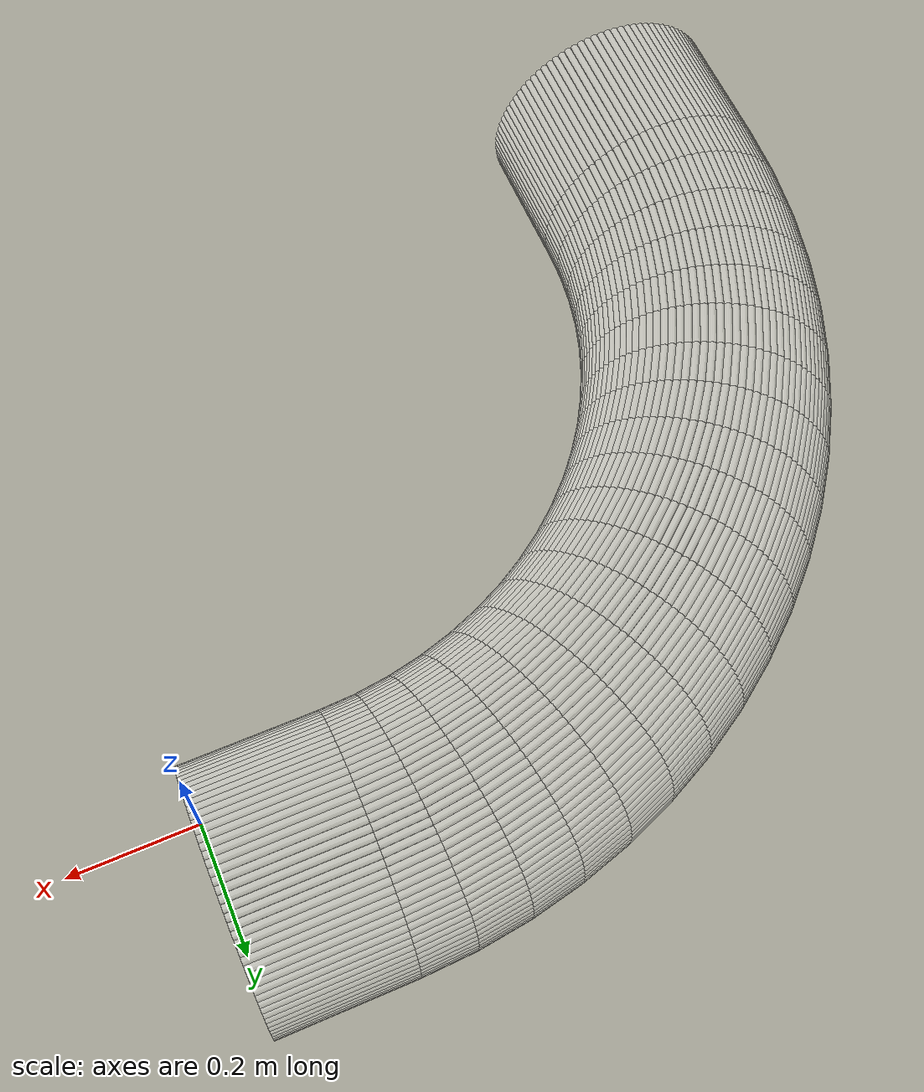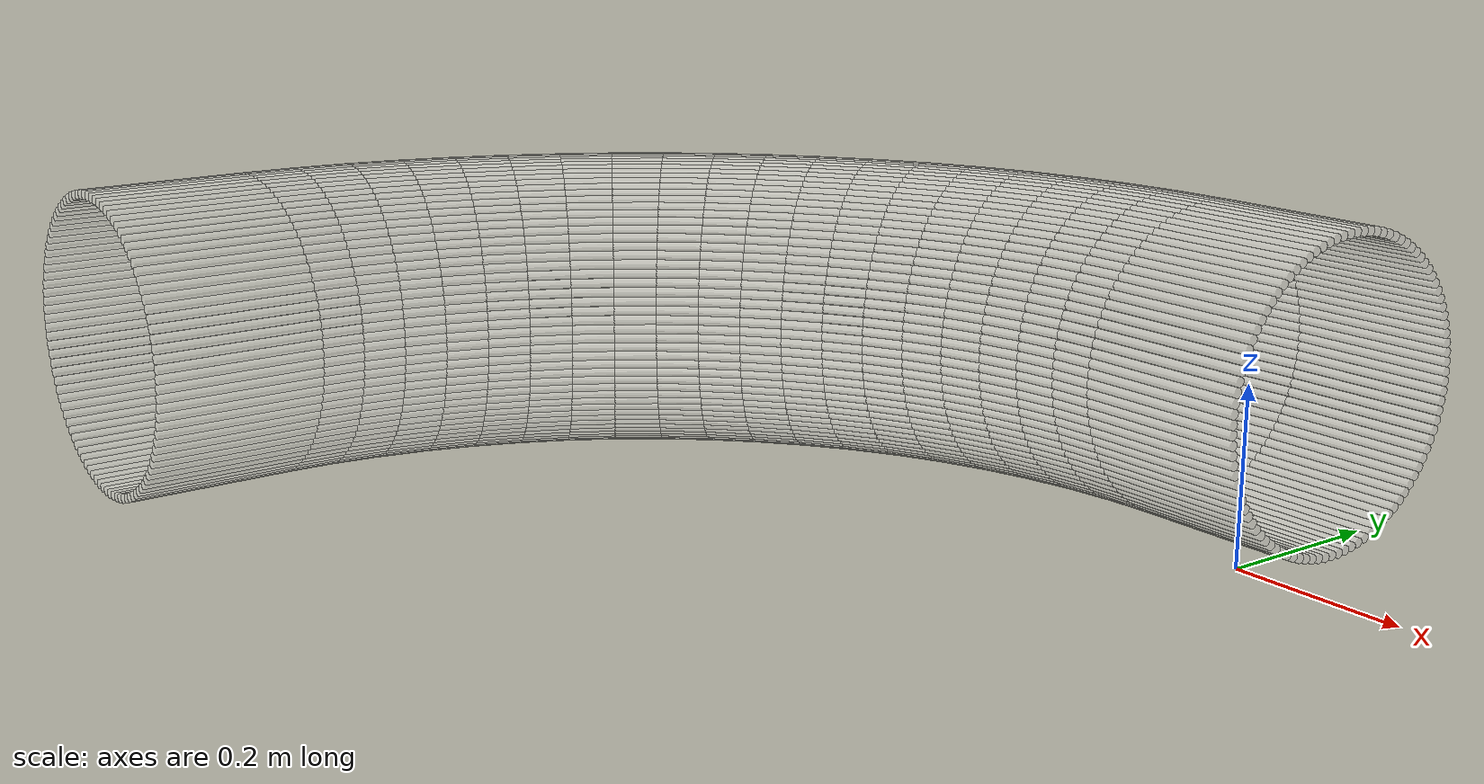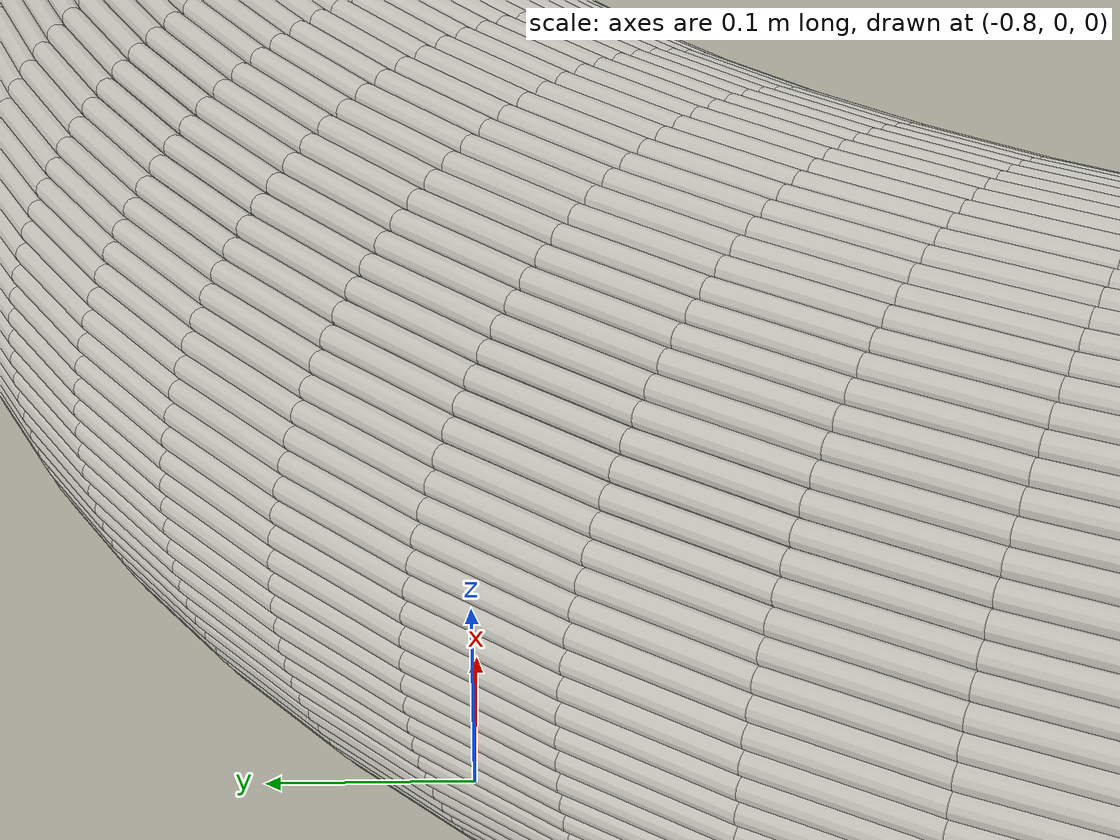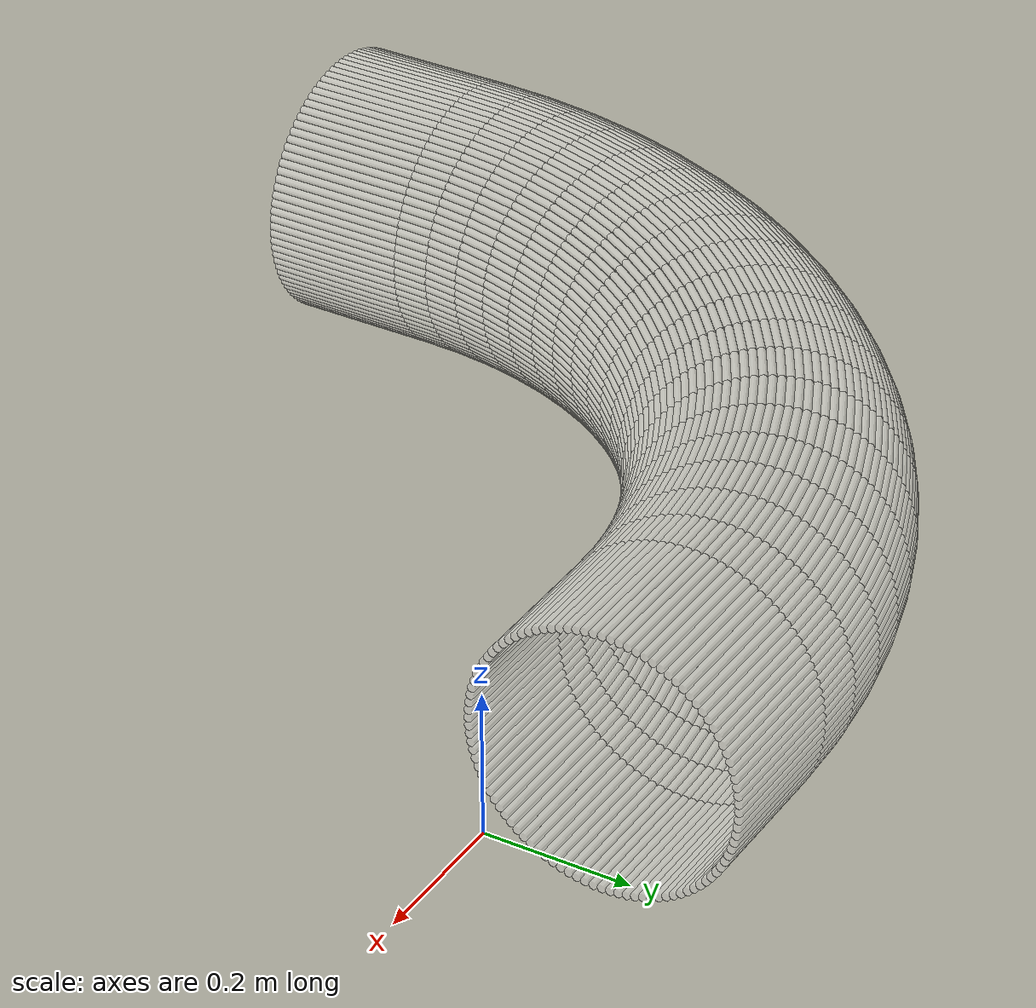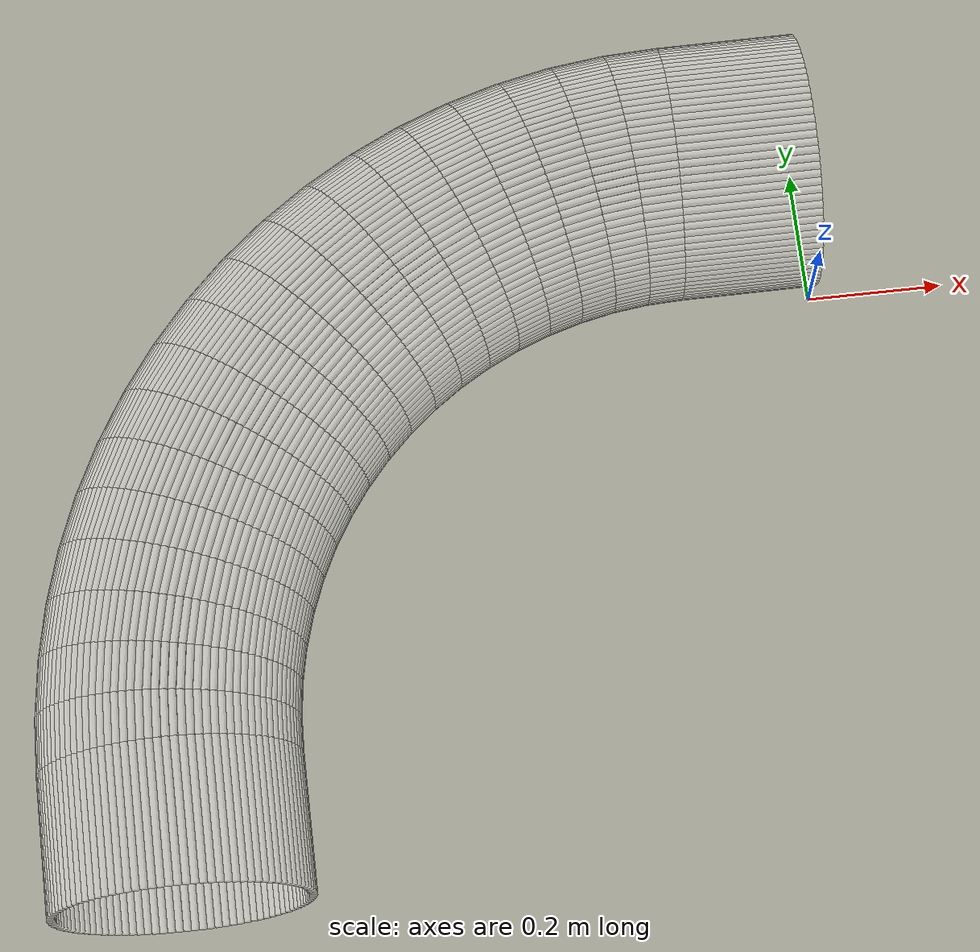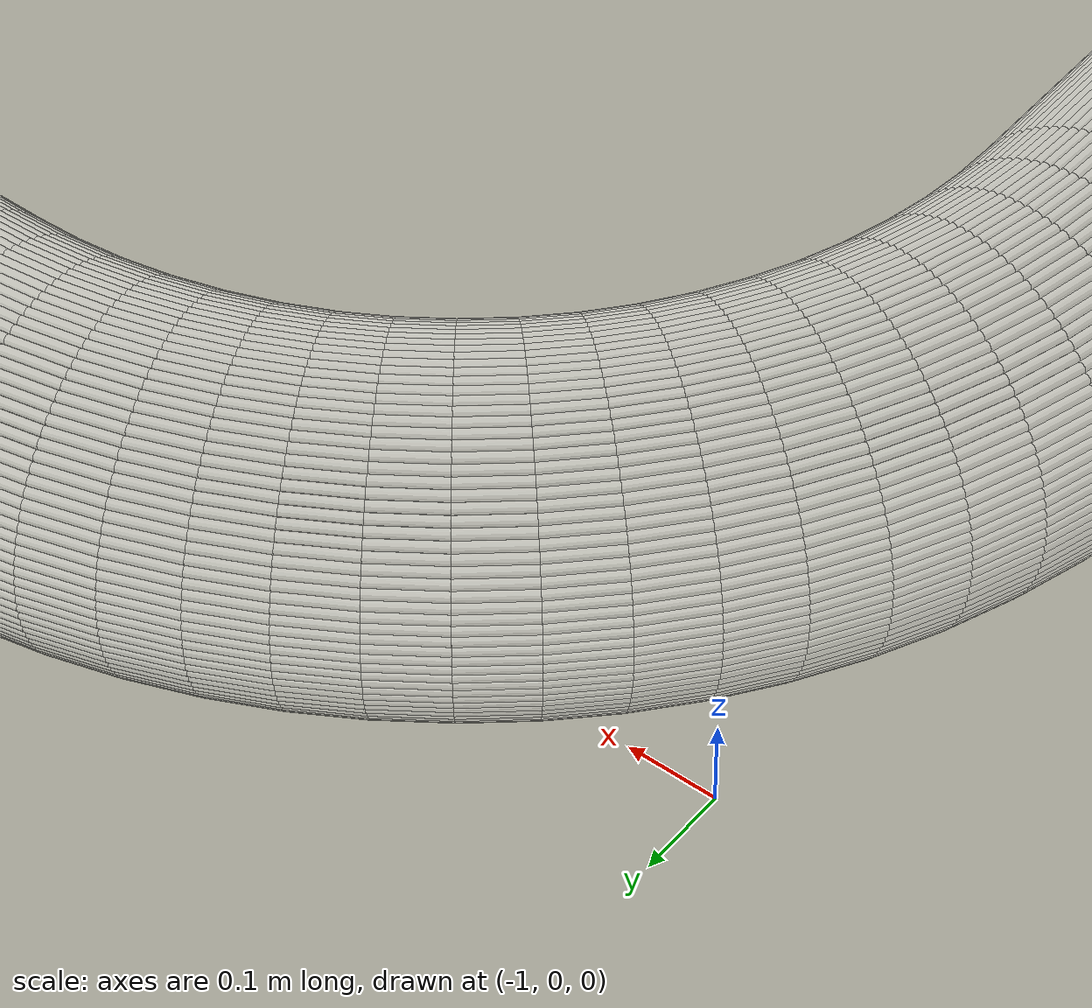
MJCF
<?xml version="1.0" encoding="utf-8"?>
<mujoco>
   <worldbody>
   <body pos="-0.2 -0.64 -0.02" euler="0 0 90">
      <geom euler=" 0 10 0 " fromto="0.98 -0.2 0.18 0.98 0 0.18" rgba="1 1 1 0.35"
            size="0.0056539"
            type="cylinder"/>
      <geom euler=" 0 20 0 " fromto="0.97964 -0.2 0.1913 0.97964 0 0.1913"
            rgba="1 1 1 0.35"
            size="0.0056539"
            type="cylinder"/>
      <geom euler=" 0 30 0 " fromto="0.97858 -0.2 0.20256 0.97858 0 0.20256"
            rgba="1 1 1 0.35"
            size="0.0056539"
            type="cylinder"/>
      <geom euler=" 0 40 0 " fromto="0.97681 -0.2 0.21373 0.97681 0 0.21373"
            rgba="1 1 1 0.35"
            size="0.0056539"
            type="cylinder"/>
      <geom euler=" 0 50 0 " fromto="0.97434 -0.2 0.22476 0.97434 0 0.22476"
            rgba="1 1 1 0.35"
            size="0.0056539"
            type="cylinder"/>
      <geom euler=" 0 60 0 " fromto="0.97119 -0.2 0.23562 0.97119 0 0.23562"
            rgba="1 1 1 0.35"
            size="0.0056539"
            type="cylinder"/>
      <geom euler=" 0 70 0 " fromto="0.96736 -0.2 0.24626 0.96736 0 0.24626"
            rgba="1 1 1 0.35"
            size="0.0056539"
            type="cylinder"/>
      <geom euler=" 0 80 0 " fromto="0.96287 -0.2 0.25664 0.96287 0 0.25664"
            rgba="1 1 1 0.35"
            size="0.0056539"
            type="cylinder"/>
      <geom euler=" 0 90 0 " fromto="0.95774 -0.2 0.26672 0.95774 0 0.26672"
            rgba="1 1 1 0.35"
            size="0.0056539"
            type="cylinder"/>
      <geom euler=" 0 100 0 " fromto="0.95198 -0.2 0.27645 0.95198 0 0.27645"
            rgba="1 1 1 0.35"
            size="0.0056539"
            type="cylinder"/>
      <geom euler=" 0 110 0 " fromto="0.94562 -0.2 0.2858 0.94562 0 0.2858"
            rgba="1 1 1 0.35"
            size="0.0056539"
            type="cylinder"/>
      <geom euler=" 0 120 0 " fromto="0.93869 -0.2 0.29474 0.93869 0 0.29474"
            rgba="1 1 1 0.35"
            size="0.0056539"
            type="cylinder"/>
      <geom euler=" 0 130 0 " fromto="0.93121 -0.2 0.30322 0.93121 0 0.30322"
            rgba="1 1 1 0.35"
            size="0.0056539"
            type="cylinder"/>
      <geom euler=" 0 140 0 " fromto="0.92322 -0.2 0.31121 0.92322 0 0.31121"
            rgba="1 1 1 0.35"
            size="0.0056539"
            type="cylinder"/>
      <geom euler=" 0 150 0 " fromto="0.91474 -0.2 0.31869 0.91474 0 0.31869"
            rgba="1 1 1 0.35"
            size="0.0056539"
            type="cylinder"/>
      <geom euler=" 0 160 0 " fromto="0.9058 -0.2 0.32562 0.9058 0 0.32562"
            rgba="1 1 1 0.35"
            size="0.0056539"
            type="cylinder"/>
      <geom euler=" 0 170 0 " fromto="0.89645 -0.2 0.33198 0.89645 0 0.33198"
            rgba="1 1 1 0.35"
            size="0.0056539"
            type="cylinder"/>
      <geom euler=" 0 180 0 " fromto="0.88672 -0.2 0.33774 0.88672 0 0.33774"
            rgba="1 1 1 0.35"
            size="0.0056539"
            type="cylinder"/>
      <geom euler=" 0 190 0 " fromto="0.87664 -0.2 0.34287 0.87664 0 0.34287"
            rgba="1 1 1 0.35"
            size="0.0056539"
            type="cylinder"/>
      <geom euler=" 0 200 0 " fromto="0.86626 -0.2 0.34736 0.86626 0 0.34736"
            rgba="1 1 1 0.35"
            size="0.0056539"
            type="cylinder"/>
      <geom euler=" 0 210 0 " fromto="0.85562 -0.2 0.35119 0.85562 0 0.35119"
            rgba="1 1 1 0.35"
            size="0.0056539"
            type="cylinder"/>
      <geom euler=" 0 220 0 " fromto="0.84476 -0.2 0.35434 0.84476 0 0.35434"
            rgba="1 1 1 0.35"
            size="0.0056539"
            type="cylinder"/>
      <geom euler=" 0 230 0 " fromto="0.83373 -0.2 0.35681 0.83373 0 0.35681"
            rgba="1 1 1 0.35"
            size="0.0056539"
            type="cylinder"/>
      <geom euler=" 0 240 0 " fromto="0.82256 -0.2 0.35858 0.82256 0 0.35858"
            rgba="1 1 1 0.35"
            size="0.0056539"
            type="cylinder"/>
      <geom euler=" 0 250 0 " fromto="0.8113 -0.2 0.35964 0.8113 0 0.35964"
            rgba="1 1 1 0.35"
            size="0.0056539"
            type="cylinder"/>
      <geom euler=" 0 260 0 " fromto="0.8 -0.2 0.36 0.8 0 0.36" rgba="1 1 1 0.35"
            size="0.0056539"
            type="cylinder"/>
      <geom euler=" 0 270 0 " fromto="0.7887 -0.2 0.35964 0.7887 0 0.35964"
            rgba="1 1 1 0.35"
            size="0.0056539"
            type="cylinder"/>
      <geom euler=" 0 280 0 " fromto="0.77744 -0.2 0.35858 0.77744 0 0.35858"
            rgba="1 1 1 0.35"
            size="0.0056539"
            type="cylinder"/>
      <geom euler=" 0 290 0 " fromto="0.76627 -0.2 0.35681 0.76627 0 0.35681"
            rgba="1 1 1 0.35"
            size="0.0056539"
            type="cylinder"/>
      <geom euler=" 0 300 0 " fromto="0.75524 -0.2 0.35434 0.75524 0 0.35434"
            rgba="1 1 1 0.35"
            size="0.0056539"
            type="cylinder"/>
      <geom euler=" 0 310 0 " fromto="0.74438 -0.2 0.35119 0.74438 0 0.35119"
            rgba="1 1 1 0.35"
            size="0.0056539"
            type="cylinder"/>
      <geom euler=" 0 320 0 " fromto="0.73374 -0.2 0.34736 0.73374 0 0.34736"
            rgba="1 1 1 0.35"
            size="0.0056539"
            type="cylinder"/>
      <geom euler=" 0 330 0 " fromto="0.72336 -0.2 0.34287 0.72336 0 0.34287"
            rgba="1 1 1 0.35"
            size="0.0056539"
            type="cylinder"/>
      <geom euler=" 0 340 0 " fromto="0.71328 -0.2 0.33774 0.71328 0 0.33774"
            rgba="1 1 1 0.35"
            size="0.0056539"
            type="cylinder"/>
      <geom euler=" 0 350 0 " fromto="0.70355 -0.2 0.33198 0.70355 0 0.33198"
            rgba="1 1 1 0.35"
            size="0.0056539"
            type="cylinder"/>
      <geom euler=" 0 360 0 " fromto="0.6942 -0.2 0.32562 0.6942 0 0.32562"
            rgba="1 1 1 0.35"
            size="0.0056539"
            type="cylinder"/>
      <geom euler=" 0 370 0 " fromto="0.68526 -0.2 0.31869 0.68526 0 0.31869"
            rgba="1 1 1 0.35"
            size="0.0056539"
            type="cylinder"/>
      <geom euler=" 0 380 0 " fromto="0.67678 -0.2 0.31121 0.67678 0 0.31121"
            rgba="1 1 1 0.35"
            size="0.0056539"
            type="cylinder"/>
      <geom euler=" 0 390 0 " fromto="0.66879 -0.2 0.30322 0.66879 0 0.30322"
            rgba="1 1 1 0.35"
            size="0.0056539"
            type="cylinder"/>
      <geom euler=" 0 400 0 " fromto="0.66131 -0.2 0.29474 0.66131 0 0.29474"
            rgba="1 1 1 0.35"
            size="0.0056539"
            type="cylinder"/>
      <geom euler=" 0 410 0 " fromto="0.65438 -0.2 0.2858 0.65438 0 0.2858"
            rgba="1 1 1 0.35"
            size="0.0056539"
            type="cylinder"/>
      <geom euler=" 0 420 0 " fromto="0.64802 -0.2 0.27645 0.64802 0 0.27645"
            rgba="1 1 1 0.35"
            size="0.0056539"
            type="cylinder"/>
      <geom euler=" 0 430 0 " fromto="0.64226 -0.2 0.26672 0.64226 0 0.26672"
            rgba="1 1 1 0.35"
            size="0.0056539"
            type="cylinder"/>
      <geom euler=" 0 440 0 " fromto="0.63713 -0.2 0.25664 0.63713 0 0.25664"
            rgba="1 1 1 0.35"
            size="0.0056539"
            type="cylinder"/>
      <geom euler=" 0 450 0 " fromto="0.63264 -0.2 0.24626 0.63264 0 0.24626"
            rgba="1 1 1 0.35"
            size="0.0056539"
            type="cylinder"/>
      <geom euler=" 0 460 0 " fromto="0.62881 -0.2 0.23562 0.62881 0 0.23562"
            rgba="1 1 1 0.35"
            size="0.0056539"
            type="cylinder"/>
      <geom euler=" 0 470 0 " fromto="0.62566 -0.2 0.22476 0.62566 0 0.22476"
            rgba="1 1 1 0.35"
            size="0.0056539"
            type="cylinder"/>
      <geom euler=" 0 480 0 " fromto="0.62319 -0.2 0.21373 0.62319 0 0.21373"
            rgba="1 1 1 0.35"
            size="0.0056539"
            type="cylinder"/>
      <geom euler=" 0 490 0 " fromto="0.62142 -0.2 0.20256 0.62142 0 0.20256"
            rgba="1 1 1 0.35"
            size="0.0056539"
            type="cylinder"/>
      <geom euler=" 0 500 0 " fromto="0.62036 -0.2 0.1913 0.62036 0 0.1913"
            rgba="1 1 1 0.35"
            size="0.0056539"
            type="cylinder"/>
      <geom euler=" 0 510 0 " fromto="0.62 -0.2 0.18 0.62 0 0.18" rgba="1 1 1 0.35"
            size="0.0056539"
            type="cylinder"/>
      <geom euler=" 0 520 0 " fromto="0.62036 -0.2 0.1687 0.62036 0 0.1687"
            rgba="1 1 1 0.35"
            size="0.0056539"
            type="cylinder"/>
      <geom euler=" 0 530 0 " fromto="0.62142 -0.2 0.15744 0.62142 0 0.15744"
            rgba="1 1 1 0.35"
            size="0.0056539"
            type="cylinder"/>
      <geom euler=" 0 540 0 " fromto="0.62319 -0.2 0.14627 0.62319 0 0.14627"
            rgba="1 1 1 0.35"
            size="0.0056539"
            type="cylinder"/>
      <geom euler=" 0 550 0 " fromto="0.62566 -0.2 0.13524 0.62566 0 0.13524"
            rgba="1 1 1 0.35"
            size="0.0056539"
            type="cylinder"/>
      <geom euler=" 0 560 0 " fromto="0.62881 -0.2 0.12438 0.62881 0 0.12438"
            rgba="1 1 1 0.35"
            size="0.0056539"
            type="cylinder"/>
      <geom euler=" 0 570 0 " fromto="0.63264 -0.2 0.11374 0.63264 0 0.11374"
            rgba="1 1 1 0.35"
            size="0.0056539"
            type="cylinder"/>
      <geom euler=" 0 580 0 " fromto="0.63713 -0.2 0.10336 0.63713 0 0.10336"
            rgba="1 1 1 0.35"
            size="0.0056539"
            type="cylinder"/>
      <geom euler=" 0 590 0 " fromto="0.64226 -0.2 0.093284 0.64226 0 0.093284"
            rgba="1 1 1 0.35"
            size="0.0056539"
            type="cylinder"/>
      <geom euler=" 0 600 0 " fromto="0.64802 -0.2 0.083551 0.64802 0 0.083551"
            rgba="1 1 1 0.35"
            size="0.0056539"
            type="cylinder"/>
      <geom euler=" 0 610 0 " fromto="0.65438 -0.2 0.074199 0.65438 0 0.074199"
            rgba="1 1 1 0.35"
            size="0.0056539"
            type="cylinder"/>
      <geom euler=" 0 620 0 " fromto="0.66131 -0.2 0.065264 0.66131 0 0.065264"
            rgba="1 1 1 0.35"
            size="0.0056539"
            type="cylinder"/>
      <geom euler=" 0 630 0 " fromto="0.66879 -0.2 0.056782 0.66879 0 0.056782"
            rgba="1 1 1 0.35"
            size="0.0056539"
            type="cylinder"/>
      <geom euler=" 0 640 0 " fromto="0.67678 -0.2 0.048786 0.67678 0 0.048786"
            rgba="1 1 1 0.35"
            size="0.0056539"
            type="cylinder"/>
      <geom euler=" 0 650 0 " fromto="0.68526 -0.2 0.041308 0.68526 0 0.041308"
            rgba="1 1 1 0.35"
            size="0.0056539"
            type="cylinder"/>
      <geom euler=" 0 660 0 " fromto="0.6942 -0.2 0.034377 0.6942 0 0.034377"
            rgba="1 1 1 0.35"
            size="0.0056539"
            type="cylinder"/>
      <geom euler=" 0 670 0 " fromto="0.70355 -0.2 0.028021 0.70355 0 0.028021"
            rgba="1 1 1 0.35"
            size="0.0056539"
            type="cylinder"/>
      <geom euler=" 0 680 0 " fromto="0.71328 -0.2 0.022265 0.71328 0 0.022265"
            rgba="1 1 1 0.35"
            size="0.0056539"
            type="cylinder"/>
      <geom euler=" 0 690 0 " fromto="0.72336 -0.2 0.017131 0.72336 0 0.017131"
            rgba="1 1 1 0.35"
            size="0.0056539"
            type="cylinder"/>
      <geom euler=" 0 700 0 " fromto="0.73374 -0.2 0.01264 0.73374 0 0.01264"
            rgba="1 1 1 0.35"
            size="0.0056539"
            type="cylinder"/>
      <geom euler=" 0 710 0 " fromto="0.74438 -0.2 0.0088098 0.74438 0 0.0088098"
            rgba="1 1 1 0.35"
            size="0.0056539"
            type="cylinder"/>
      <geom euler=" 0 720 0 " fromto="0.75524 -0.2 0.005655 0.75524 0 0.005655"
            rgba="1 1 1 0.35"
            size="0.0056539"
            type="cylinder"/>
      <geom euler=" 0 730 0 " fromto="0.76627 -0.2 0.0031883 0.76627 0 0.0031883"
            rgba="1 1 1 0.35"
            size="0.0056539"
            type="cylinder"/>
      <geom euler=" 0 740 0 " fromto="0.77744 -0.2 0.0014194 0.77744 0 0.0014194"
            rgba="1 1 1 0.35"
            size="0.0056539"
            type="cylinder"/>
      <geom euler=" 0 750 0 " fromto="0.7887 -0.2 0.00035519 0.7887 0 0.00035519"
            rgba="1 1 1 0.35"
            size="0.0056539"
            type="cylinder"/>
      <geom euler=" 0 760 0 " fromto="0.8 -0.2 0 0.8 0 0" rgba="1 1 1 0.35"
            size="0.0056539"
            type="cylinder"/>
      <geom euler=" 0 770 0 " fromto="0.8113 -0.2 0.00035519 0.8113 0 0.00035519"
            rgba="1 1 1 0.35"
            size="0.0056539"
            type="cylinder"/>
      <geom euler=" 0 780 0 " fromto="0.82256 -0.2 0.0014194 0.82256 0 0.0014194"
            rgba="1 1 1 0.35"
            size="0.0056539"
            type="cylinder"/>
      <geom euler=" 0 790 0 " fromto="0.83373 -0.2 0.0031883 0.83373 0 0.0031883"
            rgba="1 1 1 0.35"
            size="0.0056539"
            type="cylinder"/>
      <geom euler=" 0 800 0 " fromto="0.84476 -0.2 0.005655 0.84476 0 0.005655"
            rgba="1 1 1 0.35"
            size="0.0056539"
            type="cylinder"/>
      <geom euler=" 0 810 0 " fromto="0.85562 -0.2 0.0088098 0.85562 0 0.0088098"
            rgba="1 1 1 0.35"
            size="0.0056539"
            type="cylinder"/>
      <geom euler=" 0 820 0 " fromto="0.86626 -0.2 0.01264 0.86626 0 0.01264"
            rgba="1 1 1 0.35"
            size="0.0056539"
            type="cylinder"/>
      <geom euler=" 0 830 0 " fromto="0.87664 -0.2 0.017131 0.87664 0 0.017131"
            rgba="1 1 1 0.35"
            size="0.0056539"
            type="cylinder"/>
      <geom euler=" 0 840 0 " fromto="0.88672 -0.2 0.022265 0.88672 0 0.022265"
            rgba="1 1 1 0.35"
            size="0.0056539"
            type="cylinder"/>
      <geom euler=" 0 850 0 " fromto="0.89645 -0.2 0.028021 0.89645 0 0.028021"
            rgba="1 1 1 0.35"
            size="0.0056539"
            type="cylinder"/>
      <geom euler=" 0 860 0 " fromto="0.9058 -0.2 0.034377 0.9058 0 0.034377"
            rgba="1 1 1 0.35"
            size="0.0056539"
            type="cylinder"/>
      <geom euler=" 0 870 0 " fromto="0.91474 -0.2 0.041308 0.91474 0 0.041308"
            rgba="1 1 1 0.35"
            size="0.0056539"
            type="cylinder"/>
      <geom euler=" 0 880 0 " fromto="0.92322 -0.2 0.048786 0.92322 0 0.048786"
            rgba="1 1 1 0.35"
            size="0.0056539"
            type="cylinder"/>
      <geom euler=" 0 890 0 " fromto="0.93121 -0.2 0.056782 0.93121 0 0.056782"
            rgba="1 1 1 0.35"
            size="0.0056539"
            type="cylinder"/>
      <geom euler=" 0 900 0 " fromto="0.93869 -0.2 0.065264 0.93869 0 0.065264"
            rgba="1 1 1 0.35"
            size="0.0056539"
            type="cylinder"/>
      <geom euler=" 0 910 0 " fromto="0.94562 -0.2 0.074199 0.94562 0 0.074199"
            rgba="1 1 1 0.35"
            size="0.0056539"
            type="cylinder"/>
      <geom euler=" 0 920 0 " fromto="0.95198 -0.2 0.083551 0.95198 0 0.083551"
            rgba="1 1 1 0.35"
            size="0.0056539"
            type="cylinder"/>
      <geom euler=" 0 930 0 " fromto="0.95774 -0.2 0.093284 0.95774 0 0.093284"
            rgba="1 1 1 0.35"
            size="0.0056539"
            type="cylinder"/>
      <geom euler=" 0 940 0 " fromto="0.96287 -0.2 0.10336 0.96287 0 0.10336"
            rgba="1 1 1 0.35"
            size="0.0056539"
            type="cylinder"/>
      <geom euler=" 0 950 0 " fromto="0.96736 -0.2 0.11374 0.96736 0 0.11374"
            rgba="1 1 1 0.35"
            size="0.0056539"
            type="cylinder"/>
      <geom euler=" 0 960 0 " fromto="0.97119 -0.2 0.12438 0.97119 0 0.12438"
            rgba="1 1 1 0.35"
            size="0.0056539"
            type="cylinder"/>
      <geom euler=" 0 970 0 " fromto="0.97434 -0.2 0.13524 0.97434 0 0.13524"
            rgba="1 1 1 0.35"
            size="0.0056539"
            type="cylinder"/>
      <geom euler=" 0 980 0 " fromto="0.97681 -0.2 0.14627 0.97681 0 0.14627"
            rgba="1 1 1 0.35"
            size="0.0056539"
            type="cylinder"/>
      <geom euler=" 0 990 0 " fromto="0.97858 -0.2 0.15744 0.97858 0 0.15744"
            rgba="1 1 1 0.35"
            size="0.0056539"
            type="cylinder"/>
      <geom euler=" 0 1000 0 " fromto="0.97964 -0.2 0.1687 0.97964 0 0.1687"
            rgba="1 1 1 0.35"
            size="0.0056539"
            type="cylinder"/>
      <geom euler=" 0 10 0 " fromto="0.98 0 0.18 0.97665 0.080928 0.18" rgba="1 1 1 0.35"
            size="0.0056539"
            type="cylinder"/>
      <geom euler=" 0 20 0 " fromto="0.97964 0 0.1913 0.9763 0.080898 0.1913"
            rgba="1 1 1 0.35"
            size="0.0056539"
            type="cylinder"/>
      <geom euler=" 0 30 0 " fromto="0.97858 0 0.20256 0.97524 0.080811 0.20256"
            rgba="1 1 1 0.35"
            size="0.0056539"
            type="cylinder"/>
      <geom euler=" 0 40 0 " fromto="0.97681 0 0.21373 0.97348 0.080664 0.21373"
            rgba="1 1 1 0.35"
            size="0.0056539"
            type="cylinder"/>
      <geom euler=" 0 50 0 " fromto="0.97434 0 0.22476 0.97102 0.080461 0.22476"
            rgba="1 1 1 0.35"
            size="0.0056539"
            type="cylinder"/>
      <geom euler=" 0 60 0 " fromto="0.97119 0 0.23562 0.96787 0.0802 0.23562"
            rgba="1 1 1 0.35"
            size="0.0056539"
            type="cylinder"/>
      <geom euler=" 0 70 0 " fromto="0.96736 0 0.24626 0.96406 0.079884 0.24626"
            rgba="1 1 1 0.35"
            size="0.0056539"
            type="cylinder"/>
      <geom euler=" 0 80 0 " fromto="0.96287 0 0.25664 0.95958 0.079513 0.25664"
            rgba="1 1 1 0.35"
            size="0.0056539"
            type="cylinder"/>
      <geom euler=" 0 90 0 " fromto="0.95774 0 0.26672 0.95446 0.079089 0.26672"
            rgba="1 1 1 0.35"
            size="0.0056539"
            type="cylinder"/>
      <geom euler=" 0 100 0 " fromto="0.95198 0 0.27645 0.94873 0.078614 0.27645"
            rgba="1 1 1 0.35"
            size="0.0056539"
            type="cylinder"/>
      <geom euler=" 0 110 0 " fromto="0.94562 0 0.2858 0.94239 0.078089 0.2858"
            rgba="1 1 1 0.35"
            size="0.0056539"
            type="cylinder"/>
      <geom euler=" 0 120 0 " fromto="0.93869 0 0.29474 0.93549 0.077517 0.29474"
            rgba="1 1 1 0.35"
            size="0.0056539"
            type="cylinder"/>
      <geom euler=" 0 130 0 " fromto="0.93121 0 0.30322 0.92803 0.076899 0.30322"
            rgba="1 1 1 0.35"
            size="0.0056539"
            type="cylinder"/>
      <geom euler=" 0 140 0 " fromto="0.92322 0 0.31121 0.92007 0.076239 0.31121"
            rgba="1 1 1 0.35"
            size="0.0056539"
            type="cylinder"/>
      <geom euler=" 0 150 0 " fromto="0.91474 0 0.31869 0.91161 0.075538 0.31869"
            rgba="1 1 1 0.35"
            size="0.0056539"
            type="cylinder"/>
      <geom euler=" 0 160 0 " fromto="0.9058 0 0.32562 0.90271 0.0748 0.32562"
            rgba="1 1 1 0.35"
            size="0.0056539"
            type="cylinder"/>
      <geom euler=" 0 170 0 " fromto="0.89645 0 0.33198 0.89339 0.074028 0.33198"
            rgba="1 1 1 0.35"
            size="0.0056539"
            type="cylinder"/>
      <geom euler=" 0 180 0 " fromto="0.88672 0 0.33774 0.88369 0.073224 0.33774"
            rgba="1 1 1 0.35"
            size="0.0056539"
            type="cylinder"/>
      <geom euler=" 0 190 0 " fromto="0.87664 0 0.34287 0.87365 0.072392 0.34287"
            rgba="1 1 1 0.35"
            size="0.0056539"
            type="cylinder"/>
      <geom euler=" 0 200 0 " fromto="0.86626 0 0.34736 0.8633 0.071535 0.34736"
            rgba="1 1 1 0.35"
            size="0.0056539"
            type="cylinder"/>
      <geom euler=" 0 210 0 " fromto="0.85562 0 0.35119 0.8527 0.070657 0.35119"
            rgba="1 1 1 0.35"
            size="0.0056539"
            type="cylinder"/>
      <geom euler=" 0 220 0 " fromto="0.84476 0 0.35434 0.84188 0.06976 0.35434"
            rgba="1 1 1 0.35"
            size="0.0056539"
            type="cylinder"/>
      <geom euler=" 0 230 0 " fromto="0.83373 0 0.35681 0.83088 0.068849 0.35681"
            rgba="1 1 1 0.35"
            size="0.0056539"
            type="cylinder"/>
      <geom euler=" 0 240 0 " fromto="0.82256 0 0.35858 0.81975 0.067926 0.35858"
            rgba="1 1 1 0.35"
            size="0.0056539"
            type="cylinder"/>
      <geom euler=" 0 250 0 " fromto="0.8113 0 0.35964 0.80853 0.066997 0.35964"
            rgba="1 1 1 0.35"
            size="0.0056539"
            type="cylinder"/>
      <geom euler=" 0 260 0 " fromto="0.8 0 0.36 0.79727 0.066063 0.36" rgba="1 1 1 0.35"
            size="0.0056539"
            type="cylinder"/>
      <geom euler=" 0 270 0 " fromto="0.7887 0 0.35964 0.786 0.06513 0.35964"
            rgba="1 1 1 0.35"
            size="0.0056539"
            type="cylinder"/>
      <geom euler=" 0 280 0 " fromto="0.77744 0 0.35858 0.77478 0.0642 0.35858"
            rgba="1 1 1 0.35"
            size="0.0056539"
            type="cylinder"/>
      <geom euler=" 0 290 0 " fromto="0.76627 0 0.35681 0.76365 0.063278 0.35681"
            rgba="1 1 1 0.35"
            size="0.0056539"
            type="cylinder"/>
      <geom euler=" 0 300 0 " fromto="0.75524 0 0.35434 0.75266 0.062367 0.35434"
            rgba="1 1 1 0.35"
            size="0.0056539"
            type="cylinder"/>
      <geom euler=" 0 310 0 " fromto="0.74438 0 0.35119 0.74183 0.06147 0.35119"
            rgba="1 1 1 0.35"
            size="0.0056539"
            type="cylinder"/>
      <geom euler=" 0 320 0 " fromto="0.73374 0 0.34736 0.73123 0.060592 0.34736"
            rgba="1 1 1 0.35"
            size="0.0056539"
            type="cylinder"/>
      <geom euler=" 0 330 0 " fromto="0.72336 0 0.34287 0.72089 0.059735 0.34287"
            rgba="1 1 1 0.35"
            size="0.0056539"
            type="cylinder"/>
      <geom euler=" 0 340 0 " fromto="0.71328 0 0.33774 0.71085 0.058903 0.33774"
            rgba="1 1 1 0.35"
            size="0.0056539"
            type="cylinder"/>
      <geom euler=" 0 350 0 " fromto="0.70355 0 0.33198 0.70115 0.058099 0.33198"
            rgba="1 1 1 0.35"
            size="0.0056539"
            type="cylinder"/>
      <geom euler=" 0 360 0 " fromto="0.6942 0 0.32562 0.69183 0.057326 0.32562"
            rgba="1 1 1 0.35"
            size="0.0056539"
            type="cylinder"/>
      <geom euler=" 0 370 0 " fromto="0.68526 0 0.31869 0.68292 0.056589 0.31869"
            rgba="1 1 1 0.35"
            size="0.0056539"
            type="cylinder"/>
      <geom euler=" 0 380 0 " fromto="0.67678 0 0.31121 0.67447 0.055888 0.31121"
            rgba="1 1 1 0.35"
            size="0.0056539"
            type="cylinder"/>
      <geom euler=" 0 390 0 " fromto="0.66879 0 0.30322 0.6665 0.055228 0.30322"
            rgba="1 1 1 0.35"
            size="0.0056539"
            type="cylinder"/>
      <geom euler=" 0 400 0 " fromto="0.66131 0 0.29474 0.65905 0.05461 0.29474"
            rgba="1 1 1 0.35"
            size="0.0056539"
            type="cylinder"/>
      <geom euler=" 0 410 0 " fromto="0.65438 0 0.2858 0.65214 0.054038 0.2858"
            rgba="1 1 1 0.35"
            size="0.0056539"
            type="cylinder"/>
      <geom euler=" 0 420 0 " fromto="0.64802 0 0.27645 0.64581 0.053513 0.27645"
            rgba="1 1 1 0.35"
            size="0.0056539"
            type="cylinder"/>
      <geom euler=" 0 430 0 " fromto="0.64226 0 0.26672 0.64007 0.053038 0.26672"
            rgba="1 1 1 0.35"
            size="0.0056539"
            type="cylinder"/>
      <geom euler=" 0 440 0 " fromto="0.63713 0 0.25664 0.63496 0.052614 0.25664"
            rgba="1 1 1 0.35"
            size="0.0056539"
            type="cylinder"/>
      <geom euler=" 0 450 0 " fromto="0.63264 0 0.24626 0.63048 0.052243 0.24626"
            rgba="1 1 1 0.35"
            size="0.0056539"
            type="cylinder"/>
      <geom euler=" 0 460 0 " fromto="0.62881 0 0.23562 0.62666 0.051927 0.23562"
            rgba="1 1 1 0.35"
            size="0.0056539"
            type="cylinder"/>
      <geom euler=" 0 470 0 " fromto="0.62566 0 0.22476 0.62352 0.051666 0.22476"
            rgba="1 1 1 0.35"
            size="0.0056539"
            type="cylinder"/>
      <geom euler=" 0 480 0 " fromto="0.62319 0 0.21373 0.62106 0.051462 0.21373"
            rgba="1 1 1 0.35"
            size="0.0056539"
            type="cylinder"/>
      <geom euler=" 0 490 0 " fromto="0.62142 0 0.20256 0.6193 0.051316 0.20256"
            rgba="1 1 1 0.35"
            size="0.0056539"
            type="cylinder"/>
      <geom euler=" 0 500 0 " fromto="0.62036 0 0.1913 0.61824 0.051229 0.1913"
            rgba="1 1 1 0.35"
            size="0.0056539"
            type="cylinder"/>
      <geom euler=" 0 510 0 " fromto="0.62 0 0.18 0.61788 0.051199 0.18" rgba="1 1 1 0.35"
            size="0.0056539"
            type="cylinder"/>
      <geom euler=" 0 520 0 " fromto="0.62036 0 0.1687 0.61824 0.051229 0.1687"
            rgba="1 1 1 0.35"
            size="0.0056539"
            type="cylinder"/>
      <geom euler=" 0 530 0 " fromto="0.62142 0 0.15744 0.6193 0.051316 0.15744"
            rgba="1 1 1 0.35"
            size="0.0056539"
            type="cylinder"/>
      <geom euler=" 0 540 0 " fromto="0.62319 0 0.14627 0.62106 0.051462 0.14627"
            rgba="1 1 1 0.35"
            size="0.0056539"
            type="cylinder"/>
      <geom euler=" 0 550 0 " fromto="0.62566 0 0.13524 0.62352 0.051666 0.13524"
            rgba="1 1 1 0.35"
            size="0.0056539"
            type="cylinder"/>
      <geom euler=" 0 560 0 " fromto="0.62881 0 0.12438 0.62666 0.051927 0.12438"
            rgba="1 1 1 0.35"
            size="0.0056539"
            type="cylinder"/>
      <geom euler=" 0 570 0 " fromto="0.63264 0 0.11374 0.63048 0.052243 0.11374"
            rgba="1 1 1 0.35"
            size="0.0056539"
            type="cylinder"/>
      <geom euler=" 0 580 0 " fromto="0.63713 0 0.10336 0.63496 0.052614 0.10336"
            rgba="1 1 1 0.35"
            size="0.0056539"
            type="cylinder"/>
      <geom euler=" 0 590 0 " fromto="0.64226 0 0.093284 0.64007 0.053038 0.093284"
            rgba="1 1 1 0.35"
            size="0.0056539"
            type="cylinder"/>
      <geom euler=" 0 600 0 " fromto="0.64802 0 0.083551 0.64581 0.053513 0.083551"
            rgba="1 1 1 0.35"
            size="0.0056539"
            type="cylinder"/>
      <geom euler=" 0 610 0 " fromto="0.65438 0 0.074199 0.65214 0.054038 0.074199"
            rgba="1 1 1 0.35"
            size="0.0056539"
            type="cylinder"/>
      <geom euler=" 0 620 0 " fromto="0.66131 0 0.065264 0.65905 0.05461 0.065264"
            rgba="1 1 1 0.35"
            size="0.0056539"
            type="cylinder"/>
      <geom euler=" 0 630 0 " fromto="0.66879 0 0.056782 0.6665 0.055228 0.056782"
            rgba="1 1 1 0.35"
            size="0.0056539"
            type="cylinder"/>
      <geom euler=" 0 640 0 " fromto="0.67678 0 0.048786 0.67447 0.055888 0.048786"
            rgba="1 1 1 0.35"
            size="0.0056539"
            type="cylinder"/>
      <geom euler=" 0 650 0 " fromto="0.68526 0 0.041308 0.68292 0.056589 0.041308"
            rgba="1 1 1 0.35"
            size="0.0056539"
            type="cylinder"/>
      <geom euler=" 0 660 0 " fromto="0.6942 0 0.034377 0.69183 0.057326 0.034377"
            rgba="1 1 1 0.35"
            size="0.0056539"
            type="cylinder"/>
      <geom euler=" 0 670 0 " fromto="0.70355 0 0.028021 0.70115 0.058099 0.028021"
            rgba="1 1 1 0.35"
            size="0.0056539"
            type="cylinder"/>
      <geom euler=" 0 680 0 " fromto="0.71328 0 0.022265 0.71085 0.058903 0.022265"
            rgba="1 1 1 0.35"
            size="0.0056539"
            type="cylinder"/>
      <geom euler=" 0 690 0 " fromto="0.72336 0 0.017131 0.72089 0.059735 0.017131"
            rgba="1 1 1 0.35"
            size="0.0056539"
            type="cylinder"/>
      <geom euler=" 0 700 0 " fromto="0.73374 0 0.01264 0.73123 0.060592 0.01264"
            rgba="1 1 1 0.35"
            size="0.0056539"
            type="cylinder"/>
      <geom euler=" 0 710 0 " fromto="0.74438 0 0.0088098 0.74183 0.06147 0.0088098"
            rgba="1 1 1 0.35"
            size="0.0056539"
            type="cylinder"/>
      <geom euler=" 0 720 0 " fromto="0.75524 0 0.005655 0.75266 0.062367 0.005655"
            rgba="1 1 1 0.35"
            size="0.0056539"
            type="cylinder"/>
      <geom euler=" 0 730 0 " fromto="0.76627 0 0.0031883 0.76365 0.063278 0.0031883"
            rgba="1 1 1 0.35"
            size="0.0056539"
            type="cylinder"/>
      <geom euler=" 0 740 0 " fromto="0.77744 0 0.0014194 0.77478 0.0642 0.0014194"
            rgba="1 1 1 0.35"
            size="0.0056539"
            type="cylinder"/>
      <geom euler=" 0 750 0 " fromto="0.7887 0 0.00035519 0.786 0.06513 0.00035519"
            rgba="1 1 1 0.35"
            size="0.0056539"
            type="cylinder"/>
      <geom euler=" 0 760 0 " fromto="0.8 0 0 0.79727 0.066063 0" rgba="1 1 1 0.35"
            size="0.0056539"
            type="cylinder"/>
      <geom euler=" 0 770 0 " fromto="0.8113 0 0.00035519 0.80853 0.066997 0.00035519"
            rgba="1 1 1 0.35"
            size="0.0056539"
            type="cylinder"/>
      <geom euler=" 0 780 0 " fromto="0.82256 0 0.0014194 0.81975 0.067926 0.0014194"
            rgba="1 1 1 0.35"
            size="0.0056539"
            type="cylinder"/>
      <geom euler=" 0 790 0 " fromto="0.83373 0 0.0031883 0.83088 0.068849 0.0031883"
            rgba="1 1 1 0.35"
            size="0.0056539"
            type="cylinder"/>
      <geom euler=" 0 800 0 " fromto="0.84476 0 0.005655 0.84188 0.06976 0.005655"
            rgba="1 1 1 0.35"
            size="0.0056539"
            type="cylinder"/>
      <geom euler=" 0 810 0 " fromto="0.85562 0 0.0088098 0.8527 0.070657 0.0088098"
            rgba="1 1 1 0.35"
            size="0.0056539"
            type="cylinder"/>
      <geom euler=" 0 820 0 " fromto="0.86626 0 0.01264 0.8633 0.071535 0.01264"
            rgba="1 1 1 0.35"
            size="0.0056539"
            type="cylinder"/>
      <geom euler=" 0 830 0 " fromto="0.87664 0 0.017131 0.87365 0.072392 0.017131"
            rgba="1 1 1 0.35"
            size="0.0056539"
            type="cylinder"/>
      <geom euler=" 0 840 0 " fromto="0.88672 0 0.022265 0.88369 0.073224 0.022265"
            rgba="1 1 1 0.35"
            size="0.0056539"
            type="cylinder"/>
      <geom euler=" 0 850 0 " fromto="0.89645 0 0.028021 0.89339 0.074028 0.028021"
            rgba="1 1 1 0.35"
            size="0.0056539"
            type="cylinder"/>
      <geom euler=" 0 860 0 " fromto="0.9058 0 0.034377 0.90271 0.0748 0.034377"
            rgba="1 1 1 0.35"
            size="0.0056539"
            type="cylinder"/>
      <geom euler=" 0 870 0 " fromto="0.91474 0 0.041308 0.91161 0.075538 0.041308"
            rgba="1 1 1 0.35"
            size="0.0056539"
            type="cylinder"/>
      <geom euler=" 0 880 0 " fromto="0.92322 0 0.048786 0.92007 0.076239 0.048786"
            rgba="1 1 1 0.35"
            size="0.0056539"
            type="cylinder"/>
      <geom euler=" 0 890 0 " fromto="0.93121 0 0.056782 0.92803 0.076899 0.056782"
            rgba="1 1 1 0.35"
            size="0.0056539"
            type="cylinder"/>
      <geom euler=" 0 900 0 " fromto="0.93869 0 0.065264 0.93549 0.077517 0.065264"
            rgba="1 1 1 0.35"
            size="0.0056539"
            type="cylinder"/>
      <geom euler=" 0 910 0 " fromto="0.94562 0 0.074199 0.94239 0.078089 0.074199"
            rgba="1 1 1 0.35"
            size="0.0056539"
            type="cylinder"/>
      <geom euler=" 0 920 0 " fromto="0.95198 0 0.083551 0.94873 0.078614 0.083551"
            rgba="1 1 1 0.35"
            size="0.0056539"
            type="cylinder"/>
      <geom euler=" 0 930 0 " fromto="0.95774 0 0.093284 0.95446 0.079089 0.093284"
            rgba="1 1 1 0.35"
            size="0.0056539"
            type="cylinder"/>
      <geom euler=" 0 940 0 " fromto="0.96287 0 0.10336 0.95958 0.079513 0.10336"
            rgba="1 1 1 0.35"
            size="0.0056539"
            type="cylinder"/>
      <geom euler=" 0 950 0 " fromto="0.96736 0 0.11374 0.96406 0.079884 0.11374"
            rgba="1 1 1 0.35"
            size="0.0056539"
            type="cylinder"/>
      <geom euler=" 0 960 0 " fromto="0.97119 0 0.12438 0.96787 0.0802 0.12438"
            rgba="1 1 1 0.35"
            size="0.0056539"
            type="cylinder"/>
      <geom euler=" 0 970 0 " fromto="0.97434 0 0.13524 0.97102 0.080461 0.13524"
            rgba="1 1 1 0.35"
            size="0.0056539"
            type="cylinder"/>
      <geom euler=" 0 980 0 " fromto="0.97681 0 0.14627 0.97348 0.080664 0.14627"
            rgba="1 1 1 0.35"
            size="0.0056539"
            type="cylinder"/>
      <geom euler=" 0 990 0 " fromto="0.97858 0 0.15744 0.97524 0.080811 0.15744"
            rgba="1 1 1 0.35"
            size="0.0056539"
            type="cylinder"/>
      <geom euler=" 0 1000 0 " fromto="0.97964 0 0.1687 0.9763 0.080898 0.1687"
            rgba="1 1 1 0.35"
            size="0.0056539"
            type="cylinder"/>
      <geom euler=" 0 10 0 " fromto="0.97665 0.080928 0.18 0.96663 0.1613 0.18"
            rgba="1 1 1 0.35"
            size="0.0056539"
            type="cylinder"/>
      <geom euler=" 0 20 0 " fromto="0.9763 0.080898 0.1913 0.96628 0.16124 0.1913"
            rgba="1 1 1 0.35"
            size="0.0056539"
            type="cylinder"/>
      <geom euler=" 0 30 0 " fromto="0.97524 0.080811 0.20256 0.96523 0.16107 0.20256"
            rgba="1 1 1 0.35"
            size="0.0056539"
            type="cylinder"/>
      <geom euler=" 0 40 0 " fromto="0.97348 0.080664 0.21373 0.96349 0.16078 0.21373"
            rgba="1 1 1 0.35"
            size="0.0056539"
            type="cylinder"/>
      <geom euler=" 0 50 0 " fromto="0.97102 0.080461 0.22476 0.96106 0.16037 0.22476"
            rgba="1 1 1 0.35"
            size="0.0056539"
            type="cylinder"/>
      <geom euler=" 0 60 0 " fromto="0.96787 0.0802 0.23562 0.95794 0.15985 0.23562"
            rgba="1 1 1 0.35"
            size="0.0056539"
            type="cylinder"/>
      <geom euler=" 0 70 0 " fromto="0.96406 0.079884 0.24626 0.95417 0.15922 0.24626"
            rgba="1 1 1 0.35"
            size="0.0056539"
            type="cylinder"/>
      <geom euler=" 0 80 0 " fromto="0.95958 0.079513 0.25664 0.94974 0.15848 0.25664"
            rgba="1 1 1 0.35"
            size="0.0056539"
            type="cylinder"/>
      <geom euler=" 0 90 0 " fromto="0.95446 0.079089 0.26672 0.94467 0.15764 0.26672"
            rgba="1 1 1 0.35"
            size="0.0056539"
            type="cylinder"/>
      <geom euler=" 0 100 0 " fromto="0.94873 0.078614 0.27645 0.939 0.15669 0.27645"
            rgba="1 1 1 0.35"
            size="0.0056539"
            type="cylinder"/>
      <geom euler=" 0 110 0 " fromto="0.94239 0.078089 0.2858 0.93273 0.15564 0.2858"
            rgba="1 1 1 0.35"
            size="0.0056539"
            type="cylinder"/>
      <geom euler=" 0 120 0 " fromto="0.93549 0.077517 0.29474 0.92589 0.1545 0.29474"
            rgba="1 1 1 0.35"
            size="0.0056539"
            type="cylinder"/>
      <geom euler=" 0 130 0 " fromto="0.92803 0.076899 0.30322 0.91851 0.15327 0.30322"
            rgba="1 1 1 0.35"
            size="0.0056539"
            type="cylinder"/>
      <geom euler=" 0 140 0 " fromto="0.92007 0.076239 0.31121 0.91063 0.15196 0.31121"
            rgba="1 1 1 0.35"
            size="0.0056539"
            type="cylinder"/>
      <geom euler=" 0 150 0 " fromto="0.91161 0.075538 0.31869 0.90226 0.15056 0.31869"
            rgba="1 1 1 0.35"
            size="0.0056539"
            type="cylinder"/>
      <geom euler=" 0 160 0 " fromto="0.90271 0.0748 0.32562 0.89345 0.14909 0.32562"
            rgba="1 1 1 0.35"
            size="0.0056539"
            type="cylinder"/>
      <geom euler=" 0 170 0 " fromto="0.89339 0.074028 0.33198 0.88422 0.14755 0.33198"
            rgba="1 1 1 0.35"
            size="0.0056539"
            type="cylinder"/>
      <geom euler=" 0 180 0 " fromto="0.88369 0.073224 0.33774 0.87462 0.14595 0.33774"
            rgba="1 1 1 0.35"
            size="0.0056539"
            type="cylinder"/>
      <geom euler=" 0 190 0 " fromto="0.87365 0.072392 0.34287 0.86468 0.14429 0.34287"
            rgba="1 1 1 0.35"
            size="0.0056539"
            type="cylinder"/>
      <geom euler=" 0 200 0 " fromto="0.8633 0.071535 0.34736 0.85445 0.14258 0.34736"
            rgba="1 1 1 0.35"
            size="0.0056539"
            type="cylinder"/>
      <geom euler=" 0 210 0 " fromto="0.8527 0.070657 0.35119 0.84395 0.14083 0.35119"
            rgba="1 1 1 0.35"
            size="0.0056539"
            type="cylinder"/>
      <geom euler=" 0 220 0 " fromto="0.84188 0.06976 0.35434 0.83324 0.13904 0.35434"
            rgba="1 1 1 0.35"
            size="0.0056539"
            type="cylinder"/>
      <geom euler=" 0 230 0 " fromto="0.83088 0.068849 0.35681 0.82236 0.13723 0.35681"
            rgba="1 1 1 0.35"
            size="0.0056539"
            type="cylinder"/>
      <geom euler=" 0 240 0 " fromto="0.81975 0.067926 0.35858 0.81134 0.13539 0.35858"
            rgba="1 1 1 0.35"
            size="0.0056539"
            type="cylinder"/>
      <geom euler=" 0 250 0 " fromto="0.80853 0.066997 0.35964 0.80024 0.13354 0.35964"
            rgba="1 1 1 0.35"
            size="0.0056539"
            type="cylinder"/>
      <geom euler=" 0 260 0 " fromto="0.79727 0.066063 0.36 0.78909 0.13168 0.36"
            rgba="1 1 1 0.35"
            size="0.0056539"
            type="cylinder"/>
      <geom euler=" 0 270 0 " fromto="0.786 0.06513 0.35964 0.77794 0.12982 0.35964"
            rgba="1 1 1 0.35"
            size="0.0056539"
            type="cylinder"/>
      <geom euler=" 0 280 0 " fromto="0.77478 0.0642 0.35858 0.76684 0.12796 0.35858"
            rgba="1 1 1 0.35"
            size="0.0056539"
            type="cylinder"/>
      <geom euler=" 0 290 0 " fromto="0.76365 0.063278 0.35681 0.75582 0.12612 0.35681"
            rgba="1 1 1 0.35"
            size="0.0056539"
            type="cylinder"/>
      <geom euler=" 0 300 0 " fromto="0.75266 0.062367 0.35434 0.74494 0.12431 0.35434"
            rgba="1 1 1 0.35"
            size="0.0056539"
            type="cylinder"/>
      <geom euler=" 0 310 0 " fromto="0.74183 0.06147 0.35119 0.73422 0.12252 0.35119"
            rgba="1 1 1 0.35"
            size="0.0056539"
            type="cylinder"/>
      <geom euler=" 0 320 0 " fromto="0.73123 0.060592 0.34736 0.72373 0.12077 0.34736"
            rgba="1 1 1 0.35"
            size="0.0056539"
            type="cylinder"/>
      <geom euler=" 0 330 0 " fromto="0.72089 0.059735 0.34287 0.71349 0.11906 0.34287"
            rgba="1 1 1 0.35"
            size="0.0056539"
            type="cylinder"/>
      <geom euler=" 0 340 0 " fromto="0.71085 0.058903 0.33774 0.70356 0.1174 0.33774"
            rgba="1 1 1 0.35"
            size="0.0056539"
            type="cylinder"/>
      <geom euler=" 0 350 0 " fromto="0.70115 0.058099 0.33198 0.69396 0.1158 0.33198"
            rgba="1 1 1 0.35"
            size="0.0056539"
            type="cylinder"/>
      <geom euler=" 0 360 0 " fromto="0.69183 0.057326 0.32562 0.68473 0.11426 0.32562"
            rgba="1 1 1 0.35"
            size="0.0056539"
            type="cylinder"/>
      <geom euler=" 0 370 0 " fromto="0.68292 0.056589 0.31869 0.67592 0.11279 0.31869"
            rgba="1 1 1 0.35"
            size="0.0056539"
            type="cylinder"/>
      <geom euler=" 0 380 0 " fromto="0.67447 0.055888 0.31121 0.66755 0.11139 0.31121"
            rgba="1 1 1 0.35"
            size="0.0056539"
            type="cylinder"/>
      <geom euler=" 0 390 0 " fromto="0.6665 0.055228 0.30322 0.65966 0.11008 0.30322"
            rgba="1 1 1 0.35"
            size="0.0056539"
            type="cylinder"/>
      <geom euler=" 0 400 0 " fromto="0.65905 0.05461 0.29474 0.65229 0.10885 0.29474"
            rgba="1 1 1 0.35"
            size="0.0056539"
            type="cylinder"/>
      <geom euler=" 0 410 0 " fromto="0.65214 0.054038 0.2858 0.64545 0.10771 0.2858"
            rgba="1 1 1 0.35"
            size="0.0056539"
            type="cylinder"/>
      <geom euler=" 0 420 0 " fromto="0.64581 0.053513 0.27645 0.63918 0.10666 0.27645"
            rgba="1 1 1 0.35"
            size="0.0056539"
            type="cylinder"/>
      <geom euler=" 0 430 0 " fromto="0.64007 0.053038 0.26672 0.63351 0.10571 0.26672"
            rgba="1 1 1 0.35"
            size="0.0056539"
            type="cylinder"/>
      <geom euler=" 0 440 0 " fromto="0.63496 0.052614 0.25664 0.62844 0.10487 0.25664"
            rgba="1 1 1 0.35"
            size="0.0056539"
            type="cylinder"/>
      <geom euler=" 0 450 0 " fromto="0.63048 0.052243 0.24626 0.62401 0.10413 0.24626"
            rgba="1 1 1 0.35"
            size="0.0056539"
            type="cylinder"/>
      <geom euler=" 0 460 0 " fromto="0.62666 0.051927 0.23562 0.62023 0.1035 0.23562"
            rgba="1 1 1 0.35"
            size="0.0056539"
            type="cylinder"/>
      <geom euler=" 0 470 0 " fromto="0.62352 0.051666 0.22476 0.61712 0.10298 0.22476"
            rgba="1 1 1 0.35"
            size="0.0056539"
            type="cylinder"/>
      <geom euler=" 0 480 0 " fromto="0.62106 0.051462 0.21373 0.61469 0.10257 0.21373"
            rgba="1 1 1 0.35"
            size="0.0056539"
            type="cylinder"/>
      <geom euler=" 0 490 0 " fromto="0.6193 0.051316 0.20256 0.61294 0.10228 0.20256"
            rgba="1 1 1 0.35"
            size="0.0056539"
            type="cylinder"/>
      <geom euler=" 0 500 0 " fromto="0.61824 0.051229 0.1913 0.61189 0.10211 0.1913"
            rgba="1 1 1 0.35"
            size="0.0056539"
            type="cylinder"/>
      <geom euler=" 0 510 0 " fromto="0.61788 0.051199 0.18 0.61154 0.10205 0.18"
            rgba="1 1 1 0.35"
            size="0.0056539"
            type="cylinder"/>
      <geom euler=" 0 520 0 " fromto="0.61824 0.051229 0.1687 0.61189 0.10211 0.1687"
            rgba="1 1 1 0.35"
            size="0.0056539"
            type="cylinder"/>
      <geom euler=" 0 530 0 " fromto="0.6193 0.051316 0.15744 0.61294 0.10228 0.15744"
            rgba="1 1 1 0.35"
            size="0.0056539"
            type="cylinder"/>
      <geom euler=" 0 540 0 " fromto="0.62106 0.051462 0.14627 0.61469 0.10257 0.14627"
            rgba="1 1 1 0.35"
            size="0.0056539"
            type="cylinder"/>
      <geom euler=" 0 550 0 " fromto="0.62352 0.051666 0.13524 0.61712 0.10298 0.13524"
            rgba="1 1 1 0.35"
            size="0.0056539"
            type="cylinder"/>
      <geom euler=" 0 560 0 " fromto="0.62666 0.051927 0.12438 0.62023 0.1035 0.12438"
            rgba="1 1 1 0.35"
            size="0.0056539"
            type="cylinder"/>
      <geom euler=" 0 570 0 " fromto="0.63048 0.052243 0.11374 0.62401 0.10413 0.11374"
            rgba="1 1 1 0.35"
            size="0.0056539"
            type="cylinder"/>
      <geom euler=" 0 580 0 " fromto="0.63496 0.052614 0.10336 0.62844 0.10487 0.10336"
            rgba="1 1 1 0.35"
            size="0.0056539"
            type="cylinder"/>
      <geom euler=" 0 590 0 " fromto="0.64007 0.053038 0.093284 0.63351 0.10571 0.093284"
            rgba="1 1 1 0.35"
            size="0.0056539"
            type="cylinder"/>
      <geom euler=" 0 600 0 " fromto="0.64581 0.053513 0.083551 0.63918 0.10666 0.083551"
            rgba="1 1 1 0.35"
            size="0.0056539"
            type="cylinder"/>
      <geom euler=" 0 610 0 " fromto="0.65214 0.054038 0.074199 0.64545 0.10771 0.074199"
            rgba="1 1 1 0.35"
            size="0.0056539"
            type="cylinder"/>
      <geom euler=" 0 620 0 " fromto="0.65905 0.05461 0.065264 0.65229 0.10885 0.065264"
            rgba="1 1 1 0.35"
            size="0.0056539"
            type="cylinder"/>
      <geom euler=" 0 630 0 " fromto="0.6665 0.055228 0.056782 0.65966 0.11008 0.056782"
            rgba="1 1 1 0.35"
            size="0.0056539"
            type="cylinder"/>
      <geom euler=" 0 640 0 " fromto="0.67447 0.055888 0.048786 0.66755 0.11139 0.048786"
            rgba="1 1 1 0.35"
            size="0.0056539"
            type="cylinder"/>
      <geom euler=" 0 650 0 " fromto="0.68292 0.056589 0.041308 0.67592 0.11279 0.041308"
            rgba="1 1 1 0.35"
            size="0.0056539"
            type="cylinder"/>
      <geom euler=" 0 660 0 " fromto="0.69183 0.057326 0.034377 0.68473 0.11426 0.034377"
            rgba="1 1 1 0.35"
            size="0.0056539"
            type="cylinder"/>
      <geom euler=" 0 670 0 " fromto="0.70115 0.058099 0.028021 0.69396 0.1158 0.028021"
            rgba="1 1 1 0.35"
            size="0.0056539"
            type="cylinder"/>
      <geom euler=" 0 680 0 " fromto="0.71085 0.058903 0.022265 0.70356 0.1174 0.022265"
            rgba="1 1 1 0.35"
            size="0.0056539"
            type="cylinder"/>
      <geom euler=" 0 690 0 " fromto="0.72089 0.059735 0.017131 0.71349 0.11906 0.017131"
            rgba="1 1 1 0.35"
            size="0.0056539"
            type="cylinder"/>
      <geom euler=" 0 700 0 " fromto="0.73123 0.060592 0.01264 0.72373 0.12077 0.01264"
            rgba="1 1 1 0.35"
            size="0.0056539"
            type="cylinder"/>
      <geom euler=" 0 710 0 " fromto="0.74183 0.06147 0.0088098 0.73422 0.12252 0.0088098"
            rgba="1 1 1 0.35"
            size="0.0056539"
            type="cylinder"/>
      <geom euler=" 0 720 0 " fromto="0.75266 0.062367 0.005655 0.74494 0.12431 0.005655"
            rgba="1 1 1 0.35"
            size="0.0056539"
            type="cylinder"/>
      <geom euler=" 0 730 0 " fromto="0.76365 0.063278 0.0031883 0.75582 0.12612 0.0031883"
            rgba="1 1 1 0.35"
            size="0.0056539"
            type="cylinder"/>
      <geom euler=" 0 740 0 " fromto="0.77478 0.0642 0.0014194 0.76684 0.12796 0.0014194"
            rgba="1 1 1 0.35"
            size="0.0056539"
            type="cylinder"/>
      <geom euler=" 0 750 0 " fromto="0.786 0.06513 0.00035519 0.77794 0.12982 0.00035519"
            rgba="1 1 1 0.35"
            size="0.0056539"
            type="cylinder"/>
      <geom euler=" 0 760 0 " fromto="0.79727 0.066063 0 0.78909 0.13168 0"
            rgba="1 1 1 0.35"
            size="0.0056539"
            type="cylinder"/>
      <geom euler=" 0 770 0 "
            fromto="0.80853 0.066997 0.00035519 0.80024 0.13354 0.00035519"
            rgba="1 1 1 0.35"
            size="0.0056539"
            type="cylinder"/>
      <geom euler=" 0 780 0 " fromto="0.81975 0.067926 0.0014194 0.81134 0.13539 0.0014194"
            rgba="1 1 1 0.35"
            size="0.0056539"
            type="cylinder"/>
      <geom euler=" 0 790 0 " fromto="0.83088 0.068849 0.0031883 0.82236 0.13723 0.0031883"
            rgba="1 1 1 0.35"
            size="0.0056539"
            type="cylinder"/>
      <geom euler=" 0 800 0 " fromto="0.84188 0.06976 0.005655 0.83324 0.13904 0.005655"
            rgba="1 1 1 0.35"
            size="0.0056539"
            type="cylinder"/>
      <geom euler=" 0 810 0 " fromto="0.8527 0.070657 0.0088098 0.84395 0.14083 0.0088098"
            rgba="1 1 1 0.35"
            size="0.0056539"
            type="cylinder"/>
      <geom euler=" 0 820 0 " fromto="0.8633 0.071535 0.01264 0.85445 0.14258 0.01264"
            rgba="1 1 1 0.35"
            size="0.0056539"
            type="cylinder"/>
      <geom euler=" 0 830 0 " fromto="0.87365 0.072392 0.017131 0.86468 0.14429 0.017131"
            rgba="1 1 1 0.35"
            size="0.0056539"
            type="cylinder"/>
      <geom euler=" 0 840 0 " fromto="0.88369 0.073224 0.022265 0.87462 0.14595 0.022265"
            rgba="1 1 1 0.35"
            size="0.0056539"
            type="cylinder"/>
      <geom euler=" 0 850 0 " fromto="0.89339 0.074028 0.028021 0.88422 0.14755 0.028021"
            rgba="1 1 1 0.35"
            size="0.0056539"
            type="cylinder"/>
      <geom euler=" 0 860 0 " fromto="0.90271 0.0748 0.034377 0.89345 0.14909 0.034377"
            rgba="1 1 1 0.35"
            size="0.0056539"
            type="cylinder"/>
      <geom euler=" 0 870 0 " fromto="0.91161 0.075538 0.041308 0.90226 0.15056 0.041308"
            rgba="1 1 1 0.35"
            size="0.0056539"
            type="cylinder"/>
      <geom euler=" 0 880 0 " fromto="0.92007 0.076239 0.048786 0.91063 0.15196 0.048786"
            rgba="1 1 1 0.35"
            size="0.0056539"
            type="cylinder"/>
      <geom euler=" 0 890 0 " fromto="0.92803 0.076899 0.056782 0.91851 0.15327 0.056782"
            rgba="1 1 1 0.35"
            size="0.0056539"
            type="cylinder"/>
      <geom euler=" 0 900 0 " fromto="0.93549 0.077517 0.065264 0.92589 0.1545 0.065264"
            rgba="1 1 1 0.35"
            size="0.0056539"
            type="cylinder"/>
      <geom euler=" 0 910 0 " fromto="0.94239 0.078089 0.074199 0.93273 0.15564 0.074199"
            rgba="1 1 1 0.35"
            size="0.0056539"
            type="cylinder"/>
      <geom euler=" 0 920 0 " fromto="0.94873 0.078614 0.083551 0.939 0.15669 0.083551"
            rgba="1 1 1 0.35"
            size="0.0056539"
            type="cylinder"/>
      <geom euler=" 0 930 0 " fromto="0.95446 0.079089 0.093284 0.94467 0.15764 0.093284"
            rgba="1 1 1 0.35"
            size="0.0056539"
            type="cylinder"/>
      <geom euler=" 0 940 0 " fromto="0.95958 0.079513 0.10336 0.94974 0.15848 0.10336"
            rgba="1 1 1 0.35"
            size="0.0056539"
            type="cylinder"/>
      <geom euler=" 0 950 0 " fromto="0.96406 0.079884 0.11374 0.95417 0.15922 0.11374"
            rgba="1 1 1 0.35"
            size="0.0056539"
            type="cylinder"/>
      <geom euler=" 0 960 0 " fromto="0.96787 0.0802 0.12438 0.95794 0.15985 0.12438"
            rgba="1 1 1 0.35"
            size="0.0056539"
            type="cylinder"/>
      <geom euler=" 0 970 0 " fromto="0.97102 0.080461 0.13524 0.96106 0.16037 0.13524"
            rgba="1 1 1 0.35"
            size="0.0056539"
            type="cylinder"/>
      <geom euler=" 0 980 0 " fromto="0.97348 0.080664 0.14627 0.96349 0.16078 0.14627"
            rgba="1 1 1 0.35"
            size="0.0056539"
            type="cylinder"/>
      <geom euler=" 0 990 0 " fromto="0.97524 0.080811 0.15744 0.96523 0.16107 0.15744"
            rgba="1 1 1 0.35"
            size="0.0056539"
            type="cylinder"/>
      <geom euler=" 0 1000 0 " fromto="0.9763 0.080898 0.1687 0.96628 0.16124 0.1687"
            rgba="1 1 1 0.35"
            size="0.0056539"
            type="cylinder"/>
      <geom euler=" 0 10 0 " fromto="0.96663 0.1613 0.18 0.95001 0.24058 0.18"
            rgba="1 1 1 0.35"
            size="0.0056539"
            type="cylinder"/>
      <geom euler=" 0 20 0 " fromto="0.96628 0.16124 0.1913 0.94967 0.24049 0.1913"
            rgba="1 1 1 0.35"
            size="0.0056539"
            type="cylinder"/>
      <geom euler=" 0 30 0 " fromto="0.96523 0.16107 0.20256 0.94864 0.24023 0.20256"
            rgba="1 1 1 0.35"
            size="0.0056539"
            type="cylinder"/>
      <geom euler=" 0 40 0 " fromto="0.96349 0.16078 0.21373 0.94692 0.23979 0.21373"
            rgba="1 1 1 0.35"
            size="0.0056539"
            type="cylinder"/>
      <geom euler=" 0 50 0 " fromto="0.96106 0.16037 0.22476 0.94453 0.23919 0.22476"
            rgba="1 1 1 0.35"
            size="0.0056539"
            type="cylinder"/>
      <geom euler=" 0 60 0 " fromto="0.95794 0.15985 0.23562 0.94147 0.23841 0.23562"
            rgba="1 1 1 0.35"
            size="0.0056539"
            type="cylinder"/>
      <geom euler=" 0 70 0 " fromto="0.95417 0.15922 0.24626 0.93776 0.23747 0.24626"
            rgba="1 1 1 0.35"
            size="0.0056539"
            type="cylinder"/>
      <geom euler=" 0 80 0 " fromto="0.94974 0.15848 0.25664 0.93341 0.23637 0.25664"
            rgba="1 1 1 0.35"
            size="0.0056539"
            type="cylinder"/>
      <geom euler=" 0 90 0 " fromto="0.94467 0.15764 0.26672 0.92843 0.23511 0.26672"
            rgba="1 1 1 0.35"
            size="0.0056539"
            type="cylinder"/>
      <geom euler=" 0 100 0 " fromto="0.939 0.15669 0.27645 0.92285 0.2337 0.27645"
            rgba="1 1 1 0.35"
            size="0.0056539"
            type="cylinder"/>
      <geom euler=" 0 110 0 " fromto="0.93273 0.15564 0.2858 0.91669 0.23214 0.2858"
            rgba="1 1 1 0.35"
            size="0.0056539"
            type="cylinder"/>
      <geom euler=" 0 120 0 " fromto="0.92589 0.1545 0.29474 0.90997 0.23044 0.29474"
            rgba="1 1 1 0.35"
            size="0.0056539"
            type="cylinder"/>
      <geom euler=" 0 130 0 " fromto="0.91851 0.15327 0.30322 0.90272 0.2286 0.30322"
            rgba="1 1 1 0.35"
            size="0.0056539"
            type="cylinder"/>
      <geom euler=" 0 140 0 " fromto="0.91063 0.15196 0.31121 0.89497 0.22664 0.31121"
            rgba="1 1 1 0.35"
            size="0.0056539"
            type="cylinder"/>
      <geom euler=" 0 150 0 " fromto="0.90226 0.15056 0.31869 0.88675 0.22455 0.31869"
            rgba="1 1 1 0.35"
            size="0.0056539"
            type="cylinder"/>
      <geom euler=" 0 160 0 " fromto="0.89345 0.14909 0.32562 0.87808 0.22236 0.32562"
            rgba="1 1 1 0.35"
            size="0.0056539"
            type="cylinder"/>
      <geom euler=" 0 170 0 " fromto="0.88422 0.14755 0.33198 0.86902 0.22007 0.33198"
            rgba="1 1 1 0.35"
            size="0.0056539"
            type="cylinder"/>
      <geom euler=" 0 180 0 " fromto="0.87462 0.14595 0.33774 0.85958 0.21768 0.33774"
            rgba="1 1 1 0.35"
            size="0.0056539"
            type="cylinder"/>
      <geom euler=" 0 190 0 " fromto="0.86468 0.14429 0.34287 0.84982 0.2152 0.34287"
            rgba="1 1 1 0.35"
            size="0.0056539"
            type="cylinder"/>
      <geom euler=" 0 200 0 " fromto="0.85445 0.14258 0.34736 0.83976 0.21265 0.34736"
            rgba="1 1 1 0.35"
            size="0.0056539"
            type="cylinder"/>
      <geom euler=" 0 210 0 " fromto="0.84395 0.14083 0.35119 0.82944 0.21004 0.35119"
            rgba="1 1 1 0.35"
            size="0.0056539"
            type="cylinder"/>
      <geom euler=" 0 220 0 " fromto="0.83324 0.13904 0.35434 0.81891 0.20738 0.35434"
            rgba="1 1 1 0.35"
            size="0.0056539"
            type="cylinder"/>
      <geom euler=" 0 230 0 " fromto="0.82236 0.13723 0.35681 0.80822 0.20467 0.35681"
            rgba="1 1 1 0.35"
            size="0.0056539"
            type="cylinder"/>
      <geom euler=" 0 240 0 " fromto="0.81134 0.13539 0.35858 0.79739 0.20193 0.35858"
            rgba="1 1 1 0.35"
            size="0.0056539"
            type="cylinder"/>
      <geom euler=" 0 250 0 " fromto="0.80024 0.13354 0.35964 0.78648 0.19916 0.35964"
            rgba="1 1 1 0.35"
            size="0.0056539"
            type="cylinder"/>
      <geom euler=" 0 260 0 " fromto="0.78909 0.13168 0.36 0.77552 0.19639 0.36"
            rgba="1 1 1 0.35"
            size="0.0056539"
            type="cylinder"/>
      <geom euler=" 0 270 0 " fromto="0.77794 0.12982 0.35964 0.76456 0.19361 0.35964"
            rgba="1 1 1 0.35"
            size="0.0056539"
            type="cylinder"/>
      <geom euler=" 0 280 0 " fromto="0.76684 0.12796 0.35858 0.75365 0.19085 0.35858"
            rgba="1 1 1 0.35"
            size="0.0056539"
            type="cylinder"/>
      <geom euler=" 0 290 0 " fromto="0.75582 0.12612 0.35681 0.74282 0.18811 0.35681"
            rgba="1 1 1 0.35"
            size="0.0056539"
            type="cylinder"/>
      <geom euler=" 0 300 0 " fromto="0.74494 0.12431 0.35434 0.73213 0.1854 0.35434"
            rgba="1 1 1 0.35"
            size="0.0056539"
            type="cylinder"/>
      <geom euler=" 0 310 0 " fromto="0.73422 0.12252 0.35119 0.7216 0.18273 0.35119"
            rgba="1 1 1 0.35"
            size="0.0056539"
            type="cylinder"/>
      <geom euler=" 0 320 0 " fromto="0.72373 0.12077 0.34736 0.71129 0.18012 0.34736"
            rgba="1 1 1 0.35"
            size="0.0056539"
            type="cylinder"/>
      <geom euler=" 0 330 0 " fromto="0.71349 0.11906 0.34287 0.70123 0.17757 0.34287"
            rgba="1 1 1 0.35"
            size="0.0056539"
            type="cylinder"/>
      <geom euler=" 0 340 0 " fromto="0.70356 0.1174 0.33774 0.69146 0.1751 0.33774"
            rgba="1 1 1 0.35"
            size="0.0056539"
            type="cylinder"/>
      <geom euler=" 0 350 0 " fromto="0.69396 0.1158 0.33198 0.68202 0.17271 0.33198"
            rgba="1 1 1 0.35"
            size="0.0056539"
            type="cylinder"/>
      <geom euler=" 0 360 0 " fromto="0.68473 0.11426 0.32562 0.67296 0.17042 0.32562"
            rgba="1 1 1 0.35"
            size="0.0056539"
            type="cylinder"/>
      <geom euler=" 0 370 0 " fromto="0.67592 0.11279 0.31869 0.66429 0.16822 0.31869"
            rgba="1 1 1 0.35"
            size="0.0056539"
            type="cylinder"/>
      <geom euler=" 0 380 0 " fromto="0.66755 0.11139 0.31121 0.65607 0.16614 0.31121"
            rgba="1 1 1 0.35"
            size="0.0056539"
            type="cylinder"/>
      <geom euler=" 0 390 0 " fromto="0.65966 0.11008 0.30322 0.64832 0.16418 0.30322"
            rgba="1 1 1 0.35"
            size="0.0056539"
            type="cylinder"/>
      <geom euler=" 0 400 0 " fromto="0.65229 0.10885 0.29474 0.64107 0.16234 0.29474"
            rgba="1 1 1 0.35"
            size="0.0056539"
            type="cylinder"/>
      <geom euler=" 0 410 0 " fromto="0.64545 0.10771 0.2858 0.63435 0.16064 0.2858"
            rgba="1 1 1 0.35"
            size="0.0056539"
            type="cylinder"/>
      <geom euler=" 0 420 0 " fromto="0.63918 0.10666 0.27645 0.62819 0.15908 0.27645"
            rgba="1 1 1 0.35"
            size="0.0056539"
            type="cylinder"/>
      <geom euler=" 0 430 0 " fromto="0.63351 0.10571 0.26672 0.62261 0.15767 0.26672"
            rgba="1 1 1 0.35"
            size="0.0056539"
            type="cylinder"/>
      <geom euler=" 0 440 0 " fromto="0.62844 0.10487 0.25664 0.61764 0.15641 0.25664"
            rgba="1 1 1 0.35"
            size="0.0056539"
            type="cylinder"/>
      <geom euler=" 0 450 0 " fromto="0.62401 0.10413 0.24626 0.61328 0.1553 0.24626"
            rgba="1 1 1 0.35"
            size="0.0056539"
            type="cylinder"/>
      <geom euler=" 0 460 0 " fromto="0.62023 0.1035 0.23562 0.60957 0.15436 0.23562"
            rgba="1 1 1 0.35"
            size="0.0056539"
            type="cylinder"/>
      <geom euler=" 0 470 0 " fromto="0.61712 0.10298 0.22476 0.60651 0.15359 0.22476"
            rgba="1 1 1 0.35"
            size="0.0056539"
            type="cylinder"/>
      <geom euler=" 0 480 0 " fromto="0.61469 0.10257 0.21373 0.60412 0.15298 0.21373"
            rgba="1 1 1 0.35"
            size="0.0056539"
            type="cylinder"/>
      <geom euler=" 0 490 0 " fromto="0.61294 0.10228 0.20256 0.6024 0.15255 0.20256"
            rgba="1 1 1 0.35"
            size="0.0056539"
            type="cylinder"/>
      <geom euler=" 0 500 0 " fromto="0.61189 0.10211 0.1913 0.60137 0.15229 0.1913"
            rgba="1 1 1 0.35"
            size="0.0056539"
            type="cylinder"/>
      <geom euler=" 0 510 0 " fromto="0.61154 0.10205 0.18 0.60103 0.1522 0.18"
            rgba="1 1 1 0.35"
            size="0.0056539"
            type="cylinder"/>
      <geom euler=" 0 520 0 " fromto="0.61189 0.10211 0.1687 0.60137 0.15229 0.1687"
            rgba="1 1 1 0.35"
            size="0.0056539"
            type="cylinder"/>
      <geom euler=" 0 530 0 " fromto="0.61294 0.10228 0.15744 0.6024 0.15255 0.15744"
            rgba="1 1 1 0.35"
            size="0.0056539"
            type="cylinder"/>
      <geom euler=" 0 540 0 " fromto="0.61469 0.10257 0.14627 0.60412 0.15298 0.14627"
            rgba="1 1 1 0.35"
            size="0.0056539"
            type="cylinder"/>
      <geom euler=" 0 550 0 " fromto="0.61712 0.10298 0.13524 0.60651 0.15359 0.13524"
            rgba="1 1 1 0.35"
            size="0.0056539"
            type="cylinder"/>
      <geom euler=" 0 560 0 " fromto="0.62023 0.1035 0.12438 0.60957 0.15436 0.12438"
            rgba="1 1 1 0.35"
            size="0.0056539"
            type="cylinder"/>
      <geom euler=" 0 570 0 " fromto="0.62401 0.10413 0.11374 0.61328 0.1553 0.11374"
            rgba="1 1 1 0.35"
            size="0.0056539"
            type="cylinder"/>
      <geom euler=" 0 580 0 " fromto="0.62844 0.10487 0.10336 0.61764 0.15641 0.10336"
            rgba="1 1 1 0.35"
            size="0.0056539"
            type="cylinder"/>
      <geom euler=" 0 590 0 " fromto="0.63351 0.10571 0.093284 0.62261 0.15767 0.093284"
            rgba="1 1 1 0.35"
            size="0.0056539"
            type="cylinder"/>
      <geom euler=" 0 600 0 " fromto="0.63918 0.10666 0.083551 0.62819 0.15908 0.083551"
            rgba="1 1 1 0.35"
            size="0.0056539"
            type="cylinder"/>
      <geom euler=" 0 610 0 " fromto="0.64545 0.10771 0.074199 0.63435 0.16064 0.074199"
            rgba="1 1 1 0.35"
            size="0.0056539"
            type="cylinder"/>
      <geom euler=" 0 620 0 " fromto="0.65229 0.10885 0.065264 0.64107 0.16234 0.065264"
            rgba="1 1 1 0.35"
            size="0.0056539"
            type="cylinder"/>
      <geom euler=" 0 630 0 " fromto="0.65966 0.11008 0.056782 0.64832 0.16418 0.056782"
            rgba="1 1 1 0.35"
            size="0.0056539"
            type="cylinder"/>
      <geom euler=" 0 640 0 " fromto="0.66755 0.11139 0.048786 0.65607 0.16614 0.048786"
            rgba="1 1 1 0.35"
            size="0.0056539"
            type="cylinder"/>
      <geom euler=" 0 650 0 " fromto="0.67592 0.11279 0.041308 0.66429 0.16822 0.041308"
            rgba="1 1 1 0.35"
            size="0.0056539"
            type="cylinder"/>
      <geom euler=" 0 660 0 " fromto="0.68473 0.11426 0.034377 0.67296 0.17042 0.034377"
            rgba="1 1 1 0.35"
            size="0.0056539"
            type="cylinder"/>
      <geom euler=" 0 670 0 " fromto="0.69396 0.1158 0.028021 0.68202 0.17271 0.028021"
            rgba="1 1 1 0.35"
            size="0.0056539"
            type="cylinder"/>
      <geom euler=" 0 680 0 " fromto="0.70356 0.1174 0.022265 0.69146 0.1751 0.022265"
            rgba="1 1 1 0.35"
            size="0.0056539"
            type="cylinder"/>
      <geom euler=" 0 690 0 " fromto="0.71349 0.11906 0.017131 0.70123 0.17757 0.017131"
            rgba="1 1 1 0.35"
            size="0.0056539"
            type="cylinder"/>
      <geom euler=" 0 700 0 " fromto="0.72373 0.12077 0.01264 0.71129 0.18012 0.01264"
            rgba="1 1 1 0.35"
            size="0.0056539"
            type="cylinder"/>
      <geom euler=" 0 710 0 " fromto="0.73422 0.12252 0.0088098 0.7216 0.18273 0.0088098"
            rgba="1 1 1 0.35"
            size="0.0056539"
            type="cylinder"/>
      <geom euler=" 0 720 0 " fromto="0.74494 0.12431 0.005655 0.73213 0.1854 0.005655"
            rgba="1 1 1 0.35"
            size="0.0056539"
            type="cylinder"/>
      <geom euler=" 0 730 0 " fromto="0.75582 0.12612 0.0031883 0.74282 0.18811 0.0031883"
            rgba="1 1 1 0.35"
            size="0.0056539"
            type="cylinder"/>
      <geom euler=" 0 740 0 " fromto="0.76684 0.12796 0.0014194 0.75365 0.19085 0.0014194"
            rgba="1 1 1 0.35"
            size="0.0056539"
            type="cylinder"/>
      <geom euler=" 0 750 0 "
            fromto="0.77794 0.12982 0.00035519 0.76456 0.19361 0.00035519"
            rgba="1 1 1 0.35"
            size="0.0056539"
            type="cylinder"/>
      <geom euler=" 0 760 0 " fromto="0.78909 0.13168 0 0.77552 0.19639 0"
            rgba="1 1 1 0.35"
            size="0.0056539"
            type="cylinder"/>
      <geom euler=" 0 770 0 "
            fromto="0.80024 0.13354 0.00035519 0.78648 0.19916 0.00035519"
            rgba="1 1 1 0.35"
            size="0.0056539"
            type="cylinder"/>
      <geom euler=" 0 780 0 " fromto="0.81134 0.13539 0.0014194 0.79739 0.20193 0.0014194"
            rgba="1 1 1 0.35"
            size="0.0056539"
            type="cylinder"/>
      <geom euler=" 0 790 0 " fromto="0.82236 0.13723 0.0031883 0.80822 0.20467 0.0031883"
            rgba="1 1 1 0.35"
            size="0.0056539"
            type="cylinder"/>
      <geom euler=" 0 800 0 " fromto="0.83324 0.13904 0.005655 0.81891 0.20738 0.005655"
            rgba="1 1 1 0.35"
            size="0.0056539"
            type="cylinder"/>
      <geom euler=" 0 810 0 " fromto="0.84395 0.14083 0.0088098 0.82944 0.21004 0.0088098"
            rgba="1 1 1 0.35"
            size="0.0056539"
            type="cylinder"/>
      <geom euler=" 0 820 0 " fromto="0.85445 0.14258 0.01264 0.83976 0.21265 0.01264"
            rgba="1 1 1 0.35"
            size="0.0056539"
            type="cylinder"/>
      <geom euler=" 0 830 0 " fromto="0.86468 0.14429 0.017131 0.84982 0.2152 0.017131"
            rgba="1 1 1 0.35"
            size="0.0056539"
            type="cylinder"/>
      <geom euler=" 0 840 0 " fromto="0.87462 0.14595 0.022265 0.85958 0.21768 0.022265"
            rgba="1 1 1 0.35"
            size="0.0056539"
            type="cylinder"/>
      <geom euler=" 0 850 0 " fromto="0.88422 0.14755 0.028021 0.86902 0.22007 0.028021"
            rgba="1 1 1 0.35"
            size="0.0056539"
            type="cylinder"/>
      <geom euler=" 0 860 0 " fromto="0.89345 0.14909 0.034377 0.87808 0.22236 0.034377"
            rgba="1 1 1 0.35"
            size="0.0056539"
            type="cylinder"/>
      <geom euler=" 0 870 0 " fromto="0.90226 0.15056 0.041308 0.88675 0.22455 0.041308"
            rgba="1 1 1 0.35"
            size="0.0056539"
            type="cylinder"/>
      <geom euler=" 0 880 0 " fromto="0.91063 0.15196 0.048786 0.89497 0.22664 0.048786"
            rgba="1 1 1 0.35"
            size="0.0056539"
            type="cylinder"/>
      <geom euler=" 0 890 0 " fromto="0.91851 0.15327 0.056782 0.90272 0.2286 0.056782"
            rgba="1 1 1 0.35"
            size="0.0056539"
            type="cylinder"/>
      <geom euler=" 0 900 0 " fromto="0.92589 0.1545 0.065264 0.90997 0.23044 0.065264"
            rgba="1 1 1 0.35"
            size="0.0056539"
            type="cylinder"/>
      <geom euler=" 0 910 0 " fromto="0.93273 0.15564 0.074199 0.91669 0.23214 0.074199"
            rgba="1 1 1 0.35"
            size="0.0056539"
            type="cylinder"/>
      <geom euler=" 0 920 0 " fromto="0.939 0.15669 0.083551 0.92285 0.2337 0.083551"
            rgba="1 1 1 0.35"
            size="0.0056539"
            type="cylinder"/>
      <geom euler=" 0 930 0 " fromto="0.94467 0.15764 0.093284 0.92843 0.23511 0.093284"
            rgba="1 1 1 0.35"
            size="0.0056539"
            type="cylinder"/>
      <geom euler=" 0 940 0 " fromto="0.94974 0.15848 0.10336 0.93341 0.23637 0.10336"
            rgba="1 1 1 0.35"
            size="0.0056539"
            type="cylinder"/>
      <geom euler=" 0 950 0 " fromto="0.95417 0.15922 0.11374 0.93776 0.23747 0.11374"
            rgba="1 1 1 0.35"
            size="0.0056539"
            type="cylinder"/>
      <geom euler=" 0 960 0 " fromto="0.95794 0.15985 0.12438 0.94147 0.23841 0.12438"
            rgba="1 1 1 0.35"
            size="0.0056539"
            type="cylinder"/>
      <geom euler=" 0 970 0 " fromto="0.96106 0.16037 0.13524 0.94453 0.23919 0.13524"
            rgba="1 1 1 0.35"
            size="0.0056539"
            type="cylinder"/>
      <geom euler=" 0 980 0 " fromto="0.96349 0.16078 0.14627 0.94692 0.23979 0.14627"
            rgba="1 1 1 0.35"
            size="0.0056539"
            type="cylinder"/>
      <geom euler=" 0 990 0 " fromto="0.96523 0.16107 0.15744 0.94864 0.24023 0.15744"
            rgba="1 1 1 0.35"
            size="0.0056539"
            type="cylinder"/>
      <geom euler=" 0 1000 0 " fromto="0.96628 0.16124 0.1687 0.94967 0.24049 0.1687"
            rgba="1 1 1 0.35"
            size="0.0056539"
            type="cylinder"/>
      <geom euler=" 0 10 0 " fromto="0.95001 0.24058 0.18 0.9269 0.31821 0.18"
            rgba="1 1 1 0.35"
            size="0.0056539"
            type="cylinder"/>
      <geom euler=" 0 20 0 " fromto="0.94967 0.24049 0.1913 0.92656 0.31809 0.1913"
            rgba="1 1 1 0.35"
            size="0.0056539"
            type="cylinder"/>
      <geom euler=" 0 30 0 " fromto="0.94864 0.24023 0.20256 0.92556 0.31774 0.20256"
            rgba="1 1 1 0.35"
            size="0.0056539"
            type="cylinder"/>
      <geom euler=" 0 40 0 " fromto="0.94692 0.23979 0.21373 0.92389 0.31717 0.21373"
            rgba="1 1 1 0.35"
            size="0.0056539"
            type="cylinder"/>
      <geom euler=" 0 50 0 " fromto="0.94453 0.23919 0.22476 0.92155 0.31637 0.22476"
            rgba="1 1 1 0.35"
            size="0.0056539"
            type="cylinder"/>
      <geom euler=" 0 60 0 " fromto="0.94147 0.23841 0.23562 0.91857 0.31534 0.23562"
            rgba="1 1 1 0.35"
            size="0.0056539"
            type="cylinder"/>
      <geom euler=" 0 70 0 " fromto="0.93776 0.23747 0.24626 0.91495 0.3141 0.24626"
            rgba="1 1 1 0.35"
            size="0.0056539"
            type="cylinder"/>
      <geom euler=" 0 80 0 " fromto="0.93341 0.23637 0.25664 0.9107 0.31264 0.25664"
            rgba="1 1 1 0.35"
            size="0.0056539"
            type="cylinder"/>
      <geom euler=" 0 90 0 " fromto="0.92843 0.23511 0.26672 0.90584 0.31098 0.26672"
            rgba="1 1 1 0.35"
            size="0.0056539"
            type="cylinder"/>
      <geom euler=" 0 100 0 " fromto="0.92285 0.2337 0.27645 0.9004 0.30911 0.27645"
            rgba="1 1 1 0.35"
            size="0.0056539"
            type="cylinder"/>
      <geom euler=" 0 110 0 " fromto="0.91669 0.23214 0.2858 0.89439 0.30704 0.2858"
            rgba="1 1 1 0.35"
            size="0.0056539"
            type="cylinder"/>
      <geom euler=" 0 120 0 " fromto="0.90997 0.23044 0.29474 0.88783 0.30479 0.29474"
            rgba="1 1 1 0.35"
            size="0.0056539"
            type="cylinder"/>
      <geom euler=" 0 130 0 " fromto="0.90272 0.2286 0.30322 0.88076 0.30236 0.30322"
            rgba="1 1 1 0.35"
            size="0.0056539"
            type="cylinder"/>
      <geom euler=" 0 140 0 " fromto="0.89497 0.22664 0.31121 0.8732 0.29977 0.31121"
            rgba="1 1 1 0.35"
            size="0.0056539"
            type="cylinder"/>
      <geom euler=" 0 150 0 " fromto="0.88675 0.22455 0.31869 0.86517 0.29701 0.31869"
            rgba="1 1 1 0.35"
            size="0.0056539"
            type="cylinder"/>
      <geom euler=" 0 160 0 " fromto="0.87808 0.22236 0.32562 0.85672 0.29411 0.32562"
            rgba="1 1 1 0.35"
            size="0.0056539"
            type="cylinder"/>
      <geom euler=" 0 170 0 " fromto="0.86902 0.22007 0.33198 0.84788 0.29108 0.33198"
            rgba="1 1 1 0.35"
            size="0.0056539"
            type="cylinder"/>
      <geom euler=" 0 180 0 " fromto="0.85958 0.21768 0.33774 0.83867 0.28792 0.33774"
            rgba="1 1 1 0.35"
            size="0.0056539"
            type="cylinder"/>
      <geom euler=" 0 190 0 " fromto="0.84982 0.2152 0.34287 0.82914 0.28464 0.34287"
            rgba="1 1 1 0.35"
            size="0.0056539"
            type="cylinder"/>
      <geom euler=" 0 200 0 " fromto="0.83976 0.21265 0.34736 0.81933 0.28127 0.34736"
            rgba="1 1 1 0.35"
            size="0.0056539"
            type="cylinder"/>
      <geom euler=" 0 210 0 " fromto="0.82944 0.21004 0.35119 0.80926 0.27782 0.35119"
            rgba="1 1 1 0.35"
            size="0.0056539"
            type="cylinder"/>
      <geom euler=" 0 220 0 " fromto="0.81891 0.20738 0.35434 0.79899 0.27429 0.35434"
            rgba="1 1 1 0.35"
            size="0.0056539"
            type="cylinder"/>
      <geom euler=" 0 230 0 " fromto="0.80822 0.20467 0.35681 0.78855 0.27071 0.35681"
            rgba="1 1 1 0.35"
            size="0.0056539"
            type="cylinder"/>
      <geom euler=" 0 240 0 " fromto="0.79739 0.20193 0.35858 0.77799 0.26708 0.35858"
            rgba="1 1 1 0.35"
            size="0.0056539"
            type="cylinder"/>
      <geom euler=" 0 250 0 " fromto="0.78648 0.19916 0.35964 0.76734 0.26343 0.35964"
            rgba="1 1 1 0.35"
            size="0.0056539"
            type="cylinder"/>
      <geom euler=" 0 260 0 " fromto="0.77552 0.19639 0.36 0.75665 0.25976 0.36"
            rgba="1 1 1 0.35"
            size="0.0056539"
            type="cylinder"/>
      <geom euler=" 0 270 0 " fromto="0.76456 0.19361 0.35964 0.74596 0.25609 0.35964"
            rgba="1 1 1 0.35"
            size="0.0056539"
            type="cylinder"/>
      <geom euler=" 0 280 0 " fromto="0.75365 0.19085 0.35858 0.73532 0.25243 0.35858"
            rgba="1 1 1 0.35"
            size="0.0056539"
            type="cylinder"/>
      <geom euler=" 0 290 0 " fromto="0.74282 0.18811 0.35681 0.72475 0.24881 0.35681"
            rgba="1 1 1 0.35"
            size="0.0056539"
            type="cylinder"/>
      <geom euler=" 0 300 0 " fromto="0.73213 0.1854 0.35434 0.71432 0.24522 0.35434"
            rgba="1 1 1 0.35"
            size="0.0056539"
            type="cylinder"/>
      <geom euler=" 0 310 0 " fromto="0.7216 0.18273 0.35119 0.70404 0.2417 0.35119"
            rgba="1 1 1 0.35"
            size="0.0056539"
            type="cylinder"/>
      <geom euler=" 0 320 0 " fromto="0.71129 0.18012 0.34736 0.69398 0.23824 0.34736"
            rgba="1 1 1 0.35"
            size="0.0056539"
            type="cylinder"/>
      <geom euler=" 0 330 0 " fromto="0.70123 0.17757 0.34287 0.68417 0.23487 0.34287"
            rgba="1 1 1 0.35"
            size="0.0056539"
            type="cylinder"/>
      <geom euler=" 0 340 0 " fromto="0.69146 0.1751 0.33774 0.67464 0.2316 0.33774"
            rgba="1 1 1 0.35"
            size="0.0056539"
            type="cylinder"/>
      <geom euler=" 0 350 0 " fromto="0.68202 0.17271 0.33198 0.66543 0.22844 0.33198"
            rgba="1 1 1 0.35"
            size="0.0056539"
            type="cylinder"/>
      <geom euler=" 0 360 0 " fromto="0.67296 0.17042 0.32562 0.65659 0.22541 0.32562"
            rgba="1 1 1 0.35"
            size="0.0056539"
            type="cylinder"/>
      <geom euler=" 0 370 0 " fromto="0.66429 0.16822 0.31869 0.64813 0.2225 0.31869"
            rgba="1 1 1 0.35"
            size="0.0056539"
            type="cylinder"/>
      <geom euler=" 0 380 0 " fromto="0.65607 0.16614 0.31121 0.64011 0.21975 0.31121"
            rgba="1 1 1 0.35"
            size="0.0056539"
            type="cylinder"/>
      <geom euler=" 0 390 0 " fromto="0.64832 0.16418 0.30322 0.63255 0.21715 0.30322"
            rgba="1 1 1 0.35"
            size="0.0056539"
            type="cylinder"/>
      <geom euler=" 0 400 0 " fromto="0.64107 0.16234 0.29474 0.62548 0.21473 0.29474"
            rgba="1 1 1 0.35"
            size="0.0056539"
            type="cylinder"/>
      <geom euler=" 0 410 0 " fromto="0.63435 0.16064 0.2858 0.61892 0.21248 0.2858"
            rgba="1 1 1 0.35"
            size="0.0056539"
            type="cylinder"/>
      <geom euler=" 0 420 0 " fromto="0.62819 0.15908 0.27645 0.61291 0.21041 0.27645"
            rgba="1 1 1 0.35"
            size="0.0056539"
            type="cylinder"/>
      <geom euler=" 0 430 0 " fromto="0.62261 0.15767 0.26672 0.60747 0.20854 0.26672"
            rgba="1 1 1 0.35"
            size="0.0056539"
            type="cylinder"/>
      <geom euler=" 0 440 0 " fromto="0.61764 0.15641 0.25664 0.60261 0.20688 0.25664"
            rgba="1 1 1 0.35"
            size="0.0056539"
            type="cylinder"/>
      <geom euler=" 0 450 0 " fromto="0.61328 0.1553 0.24626 0.59836 0.20542 0.24626"
            rgba="1 1 1 0.35"
            size="0.0056539"
            type="cylinder"/>
      <geom euler=" 0 460 0 " fromto="0.60957 0.15436 0.23562 0.59474 0.20417 0.23562"
            rgba="1 1 1 0.35"
            size="0.0056539"
            type="cylinder"/>
      <geom euler=" 0 470 0 " fromto="0.60651 0.15359 0.22476 0.59176 0.20315 0.22476"
            rgba="1 1 1 0.35"
            size="0.0056539"
            type="cylinder"/>
      <geom euler=" 0 480 0 " fromto="0.60412 0.15298 0.21373 0.58942 0.20235 0.21373"
            rgba="1 1 1 0.35"
            size="0.0056539"
            type="cylinder"/>
      <geom euler=" 0 490 0 " fromto="0.6024 0.15255 0.20256 0.58775 0.20177 0.20256"
            rgba="1 1 1 0.35"
            size="0.0056539"
            type="cylinder"/>
      <geom euler=" 0 500 0 " fromto="0.60137 0.15229 0.1913 0.58674 0.20143 0.1913"
            rgba="1 1 1 0.35"
            size="0.0056539"
            type="cylinder"/>
      <geom euler=" 0 510 0 " fromto="0.60103 0.1522 0.18 0.58641 0.20131 0.18"
            rgba="1 1 1 0.35"
            size="0.0056539"
            type="cylinder"/>
      <geom euler=" 0 520 0 " fromto="0.60137 0.15229 0.1687 0.58674 0.20143 0.1687"
            rgba="1 1 1 0.35"
            size="0.0056539"
            type="cylinder"/>
      <geom euler=" 0 530 0 " fromto="0.6024 0.15255 0.15744 0.58775 0.20177 0.15744"
            rgba="1 1 1 0.35"
            size="0.0056539"
            type="cylinder"/>
      <geom euler=" 0 540 0 " fromto="0.60412 0.15298 0.14627 0.58942 0.20235 0.14627"
            rgba="1 1 1 0.35"
            size="0.0056539"
            type="cylinder"/>
      <geom euler=" 0 550 0 " fromto="0.60651 0.15359 0.13524 0.59176 0.20315 0.13524"
            rgba="1 1 1 0.35"
            size="0.0056539"
            type="cylinder"/>
      <geom euler=" 0 560 0 " fromto="0.60957 0.15436 0.12438 0.59474 0.20417 0.12438"
            rgba="1 1 1 0.35"
            size="0.0056539"
            type="cylinder"/>
      <geom euler=" 0 570 0 " fromto="0.61328 0.1553 0.11374 0.59836 0.20542 0.11374"
            rgba="1 1 1 0.35"
            size="0.0056539"
            type="cylinder"/>
      <geom euler=" 0 580 0 " fromto="0.61764 0.15641 0.10336 0.60261 0.20688 0.10336"
            rgba="1 1 1 0.35"
            size="0.0056539"
            type="cylinder"/>
      <geom euler=" 0 590 0 " fromto="0.62261 0.15767 0.093284 0.60747 0.20854 0.093284"
            rgba="1 1 1 0.35"
            size="0.0056539"
            type="cylinder"/>
      <geom euler=" 0 600 0 " fromto="0.62819 0.15908 0.083551 0.61291 0.21041 0.083551"
            rgba="1 1 1 0.35"
            size="0.0056539"
            type="cylinder"/>
      <geom euler=" 0 610 0 " fromto="0.63435 0.16064 0.074199 0.61892 0.21248 0.074199"
            rgba="1 1 1 0.35"
            size="0.0056539"
            type="cylinder"/>
      <geom euler=" 0 620 0 " fromto="0.64107 0.16234 0.065264 0.62548 0.21473 0.065264"
            rgba="1 1 1 0.35"
            size="0.0056539"
            type="cylinder"/>
      <geom euler=" 0 630 0 " fromto="0.64832 0.16418 0.056782 0.63255 0.21715 0.056782"
            rgba="1 1 1 0.35"
            size="0.0056539"
            type="cylinder"/>
      <geom euler=" 0 640 0 " fromto="0.65607 0.16614 0.048786 0.64011 0.21975 0.048786"
            rgba="1 1 1 0.35"
            size="0.0056539"
            type="cylinder"/>
      <geom euler=" 0 650 0 " fromto="0.66429 0.16822 0.041308 0.64813 0.2225 0.041308"
            rgba="1 1 1 0.35"
            size="0.0056539"
            type="cylinder"/>
      <geom euler=" 0 660 0 " fromto="0.67296 0.17042 0.034377 0.65659 0.22541 0.034377"
            rgba="1 1 1 0.35"
            size="0.0056539"
            type="cylinder"/>
      <geom euler=" 0 670 0 " fromto="0.68202 0.17271 0.028021 0.66543 0.22844 0.028021"
            rgba="1 1 1 0.35"
            size="0.0056539"
            type="cylinder"/>
      <geom euler=" 0 680 0 " fromto="0.69146 0.1751 0.022265 0.67464 0.2316 0.022265"
            rgba="1 1 1 0.35"
            size="0.0056539"
            type="cylinder"/>
      <geom euler=" 0 690 0 " fromto="0.70123 0.17757 0.017131 0.68417 0.23487 0.017131"
            rgba="1 1 1 0.35"
            size="0.0056539"
            type="cylinder"/>
      <geom euler=" 0 700 0 " fromto="0.71129 0.18012 0.01264 0.69398 0.23824 0.01264"
            rgba="1 1 1 0.35"
            size="0.0056539"
            type="cylinder"/>
      <geom euler=" 0 710 0 " fromto="0.7216 0.18273 0.0088098 0.70404 0.2417 0.0088098"
            rgba="1 1 1 0.35"
            size="0.0056539"
            type="cylinder"/>
      <geom euler=" 0 720 0 " fromto="0.73213 0.1854 0.005655 0.71432 0.24522 0.005655"
            rgba="1 1 1 0.35"
            size="0.0056539"
            type="cylinder"/>
      <geom euler=" 0 730 0 " fromto="0.74282 0.18811 0.0031883 0.72475 0.24881 0.0031883"
            rgba="1 1 1 0.35"
            size="0.0056539"
            type="cylinder"/>
      <geom euler=" 0 740 0 " fromto="0.75365 0.19085 0.0014194 0.73532 0.25243 0.0014194"
            rgba="1 1 1 0.35"
            size="0.0056539"
            type="cylinder"/>
      <geom euler=" 0 750 0 "
            fromto="0.76456 0.19361 0.00035519 0.74596 0.25609 0.00035519"
            rgba="1 1 1 0.35"
            size="0.0056539"
            type="cylinder"/>
      <geom euler=" 0 760 0 " fromto="0.77552 0.19639 0 0.75665 0.25976 0"
            rgba="1 1 1 0.35"
            size="0.0056539"
            type="cylinder"/>
      <geom euler=" 0 770 0 "
            fromto="0.78648 0.19916 0.00035519 0.76734 0.26343 0.00035519"
            rgba="1 1 1 0.35"
            size="0.0056539"
            type="cylinder"/>
      <geom euler=" 0 780 0 " fromto="0.79739 0.20193 0.0014194 0.77799 0.26708 0.0014194"
            rgba="1 1 1 0.35"
            size="0.0056539"
            type="cylinder"/>
      <geom euler=" 0 790 0 " fromto="0.80822 0.20467 0.0031883 0.78855 0.27071 0.0031883"
            rgba="1 1 1 0.35"
            size="0.0056539"
            type="cylinder"/>
      <geom euler=" 0 800 0 " fromto="0.81891 0.20738 0.005655 0.79899 0.27429 0.005655"
            rgba="1 1 1 0.35"
            size="0.0056539"
            type="cylinder"/>
      <geom euler=" 0 810 0 " fromto="0.82944 0.21004 0.0088098 0.80926 0.27782 0.0088098"
            rgba="1 1 1 0.35"
            size="0.0056539"
            type="cylinder"/>
      <geom euler=" 0 820 0 " fromto="0.83976 0.21265 0.01264 0.81933 0.28127 0.01264"
            rgba="1 1 1 0.35"
            size="0.0056539"
            type="cylinder"/>
      <geom euler=" 0 830 0 " fromto="0.84982 0.2152 0.017131 0.82914 0.28464 0.017131"
            rgba="1 1 1 0.35"
            size="0.0056539"
            type="cylinder"/>
      <geom euler=" 0 840 0 " fromto="0.85958 0.21768 0.022265 0.83867 0.28792 0.022265"
            rgba="1 1 1 0.35"
            size="0.0056539"
            type="cylinder"/>
      <geom euler=" 0 850 0 " fromto="0.86902 0.22007 0.028021 0.84788 0.29108 0.028021"
            rgba="1 1 1 0.35"
            size="0.0056539"
            type="cylinder"/>
      <geom euler=" 0 860 0 " fromto="0.87808 0.22236 0.034377 0.85672 0.29411 0.034377"
            rgba="1 1 1 0.35"
            size="0.0056539"
            type="cylinder"/>
      <geom euler=" 0 870 0 " fromto="0.88675 0.22455 0.041308 0.86517 0.29701 0.041308"
            rgba="1 1 1 0.35"
            size="0.0056539"
            type="cylinder"/>
      <geom euler=" 0 880 0 " fromto="0.89497 0.22664 0.048786 0.8732 0.29977 0.048786"
            rgba="1 1 1 0.35"
            size="0.0056539"
            type="cylinder"/>
      <geom euler=" 0 890 0 " fromto="0.90272 0.2286 0.056782 0.88076 0.30236 0.056782"
            rgba="1 1 1 0.35"
            size="0.0056539"
            type="cylinder"/>
      <geom euler=" 0 900 0 " fromto="0.90997 0.23044 0.065264 0.88783 0.30479 0.065264"
            rgba="1 1 1 0.35"
            size="0.0056539"
            type="cylinder"/>
      <geom euler=" 0 910 0 " fromto="0.91669 0.23214 0.074199 0.89439 0.30704 0.074199"
            rgba="1 1 1 0.35"
            size="0.0056539"
            type="cylinder"/>
      <geom euler=" 0 920 0 " fromto="0.92285 0.2337 0.083551 0.9004 0.30911 0.083551"
            rgba="1 1 1 0.35"
            size="0.0056539"
            type="cylinder"/>
      <geom euler=" 0 930 0 " fromto="0.92843 0.23511 0.093284 0.90584 0.31098 0.093284"
            rgba="1 1 1 0.35"
            size="0.0056539"
            type="cylinder"/>
      <geom euler=" 0 940 0 " fromto="0.93341 0.23637 0.10336 0.9107 0.31264 0.10336"
            rgba="1 1 1 0.35"
            size="0.0056539"
            type="cylinder"/>
      <geom euler=" 0 950 0 " fromto="0.93776 0.23747 0.11374 0.91495 0.3141 0.11374"
            rgba="1 1 1 0.35"
            size="0.0056539"
            type="cylinder"/>
      <geom euler=" 0 960 0 " fromto="0.94147 0.23841 0.12438 0.91857 0.31534 0.12438"
            rgba="1 1 1 0.35"
            size="0.0056539"
            type="cylinder"/>
      <geom euler=" 0 970 0 " fromto="0.94453 0.23919 0.13524 0.92155 0.31637 0.13524"
            rgba="1 1 1 0.35"
            size="0.0056539"
            type="cylinder"/>
      <geom euler=" 0 980 0 " fromto="0.94692 0.23979 0.14627 0.92389 0.31717 0.14627"
            rgba="1 1 1 0.35"
            size="0.0056539"
            type="cylinder"/>
      <geom euler=" 0 990 0 " fromto="0.94864 0.24023 0.15744 0.92556 0.31774 0.15744"
            rgba="1 1 1 0.35"
            size="0.0056539"
            type="cylinder"/>
      <geom euler=" 0 1000 0 " fromto="0.94967 0.24049 0.1687 0.92656 0.31809 0.1687"
            rgba="1 1 1 0.35"
            size="0.0056539"
            type="cylinder"/>
      <geom euler=" 0 10 0 " fromto="0.9269 0.31821 0.18 0.89746 0.39366 0.18"
            rgba="1 1 1 0.35"
            size="0.0056539"
            type="cylinder"/>
      <geom euler=" 0 20 0 " fromto="0.92656 0.31809 0.1913 0.89713 0.39352 0.1913"
            rgba="1 1 1 0.35"
            size="0.0056539"
            type="cylinder"/>
      <geom euler=" 0 30 0 " fromto="0.92556 0.31774 0.20256 0.89616 0.39309 0.20256"
            rgba="1 1 1 0.35"
            size="0.0056539"
            type="cylinder"/>
      <geom euler=" 0 40 0 " fromto="0.92389 0.31717 0.21373 0.89454 0.39238 0.21373"
            rgba="1 1 1 0.35"
            size="0.0056539"
            type="cylinder"/>
      <geom euler=" 0 50 0 " fromto="0.92155 0.31637 0.22476 0.89228 0.39139 0.22476"
            rgba="1 1 1 0.35"
            size="0.0056539"
            type="cylinder"/>
      <geom euler=" 0 60 0 " fromto="0.91857 0.31534 0.23562 0.88939 0.39012 0.23562"
            rgba="1 1 1 0.35"
            size="0.0056539"
            type="cylinder"/>
      <geom euler=" 0 70 0 " fromto="0.91495 0.3141 0.24626 0.88588 0.38858 0.24626"
            rgba="1 1 1 0.35"
            size="0.0056539"
            type="cylinder"/>
      <geom euler=" 0 80 0 " fromto="0.9107 0.31264 0.25664 0.88177 0.38678 0.25664"
            rgba="1 1 1 0.35"
            size="0.0056539"
            type="cylinder"/>
      <geom euler=" 0 90 0 " fromto="0.90584 0.31098 0.26672 0.87707 0.38472 0.26672"
            rgba="1 1 1 0.35"
            size="0.0056539"
            type="cylinder"/>
      <geom euler=" 0 100 0 " fromto="0.9004 0.30911 0.27645 0.8718 0.38241 0.27645"
            rgba="1 1 1 0.35"
            size="0.0056539"
            type="cylinder"/>
      <geom euler=" 0 110 0 " fromto="0.89439 0.30704 0.2858 0.86598 0.37985 0.2858"
            rgba="1 1 1 0.35"
            size="0.0056539"
            type="cylinder"/>
      <geom euler=" 0 120 0 " fromto="0.88783 0.30479 0.29474 0.85963 0.37707 0.29474"
            rgba="1 1 1 0.35"
            size="0.0056539"
            type="cylinder"/>
      <geom euler=" 0 130 0 " fromto="0.88076 0.30236 0.30322 0.85278 0.37406 0.30322"
            rgba="1 1 1 0.35"
            size="0.0056539"
            type="cylinder"/>
      <geom euler=" 0 140 0 " fromto="0.8732 0.29977 0.31121 0.84546 0.37085 0.31121"
            rgba="1 1 1 0.35"
            size="0.0056539"
            type="cylinder"/>
      <geom euler=" 0 150 0 " fromto="0.86517 0.29701 0.31869 0.83769 0.36745 0.31869"
            rgba="1 1 1 0.35"
            size="0.0056539"
            type="cylinder"/>
      <geom euler=" 0 160 0 " fromto="0.85672 0.29411 0.32562 0.82951 0.36386 0.32562"
            rgba="1 1 1 0.35"
            size="0.0056539"
            type="cylinder"/>
      <geom euler=" 0 170 0 " fromto="0.84788 0.29108 0.33198 0.82094 0.3601 0.33198"
            rgba="1 1 1 0.35"
            size="0.0056539"
            type="cylinder"/>
      <geom euler=" 0 180 0 " fromto="0.83867 0.28792 0.33774 0.81203 0.35619 0.33774"
            rgba="1 1 1 0.35"
            size="0.0056539"
            type="cylinder"/>
      <geom euler=" 0 190 0 " fromto="0.82914 0.28464 0.34287 0.8028 0.35214 0.34287"
            rgba="1 1 1 0.35"
            size="0.0056539"
            type="cylinder"/>
      <geom euler=" 0 200 0 " fromto="0.81933 0.28127 0.34736 0.7933 0.34797 0.34736"
            rgba="1 1 1 0.35"
            size="0.0056539"
            type="cylinder"/>
      <geom euler=" 0 210 0 " fromto="0.80926 0.27782 0.35119 0.78356 0.3437 0.35119"
            rgba="1 1 1 0.35"
            size="0.0056539"
            type="cylinder"/>
      <geom euler=" 0 220 0 " fromto="0.79899 0.27429 0.35434 0.77361 0.33934 0.35434"
            rgba="1 1 1 0.35"
            size="0.0056539"
            type="cylinder"/>
      <geom euler=" 0 230 0 " fromto="0.78855 0.27071 0.35681 0.76351 0.3349 0.35681"
            rgba="1 1 1 0.35"
            size="0.0056539"
            type="cylinder"/>
      <geom euler=" 0 240 0 " fromto="0.77799 0.26708 0.35858 0.75328 0.33042 0.35858"
            rgba="1 1 1 0.35"
            size="0.0056539"
            type="cylinder"/>
      <geom euler=" 0 250 0 " fromto="0.76734 0.26343 0.35964 0.74297 0.3259 0.35964"
            rgba="1 1 1 0.35"
            size="0.0056539"
            type="cylinder"/>
      <geom euler=" 0 260 0 " fromto="0.75665 0.25976 0.36 0.73262 0.32136 0.36"
            rgba="1 1 1 0.35"
            size="0.0056539"
            type="cylinder"/>
      <geom euler=" 0 270 0 " fromto="0.74596 0.25609 0.35964 0.72227 0.31682 0.35964"
            rgba="1 1 1 0.35"
            size="0.0056539"
            type="cylinder"/>
      <geom euler=" 0 280 0 " fromto="0.73532 0.25243 0.35858 0.71196 0.31229 0.35858"
            rgba="1 1 1 0.35"
            size="0.0056539"
            type="cylinder"/>
      <geom euler=" 0 290 0 " fromto="0.72475 0.24881 0.35681 0.70173 0.30781 0.35681"
            rgba="1 1 1 0.35"
            size="0.0056539"
            type="cylinder"/>
      <geom euler=" 0 300 0 " fromto="0.71432 0.24522 0.35434 0.69162 0.30337 0.35434"
            rgba="1 1 1 0.35"
            size="0.0056539"
            type="cylinder"/>
      <geom euler=" 0 310 0 " fromto="0.70404 0.2417 0.35119 0.68168 0.29901 0.35119"
            rgba="1 1 1 0.35"
            size="0.0056539"
            type="cylinder"/>
      <geom euler=" 0 320 0 " fromto="0.69398 0.23824 0.34736 0.67194 0.29474 0.34736"
            rgba="1 1 1 0.35"
            size="0.0056539"
            type="cylinder"/>
      <geom euler=" 0 330 0 " fromto="0.68417 0.23487 0.34287 0.66243 0.29057 0.34287"
            rgba="1 1 1 0.35"
            size="0.0056539"
            type="cylinder"/>
      <geom euler=" 0 340 0 " fromto="0.67464 0.2316 0.33774 0.65321 0.28652 0.33774"
            rgba="1 1 1 0.35"
            size="0.0056539"
            type="cylinder"/>
      <geom euler=" 0 350 0 " fromto="0.66543 0.22844 0.33198 0.64429 0.28261 0.33198"
            rgba="1 1 1 0.35"
            size="0.0056539"
            type="cylinder"/>
      <geom euler=" 0 360 0 " fromto="0.65659 0.22541 0.32562 0.63573 0.27886 0.32562"
            rgba="1 1 1 0.35"
            size="0.0056539"
            type="cylinder"/>
      <geom euler=" 0 370 0 " fromto="0.64813 0.2225 0.31869 0.62755 0.27527 0.31869"
            rgba="1 1 1 0.35"
            size="0.0056539"
            type="cylinder"/>
      <geom euler=" 0 380 0 " fromto="0.64011 0.21975 0.31121 0.61978 0.27186 0.31121"
            rgba="1 1 1 0.35"
            size="0.0056539"
            type="cylinder"/>
      <geom euler=" 0 390 0 " fromto="0.63255 0.21715 0.30322 0.61246 0.26865 0.30322"
            rgba="1 1 1 0.35"
            size="0.0056539"
            type="cylinder"/>
      <geom euler=" 0 400 0 " fromto="0.62548 0.21473 0.29474 0.60561 0.26564 0.29474"
            rgba="1 1 1 0.35"
            size="0.0056539"
            type="cylinder"/>
      <geom euler=" 0 410 0 " fromto="0.61892 0.21248 0.2858 0.59926 0.26286 0.2858"
            rgba="1 1 1 0.35"
            size="0.0056539"
            type="cylinder"/>
      <geom euler=" 0 420 0 " fromto="0.61291 0.21041 0.27645 0.59344 0.26031 0.27645"
            rgba="1 1 1 0.35"
            size="0.0056539"
            type="cylinder"/>
      <geom euler=" 0 430 0 " fromto="0.60747 0.20854 0.26672 0.58817 0.25799 0.26672"
            rgba="1 1 1 0.35"
            size="0.0056539"
            type="cylinder"/>
      <geom euler=" 0 440 0 " fromto="0.60261 0.20688 0.25664 0.58347 0.25593 0.25664"
            rgba="1 1 1 0.35"
            size="0.0056539"
            type="cylinder"/>
      <geom euler=" 0 450 0 " fromto="0.59836 0.20542 0.24626 0.57936 0.25413 0.24626"
            rgba="1 1 1 0.35"
            size="0.0056539"
            type="cylinder"/>
      <geom euler=" 0 460 0 " fromto="0.59474 0.20417 0.23562 0.57585 0.25259 0.23562"
            rgba="1 1 1 0.35"
            size="0.0056539"
            type="cylinder"/>
      <geom euler=" 0 470 0 " fromto="0.59176 0.20315 0.22476 0.57296 0.25132 0.22476"
            rgba="1 1 1 0.35"
            size="0.0056539"
            type="cylinder"/>
      <geom euler=" 0 480 0 " fromto="0.58942 0.20235 0.21373 0.5707 0.25033 0.21373"
            rgba="1 1 1 0.35"
            size="0.0056539"
            type="cylinder"/>
      <geom euler=" 0 490 0 " fromto="0.58775 0.20177 0.20256 0.56908 0.24962 0.20256"
            rgba="1 1 1 0.35"
            size="0.0056539"
            type="cylinder"/>
      <geom euler=" 0 500 0 " fromto="0.58674 0.20143 0.1913 0.5681 0.24919 0.1913"
            rgba="1 1 1 0.35"
            size="0.0056539"
            type="cylinder"/>
      <geom euler=" 0 510 0 " fromto="0.58641 0.20131 0.18 0.56778 0.24905 0.18"
            rgba="1 1 1 0.35"
            size="0.0056539"
            type="cylinder"/>
      <geom euler=" 0 520 0 " fromto="0.58674 0.20143 0.1687 0.5681 0.24919 0.1687"
            rgba="1 1 1 0.35"
            size="0.0056539"
            type="cylinder"/>
      <geom euler=" 0 530 0 " fromto="0.58775 0.20177 0.15744 0.56908 0.24962 0.15744"
            rgba="1 1 1 0.35"
            size="0.0056539"
            type="cylinder"/>
      <geom euler=" 0 540 0 " fromto="0.58942 0.20235 0.14627 0.5707 0.25033 0.14627"
            rgba="1 1 1 0.35"
            size="0.0056539"
            type="cylinder"/>
      <geom euler=" 0 550 0 " fromto="0.59176 0.20315 0.13524 0.57296 0.25132 0.13524"
            rgba="1 1 1 0.35"
            size="0.0056539"
            type="cylinder"/>
      <geom euler=" 0 560 0 " fromto="0.59474 0.20417 0.12438 0.57585 0.25259 0.12438"
            rgba="1 1 1 0.35"
            size="0.0056539"
            type="cylinder"/>
      <geom euler=" 0 570 0 " fromto="0.59836 0.20542 0.11374 0.57936 0.25413 0.11374"
            rgba="1 1 1 0.35"
            size="0.0056539"
            type="cylinder"/>
      <geom euler=" 0 580 0 " fromto="0.60261 0.20688 0.10336 0.58347 0.25593 0.10336"
            rgba="1 1 1 0.35"
            size="0.0056539"
            type="cylinder"/>
      <geom euler=" 0 590 0 " fromto="0.60747 0.20854 0.093284 0.58817 0.25799 0.093284"
            rgba="1 1 1 0.35"
            size="0.0056539"
            type="cylinder"/>
      <geom euler=" 0 600 0 " fromto="0.61291 0.21041 0.083551 0.59344 0.26031 0.083551"
            rgba="1 1 1 0.35"
            size="0.0056539"
            type="cylinder"/>
      <geom euler=" 0 610 0 " fromto="0.61892 0.21248 0.074199 0.59926 0.26286 0.074199"
            rgba="1 1 1 0.35"
            size="0.0056539"
            type="cylinder"/>
      <geom euler=" 0 620 0 " fromto="0.62548 0.21473 0.065264 0.60561 0.26564 0.065264"
            rgba="1 1 1 0.35"
            size="0.0056539"
            type="cylinder"/>
      <geom euler=" 0 630 0 " fromto="0.63255 0.21715 0.056782 0.61246 0.26865 0.056782"
            rgba="1 1 1 0.35"
            size="0.0056539"
            type="cylinder"/>
      <geom euler=" 0 640 0 " fromto="0.64011 0.21975 0.048786 0.61978 0.27186 0.048786"
            rgba="1 1 1 0.35"
            size="0.0056539"
            type="cylinder"/>
      <geom euler=" 0 650 0 " fromto="0.64813 0.2225 0.041308 0.62755 0.27527 0.041308"
            rgba="1 1 1 0.35"
            size="0.0056539"
            type="cylinder"/>
      <geom euler=" 0 660 0 " fromto="0.65659 0.22541 0.034377 0.63573 0.27886 0.034377"
            rgba="1 1 1 0.35"
            size="0.0056539"
            type="cylinder"/>
      <geom euler=" 0 670 0 " fromto="0.66543 0.22844 0.028021 0.64429 0.28261 0.028021"
            rgba="1 1 1 0.35"
            size="0.0056539"
            type="cylinder"/>
      <geom euler=" 0 680 0 " fromto="0.67464 0.2316 0.022265 0.65321 0.28652 0.022265"
            rgba="1 1 1 0.35"
            size="0.0056539"
            type="cylinder"/>
      <geom euler=" 0 690 0 " fromto="0.68417 0.23487 0.017131 0.66243 0.29057 0.017131"
            rgba="1 1 1 0.35"
            size="0.0056539"
            type="cylinder"/>
      <geom euler=" 0 700 0 " fromto="0.69398 0.23824 0.01264 0.67194 0.29474 0.01264"
            rgba="1 1 1 0.35"
            size="0.0056539"
            type="cylinder"/>
      <geom euler=" 0 710 0 " fromto="0.70404 0.2417 0.0088098 0.68168 0.29901 0.0088098"
            rgba="1 1 1 0.35"
            size="0.0056539"
            type="cylinder"/>
      <geom euler=" 0 720 0 " fromto="0.71432 0.24522 0.005655 0.69162 0.30337 0.005655"
            rgba="1 1 1 0.35"
            size="0.0056539"
            type="cylinder"/>
      <geom euler=" 0 730 0 " fromto="0.72475 0.24881 0.0031883 0.70173 0.30781 0.0031883"
            rgba="1 1 1 0.35"
            size="0.0056539"
            type="cylinder"/>
      <geom euler=" 0 740 0 " fromto="0.73532 0.25243 0.0014194 0.71196 0.31229 0.0014194"
            rgba="1 1 1 0.35"
            size="0.0056539"
            type="cylinder"/>
      <geom euler=" 0 750 0 "
            fromto="0.74596 0.25609 0.00035519 0.72227 0.31682 0.00035519"
            rgba="1 1 1 0.35"
            size="0.0056539"
            type="cylinder"/>
      <geom euler=" 0 760 0 " fromto="0.75665 0.25976 0 0.73262 0.32136 0"
            rgba="1 1 1 0.35"
            size="0.0056539"
            type="cylinder"/>
      <geom euler=" 0 770 0 " fromto="0.76734 0.26343 0.00035519 0.74297 0.3259 0.00035519"
            rgba="1 1 1 0.35"
            size="0.0056539"
            type="cylinder"/>
      <geom euler=" 0 780 0 " fromto="0.77799 0.26708 0.0014194 0.75328 0.33042 0.0014194"
            rgba="1 1 1 0.35"
            size="0.0056539"
            type="cylinder"/>
      <geom euler=" 0 790 0 " fromto="0.78855 0.27071 0.0031883 0.76351 0.3349 0.0031883"
            rgba="1 1 1 0.35"
            size="0.0056539"
            type="cylinder"/>
      <geom euler=" 0 800 0 " fromto="0.79899 0.27429 0.005655 0.77361 0.33934 0.005655"
            rgba="1 1 1 0.35"
            size="0.0056539"
            type="cylinder"/>
      <geom euler=" 0 810 0 " fromto="0.80926 0.27782 0.0088098 0.78356 0.3437 0.0088098"
            rgba="1 1 1 0.35"
            size="0.0056539"
            type="cylinder"/>
      <geom euler=" 0 820 0 " fromto="0.81933 0.28127 0.01264 0.7933 0.34797 0.01264"
            rgba="1 1 1 0.35"
            size="0.0056539"
            type="cylinder"/>
      <geom euler=" 0 830 0 " fromto="0.82914 0.28464 0.017131 0.8028 0.35214 0.017131"
            rgba="1 1 1 0.35"
            size="0.0056539"
            type="cylinder"/>
      <geom euler=" 0 840 0 " fromto="0.83867 0.28792 0.022265 0.81203 0.35619 0.022265"
            rgba="1 1 1 0.35"
            size="0.0056539"
            type="cylinder"/>
      <geom euler=" 0 850 0 " fromto="0.84788 0.29108 0.028021 0.82094 0.3601 0.028021"
            rgba="1 1 1 0.35"
            size="0.0056539"
            type="cylinder"/>
      <geom euler=" 0 860 0 " fromto="0.85672 0.29411 0.034377 0.82951 0.36386 0.034377"
            rgba="1 1 1 0.35"
            size="0.0056539"
            type="cylinder"/>
      <geom euler=" 0 870 0 " fromto="0.86517 0.29701 0.041308 0.83769 0.36745 0.041308"
            rgba="1 1 1 0.35"
            size="0.0056539"
            type="cylinder"/>
      <geom euler=" 0 880 0 " fromto="0.8732 0.29977 0.048786 0.84546 0.37085 0.048786"
            rgba="1 1 1 0.35"
            size="0.0056539"
            type="cylinder"/>
      <geom euler=" 0 890 0 " fromto="0.88076 0.30236 0.056782 0.85278 0.37406 0.056782"
            rgba="1 1 1 0.35"
            size="0.0056539"
            type="cylinder"/>
      <geom euler=" 0 900 0 " fromto="0.88783 0.30479 0.065264 0.85963 0.37707 0.065264"
            rgba="1 1 1 0.35"
            size="0.0056539"
            type="cylinder"/>
      <geom euler=" 0 910 0 " fromto="0.89439 0.30704 0.074199 0.86598 0.37985 0.074199"
            rgba="1 1 1 0.35"
            size="0.0056539"
            type="cylinder"/>
      <geom euler=" 0 920 0 " fromto="0.9004 0.30911 0.083551 0.8718 0.38241 0.083551"
            rgba="1 1 1 0.35"
            size="0.0056539"
            type="cylinder"/>
      <geom euler=" 0 930 0 " fromto="0.90584 0.31098 0.093284 0.87707 0.38472 0.093284"
            rgba="1 1 1 0.35"
            size="0.0056539"
            type="cylinder"/>
      <geom euler=" 0 940 0 " fromto="0.9107 0.31264 0.10336 0.88177 0.38678 0.10336"
            rgba="1 1 1 0.35"
            size="0.0056539"
            type="cylinder"/>
      <geom euler=" 0 950 0 " fromto="0.91495 0.3141 0.11374 0.88588 0.38858 0.11374"
            rgba="1 1 1 0.35"
            size="0.0056539"
            type="cylinder"/>
      <geom euler=" 0 960 0 " fromto="0.91857 0.31534 0.12438 0.88939 0.39012 0.12438"
            rgba="1 1 1 0.35"
            size="0.0056539"
            type="cylinder"/>
      <geom euler=" 0 970 0 " fromto="0.92155 0.31637 0.13524 0.89228 0.39139 0.13524"
            rgba="1 1 1 0.35"
            size="0.0056539"
            type="cylinder"/>
      <geom euler=" 0 980 0 " fromto="0.92389 0.31717 0.14627 0.89454 0.39238 0.14627"
            rgba="1 1 1 0.35"
            size="0.0056539"
            type="cylinder"/>
      <geom euler=" 0 990 0 " fromto="0.92556 0.31774 0.15744 0.89616 0.39309 0.15744"
            rgba="1 1 1 0.35"
            size="0.0056539"
            type="cylinder"/>
      <geom euler=" 0 1000 0 " fromto="0.92656 0.31809 0.1687 0.89713 0.39352 0.1687"
            rgba="1 1 1 0.35"
            size="0.0056539"
            type="cylinder"/>
      <geom euler=" 0 10 0 " fromto="0.89746 0.39366 0.18 0.86188 0.46643 0.18"
            rgba="1 1 1 0.35"
            size="0.0056539"
            type="cylinder"/>
      <geom euler=" 0 20 0 " fromto="0.89713 0.39352 0.1913 0.86157 0.46626 0.1913"
            rgba="1 1 1 0.35"
            size="0.0056539"
            type="cylinder"/>
      <geom euler=" 0 30 0 " fromto="0.89616 0.39309 0.20256 0.86064 0.46575 0.20256"
            rgba="1 1 1 0.35"
            size="0.0056539"
            type="cylinder"/>
      <geom euler=" 0 40 0 " fromto="0.89454 0.39238 0.21373 0.85908 0.46491 0.21373"
            rgba="1 1 1 0.35"
            size="0.0056539"
            type="cylinder"/>
      <geom euler=" 0 50 0 " fromto="0.89228 0.39139 0.22476 0.85691 0.46374 0.22476"
            rgba="1 1 1 0.35"
            size="0.0056539"
            type="cylinder"/>
      <geom euler=" 0 60 0 " fromto="0.88939 0.39012 0.23562 0.85414 0.46224 0.23562"
            rgba="1 1 1 0.35"
            size="0.0056539"
            type="cylinder"/>
      <geom euler=" 0 70 0 " fromto="0.88588 0.38858 0.24626 0.85077 0.46041 0.24626"
            rgba="1 1 1 0.35"
            size="0.0056539"
            type="cylinder"/>
      <geom euler=" 0 80 0 " fromto="0.88177 0.38678 0.25664 0.84682 0.45827 0.25664"
            rgba="1 1 1 0.35"
            size="0.0056539"
            type="cylinder"/>
      <geom euler=" 0 90 0 " fromto="0.87707 0.38472 0.26672 0.8423 0.45583 0.26672"
            rgba="1 1 1 0.35"
            size="0.0056539"
            type="cylinder"/>
      <geom euler=" 0 100 0 " fromto="0.8718 0.38241 0.27645 0.83724 0.45309 0.27645"
            rgba="1 1 1 0.35"
            size="0.0056539"
            type="cylinder"/>
      <geom euler=" 0 110 0 " fromto="0.86598 0.37985 0.2858 0.83165 0.45007 0.2858"
            rgba="1 1 1 0.35"
            size="0.0056539"
            type="cylinder"/>
      <geom euler=" 0 120 0 " fromto="0.85963 0.37707 0.29474 0.82556 0.44677 0.29474"
            rgba="1 1 1 0.35"
            size="0.0056539"
            type="cylinder"/>
      <geom euler=" 0 130 0 " fromto="0.85278 0.37406 0.30322 0.81898 0.44321 0.30322"
            rgba="1 1 1 0.35"
            size="0.0056539"
            type="cylinder"/>
      <geom euler=" 0 140 0 " fromto="0.84546 0.37085 0.31121 0.81195 0.4394 0.31121"
            rgba="1 1 1 0.35"
            size="0.0056539"
            type="cylinder"/>
      <geom euler=" 0 150 0 " fromto="0.83769 0.36745 0.31869 0.80449 0.43537 0.31869"
            rgba="1 1 1 0.35"
            size="0.0056539"
            type="cylinder"/>
      <geom euler=" 0 160 0 " fromto="0.82951 0.36386 0.32562 0.79663 0.43111 0.32562"
            rgba="1 1 1 0.35"
            size="0.0056539"
            type="cylinder"/>
      <geom euler=" 0 170 0 " fromto="0.82094 0.3601 0.33198 0.7884 0.42666 0.33198"
            rgba="1 1 1 0.35"
            size="0.0056539"
            type="cylinder"/>
      <geom euler=" 0 180 0 " fromto="0.81203 0.35619 0.33774 0.77984 0.42203 0.33774"
            rgba="1 1 1 0.35"
            size="0.0056539"
            type="cylinder"/>
      <geom euler=" 0 190 0 " fromto="0.8028 0.35214 0.34287 0.77098 0.41723 0.34287"
            rgba="1 1 1 0.35"
            size="0.0056539"
            type="cylinder"/>
      <geom euler=" 0 200 0 " fromto="0.7933 0.34797 0.34736 0.76186 0.4123 0.34736"
            rgba="1 1 1 0.35"
            size="0.0056539"
            type="cylinder"/>
      <geom euler=" 0 210 0 " fromto="0.78356 0.3437 0.35119 0.7525 0.40723 0.35119"
            rgba="1 1 1 0.35"
            size="0.0056539"
            type="cylinder"/>
      <geom euler=" 0 220 0 " fromto="0.77361 0.33934 0.35434 0.74295 0.40206 0.35434"
            rgba="1 1 1 0.35"
            size="0.0056539"
            type="cylinder"/>
      <geom euler=" 0 230 0 " fromto="0.76351 0.3349 0.35681 0.73324 0.39681 0.35681"
            rgba="1 1 1 0.35"
            size="0.0056539"
            type="cylinder"/>
      <geom euler=" 0 240 0 " fromto="0.75328 0.33042 0.35858 0.72342 0.3915 0.35858"
            rgba="1 1 1 0.35"
            size="0.0056539"
            type="cylinder"/>
      <geom euler=" 0 250 0 " fromto="0.74297 0.3259 0.35964 0.71352 0.38614 0.35964"
            rgba="1 1 1 0.35"
            size="0.0056539"
            type="cylinder"/>
      <geom euler=" 0 260 0 " fromto="0.73262 0.32136 0.36 0.70358 0.38076 0.36"
            rgba="1 1 1 0.35"
            size="0.0056539"
            type="cylinder"/>
      <geom euler=" 0 270 0 " fromto="0.72227 0.31682 0.35964 0.69364 0.37538 0.35964"
            rgba="1 1 1 0.35"
            size="0.0056539"
            type="cylinder"/>
      <geom euler=" 0 280 0 " fromto="0.71196 0.31229 0.35858 0.68374 0.37002 0.35858"
            rgba="1 1 1 0.35"
            size="0.0056539"
            type="cylinder"/>
      <geom euler=" 0 290 0 " fromto="0.70173 0.30781 0.35681 0.67392 0.3647 0.35681"
            rgba="1 1 1 0.35"
            size="0.0056539"
            type="cylinder"/>
      <geom euler=" 0 300 0 " fromto="0.69162 0.30337 0.35434 0.66421 0.35945 0.35434"
            rgba="1 1 1 0.35"
            size="0.0056539"
            type="cylinder"/>
      <geom euler=" 0 310 0 " fromto="0.68168 0.29901 0.35119 0.65466 0.35428 0.35119"
            rgba="1 1 1 0.35"
            size="0.0056539"
            type="cylinder"/>
      <geom euler=" 0 320 0 " fromto="0.67194 0.29474 0.34736 0.6453 0.34922 0.34736"
            rgba="1 1 1 0.35"
            size="0.0056539"
            type="cylinder"/>
      <geom euler=" 0 330 0 " fromto="0.66243 0.29057 0.34287 0.63618 0.34428 0.34287"
            rgba="1 1 1 0.35"
            size="0.0056539"
            type="cylinder"/>
      <geom euler=" 0 340 0 " fromto="0.65321 0.28652 0.33774 0.62731 0.33949 0.33774"
            rgba="1 1 1 0.35"
            size="0.0056539"
            type="cylinder"/>
      <geom euler=" 0 350 0 " fromto="0.64429 0.28261 0.33198 0.61875 0.33485 0.33198"
            rgba="1 1 1 0.35"
            size="0.0056539"
            type="cylinder"/>
      <geom euler=" 0 360 0 " fromto="0.63573 0.27886 0.32562 0.61053 0.3304 0.32562"
            rgba="1 1 1 0.35"
            size="0.0056539"
            type="cylinder"/>
      <geom euler=" 0 370 0 " fromto="0.62755 0.27527 0.31869 0.60267 0.32615 0.31869"
            rgba="1 1 1 0.35"
            size="0.0056539"
            type="cylinder"/>
      <geom euler=" 0 380 0 " fromto="0.61978 0.27186 0.31121 0.59521 0.32211 0.31121"
            rgba="1 1 1 0.35"
            size="0.0056539"
            type="cylinder"/>
      <geom euler=" 0 390 0 " fromto="0.61246 0.26865 0.30322 0.58818 0.31831 0.30322"
            rgba="1 1 1 0.35"
            size="0.0056539"
            type="cylinder"/>
      <geom euler=" 0 400 0 " fromto="0.60561 0.26564 0.29474 0.5816 0.31475 0.29474"
            rgba="1 1 1 0.35"
            size="0.0056539"
            type="cylinder"/>
      <geom euler=" 0 410 0 " fromto="0.59926 0.26286 0.2858 0.57551 0.31145 0.2858"
            rgba="1 1 1 0.35"
            size="0.0056539"
            type="cylinder"/>
      <geom euler=" 0 420 0 " fromto="0.59344 0.26031 0.27645 0.56992 0.30842 0.27645"
            rgba="1 1 1 0.35"
            size="0.0056539"
            type="cylinder"/>
      <geom euler=" 0 430 0 " fromto="0.58817 0.25799 0.26672 0.56486 0.30568 0.26672"
            rgba="1 1 1 0.35"
            size="0.0056539"
            type="cylinder"/>
      <geom euler=" 0 440 0 " fromto="0.58347 0.25593 0.25664 0.56034 0.30324 0.25664"
            rgba="1 1 1 0.35"
            size="0.0056539"
            type="cylinder"/>
      <geom euler=" 0 450 0 " fromto="0.57936 0.25413 0.24626 0.55639 0.3011 0.24626"
            rgba="1 1 1 0.35"
            size="0.0056539"
            type="cylinder"/>
      <geom euler=" 0 460 0 " fromto="0.57585 0.25259 0.23562 0.55302 0.29928 0.23562"
            rgba="1 1 1 0.35"
            size="0.0056539"
            type="cylinder"/>
      <geom euler=" 0 470 0 " fromto="0.57296 0.25132 0.22476 0.55025 0.29778 0.22476"
            rgba="1 1 1 0.35"
            size="0.0056539"
            type="cylinder"/>
      <geom euler=" 0 480 0 " fromto="0.5707 0.25033 0.21373 0.54808 0.2966 0.21373"
            rgba="1 1 1 0.35"
            size="0.0056539"
            type="cylinder"/>
      <geom euler=" 0 490 0 " fromto="0.56908 0.24962 0.20256 0.54652 0.29576 0.20256"
            rgba="1 1 1 0.35"
            size="0.0056539"
            type="cylinder"/>
      <geom euler=" 0 500 0 " fromto="0.5681 0.24919 0.1913 0.54559 0.29526 0.1913"
            rgba="1 1 1 0.35"
            size="0.0056539"
            type="cylinder"/>
      <geom euler=" 0 510 0 " fromto="0.56778 0.24905 0.18 0.54527 0.29509 0.18"
            rgba="1 1 1 0.35"
            size="0.0056539"
            type="cylinder"/>
      <geom euler=" 0 520 0 " fromto="0.5681 0.24919 0.1687 0.54559 0.29526 0.1687"
            rgba="1 1 1 0.35"
            size="0.0056539"
            type="cylinder"/>
      <geom euler=" 0 530 0 " fromto="0.56908 0.24962 0.15744 0.54652 0.29576 0.15744"
            rgba="1 1 1 0.35"
            size="0.0056539"
            type="cylinder"/>
      <geom euler=" 0 540 0 " fromto="0.5707 0.25033 0.14627 0.54808 0.2966 0.14627"
            rgba="1 1 1 0.35"
            size="0.0056539"
            type="cylinder"/>
      <geom euler=" 0 550 0 " fromto="0.57296 0.25132 0.13524 0.55025 0.29778 0.13524"
            rgba="1 1 1 0.35"
            size="0.0056539"
            type="cylinder"/>
      <geom euler=" 0 560 0 " fromto="0.57585 0.25259 0.12438 0.55302 0.29928 0.12438"
            rgba="1 1 1 0.35"
            size="0.0056539"
            type="cylinder"/>
      <geom euler=" 0 570 0 " fromto="0.57936 0.25413 0.11374 0.55639 0.3011 0.11374"
            rgba="1 1 1 0.35"
            size="0.0056539"
            type="cylinder"/>
      <geom euler=" 0 580 0 " fromto="0.58347 0.25593 0.10336 0.56034 0.30324 0.10336"
            rgba="1 1 1 0.35"
            size="0.0056539"
            type="cylinder"/>
      <geom euler=" 0 590 0 " fromto="0.58817 0.25799 0.093284 0.56486 0.30568 0.093284"
            rgba="1 1 1 0.35"
            size="0.0056539"
            type="cylinder"/>
      <geom euler=" 0 600 0 " fromto="0.59344 0.26031 0.083551 0.56992 0.30842 0.083551"
            rgba="1 1 1 0.35"
            size="0.0056539"
            type="cylinder"/>
      <geom euler=" 0 610 0 " fromto="0.59926 0.26286 0.074199 0.57551 0.31145 0.074199"
            rgba="1 1 1 0.35"
            size="0.0056539"
            type="cylinder"/>
      <geom euler=" 0 620 0 " fromto="0.60561 0.26564 0.065264 0.5816 0.31475 0.065264"
            rgba="1 1 1 0.35"
            size="0.0056539"
            type="cylinder"/>
      <geom euler=" 0 630 0 " fromto="0.61246 0.26865 0.056782 0.58818 0.31831 0.056782"
            rgba="1 1 1 0.35"
            size="0.0056539"
            type="cylinder"/>
      <geom euler=" 0 640 0 " fromto="0.61978 0.27186 0.048786 0.59521 0.32211 0.048786"
            rgba="1 1 1 0.35"
            size="0.0056539"
            type="cylinder"/>
      <geom euler=" 0 650 0 " fromto="0.62755 0.27527 0.041308 0.60267 0.32615 0.041308"
            rgba="1 1 1 0.35"
            size="0.0056539"
            type="cylinder"/>
      <geom euler=" 0 660 0 " fromto="0.63573 0.27886 0.034377 0.61053 0.3304 0.034377"
            rgba="1 1 1 0.35"
            size="0.0056539"
            type="cylinder"/>
      <geom euler=" 0 670 0 " fromto="0.64429 0.28261 0.028021 0.61875 0.33485 0.028021"
            rgba="1 1 1 0.35"
            size="0.0056539"
            type="cylinder"/>
      <geom euler=" 0 680 0 " fromto="0.65321 0.28652 0.022265 0.62731 0.33949 0.022265"
            rgba="1 1 1 0.35"
            size="0.0056539"
            type="cylinder"/>
      <geom euler=" 0 690 0 " fromto="0.66243 0.29057 0.017131 0.63618 0.34428 0.017131"
            rgba="1 1 1 0.35"
            size="0.0056539"
            type="cylinder"/>
      <geom euler=" 0 700 0 " fromto="0.67194 0.29474 0.01264 0.6453 0.34922 0.01264"
            rgba="1 1 1 0.35"
            size="0.0056539"
            type="cylinder"/>
      <geom euler=" 0 710 0 " fromto="0.68168 0.29901 0.0088098 0.65466 0.35428 0.0088098"
            rgba="1 1 1 0.35"
            size="0.0056539"
            type="cylinder"/>
      <geom euler=" 0 720 0 " fromto="0.69162 0.30337 0.005655 0.66421 0.35945 0.005655"
            rgba="1 1 1 0.35"
            size="0.0056539"
            type="cylinder"/>
      <geom euler=" 0 730 0 " fromto="0.70173 0.30781 0.0031883 0.67392 0.3647 0.0031883"
            rgba="1 1 1 0.35"
            size="0.0056539"
            type="cylinder"/>
      <geom euler=" 0 740 0 " fromto="0.71196 0.31229 0.0014194 0.68374 0.37002 0.0014194"
            rgba="1 1 1 0.35"
            size="0.0056539"
            type="cylinder"/>
      <geom euler=" 0 750 0 "
            fromto="0.72227 0.31682 0.00035519 0.69364 0.37538 0.00035519"
            rgba="1 1 1 0.35"
            size="0.0056539"
            type="cylinder"/>
      <geom euler=" 0 760 0 " fromto="0.73262 0.32136 0 0.70358 0.38076 0"
            rgba="1 1 1 0.35"
            size="0.0056539"
            type="cylinder"/>
      <geom euler=" 0 770 0 " fromto="0.74297 0.3259 0.00035519 0.71352 0.38614 0.00035519"
            rgba="1 1 1 0.35"
            size="0.0056539"
            type="cylinder"/>
      <geom euler=" 0 780 0 " fromto="0.75328 0.33042 0.0014194 0.72342 0.3915 0.0014194"
            rgba="1 1 1 0.35"
            size="0.0056539"
            type="cylinder"/>
      <geom euler=" 0 790 0 " fromto="0.76351 0.3349 0.0031883 0.73324 0.39681 0.0031883"
            rgba="1 1 1 0.35"
            size="0.0056539"
            type="cylinder"/>
      <geom euler=" 0 800 0 " fromto="0.77361 0.33934 0.005655 0.74295 0.40206 0.005655"
            rgba="1 1 1 0.35"
            size="0.0056539"
            type="cylinder"/>
      <geom euler=" 0 810 0 " fromto="0.78356 0.3437 0.0088098 0.7525 0.40723 0.0088098"
            rgba="1 1 1 0.35"
            size="0.0056539"
            type="cylinder"/>
      <geom euler=" 0 820 0 " fromto="0.7933 0.34797 0.01264 0.76186 0.4123 0.01264"
            rgba="1 1 1 0.35"
            size="0.0056539"
            type="cylinder"/>
      <geom euler=" 0 830 0 " fromto="0.8028 0.35214 0.017131 0.77098 0.41723 0.017131"
            rgba="1 1 1 0.35"
            size="0.0056539"
            type="cylinder"/>
      <geom euler=" 0 840 0 " fromto="0.81203 0.35619 0.022265 0.77984 0.42203 0.022265"
            rgba="1 1 1 0.35"
            size="0.0056539"
            type="cylinder"/>
      <geom euler=" 0 850 0 " fromto="0.82094 0.3601 0.028021 0.7884 0.42666 0.028021"
            rgba="1 1 1 0.35"
            size="0.0056539"
            type="cylinder"/>
      <geom euler=" 0 860 0 " fromto="0.82951 0.36386 0.034377 0.79663 0.43111 0.034377"
            rgba="1 1 1 0.35"
            size="0.0056539"
            type="cylinder"/>
      <geom euler=" 0 870 0 " fromto="0.83769 0.36745 0.041308 0.80449 0.43537 0.041308"
            rgba="1 1 1 0.35"
            size="0.0056539"
            type="cylinder"/>
      <geom euler=" 0 880 0 " fromto="0.84546 0.37085 0.048786 0.81195 0.4394 0.048786"
            rgba="1 1 1 0.35"
            size="0.0056539"
            type="cylinder"/>
      <geom euler=" 0 890 0 " fromto="0.85278 0.37406 0.056782 0.81898 0.44321 0.056782"
            rgba="1 1 1 0.35"
            size="0.0056539"
            type="cylinder"/>
      <geom euler=" 0 900 0 " fromto="0.85963 0.37707 0.065264 0.82556 0.44677 0.065264"
            rgba="1 1 1 0.35"
            size="0.0056539"
            type="cylinder"/>
      <geom euler=" 0 910 0 " fromto="0.86598 0.37985 0.074199 0.83165 0.45007 0.074199"
            rgba="1 1 1 0.35"
            size="0.0056539"
            type="cylinder"/>
      <geom euler=" 0 920 0 " fromto="0.8718 0.38241 0.083551 0.83724 0.45309 0.083551"
            rgba="1 1 1 0.35"
            size="0.0056539"
            type="cylinder"/>
      <geom euler=" 0 930 0 " fromto="0.87707 0.38472 0.093284 0.8423 0.45583 0.093284"
            rgba="1 1 1 0.35"
            size="0.0056539"
            type="cylinder"/>
      <geom euler=" 0 940 0 " fromto="0.88177 0.38678 0.10336 0.84682 0.45827 0.10336"
            rgba="1 1 1 0.35"
            size="0.0056539"
            type="cylinder"/>
      <geom euler=" 0 950 0 " fromto="0.88588 0.38858 0.11374 0.85077 0.46041 0.11374"
            rgba="1 1 1 0.35"
            size="0.0056539"
            type="cylinder"/>
      <geom euler=" 0 960 0 " fromto="0.88939 0.39012 0.12438 0.85414 0.46224 0.12438"
            rgba="1 1 1 0.35"
            size="0.0056539"
            type="cylinder"/>
      <geom euler=" 0 970 0 " fromto="0.89228 0.39139 0.13524 0.85691 0.46374 0.13524"
            rgba="1 1 1 0.35"
            size="0.0056539"
            type="cylinder"/>
      <geom euler=" 0 980 0 " fromto="0.89454 0.39238 0.14627 0.85908 0.46491 0.14627"
            rgba="1 1 1 0.35"
            size="0.0056539"
            type="cylinder"/>
      <geom euler=" 0 990 0 " fromto="0.89616 0.39309 0.15744 0.86064 0.46575 0.15744"
            rgba="1 1 1 0.35"
            size="0.0056539"
            type="cylinder"/>
      <geom euler=" 0 1000 0 " fromto="0.89713 0.39352 0.1687 0.86157 0.46626 0.1687"
            rgba="1 1 1 0.35"
            size="0.0056539"
            type="cylinder"/>
      <geom euler=" 0 10 0 " fromto="0.86188 0.46643 0.18 0.82042 0.53601 0.18"
            rgba="1 1 1 0.35"
            size="0.0056539"
            type="cylinder"/>
      <geom euler=" 0 20 0 " fromto="0.86157 0.46626 0.1913 0.82013 0.53581 0.1913"
            rgba="1 1 1 0.35"
            size="0.0056539"
            type="cylinder"/>
      <geom euler=" 0 30 0 " fromto="0.86064 0.46575 0.20256 0.81923 0.53523 0.20256"
            rgba="1 1 1 0.35"
            size="0.0056539"
            type="cylinder"/>
      <geom euler=" 0 40 0 " fromto="0.85908 0.46491 0.21373 0.81775 0.53427 0.21373"
            rgba="1 1 1 0.35"
            size="0.0056539"
            type="cylinder"/>
      <geom euler=" 0 50 0 " fromto="0.85691 0.46374 0.22476 0.81569 0.53292 0.22476"
            rgba="1 1 1 0.35"
            size="0.0056539"
            type="cylinder"/>
      <geom euler=" 0 60 0 " fromto="0.85414 0.46224 0.23562 0.81305 0.53119 0.23562"
            rgba="1 1 1 0.35"
            size="0.0056539"
            type="cylinder"/>
      <geom euler=" 0 70 0 " fromto="0.85077 0.46041 0.24626 0.80984 0.5291 0.24626"
            rgba="1 1 1 0.35"
            size="0.0056539"
            type="cylinder"/>
      <geom euler=" 0 80 0 " fromto="0.84682 0.45827 0.25664 0.80608 0.52664 0.25664"
            rgba="1 1 1 0.35"
            size="0.0056539"
            type="cylinder"/>
      <geom euler=" 0 90 0 " fromto="0.8423 0.45583 0.26672 0.80178 0.52383 0.26672"
            rgba="1 1 1 0.35"
            size="0.0056539"
            type="cylinder"/>
      <geom euler=" 0 100 0 " fromto="0.83724 0.45309 0.27645 0.79696 0.52068 0.27645"
            rgba="1 1 1 0.35"
            size="0.0056539"
            type="cylinder"/>
      <geom euler=" 0 110 0 " fromto="0.83165 0.45007 0.2858 0.79164 0.51721 0.2858"
            rgba="1 1 1 0.35"
            size="0.0056539"
            type="cylinder"/>
      <geom euler=" 0 120 0 " fromto="0.82556 0.44677 0.29474 0.78584 0.51342 0.29474"
            rgba="1 1 1 0.35"
            size="0.0056539"
            type="cylinder"/>
      <geom euler=" 0 130 0 " fromto="0.81898 0.44321 0.30322 0.77958 0.50933 0.30322"
            rgba="1 1 1 0.35"
            size="0.0056539"
            type="cylinder"/>
      <geom euler=" 0 140 0 " fromto="0.81195 0.4394 0.31121 0.77289 0.50495 0.31121"
            rgba="1 1 1 0.35"
            size="0.0056539"
            type="cylinder"/>
      <geom euler=" 0 150 0 " fromto="0.80449 0.43537 0.31869 0.76579 0.50031 0.31869"
            rgba="1 1 1 0.35"
            size="0.0056539"
            type="cylinder"/>
      <geom euler=" 0 160 0 " fromto="0.79663 0.43111 0.32562 0.75831 0.49543 0.32562"
            rgba="1 1 1 0.35"
            size="0.0056539"
            type="cylinder"/>
      <geom euler=" 0 170 0 " fromto="0.7884 0.42666 0.33198 0.75048 0.49031 0.33198"
            rgba="1 1 1 0.35"
            size="0.0056539"
            type="cylinder"/>
      <geom euler=" 0 180 0 " fromto="0.77984 0.42203 0.33774 0.74233 0.48499 0.33774"
            rgba="1 1 1 0.35"
            size="0.0056539"
            type="cylinder"/>
      <geom euler=" 0 190 0 " fromto="0.77098 0.41723 0.34287 0.73389 0.47948 0.34287"
            rgba="1 1 1 0.35"
            size="0.0056539"
            type="cylinder"/>
      <geom euler=" 0 200 0 " fromto="0.76186 0.4123 0.34736 0.72521 0.4738 0.34736"
            rgba="1 1 1 0.35"
            size="0.0056539"
            type="cylinder"/>
      <geom euler=" 0 210 0 " fromto="0.7525 0.40723 0.35119 0.7163 0.46798 0.35119"
            rgba="1 1 1 0.35"
            size="0.0056539"
            type="cylinder"/>
      <geom euler=" 0 220 0 " fromto="0.74295 0.40206 0.35434 0.70721 0.46204 0.35434"
            rgba="1 1 1 0.35"
            size="0.0056539"
            type="cylinder"/>
      <geom euler=" 0 230 0 " fromto="0.73324 0.39681 0.35681 0.69797 0.45601 0.35681"
            rgba="1 1 1 0.35"
            size="0.0056539"
            type="cylinder"/>
      <geom euler=" 0 240 0 " fromto="0.72342 0.3915 0.35858 0.68862 0.4499 0.35858"
            rgba="1 1 1 0.35"
            size="0.0056539"
            type="cylinder"/>
      <geom euler=" 0 250 0 " fromto="0.71352 0.38614 0.35964 0.6792 0.44374 0.35964"
            rgba="1 1 1 0.35"
            size="0.0056539"
            type="cylinder"/>
      <geom euler=" 0 260 0 " fromto="0.70358 0.38076 0.36 0.66973 0.43756 0.36"
            rgba="1 1 1 0.35"
            size="0.0056539"
            type="cylinder"/>
      <geom euler=" 0 270 0 " fromto="0.69364 0.37538 0.35964 0.66027 0.43138 0.35964"
            rgba="1 1 1 0.35"
            size="0.0056539"
            type="cylinder"/>
      <geom euler=" 0 280 0 " fromto="0.68374 0.37002 0.35858 0.65085 0.42522 0.35858"
            rgba="1 1 1 0.35"
            size="0.0056539"
            type="cylinder"/>
      <geom euler=" 0 290 0 " fromto="0.67392 0.3647 0.35681 0.6415 0.41911 0.35681"
            rgba="1 1 1 0.35"
            size="0.0056539"
            type="cylinder"/>
      <geom euler=" 0 300 0 " fromto="0.66421 0.35945 0.35434 0.63226 0.41307 0.35434"
            rgba="1 1 1 0.35"
            size="0.0056539"
            type="cylinder"/>
      <geom euler=" 0 310 0 " fromto="0.65466 0.35428 0.35119 0.62317 0.40714 0.35119"
            rgba="1 1 1 0.35"
            size="0.0056539"
            type="cylinder"/>
      <geom euler=" 0 320 0 " fromto="0.6453 0.34922 0.34736 0.61426 0.40132 0.34736"
            rgba="1 1 1 0.35"
            size="0.0056539"
            type="cylinder"/>
      <geom euler=" 0 330 0 " fromto="0.63618 0.34428 0.34287 0.60557 0.39564 0.34287"
            rgba="1 1 1 0.35"
            size="0.0056539"
            type="cylinder"/>
      <geom euler=" 0 340 0 " fromto="0.62731 0.33949 0.33774 0.59714 0.39013 0.33774"
            rgba="1 1 1 0.35"
            size="0.0056539"
            type="cylinder"/>
      <geom euler=" 0 350 0 " fromto="0.61875 0.33485 0.33198 0.58899 0.38481 0.33198"
            rgba="1 1 1 0.35"
            size="0.0056539"
            type="cylinder"/>
      <geom euler=" 0 360 0 " fromto="0.61053 0.3304 0.32562 0.58116 0.37969 0.32562"
            rgba="1 1 1 0.35"
            size="0.0056539"
            type="cylinder"/>
      <geom euler=" 0 370 0 " fromto="0.60267 0.32615 0.31869 0.57368 0.3748 0.31869"
            rgba="1 1 1 0.35"
            size="0.0056539"
            type="cylinder"/>
      <geom euler=" 0 380 0 " fromto="0.59521 0.32211 0.31121 0.56658 0.37016 0.31121"
            rgba="1 1 1 0.35"
            size="0.0056539"
            type="cylinder"/>
      <geom euler=" 0 390 0 " fromto="0.58818 0.31831 0.30322 0.55988 0.36579 0.30322"
            rgba="1 1 1 0.35"
            size="0.0056539"
            type="cylinder"/>
      <geom euler=" 0 400 0 " fromto="0.5816 0.31475 0.29474 0.55362 0.3617 0.29474"
            rgba="1 1 1 0.35"
            size="0.0056539"
            type="cylinder"/>
      <geom euler=" 0 410 0 " fromto="0.57551 0.31145 0.2858 0.54782 0.35791 0.2858"
            rgba="1 1 1 0.35"
            size="0.0056539"
            type="cylinder"/>
      <geom euler=" 0 420 0 " fromto="0.56992 0.30842 0.27645 0.5425 0.35443 0.27645"
            rgba="1 1 1 0.35"
            size="0.0056539"
            type="cylinder"/>
      <geom euler=" 0 430 0 " fromto="0.56486 0.30568 0.26672 0.53768 0.35129 0.26672"
            rgba="1 1 1 0.35"
            size="0.0056539"
            type="cylinder"/>
      <geom euler=" 0 440 0 " fromto="0.56034 0.30324 0.25664 0.53338 0.34848 0.25664"
            rgba="1 1 1 0.35"
            size="0.0056539"
            type="cylinder"/>
      <geom euler=" 0 450 0 " fromto="0.55639 0.3011 0.24626 0.52963 0.34602 0.24626"
            rgba="1 1 1 0.35"
            size="0.0056539"
            type="cylinder"/>
      <geom euler=" 0 460 0 " fromto="0.55302 0.29928 0.23562 0.52642 0.34393 0.23562"
            rgba="1 1 1 0.35"
            size="0.0056539"
            type="cylinder"/>
      <geom euler=" 0 470 0 " fromto="0.55025 0.29778 0.22476 0.52378 0.3422 0.22476"
            rgba="1 1 1 0.35"
            size="0.0056539"
            type="cylinder"/>
      <geom euler=" 0 480 0 " fromto="0.54808 0.2966 0.21373 0.52171 0.34085 0.21373"
            rgba="1 1 1 0.35"
            size="0.0056539"
            type="cylinder"/>
      <geom euler=" 0 490 0 " fromto="0.54652 0.29576 0.20256 0.52023 0.33988 0.20256"
            rgba="1 1 1 0.35"
            size="0.0056539"
            type="cylinder"/>
      <geom euler=" 0 500 0 " fromto="0.54559 0.29526 0.1913 0.51934 0.3393 0.1913"
            rgba="1 1 1 0.35"
            size="0.0056539"
            type="cylinder"/>
      <geom euler=" 0 510 0 " fromto="0.54527 0.29509 0.18 0.51904 0.33911 0.18"
            rgba="1 1 1 0.35"
            size="0.0056539"
            type="cylinder"/>
      <geom euler=" 0 520 0 " fromto="0.54559 0.29526 0.1687 0.51934 0.3393 0.1687"
            rgba="1 1 1 0.35"
            size="0.0056539"
            type="cylinder"/>
      <geom euler=" 0 530 0 " fromto="0.54652 0.29576 0.15744 0.52023 0.33988 0.15744"
            rgba="1 1 1 0.35"
            size="0.0056539"
            type="cylinder"/>
      <geom euler=" 0 540 0 " fromto="0.54808 0.2966 0.14627 0.52171 0.34085 0.14627"
            rgba="1 1 1 0.35"
            size="0.0056539"
            type="cylinder"/>
      <geom euler=" 0 550 0 " fromto="0.55025 0.29778 0.13524 0.52378 0.3422 0.13524"
            rgba="1 1 1 0.35"
            size="0.0056539"
            type="cylinder"/>
      <geom euler=" 0 560 0 " fromto="0.55302 0.29928 0.12438 0.52642 0.34393 0.12438"
            rgba="1 1 1 0.35"
            size="0.0056539"
            type="cylinder"/>
      <geom euler=" 0 570 0 " fromto="0.55639 0.3011 0.11374 0.52963 0.34602 0.11374"
            rgba="1 1 1 0.35"
            size="0.0056539"
            type="cylinder"/>
      <geom euler=" 0 580 0 " fromto="0.56034 0.30324 0.10336 0.53338 0.34848 0.10336"
            rgba="1 1 1 0.35"
            size="0.0056539"
            type="cylinder"/>
      <geom euler=" 0 590 0 " fromto="0.56486 0.30568 0.093284 0.53768 0.35129 0.093284"
            rgba="1 1 1 0.35"
            size="0.0056539"
            type="cylinder"/>
      <geom euler=" 0 600 0 " fromto="0.56992 0.30842 0.083551 0.5425 0.35443 0.083551"
            rgba="1 1 1 0.35"
            size="0.0056539"
            type="cylinder"/>
      <geom euler=" 0 610 0 " fromto="0.57551 0.31145 0.074199 0.54782 0.35791 0.074199"
            rgba="1 1 1 0.35"
            size="0.0056539"
            type="cylinder"/>
      <geom euler=" 0 620 0 " fromto="0.5816 0.31475 0.065264 0.55362 0.3617 0.065264"
            rgba="1 1 1 0.35"
            size="0.0056539"
            type="cylinder"/>
      <geom euler=" 0 630 0 " fromto="0.58818 0.31831 0.056782 0.55988 0.36579 0.056782"
            rgba="1 1 1 0.35"
            size="0.0056539"
            type="cylinder"/>
      <geom euler=" 0 640 0 " fromto="0.59521 0.32211 0.048786 0.56658 0.37016 0.048786"
            rgba="1 1 1 0.35"
            size="0.0056539"
            type="cylinder"/>
      <geom euler=" 0 650 0 " fromto="0.60267 0.32615 0.041308 0.57368 0.3748 0.041308"
            rgba="1 1 1 0.35"
            size="0.0056539"
            type="cylinder"/>
      <geom euler=" 0 660 0 " fromto="0.61053 0.3304 0.034377 0.58116 0.37969 0.034377"
            rgba="1 1 1 0.35"
            size="0.0056539"
            type="cylinder"/>
      <geom euler=" 0 670 0 " fromto="0.61875 0.33485 0.028021 0.58899 0.38481 0.028021"
            rgba="1 1 1 0.35"
            size="0.0056539"
            type="cylinder"/>
      <geom euler=" 0 680 0 " fromto="0.62731 0.33949 0.022265 0.59714 0.39013 0.022265"
            rgba="1 1 1 0.35"
            size="0.0056539"
            type="cylinder"/>
      <geom euler=" 0 690 0 " fromto="0.63618 0.34428 0.017131 0.60557 0.39564 0.017131"
            rgba="1 1 1 0.35"
            size="0.0056539"
            type="cylinder"/>
      <geom euler=" 0 700 0 " fromto="0.6453 0.34922 0.01264 0.61426 0.40132 0.01264"
            rgba="1 1 1 0.35"
            size="0.0056539"
            type="cylinder"/>
      <geom euler=" 0 710 0 " fromto="0.65466 0.35428 0.0088098 0.62317 0.40714 0.0088098"
            rgba="1 1 1 0.35"
            size="0.0056539"
            type="cylinder"/>
      <geom euler=" 0 720 0 " fromto="0.66421 0.35945 0.005655 0.63226 0.41307 0.005655"
            rgba="1 1 1 0.35"
            size="0.0056539"
            type="cylinder"/>
      <geom euler=" 0 730 0 " fromto="0.67392 0.3647 0.0031883 0.6415 0.41911 0.0031883"
            rgba="1 1 1 0.35"
            size="0.0056539"
            type="cylinder"/>
      <geom euler=" 0 740 0 " fromto="0.68374 0.37002 0.0014194 0.65085 0.42522 0.0014194"
            rgba="1 1 1 0.35"
            size="0.0056539"
            type="cylinder"/>
      <geom euler=" 0 750 0 "
            fromto="0.69364 0.37538 0.00035519 0.66027 0.43138 0.00035519"
            rgba="1 1 1 0.35"
            size="0.0056539"
            type="cylinder"/>
      <geom euler=" 0 760 0 " fromto="0.70358 0.38076 0 0.66973 0.43756 0"
            rgba="1 1 1 0.35"
            size="0.0056539"
            type="cylinder"/>
      <geom euler=" 0 770 0 " fromto="0.71352 0.38614 0.00035519 0.6792 0.44374 0.00035519"
            rgba="1 1 1 0.35"
            size="0.0056539"
            type="cylinder"/>
      <geom euler=" 0 780 0 " fromto="0.72342 0.3915 0.0014194 0.68862 0.4499 0.0014194"
            rgba="1 1 1 0.35"
            size="0.0056539"
            type="cylinder"/>
      <geom euler=" 0 790 0 " fromto="0.73324 0.39681 0.0031883 0.69797 0.45601 0.0031883"
            rgba="1 1 1 0.35"
            size="0.0056539"
            type="cylinder"/>
      <geom euler=" 0 800 0 " fromto="0.74295 0.40206 0.005655 0.70721 0.46204 0.005655"
            rgba="1 1 1 0.35"
            size="0.0056539"
            type="cylinder"/>
      <geom euler=" 0 810 0 " fromto="0.7525 0.40723 0.0088098 0.7163 0.46798 0.0088098"
            rgba="1 1 1 0.35"
            size="0.0056539"
            type="cylinder"/>
      <geom euler=" 0 820 0 " fromto="0.76186 0.4123 0.01264 0.72521 0.4738 0.01264"
            rgba="1 1 1 0.35"
            size="0.0056539"
            type="cylinder"/>
      <geom euler=" 0 830 0 " fromto="0.77098 0.41723 0.017131 0.73389 0.47948 0.017131"
            rgba="1 1 1 0.35"
            size="0.0056539"
            type="cylinder"/>
      <geom euler=" 0 840 0 " fromto="0.77984 0.42203 0.022265 0.74233 0.48499 0.022265"
            rgba="1 1 1 0.35"
            size="0.0056539"
            type="cylinder"/>
      <geom euler=" 0 850 0 " fromto="0.7884 0.42666 0.028021 0.75048 0.49031 0.028021"
            rgba="1 1 1 0.35"
            size="0.0056539"
            type="cylinder"/>
      <geom euler=" 0 860 0 " fromto="0.79663 0.43111 0.034377 0.75831 0.49543 0.034377"
            rgba="1 1 1 0.35"
            size="0.0056539"
            type="cylinder"/>
      <geom euler=" 0 870 0 " fromto="0.80449 0.43537 0.041308 0.76579 0.50031 0.041308"
            rgba="1 1 1 0.35"
            size="0.0056539"
            type="cylinder"/>
      <geom euler=" 0 880 0 " fromto="0.81195 0.4394 0.048786 0.77289 0.50495 0.048786"
            rgba="1 1 1 0.35"
            size="0.0056539"
            type="cylinder"/>
      <geom euler=" 0 890 0 " fromto="0.81898 0.44321 0.056782 0.77958 0.50933 0.056782"
            rgba="1 1 1 0.35"
            size="0.0056539"
            type="cylinder"/>
      <geom euler=" 0 900 0 " fromto="0.82556 0.44677 0.065264 0.78584 0.51342 0.065264"
            rgba="1 1 1 0.35"
            size="0.0056539"
            type="cylinder"/>
      <geom euler=" 0 910 0 " fromto="0.83165 0.45007 0.074199 0.79164 0.51721 0.074199"
            rgba="1 1 1 0.35"
            size="0.0056539"
            type="cylinder"/>
      <geom euler=" 0 920 0 " fromto="0.83724 0.45309 0.083551 0.79696 0.52068 0.083551"
            rgba="1 1 1 0.35"
            size="0.0056539"
            type="cylinder"/>
      <geom euler=" 0 930 0 " fromto="0.8423 0.45583 0.093284 0.80178 0.52383 0.093284"
            rgba="1 1 1 0.35"
            size="0.0056539"
            type="cylinder"/>
      <geom euler=" 0 940 0 " fromto="0.84682 0.45827 0.10336 0.80608 0.52664 0.10336"
            rgba="1 1 1 0.35"
            size="0.0056539"
            type="cylinder"/>
      <geom euler=" 0 950 0 " fromto="0.85077 0.46041 0.11374 0.80984 0.5291 0.11374"
            rgba="1 1 1 0.35"
            size="0.0056539"
            type="cylinder"/>
      <geom euler=" 0 960 0 " fromto="0.85414 0.46224 0.12438 0.81305 0.53119 0.12438"
            rgba="1 1 1 0.35"
            size="0.0056539"
            type="cylinder"/>
      <geom euler=" 0 970 0 " fromto="0.85691 0.46374 0.13524 0.81569 0.53292 0.13524"
            rgba="1 1 1 0.35"
            size="0.0056539"
            type="cylinder"/>
      <geom euler=" 0 980 0 " fromto="0.85908 0.46491 0.14627 0.81775 0.53427 0.14627"
            rgba="1 1 1 0.35"
            size="0.0056539"
            type="cylinder"/>
      <geom euler=" 0 990 0 " fromto="0.86064 0.46575 0.15744 0.81923 0.53523 0.15744"
            rgba="1 1 1 0.35"
            size="0.0056539"
            type="cylinder"/>
      <geom euler=" 0 1000 0 " fromto="0.86157 0.46626 0.1687 0.82013 0.53581 0.1687"
            rgba="1 1 1 0.35"
            size="0.0056539"
            type="cylinder"/>
      <geom euler=" 0 10 0 " fromto="0.82042 0.53601 0.18 0.77336 0.60193 0.18"
            rgba="1 1 1 0.35"
            size="0.0056539"
            type="cylinder"/>
      <geom euler=" 0 20 0 " fromto="0.82013 0.53581 0.1913 0.77308 0.60171 0.1913"
            rgba="1 1 1 0.35"
            size="0.0056539"
            type="cylinder"/>
      <geom euler=" 0 30 0 " fromto="0.81923 0.53523 0.20256 0.77224 0.60106 0.20256"
            rgba="1 1 1 0.35"
            size="0.0056539"
            type="cylinder"/>
      <geom euler=" 0 40 0 " fromto="0.81775 0.53427 0.21373 0.77084 0.59997 0.21373"
            rgba="1 1 1 0.35"
            size="0.0056539"
            type="cylinder"/>
      <geom euler=" 0 50 0 " fromto="0.81569 0.53292 0.22476 0.7689 0.59846 0.22476"
            rgba="1 1 1 0.35"
            size="0.0056539"
            type="cylinder"/>
      <geom euler=" 0 60 0 " fromto="0.81305 0.53119 0.23562 0.76641 0.59652 0.23562"
            rgba="1 1 1 0.35"
            size="0.0056539"
            type="cylinder"/>
      <geom euler=" 0 70 0 " fromto="0.80984 0.5291 0.24626 0.76338 0.59416 0.24626"
            rgba="1 1 1 0.35"
            size="0.0056539"
            type="cylinder"/>
      <geom euler=" 0 80 0 " fromto="0.80608 0.52664 0.25664 0.75984 0.59141 0.25664"
            rgba="1 1 1 0.35"
            size="0.0056539"
            type="cylinder"/>
      <geom euler=" 0 90 0 " fromto="0.80178 0.52383 0.26672 0.75579 0.58825 0.26672"
            rgba="1 1 1 0.35"
            size="0.0056539"
            type="cylinder"/>
      <geom euler=" 0 100 0 " fromto="0.79696 0.52068 0.27645 0.75125 0.58472 0.27645"
            rgba="1 1 1 0.35"
            size="0.0056539"
            type="cylinder"/>
      <geom euler=" 0 110 0 " fromto="0.79164 0.51721 0.2858 0.74623 0.58081 0.2858"
            rgba="1 1 1 0.35"
            size="0.0056539"
            type="cylinder"/>
      <geom euler=" 0 120 0 " fromto="0.78584 0.51342 0.29474 0.74076 0.57656 0.29474"
            rgba="1 1 1 0.35"
            size="0.0056539"
            type="cylinder"/>
      <geom euler=" 0 130 0 " fromto="0.77958 0.50933 0.30322 0.73486 0.57196 0.30322"
            rgba="1 1 1 0.35"
            size="0.0056539"
            type="cylinder"/>
      <geom euler=" 0 140 0 " fromto="0.77289 0.50495 0.31121 0.72855 0.56705 0.31121"
            rgba="1 1 1 0.35"
            size="0.0056539"
            type="cylinder"/>
      <geom euler=" 0 150 0 " fromto="0.76579 0.50031 0.31869 0.72186 0.56184 0.31869"
            rgba="1 1 1 0.35"
            size="0.0056539"
            type="cylinder"/>
      <geom euler=" 0 160 0 " fromto="0.75831 0.49543 0.32562 0.7148 0.55635 0.32562"
            rgba="1 1 1 0.35"
            size="0.0056539"
            type="cylinder"/>
      <geom euler=" 0 170 0 " fromto="0.75048 0.49031 0.33198 0.70742 0.55061 0.33198"
            rgba="1 1 1 0.35"
            size="0.0056539"
            type="cylinder"/>
      <geom euler=" 0 180 0 " fromto="0.74233 0.48499 0.33774 0.69974 0.54463 0.33774"
            rgba="1 1 1 0.35"
            size="0.0056539"
            type="cylinder"/>
      <geom euler=" 0 190 0 " fromto="0.73389 0.47948 0.34287 0.69179 0.53844 0.34287"
            rgba="1 1 1 0.35"
            size="0.0056539"
            type="cylinder"/>
      <geom euler=" 0 200 0 " fromto="0.72521 0.4738 0.34736 0.6836 0.53207 0.34736"
            rgba="1 1 1 0.35"
            size="0.0056539"
            type="cylinder"/>
      <geom euler=" 0 210 0 " fromto="0.7163 0.46798 0.35119 0.67521 0.52553 0.35119"
            rgba="1 1 1 0.35"
            size="0.0056539"
            type="cylinder"/>
      <geom euler=" 0 220 0 " fromto="0.70721 0.46204 0.35434 0.66664 0.51886 0.35434"
            rgba="1 1 1 0.35"
            size="0.0056539"
            type="cylinder"/>
      <geom euler=" 0 230 0 " fromto="0.69797 0.45601 0.35681 0.65793 0.51209 0.35681"
            rgba="1 1 1 0.35"
            size="0.0056539"
            type="cylinder"/>
      <geom euler=" 0 240 0 " fromto="0.68862 0.4499 0.35858 0.64912 0.50523 0.35858"
            rgba="1 1 1 0.35"
            size="0.0056539"
            type="cylinder"/>
      <geom euler=" 0 250 0 " fromto="0.6792 0.44374 0.35964 0.64023 0.49831 0.35964"
            rgba="1 1 1 0.35"
            size="0.0056539"
            type="cylinder"/>
      <geom euler=" 0 260 0 " fromto="0.66973 0.43756 0.36 0.63131 0.49137 0.36"
            rgba="1 1 1 0.35"
            size="0.0056539"
            type="cylinder"/>
      <geom euler=" 0 270 0 " fromto="0.66027 0.43138 0.35964 0.62239 0.48443 0.35964"
            rgba="1 1 1 0.35"
            size="0.0056539"
            type="cylinder"/>
      <geom euler=" 0 280 0 " fromto="0.65085 0.42522 0.35858 0.61351 0.47751 0.35858"
            rgba="1 1 1 0.35"
            size="0.0056539"
            type="cylinder"/>
      <geom euler=" 0 290 0 " fromto="0.6415 0.41911 0.35681 0.6047 0.47065 0.35681"
            rgba="1 1 1 0.35"
            size="0.0056539"
            type="cylinder"/>
      <geom euler=" 0 300 0 " fromto="0.63226 0.41307 0.35434 0.59599 0.46388 0.35434"
            rgba="1 1 1 0.35"
            size="0.0056539"
            type="cylinder"/>
      <geom euler=" 0 310 0 " fromto="0.62317 0.40714 0.35119 0.58742 0.45721 0.35119"
            rgba="1 1 1 0.35"
            size="0.0056539"
            type="cylinder"/>
      <geom euler=" 0 320 0 " fromto="0.61426 0.40132 0.34736 0.57902 0.45067 0.34736"
            rgba="1 1 1 0.35"
            size="0.0056539"
            type="cylinder"/>
      <geom euler=" 0 330 0 " fromto="0.60557 0.39564 0.34287 0.57083 0.4443 0.34287"
            rgba="1 1 1 0.35"
            size="0.0056539"
            type="cylinder"/>
      <geom euler=" 0 340 0 " fromto="0.59714 0.39013 0.33774 0.56288 0.43811 0.33774"
            rgba="1 1 1 0.35"
            size="0.0056539"
            type="cylinder"/>
      <geom euler=" 0 350 0 " fromto="0.58899 0.38481 0.33198 0.5552 0.43213 0.33198"
            rgba="1 1 1 0.35"
            size="0.0056539"
            type="cylinder"/>
      <geom euler=" 0 360 0 " fromto="0.58116 0.37969 0.32562 0.54782 0.42639 0.32562"
            rgba="1 1 1 0.35"
            size="0.0056539"
            type="cylinder"/>
      <geom euler=" 0 370 0 " fromto="0.57368 0.3748 0.31869 0.54077 0.4209 0.31869"
            rgba="1 1 1 0.35"
            size="0.0056539"
            type="cylinder"/>
      <geom euler=" 0 380 0 " fromto="0.56658 0.37016 0.31121 0.53408 0.41569 0.31121"
            rgba="1 1 1 0.35"
            size="0.0056539"
            type="cylinder"/>
      <geom euler=" 0 390 0 " fromto="0.55988 0.36579 0.30322 0.52777 0.41078 0.30322"
            rgba="1 1 1 0.35"
            size="0.0056539"
            type="cylinder"/>
      <geom euler=" 0 400 0 " fromto="0.55362 0.3617 0.29474 0.52186 0.40618 0.29474"
            rgba="1 1 1 0.35"
            size="0.0056539"
            type="cylinder"/>
      <geom euler=" 0 410 0 " fromto="0.54782 0.35791 0.2858 0.5164 0.40193 0.2858"
            rgba="1 1 1 0.35"
            size="0.0056539"
            type="cylinder"/>
      <geom euler=" 0 420 0 " fromto="0.5425 0.35443 0.27645 0.51138 0.39802 0.27645"
            rgba="1 1 1 0.35"
            size="0.0056539"
            type="cylinder"/>
      <geom euler=" 0 430 0 " fromto="0.53768 0.35129 0.26672 0.50684 0.39449 0.26672"
            rgba="1 1 1 0.35"
            size="0.0056539"
            type="cylinder"/>
      <geom euler=" 0 440 0 " fromto="0.53338 0.34848 0.25664 0.50279 0.39133 0.25664"
            rgba="1 1 1 0.35"
            size="0.0056539"
            type="cylinder"/>
      <geom euler=" 0 450 0 " fromto="0.52963 0.34602 0.24626 0.49924 0.38858 0.24626"
            rgba="1 1 1 0.35"
            size="0.0056539"
            type="cylinder"/>
      <geom euler=" 0 460 0 " fromto="0.52642 0.34393 0.23562 0.49622 0.38622 0.23562"
            rgba="1 1 1 0.35"
            size="0.0056539"
            type="cylinder"/>
      <geom euler=" 0 470 0 " fromto="0.52378 0.3422 0.22476 0.49373 0.38429 0.22476"
            rgba="1 1 1 0.35"
            size="0.0056539"
            type="cylinder"/>
      <geom euler=" 0 480 0 " fromto="0.52171 0.34085 0.21373 0.49178 0.38277 0.21373"
            rgba="1 1 1 0.35"
            size="0.0056539"
            type="cylinder"/>
      <geom euler=" 0 490 0 " fromto="0.52023 0.33988 0.20256 0.49039 0.38168 0.20256"
            rgba="1 1 1 0.35"
            size="0.0056539"
            type="cylinder"/>
      <geom euler=" 0 500 0 " fromto="0.51934 0.3393 0.1913 0.48955 0.38103 0.1913"
            rgba="1 1 1 0.35"
            size="0.0056539"
            type="cylinder"/>
      <geom euler=" 0 510 0 " fromto="0.51904 0.33911 0.18 0.48927 0.38081 0.18"
            rgba="1 1 1 0.35"
            size="0.0056539"
            type="cylinder"/>
      <geom euler=" 0 520 0 " fromto="0.51934 0.3393 0.1687 0.48955 0.38103 0.1687"
            rgba="1 1 1 0.35"
            size="0.0056539"
            type="cylinder"/>
      <geom euler=" 0 530 0 " fromto="0.52023 0.33988 0.15744 0.49039 0.38168 0.15744"
            rgba="1 1 1 0.35"
            size="0.0056539"
            type="cylinder"/>
      <geom euler=" 0 540 0 " fromto="0.52171 0.34085 0.14627 0.49178 0.38277 0.14627"
            rgba="1 1 1 0.35"
            size="0.0056539"
            type="cylinder"/>
      <geom euler=" 0 550 0 " fromto="0.52378 0.3422 0.13524 0.49373 0.38429 0.13524"
            rgba="1 1 1 0.35"
            size="0.0056539"
            type="cylinder"/>
      <geom euler=" 0 560 0 " fromto="0.52642 0.34393 0.12438 0.49622 0.38622 0.12438"
            rgba="1 1 1 0.35"
            size="0.0056539"
            type="cylinder"/>
      <geom euler=" 0 570 0 " fromto="0.52963 0.34602 0.11374 0.49924 0.38858 0.11374"
            rgba="1 1 1 0.35"
            size="0.0056539"
            type="cylinder"/>
      <geom euler=" 0 580 0 " fromto="0.53338 0.34848 0.10336 0.50279 0.39133 0.10336"
            rgba="1 1 1 0.35"
            size="0.0056539"
            type="cylinder"/>
      <geom euler=" 0 590 0 " fromto="0.53768 0.35129 0.093284 0.50684 0.39449 0.093284"
            rgba="1 1 1 0.35"
            size="0.0056539"
            type="cylinder"/>
      <geom euler=" 0 600 0 " fromto="0.5425 0.35443 0.083551 0.51138 0.39802 0.083551"
            rgba="1 1 1 0.35"
            size="0.0056539"
            type="cylinder"/>
      <geom euler=" 0 610 0 " fromto="0.54782 0.35791 0.074199 0.5164 0.40193 0.074199"
            rgba="1 1 1 0.35"
            size="0.0056539"
            type="cylinder"/>
      <geom euler=" 0 620 0 " fromto="0.55362 0.3617 0.065264 0.52186 0.40618 0.065264"
            rgba="1 1 1 0.35"
            size="0.0056539"
            type="cylinder"/>
      <geom euler=" 0 630 0 " fromto="0.55988 0.36579 0.056782 0.52777 0.41078 0.056782"
            rgba="1 1 1 0.35"
            size="0.0056539"
            type="cylinder"/>
      <geom euler=" 0 640 0 " fromto="0.56658 0.37016 0.048786 0.53408 0.41569 0.048786"
            rgba="1 1 1 0.35"
            size="0.0056539"
            type="cylinder"/>
      <geom euler=" 0 650 0 " fromto="0.57368 0.3748 0.041308 0.54077 0.4209 0.041308"
            rgba="1 1 1 0.35"
            size="0.0056539"
            type="cylinder"/>
      <geom euler=" 0 660 0 " fromto="0.58116 0.37969 0.034377 0.54782 0.42639 0.034377"
            rgba="1 1 1 0.35"
            size="0.0056539"
            type="cylinder"/>
      <geom euler=" 0 670 0 " fromto="0.58899 0.38481 0.028021 0.5552 0.43213 0.028021"
            rgba="1 1 1 0.35"
            size="0.0056539"
            type="cylinder"/>
      <geom euler=" 0 680 0 " fromto="0.59714 0.39013 0.022265 0.56288 0.43811 0.022265"
            rgba="1 1 1 0.35"
            size="0.0056539"
            type="cylinder"/>
      <geom euler=" 0 690 0 " fromto="0.60557 0.39564 0.017131 0.57083 0.4443 0.017131"
            rgba="1 1 1 0.35"
            size="0.0056539"
            type="cylinder"/>
      <geom euler=" 0 700 0 " fromto="0.61426 0.40132 0.01264 0.57902 0.45067 0.01264"
            rgba="1 1 1 0.35"
            size="0.0056539"
            type="cylinder"/>
      <geom euler=" 0 710 0 " fromto="0.62317 0.40714 0.0088098 0.58742 0.45721 0.0088098"
            rgba="1 1 1 0.35"
            size="0.0056539"
            type="cylinder"/>
      <geom euler=" 0 720 0 " fromto="0.63226 0.41307 0.005655 0.59599 0.46388 0.005655"
            rgba="1 1 1 0.35"
            size="0.0056539"
            type="cylinder"/>
      <geom euler=" 0 730 0 " fromto="0.6415 0.41911 0.0031883 0.6047 0.47065 0.0031883"
            rgba="1 1 1 0.35"
            size="0.0056539"
            type="cylinder"/>
      <geom euler=" 0 740 0 " fromto="0.65085 0.42522 0.0014194 0.61351 0.47751 0.0014194"
            rgba="1 1 1 0.35"
            size="0.0056539"
            type="cylinder"/>
      <geom euler=" 0 750 0 "
            fromto="0.66027 0.43138 0.00035519 0.62239 0.48443 0.00035519"
            rgba="1 1 1 0.35"
            size="0.0056539"
            type="cylinder"/>
      <geom euler=" 0 760 0 " fromto="0.66973 0.43756 0 0.63131 0.49137 0"
            rgba="1 1 1 0.35"
            size="0.0056539"
            type="cylinder"/>
      <geom euler=" 0 770 0 " fromto="0.6792 0.44374 0.00035519 0.64023 0.49831 0.00035519"
            rgba="1 1 1 0.35"
            size="0.0056539"
            type="cylinder"/>
      <geom euler=" 0 780 0 " fromto="0.68862 0.4499 0.0014194 0.64912 0.50523 0.0014194"
            rgba="1 1 1 0.35"
            size="0.0056539"
            type="cylinder"/>
      <geom euler=" 0 790 0 " fromto="0.69797 0.45601 0.0031883 0.65793 0.51209 0.0031883"
            rgba="1 1 1 0.35"
            size="0.0056539"
            type="cylinder"/>
      <geom euler=" 0 800 0 " fromto="0.70721 0.46204 0.005655 0.66664 0.51886 0.005655"
            rgba="1 1 1 0.35"
            size="0.0056539"
            type="cylinder"/>
      <geom euler=" 0 810 0 " fromto="0.7163 0.46798 0.0088098 0.67521 0.52553 0.0088098"
            rgba="1 1 1 0.35"
            size="0.0056539"
            type="cylinder"/>
      <geom euler=" 0 820 0 " fromto="0.72521 0.4738 0.01264 0.6836 0.53207 0.01264"
            rgba="1 1 1 0.35"
            size="0.0056539"
            type="cylinder"/>
      <geom euler=" 0 830 0 " fromto="0.73389 0.47948 0.017131 0.69179 0.53844 0.017131"
            rgba="1 1 1 0.35"
            size="0.0056539"
            type="cylinder"/>
      <geom euler=" 0 840 0 " fromto="0.74233 0.48499 0.022265 0.69974 0.54463 0.022265"
            rgba="1 1 1 0.35"
            size="0.0056539"
            type="cylinder"/>
      <geom euler=" 0 850 0 " fromto="0.75048 0.49031 0.028021 0.70742 0.55061 0.028021"
            rgba="1 1 1 0.35"
            size="0.0056539"
            type="cylinder"/>
      <geom euler=" 0 860 0 " fromto="0.75831 0.49543 0.034377 0.7148 0.55635 0.034377"
            rgba="1 1 1 0.35"
            size="0.0056539"
            type="cylinder"/>
      <geom euler=" 0 870 0 " fromto="0.76579 0.50031 0.041308 0.72186 0.56184 0.041308"
            rgba="1 1 1 0.35"
            size="0.0056539"
            type="cylinder"/>
      <geom euler=" 0 880 0 " fromto="0.77289 0.50495 0.048786 0.72855 0.56705 0.048786"
            rgba="1 1 1 0.35"
            size="0.0056539"
            type="cylinder"/>
      <geom euler=" 0 890 0 " fromto="0.77958 0.50933 0.056782 0.73486 0.57196 0.056782"
            rgba="1 1 1 0.35"
            size="0.0056539"
            type="cylinder"/>
      <geom euler=" 0 900 0 " fromto="0.78584 0.51342 0.065264 0.74076 0.57656 0.065264"
            rgba="1 1 1 0.35"
            size="0.0056539"
            type="cylinder"/>
      <geom euler=" 0 910 0 " fromto="0.79164 0.51721 0.074199 0.74623 0.58081 0.074199"
            rgba="1 1 1 0.35"
            size="0.0056539"
            type="cylinder"/>
      <geom euler=" 0 920 0 " fromto="0.79696 0.52068 0.083551 0.75125 0.58472 0.083551"
            rgba="1 1 1 0.35"
            size="0.0056539"
            type="cylinder"/>
      <geom euler=" 0 930 0 " fromto="0.80178 0.52383 0.093284 0.75579 0.58825 0.093284"
            rgba="1 1 1 0.35"
            size="0.0056539"
            type="cylinder"/>
      <geom euler=" 0 940 0 " fromto="0.80608 0.52664 0.10336 0.75984 0.59141 0.10336"
            rgba="1 1 1 0.35"
            size="0.0056539"
            type="cylinder"/>
      <geom euler=" 0 950 0 " fromto="0.80984 0.5291 0.11374 0.76338 0.59416 0.11374"
            rgba="1 1 1 0.35"
            size="0.0056539"
            type="cylinder"/>
      <geom euler=" 0 960 0 " fromto="0.81305 0.53119 0.12438 0.76641 0.59652 0.12438"
            rgba="1 1 1 0.35"
            size="0.0056539"
            type="cylinder"/>
      <geom euler=" 0 970 0 " fromto="0.81569 0.53292 0.13524 0.7689 0.59846 0.13524"
            rgba="1 1 1 0.35"
            size="0.0056539"
            type="cylinder"/>
      <geom euler=" 0 980 0 " fromto="0.81775 0.53427 0.14627 0.77084 0.59997 0.14627"
            rgba="1 1 1 0.35"
            size="0.0056539"
            type="cylinder"/>
      <geom euler=" 0 990 0 " fromto="0.81923 0.53523 0.15744 0.77224 0.60106 0.15744"
            rgba="1 1 1 0.35"
            size="0.0056539"
            type="cylinder"/>
      <geom euler=" 0 1000 0 " fromto="0.82013 0.53581 0.1687 0.77308 0.60171 0.1687"
            rgba="1 1 1 0.35"
            size="0.0056539"
            type="cylinder"/>
      <geom euler=" 0 10 0 " fromto="0.77336 0.60193 0.18 0.72101 0.66374 0.18"
            rgba="1 1 1 0.35"
            size="0.0056539"
            type="cylinder"/>
      <geom euler=" 0 20 0 " fromto="0.77308 0.60171 0.1913 0.72075 0.6635 0.1913"
            rgba="1 1 1 0.35"
            size="0.0056539"
            type="cylinder"/>
      <geom euler=" 0 30 0 " fromto="0.77224 0.60106 0.20256 0.71997 0.66277 0.20256"
            rgba="1 1 1 0.35"
            size="0.0056539"
            type="cylinder"/>
      <geom euler=" 0 40 0 " fromto="0.77084 0.59997 0.21373 0.71866 0.66158 0.21373"
            rgba="1 1 1 0.35"
            size="0.0056539"
            type="cylinder"/>
      <geom euler=" 0 50 0 " fromto="0.7689 0.59846 0.22476 0.71685 0.65991 0.22476"
            rgba="1 1 1 0.35"
            size="0.0056539"
            type="cylinder"/>
      <geom euler=" 0 60 0 " fromto="0.76641 0.59652 0.23562 0.71453 0.65777 0.23562"
            rgba="1 1 1 0.35"
            size="0.0056539"
            type="cylinder"/>
      <geom euler=" 0 70 0 " fromto="0.76338 0.59416 0.24626 0.71171 0.65517 0.24626"
            rgba="1 1 1 0.35"
            size="0.0056539"
            type="cylinder"/>
      <geom euler=" 0 80 0 " fromto="0.75984 0.59141 0.25664 0.70841 0.65213 0.25664"
            rgba="1 1 1 0.35"
            size="0.0056539"
            type="cylinder"/>
      <geom euler=" 0 90 0 " fromto="0.75579 0.58825 0.26672 0.70463 0.64866 0.26672"
            rgba="1 1 1 0.35"
            size="0.0056539"
            type="cylinder"/>
      <geom euler=" 0 100 0 " fromto="0.75125 0.58472 0.27645 0.70039 0.64476 0.27645"
            rgba="1 1 1 0.35"
            size="0.0056539"
            type="cylinder"/>
      <geom euler=" 0 110 0 " fromto="0.74623 0.58081 0.2858 0.69572 0.64045 0.2858"
            rgba="1 1 1 0.35"
            size="0.0056539"
            type="cylinder"/>
      <geom euler=" 0 120 0 " fromto="0.74076 0.57656 0.29474 0.69062 0.63576 0.29474"
            rgba="1 1 1 0.35"
            size="0.0056539"
            type="cylinder"/>
      <geom euler=" 0 130 0 " fromto="0.73486 0.57196 0.30322 0.68512 0.63069 0.30322"
            rgba="1 1 1 0.35"
            size="0.0056539"
            type="cylinder"/>
      <geom euler=" 0 140 0 " fromto="0.72855 0.56705 0.31121 0.67923 0.62528 0.31121"
            rgba="1 1 1 0.35"
            size="0.0056539"
            type="cylinder"/>
      <geom euler=" 0 150 0 " fromto="0.72186 0.56184 0.31869 0.67299 0.61953 0.31869"
            rgba="1 1 1 0.35"
            size="0.0056539"
            type="cylinder"/>
      <geom euler=" 0 160 0 " fromto="0.7148 0.55635 0.32562 0.66642 0.61348 0.32562"
            rgba="1 1 1 0.35"
            size="0.0056539"
            type="cylinder"/>
      <geom euler=" 0 170 0 " fromto="0.70742 0.55061 0.33198 0.65954 0.60715 0.33198"
            rgba="1 1 1 0.35"
            size="0.0056539"
            type="cylinder"/>
      <geom euler=" 0 180 0 " fromto="0.69974 0.54463 0.33774 0.65238 0.60056 0.33774"
            rgba="1 1 1 0.35"
            size="0.0056539"
            type="cylinder"/>
      <geom euler=" 0 190 0 " fromto="0.69179 0.53844 0.34287 0.64497 0.59373 0.34287"
            rgba="1 1 1 0.35"
            size="0.0056539"
            type="cylinder"/>
      <geom euler=" 0 200 0 " fromto="0.6836 0.53207 0.34736 0.63733 0.5867 0.34736"
            rgba="1 1 1 0.35"
            size="0.0056539"
            type="cylinder"/>
      <geom euler=" 0 210 0 " fromto="0.67521 0.52553 0.35119 0.6295 0.5795 0.35119"
            rgba="1 1 1 0.35"
            size="0.0056539"
            type="cylinder"/>
      <geom euler=" 0 220 0 " fromto="0.66664 0.51886 0.35434 0.62151 0.57214 0.35434"
            rgba="1 1 1 0.35"
            size="0.0056539"
            type="cylinder"/>
      <geom euler=" 0 230 0 " fromto="0.65793 0.51209 0.35681 0.61339 0.56467 0.35681"
            rgba="1 1 1 0.35"
            size="0.0056539"
            type="cylinder"/>
      <geom euler=" 0 240 0 " fromto="0.64912 0.50523 0.35858 0.60518 0.5571 0.35858"
            rgba="1 1 1 0.35"
            size="0.0056539"
            type="cylinder"/>
      <geom euler=" 0 250 0 " fromto="0.64023 0.49831 0.35964 0.59689 0.54948 0.35964"
            rgba="1 1 1 0.35"
            size="0.0056539"
            type="cylinder"/>
      <geom euler=" 0 260 0 " fromto="0.63131 0.49137 0.36 0.58858 0.54183 0.36"
            rgba="1 1 1 0.35"
            size="0.0056539"
            type="cylinder"/>
      <geom euler=" 0 270 0 " fromto="0.62239 0.48443 0.35964 0.58026 0.53417 0.35964"
            rgba="1 1 1 0.35"
            size="0.0056539"
            type="cylinder"/>
      <geom euler=" 0 280 0 " fromto="0.61351 0.47751 0.35858 0.57198 0.52655 0.35858"
            rgba="1 1 1 0.35"
            size="0.0056539"
            type="cylinder"/>
      <geom euler=" 0 290 0 " fromto="0.6047 0.47065 0.35681 0.56376 0.51898 0.35681"
            rgba="1 1 1 0.35"
            size="0.0056539"
            type="cylinder"/>
      <geom euler=" 0 300 0 " fromto="0.59599 0.46388 0.35434 0.55565 0.51151 0.35434"
            rgba="1 1 1 0.35"
            size="0.0056539"
            type="cylinder"/>
      <geom euler=" 0 310 0 " fromto="0.58742 0.45721 0.35119 0.54766 0.50415 0.35119"
            rgba="1 1 1 0.35"
            size="0.0056539"
            type="cylinder"/>
      <geom euler=" 0 320 0 " fromto="0.57902 0.45067 0.34736 0.53983 0.49695 0.34736"
            rgba="1 1 1 0.35"
            size="0.0056539"
            type="cylinder"/>
      <geom euler=" 0 330 0 " fromto="0.57083 0.4443 0.34287 0.53219 0.48992 0.34287"
            rgba="1 1 1 0.35"
            size="0.0056539"
            type="cylinder"/>
      <geom euler=" 0 340 0 " fromto="0.56288 0.43811 0.33774 0.52478 0.48309 0.33774"
            rgba="1 1 1 0.35"
            size="0.0056539"
            type="cylinder"/>
      <geom euler=" 0 350 0 " fromto="0.5552 0.43213 0.33198 0.51762 0.4765 0.33198"
            rgba="1 1 1 0.35"
            size="0.0056539"
            type="cylinder"/>
      <geom euler=" 0 360 0 " fromto="0.54782 0.42639 0.32562 0.51074 0.47017 0.32562"
            rgba="1 1 1 0.35"
            size="0.0056539"
            type="cylinder"/>
      <geom euler=" 0 370 0 " fromto="0.54077 0.4209 0.31869 0.50416 0.46412 0.31869"
            rgba="1 1 1 0.35"
            size="0.0056539"
            type="cylinder"/>
      <geom euler=" 0 380 0 " fromto="0.53408 0.41569 0.31121 0.49792 0.45837 0.31121"
            rgba="1 1 1 0.35"
            size="0.0056539"
            type="cylinder"/>
      <geom euler=" 0 390 0 " fromto="0.52777 0.41078 0.30322 0.49204 0.45296 0.30322"
            rgba="1 1 1 0.35"
            size="0.0056539"
            type="cylinder"/>
      <geom euler=" 0 400 0 " fromto="0.52186 0.40618 0.29474 0.48654 0.44789 0.29474"
            rgba="1 1 1 0.35"
            size="0.0056539"
            type="cylinder"/>
      <geom euler=" 0 410 0 " fromto="0.5164 0.40193 0.2858 0.48144 0.4432 0.2858"
            rgba="1 1 1 0.35"
            size="0.0056539"
            type="cylinder"/>
      <geom euler=" 0 420 0 " fromto="0.51138 0.39802 0.27645 0.47676 0.43889 0.27645"
            rgba="1 1 1 0.35"
            size="0.0056539"
            type="cylinder"/>
      <geom euler=" 0 430 0 " fromto="0.50684 0.39449 0.26672 0.47253 0.43499 0.26672"
            rgba="1 1 1 0.35"
            size="0.0056539"
            type="cylinder"/>
      <geom euler=" 0 440 0 " fromto="0.50279 0.39133 0.25664 0.46875 0.43152 0.25664"
            rgba="1 1 1 0.35"
            size="0.0056539"
            type="cylinder"/>
      <geom euler=" 0 450 0 " fromto="0.49924 0.38858 0.24626 0.46545 0.42848 0.24626"
            rgba="1 1 1 0.35"
            size="0.0056539"
            type="cylinder"/>
      <geom euler=" 0 460 0 " fromto="0.49622 0.38622 0.23562 0.46263 0.42588 0.23562"
            rgba="1 1 1 0.35"
            size="0.0056539"
            type="cylinder"/>
      <geom euler=" 0 470 0 " fromto="0.49373 0.38429 0.22476 0.46031 0.42374 0.22476"
            rgba="1 1 1 0.35"
            size="0.0056539"
            type="cylinder"/>
      <geom euler=" 0 480 0 " fromto="0.49178 0.38277 0.21373 0.45849 0.42207 0.21373"
            rgba="1 1 1 0.35"
            size="0.0056539"
            type="cylinder"/>
      <geom euler=" 0 490 0 " fromto="0.49039 0.38168 0.20256 0.45719 0.42088 0.20256"
            rgba="1 1 1 0.35"
            size="0.0056539"
            type="cylinder"/>
      <geom euler=" 0 500 0 " fromto="0.48955 0.38103 0.1913 0.45641 0.42016 0.1913"
            rgba="1 1 1 0.35"
            size="0.0056539"
            type="cylinder"/>
      <geom euler=" 0 510 0 " fromto="0.48927 0.38081 0.18 0.45615 0.41991 0.18"
            rgba="1 1 1 0.35"
            size="0.0056539"
            type="cylinder"/>
      <geom euler=" 0 520 0 " fromto="0.48955 0.38103 0.1687 0.45641 0.42016 0.1687"
            rgba="1 1 1 0.35"
            size="0.0056539"
            type="cylinder"/>
      <geom euler=" 0 530 0 " fromto="0.49039 0.38168 0.15744 0.45719 0.42088 0.15744"
            rgba="1 1 1 0.35"
            size="0.0056539"
            type="cylinder"/>
      <geom euler=" 0 540 0 " fromto="0.49178 0.38277 0.14627 0.45849 0.42207 0.14627"
            rgba="1 1 1 0.35"
            size="0.0056539"
            type="cylinder"/>
      <geom euler=" 0 550 0 " fromto="0.49373 0.38429 0.13524 0.46031 0.42374 0.13524"
            rgba="1 1 1 0.35"
            size="0.0056539"
            type="cylinder"/>
      <geom euler=" 0 560 0 " fromto="0.49622 0.38622 0.12438 0.46263 0.42588 0.12438"
            rgba="1 1 1 0.35"
            size="0.0056539"
            type="cylinder"/>
      <geom euler=" 0 570 0 " fromto="0.49924 0.38858 0.11374 0.46545 0.42848 0.11374"
            rgba="1 1 1 0.35"
            size="0.0056539"
            type="cylinder"/>
      <geom euler=" 0 580 0 " fromto="0.50279 0.39133 0.10336 0.46875 0.43152 0.10336"
            rgba="1 1 1 0.35"
            size="0.0056539"
            type="cylinder"/>
      <geom euler=" 0 590 0 " fromto="0.50684 0.39449 0.093284 0.47253 0.43499 0.093284"
            rgba="1 1 1 0.35"
            size="0.0056539"
            type="cylinder"/>
      <geom euler=" 0 600 0 " fromto="0.51138 0.39802 0.083551 0.47676 0.43889 0.083551"
            rgba="1 1 1 0.35"
            size="0.0056539"
            type="cylinder"/>
      <geom euler=" 0 610 0 " fromto="0.5164 0.40193 0.074199 0.48144 0.4432 0.074199"
            rgba="1 1 1 0.35"
            size="0.0056539"
            type="cylinder"/>
      <geom euler=" 0 620 0 " fromto="0.52186 0.40618 0.065264 0.48654 0.44789 0.065264"
            rgba="1 1 1 0.35"
            size="0.0056539"
            type="cylinder"/>
      <geom euler=" 0 630 0 " fromto="0.52777 0.41078 0.056782 0.49204 0.45296 0.056782"
            rgba="1 1 1 0.35"
            size="0.0056539"
            type="cylinder"/>
      <geom euler=" 0 640 0 " fromto="0.53408 0.41569 0.048786 0.49792 0.45837 0.048786"
            rgba="1 1 1 0.35"
            size="0.0056539"
            type="cylinder"/>
      <geom euler=" 0 650 0 " fromto="0.54077 0.4209 0.041308 0.50416 0.46412 0.041308"
            rgba="1 1 1 0.35"
            size="0.0056539"
            type="cylinder"/>
      <geom euler=" 0 660 0 " fromto="0.54782 0.42639 0.034377 0.51074 0.47017 0.034377"
            rgba="1 1 1 0.35"
            size="0.0056539"
            type="cylinder"/>
      <geom euler=" 0 670 0 " fromto="0.5552 0.43213 0.028021 0.51762 0.4765 0.028021"
            rgba="1 1 1 0.35"
            size="0.0056539"
            type="cylinder"/>
      <geom euler=" 0 680 0 " fromto="0.56288 0.43811 0.022265 0.52478 0.48309 0.022265"
            rgba="1 1 1 0.35"
            size="0.0056539"
            type="cylinder"/>
      <geom euler=" 0 690 0 " fromto="0.57083 0.4443 0.017131 0.53219 0.48992 0.017131"
            rgba="1 1 1 0.35"
            size="0.0056539"
            type="cylinder"/>
      <geom euler=" 0 700 0 " fromto="0.57902 0.45067 0.01264 0.53983 0.49695 0.01264"
            rgba="1 1 1 0.35"
            size="0.0056539"
            type="cylinder"/>
      <geom euler=" 0 710 0 " fromto="0.58742 0.45721 0.0088098 0.54766 0.50415 0.0088098"
            rgba="1 1 1 0.35"
            size="0.0056539"
            type="cylinder"/>
      <geom euler=" 0 720 0 " fromto="0.59599 0.46388 0.005655 0.55565 0.51151 0.005655"
            rgba="1 1 1 0.35"
            size="0.0056539"
            type="cylinder"/>
      <geom euler=" 0 730 0 " fromto="0.6047 0.47065 0.0031883 0.56376 0.51898 0.0031883"
            rgba="1 1 1 0.35"
            size="0.0056539"
            type="cylinder"/>
      <geom euler=" 0 740 0 " fromto="0.61351 0.47751 0.0014194 0.57198 0.52655 0.0014194"
            rgba="1 1 1 0.35"
            size="0.0056539"
            type="cylinder"/>
      <geom euler=" 0 750 0 "
            fromto="0.62239 0.48443 0.00035519 0.58026 0.53417 0.00035519"
            rgba="1 1 1 0.35"
            size="0.0056539"
            type="cylinder"/>
      <geom euler=" 0 760 0 " fromto="0.63131 0.49137 0 0.58858 0.54183 0"
            rgba="1 1 1 0.35"
            size="0.0056539"
            type="cylinder"/>
      <geom euler=" 0 770 0 "
            fromto="0.64023 0.49831 0.00035519 0.59689 0.54948 0.00035519"
            rgba="1 1 1 0.35"
            size="0.0056539"
            type="cylinder"/>
      <geom euler=" 0 780 0 " fromto="0.64912 0.50523 0.0014194 0.60518 0.5571 0.0014194"
            rgba="1 1 1 0.35"
            size="0.0056539"
            type="cylinder"/>
      <geom euler=" 0 790 0 " fromto="0.65793 0.51209 0.0031883 0.61339 0.56467 0.0031883"
            rgba="1 1 1 0.35"
            size="0.0056539"
            type="cylinder"/>
      <geom euler=" 0 800 0 " fromto="0.66664 0.51886 0.005655 0.62151 0.57214 0.005655"
            rgba="1 1 1 0.35"
            size="0.0056539"
            type="cylinder"/>
      <geom euler=" 0 810 0 " fromto="0.67521 0.52553 0.0088098 0.6295 0.5795 0.0088098"
            rgba="1 1 1 0.35"
            size="0.0056539"
            type="cylinder"/>
      <geom euler=" 0 820 0 " fromto="0.6836 0.53207 0.01264 0.63733 0.5867 0.01264"
            rgba="1 1 1 0.35"
            size="0.0056539"
            type="cylinder"/>
      <geom euler=" 0 830 0 " fromto="0.69179 0.53844 0.017131 0.64497 0.59373 0.017131"
            rgba="1 1 1 0.35"
            size="0.0056539"
            type="cylinder"/>
      <geom euler=" 0 840 0 " fromto="0.69974 0.54463 0.022265 0.65238 0.60056 0.022265"
            rgba="1 1 1 0.35"
            size="0.0056539"
            type="cylinder"/>
      <geom euler=" 0 850 0 " fromto="0.70742 0.55061 0.028021 0.65954 0.60715 0.028021"
            rgba="1 1 1 0.35"
            size="0.0056539"
            type="cylinder"/>
      <geom euler=" 0 860 0 " fromto="0.7148 0.55635 0.034377 0.66642 0.61348 0.034377"
            rgba="1 1 1 0.35"
            size="0.0056539"
            type="cylinder"/>
      <geom euler=" 0 870 0 " fromto="0.72186 0.56184 0.041308 0.67299 0.61953 0.041308"
            rgba="1 1 1 0.35"
            size="0.0056539"
            type="cylinder"/>
      <geom euler=" 0 880 0 " fromto="0.72855 0.56705 0.048786 0.67923 0.62528 0.048786"
            rgba="1 1 1 0.35"
            size="0.0056539"
            type="cylinder"/>
      <geom euler=" 0 890 0 " fromto="0.73486 0.57196 0.056782 0.68512 0.63069 0.056782"
            rgba="1 1 1 0.35"
            size="0.0056539"
            type="cylinder"/>
      <geom euler=" 0 900 0 " fromto="0.74076 0.57656 0.065264 0.69062 0.63576 0.065264"
            rgba="1 1 1 0.35"
            size="0.0056539"
            type="cylinder"/>
      <geom euler=" 0 910 0 " fromto="0.74623 0.58081 0.074199 0.69572 0.64045 0.074199"
            rgba="1 1 1 0.35"
            size="0.0056539"
            type="cylinder"/>
      <geom euler=" 0 920 0 " fromto="0.75125 0.58472 0.083551 0.70039 0.64476 0.083551"
            rgba="1 1 1 0.35"
            size="0.0056539"
            type="cylinder"/>
      <geom euler=" 0 930 0 " fromto="0.75579 0.58825 0.093284 0.70463 0.64866 0.093284"
            rgba="1 1 1 0.35"
            size="0.0056539"
            type="cylinder"/>
      <geom euler=" 0 940 0 " fromto="0.75984 0.59141 0.10336 0.70841 0.65213 0.10336"
            rgba="1 1 1 0.35"
            size="0.0056539"
            type="cylinder"/>
      <geom euler=" 0 950 0 " fromto="0.76338 0.59416 0.11374 0.71171 0.65517 0.11374"
            rgba="1 1 1 0.35"
            size="0.0056539"
            type="cylinder"/>
      <geom euler=" 0 960 0 " fromto="0.76641 0.59652 0.12438 0.71453 0.65777 0.12438"
            rgba="1 1 1 0.35"
            size="0.0056539"
            type="cylinder"/>
      <geom euler=" 0 970 0 " fromto="0.7689 0.59846 0.13524 0.71685 0.65991 0.13524"
            rgba="1 1 1 0.35"
            size="0.0056539"
            type="cylinder"/>
      <geom euler=" 0 980 0 " fromto="0.77084 0.59997 0.14627 0.71866 0.66158 0.14627"
            rgba="1 1 1 0.35"
            size="0.0056539"
            type="cylinder"/>
      <geom euler=" 0 990 0 " fromto="0.77224 0.60106 0.15744 0.71997 0.66277 0.15744"
            rgba="1 1 1 0.35"
            size="0.0056539"
            type="cylinder"/>
      <geom euler=" 0 1000 0 " fromto="0.77308 0.60171 0.1687 0.72075 0.6635 0.1687"
            rgba="1 1 1 0.35"
            size="0.0056539"
            type="cylinder"/>
      <geom euler=" 0 10 0 " fromto="0.72101 0.66374 0.18 0.66374 0.72101 0.18"
            rgba="1 1 1 0.35"
            size="0.0056539"
            type="cylinder"/>
      <geom euler=" 0 20 0 " fromto="0.72075 0.6635 0.1913 0.6635 0.72075 0.1913"
            rgba="1 1 1 0.35"
            size="0.0056539"
            type="cylinder"/>
      <geom euler=" 0 30 0 " fromto="0.71997 0.66277 0.20256 0.66277 0.71997 0.20256"
            rgba="1 1 1 0.35"
            size="0.0056539"
            type="cylinder"/>
      <geom euler=" 0 40 0 " fromto="0.71866 0.66158 0.21373 0.66158 0.71866 0.21373"
            rgba="1 1 1 0.35"
            size="0.0056539"
            type="cylinder"/>
      <geom euler=" 0 50 0 " fromto="0.71685 0.65991 0.22476 0.65991 0.71685 0.22476"
            rgba="1 1 1 0.35"
            size="0.0056539"
            type="cylinder"/>
      <geom euler=" 0 60 0 " fromto="0.71453 0.65777 0.23562 0.65777 0.71453 0.23562"
            rgba="1 1 1 0.35"
            size="0.0056539"
            type="cylinder"/>
      <geom euler=" 0 70 0 " fromto="0.71171 0.65517 0.24626 0.65517 0.71171 0.24626"
            rgba="1 1 1 0.35"
            size="0.0056539"
            type="cylinder"/>
      <geom euler=" 0 80 0 " fromto="0.70841 0.65213 0.25664 0.65213 0.70841 0.25664"
            rgba="1 1 1 0.35"
            size="0.0056539"
            type="cylinder"/>
      <geom euler=" 0 90 0 " fromto="0.70463 0.64866 0.26672 0.64866 0.70463 0.26672"
            rgba="1 1 1 0.35"
            size="0.0056539"
            type="cylinder"/>
      <geom euler=" 0 100 0 " fromto="0.70039 0.64476 0.27645 0.64476 0.70039 0.27645"
            rgba="1 1 1 0.35"
            size="0.0056539"
            type="cylinder"/>
      <geom euler=" 0 110 0 " fromto="0.69572 0.64045 0.2858 0.64045 0.69572 0.2858"
            rgba="1 1 1 0.35"
            size="0.0056539"
            type="cylinder"/>
      <geom euler=" 0 120 0 " fromto="0.69062 0.63576 0.29474 0.63576 0.69062 0.29474"
            rgba="1 1 1 0.35"
            size="0.0056539"
            type="cylinder"/>
      <geom euler=" 0 130 0 " fromto="0.68512 0.63069 0.30322 0.63069 0.68512 0.30322"
            rgba="1 1 1 0.35"
            size="0.0056539"
            type="cylinder"/>
      <geom euler=" 0 140 0 " fromto="0.67923 0.62528 0.31121 0.62528 0.67923 0.31121"
            rgba="1 1 1 0.35"
            size="0.0056539"
            type="cylinder"/>
      <geom euler=" 0 150 0 " fromto="0.67299 0.61953 0.31869 0.61953 0.67299 0.31869"
            rgba="1 1 1 0.35"
            size="0.0056539"
            type="cylinder"/>
      <geom euler=" 0 160 0 " fromto="0.66642 0.61348 0.32562 0.61348 0.66642 0.32562"
            rgba="1 1 1 0.35"
            size="0.0056539"
            type="cylinder"/>
      <geom euler=" 0 170 0 " fromto="0.65954 0.60715 0.33198 0.60715 0.65954 0.33198"
            rgba="1 1 1 0.35"
            size="0.0056539"
            type="cylinder"/>
      <geom euler=" 0 180 0 " fromto="0.65238 0.60056 0.33774 0.60056 0.65238 0.33774"
            rgba="1 1 1 0.35"
            size="0.0056539"
            type="cylinder"/>
      <geom euler=" 0 190 0 " fromto="0.64497 0.59373 0.34287 0.59373 0.64497 0.34287"
            rgba="1 1 1 0.35"
            size="0.0056539"
            type="cylinder"/>
      <geom euler=" 0 200 0 " fromto="0.63733 0.5867 0.34736 0.5867 0.63733 0.34736"
            rgba="1 1 1 0.35"
            size="0.0056539"
            type="cylinder"/>
      <geom euler=" 0 210 0 " fromto="0.6295 0.5795 0.35119 0.5795 0.6295 0.35119"
            rgba="1 1 1 0.35"
            size="0.0056539"
            type="cylinder"/>
      <geom euler=" 0 220 0 " fromto="0.62151 0.57214 0.35434 0.57214 0.62151 0.35434"
            rgba="1 1 1 0.35"
            size="0.0056539"
            type="cylinder"/>
      <geom euler=" 0 230 0 " fromto="0.61339 0.56467 0.35681 0.56467 0.61339 0.35681"
            rgba="1 1 1 0.35"
            size="0.0056539"
            type="cylinder"/>
      <geom euler=" 0 240 0 " fromto="0.60518 0.5571 0.35858 0.5571 0.60518 0.35858"
            rgba="1 1 1 0.35"
            size="0.0056539"
            type="cylinder"/>
      <geom euler=" 0 250 0 " fromto="0.59689 0.54948 0.35964 0.54948 0.59689 0.35964"
            rgba="1 1 1 0.35"
            size="0.0056539"
            type="cylinder"/>
      <geom euler=" 0 260 0 " fromto="0.58858 0.54183 0.36 0.54183 0.58858 0.36"
            rgba="1 1 1 0.35"
            size="0.0056539"
            type="cylinder"/>
      <geom euler=" 0 270 0 " fromto="0.58026 0.53417 0.35964 0.53417 0.58026 0.35964"
            rgba="1 1 1 0.35"
            size="0.0056539"
            type="cylinder"/>
      <geom euler=" 0 280 0 " fromto="0.57198 0.52655 0.35858 0.52655 0.57198 0.35858"
            rgba="1 1 1 0.35"
            size="0.0056539"
            type="cylinder"/>
      <geom euler=" 0 290 0 " fromto="0.56376 0.51898 0.35681 0.51898 0.56376 0.35681"
            rgba="1 1 1 0.35"
            size="0.0056539"
            type="cylinder"/>
      <geom euler=" 0 300 0 " fromto="0.55565 0.51151 0.35434 0.51151 0.55565 0.35434"
            rgba="1 1 1 0.35"
            size="0.0056539"
            type="cylinder"/>
      <geom euler=" 0 310 0 " fromto="0.54766 0.50415 0.35119 0.50415 0.54766 0.35119"
            rgba="1 1 1 0.35"
            size="0.0056539"
            type="cylinder"/>
      <geom euler=" 0 320 0 " fromto="0.53983 0.49695 0.34736 0.49695 0.53983 0.34736"
            rgba="1 1 1 0.35"
            size="0.0056539"
            type="cylinder"/>
      <geom euler=" 0 330 0 " fromto="0.53219 0.48992 0.34287 0.48992 0.53219 0.34287"
            rgba="1 1 1 0.35"
            size="0.0056539"
            type="cylinder"/>
      <geom euler=" 0 340 0 " fromto="0.52478 0.48309 0.33774 0.48309 0.52478 0.33774"
            rgba="1 1 1 0.35"
            size="0.0056539"
            type="cylinder"/>
      <geom euler=" 0 350 0 " fromto="0.51762 0.4765 0.33198 0.4765 0.51762 0.33198"
            rgba="1 1 1 0.35"
            size="0.0056539"
            type="cylinder"/>
      <geom euler=" 0 360 0 " fromto="0.51074 0.47017 0.32562 0.47017 0.51074 0.32562"
            rgba="1 1 1 0.35"
            size="0.0056539"
            type="cylinder"/>
      <geom euler=" 0 370 0 " fromto="0.50416 0.46412 0.31869 0.46412 0.50416 0.31869"
            rgba="1 1 1 0.35"
            size="0.0056539"
            type="cylinder"/>
      <geom euler=" 0 380 0 " fromto="0.49792 0.45837 0.31121 0.45837 0.49792 0.31121"
            rgba="1 1 1 0.35"
            size="0.0056539"
            type="cylinder"/>
      <geom euler=" 0 390 0 " fromto="0.49204 0.45296 0.30322 0.45296 0.49204 0.30322"
            rgba="1 1 1 0.35"
            size="0.0056539"
            type="cylinder"/>
      <geom euler=" 0 400 0 " fromto="0.48654 0.44789 0.29474 0.44789 0.48654 0.29474"
            rgba="1 1 1 0.35"
            size="0.0056539"
            type="cylinder"/>
      <geom euler=" 0 410 0 " fromto="0.48144 0.4432 0.2858 0.4432 0.48144 0.2858"
            rgba="1 1 1 0.35"
            size="0.0056539"
            type="cylinder"/>
      <geom euler=" 0 420 0 " fromto="0.47676 0.43889 0.27645 0.43889 0.47676 0.27645"
            rgba="1 1 1 0.35"
            size="0.0056539"
            type="cylinder"/>
      <geom euler=" 0 430 0 " fromto="0.47253 0.43499 0.26672 0.43499 0.47253 0.26672"
            rgba="1 1 1 0.35"
            size="0.0056539"
            type="cylinder"/>
      <geom euler=" 0 440 0 " fromto="0.46875 0.43152 0.25664 0.43152 0.46875 0.25664"
            rgba="1 1 1 0.35"
            size="0.0056539"
            type="cylinder"/>
      <geom euler=" 0 450 0 " fromto="0.46545 0.42848 0.24626 0.42848 0.46545 0.24626"
            rgba="1 1 1 0.35"
            size="0.0056539"
            type="cylinder"/>
      <geom euler=" 0 460 0 " fromto="0.46263 0.42588 0.23562 0.42588 0.46263 0.23562"
            rgba="1 1 1 0.35"
            size="0.0056539"
            type="cylinder"/>
      <geom euler=" 0 470 0 " fromto="0.46031 0.42374 0.22476 0.42374 0.46031 0.22476"
            rgba="1 1 1 0.35"
            size="0.0056539"
            type="cylinder"/>
      <geom euler=" 0 480 0 " fromto="0.45849 0.42207 0.21373 0.42207 0.45849 0.21373"
            rgba="1 1 1 0.35"
            size="0.0056539"
            type="cylinder"/>
      <geom euler=" 0 490 0 " fromto="0.45719 0.42088 0.20256 0.42088 0.45719 0.20256"
            rgba="1 1 1 0.35"
            size="0.0056539"
            type="cylinder"/>
      <geom euler=" 0 500 0 " fromto="0.45641 0.42016 0.1913 0.42016 0.45641 0.1913"
            rgba="1 1 1 0.35"
            size="0.0056539"
            type="cylinder"/>
      <geom euler=" 0 510 0 " fromto="0.45615 0.41991 0.18 0.41991 0.45615 0.18"
            rgba="1 1 1 0.35"
            size="0.0056539"
            type="cylinder"/>
      <geom euler=" 0 520 0 " fromto="0.45641 0.42016 0.1687 0.42016 0.45641 0.1687"
            rgba="1 1 1 0.35"
            size="0.0056539"
            type="cylinder"/>
      <geom euler=" 0 530 0 " fromto="0.45719 0.42088 0.15744 0.42088 0.45719 0.15744"
            rgba="1 1 1 0.35"
            size="0.0056539"
            type="cylinder"/>
      <geom euler=" 0 540 0 " fromto="0.45849 0.42207 0.14627 0.42207 0.45849 0.14627"
            rgba="1 1 1 0.35"
            size="0.0056539"
            type="cylinder"/>
      <geom euler=" 0 550 0 " fromto="0.46031 0.42374 0.13524 0.42374 0.46031 0.13524"
            rgba="1 1 1 0.35"
            size="0.0056539"
            type="cylinder"/>
      <geom euler=" 0 560 0 " fromto="0.46263 0.42588 0.12438 0.42588 0.46263 0.12438"
            rgba="1 1 1 0.35"
            size="0.0056539"
            type="cylinder"/>
      <geom euler=" 0 570 0 " fromto="0.46545 0.42848 0.11374 0.42848 0.46545 0.11374"
            rgba="1 1 1 0.35"
            size="0.0056539"
            type="cylinder"/>
      <geom euler=" 0 580 0 " fromto="0.46875 0.43152 0.10336 0.43152 0.46875 0.10336"
            rgba="1 1 1 0.35"
            size="0.0056539"
            type="cylinder"/>
      <geom euler=" 0 590 0 " fromto="0.47253 0.43499 0.093284 0.43499 0.47253 0.093284"
            rgba="1 1 1 0.35"
            size="0.0056539"
            type="cylinder"/>
      <geom euler=" 0 600 0 " fromto="0.47676 0.43889 0.083551 0.43889 0.47676 0.083551"
            rgba="1 1 1 0.35"
            size="0.0056539"
            type="cylinder"/>
      <geom euler=" 0 610 0 " fromto="0.48144 0.4432 0.074199 0.4432 0.48144 0.074199"
            rgba="1 1 1 0.35"
            size="0.0056539"
            type="cylinder"/>
      <geom euler=" 0 620 0 " fromto="0.48654 0.44789 0.065264 0.44789 0.48654 0.065264"
            rgba="1 1 1 0.35"
            size="0.0056539"
            type="cylinder"/>
      <geom euler=" 0 630 0 " fromto="0.49204 0.45296 0.056782 0.45296 0.49204 0.056782"
            rgba="1 1 1 0.35"
            size="0.0056539"
            type="cylinder"/>
      <geom euler=" 0 640 0 " fromto="0.49792 0.45837 0.048786 0.45837 0.49792 0.048786"
            rgba="1 1 1 0.35"
            size="0.0056539"
            type="cylinder"/>
      <geom euler=" 0 650 0 " fromto="0.50416 0.46412 0.041308 0.46412 0.50416 0.041308"
            rgba="1 1 1 0.35"
            size="0.0056539"
            type="cylinder"/>
      <geom euler=" 0 660 0 " fromto="0.51074 0.47017 0.034377 0.47017 0.51074 0.034377"
            rgba="1 1 1 0.35"
            size="0.0056539"
            type="cylinder"/>
      <geom euler=" 0 670 0 " fromto="0.51762 0.4765 0.028021 0.4765 0.51762 0.028021"
            rgba="1 1 1 0.35"
            size="0.0056539"
            type="cylinder"/>
      <geom euler=" 0 680 0 " fromto="0.52478 0.48309 0.022265 0.48309 0.52478 0.022265"
            rgba="1 1 1 0.35"
            size="0.0056539"
            type="cylinder"/>
      <geom euler=" 0 690 0 " fromto="0.53219 0.48992 0.017131 0.48992 0.53219 0.017131"
            rgba="1 1 1 0.35"
            size="0.0056539"
            type="cylinder"/>
      <geom euler=" 0 700 0 " fromto="0.53983 0.49695 0.01264 0.49695 0.53983 0.01264"
            rgba="1 1 1 0.35"
            size="0.0056539"
            type="cylinder"/>
      <geom euler=" 0 710 0 " fromto="0.54766 0.50415 0.0088098 0.50415 0.54766 0.0088098"
            rgba="1 1 1 0.35"
            size="0.0056539"
            type="cylinder"/>
      <geom euler=" 0 720 0 " fromto="0.55565 0.51151 0.005655 0.51151 0.55565 0.005655"
            rgba="1 1 1 0.35"
            size="0.0056539"
            type="cylinder"/>
      <geom euler=" 0 730 0 " fromto="0.56376 0.51898 0.0031883 0.51898 0.56376 0.0031883"
            rgba="1 1 1 0.35"
            size="0.0056539"
            type="cylinder"/>
      <geom euler=" 0 740 0 " fromto="0.57198 0.52655 0.0014194 0.52655 0.57198 0.0014194"
            rgba="1 1 1 0.35"
            size="0.0056539"
            type="cylinder"/>
      <geom euler=" 0 750 0 "
            fromto="0.58026 0.53417 0.00035519 0.53417 0.58026 0.00035519"
            rgba="1 1 1 0.35"
            size="0.0056539"
            type="cylinder"/>
      <geom euler=" 0 760 0 " fromto="0.58858 0.54183 0 0.54183 0.58858 0"
            rgba="1 1 1 0.35"
            size="0.0056539"
            type="cylinder"/>
      <geom euler=" 0 770 0 "
            fromto="0.59689 0.54948 0.00035519 0.54948 0.59689 0.00035519"
            rgba="1 1 1 0.35"
            size="0.0056539"
            type="cylinder"/>
      <geom euler=" 0 780 0 " fromto="0.60518 0.5571 0.0014194 0.5571 0.60518 0.0014194"
            rgba="1 1 1 0.35"
            size="0.0056539"
            type="cylinder"/>
      <geom euler=" 0 790 0 " fromto="0.61339 0.56467 0.0031883 0.56467 0.61339 0.0031883"
            rgba="1 1 1 0.35"
            size="0.0056539"
            type="cylinder"/>
      <geom euler=" 0 800 0 " fromto="0.62151 0.57214 0.005655 0.57214 0.62151 0.005655"
            rgba="1 1 1 0.35"
            size="0.0056539"
            type="cylinder"/>
      <geom euler=" 0 810 0 " fromto="0.6295 0.5795 0.0088098 0.5795 0.6295 0.0088098"
            rgba="1 1 1 0.35"
            size="0.0056539"
            type="cylinder"/>
      <geom euler=" 0 820 0 " fromto="0.63733 0.5867 0.01264 0.5867 0.63733 0.01264"
            rgba="1 1 1 0.35"
            size="0.0056539"
            type="cylinder"/>
      <geom euler=" 0 830 0 " fromto="0.64497 0.59373 0.017131 0.59373 0.64497 0.017131"
            rgba="1 1 1 0.35"
            size="0.0056539"
            type="cylinder"/>
      <geom euler=" 0 840 0 " fromto="0.65238 0.60056 0.022265 0.60056 0.65238 0.022265"
            rgba="1 1 1 0.35"
            size="0.0056539"
            type="cylinder"/>
      <geom euler=" 0 850 0 " fromto="0.65954 0.60715 0.028021 0.60715 0.65954 0.028021"
            rgba="1 1 1 0.35"
            size="0.0056539"
            type="cylinder"/>
      <geom euler=" 0 860 0 " fromto="0.66642 0.61348 0.034377 0.61348 0.66642 0.034377"
            rgba="1 1 1 0.35"
            size="0.0056539"
            type="cylinder"/>
      <geom euler=" 0 870 0 " fromto="0.67299 0.61953 0.041308 0.61953 0.67299 0.041308"
            rgba="1 1 1 0.35"
            size="0.0056539"
            type="cylinder"/>
      <geom euler=" 0 880 0 " fromto="0.67923 0.62528 0.048786 0.62528 0.67923 0.048786"
            rgba="1 1 1 0.35"
            size="0.0056539"
            type="cylinder"/>
      <geom euler=" 0 890 0 " fromto="0.68512 0.63069 0.056782 0.63069 0.68512 0.056782"
            rgba="1 1 1 0.35"
            size="0.0056539"
            type="cylinder"/>
      <geom euler=" 0 900 0 " fromto="0.69062 0.63576 0.065264 0.63576 0.69062 0.065264"
            rgba="1 1 1 0.35"
            size="0.0056539"
            type="cylinder"/>
      <geom euler=" 0 910 0 " fromto="0.69572 0.64045 0.074199 0.64045 0.69572 0.074199"
            rgba="1 1 1 0.35"
            size="0.0056539"
            type="cylinder"/>
      <geom euler=" 0 920 0 " fromto="0.70039 0.64476 0.083551 0.64476 0.70039 0.083551"
            rgba="1 1 1 0.35"
            size="0.0056539"
            type="cylinder"/>
      <geom euler=" 0 930 0 " fromto="0.70463 0.64866 0.093284 0.64866 0.70463 0.093284"
            rgba="1 1 1 0.35"
            size="0.0056539"
            type="cylinder"/>
      <geom euler=" 0 940 0 " fromto="0.70841 0.65213 0.10336 0.65213 0.70841 0.10336"
            rgba="1 1 1 0.35"
            size="0.0056539"
            type="cylinder"/>
      <geom euler=" 0 950 0 " fromto="0.71171 0.65517 0.11374 0.65517 0.71171 0.11374"
            rgba="1 1 1 0.35"
            size="0.0056539"
            type="cylinder"/>
      <geom euler=" 0 960 0 " fromto="0.71453 0.65777 0.12438 0.65777 0.71453 0.12438"
            rgba="1 1 1 0.35"
            size="0.0056539"
            type="cylinder"/>
      <geom euler=" 0 970 0 " fromto="0.71685 0.65991 0.13524 0.65991 0.71685 0.13524"
            rgba="1 1 1 0.35"
            size="0.0056539"
            type="cylinder"/>
      <geom euler=" 0 980 0 " fromto="0.71866 0.66158 0.14627 0.66158 0.71866 0.14627"
            rgba="1 1 1 0.35"
            size="0.0056539"
            type="cylinder"/>
      <geom euler=" 0 990 0 " fromto="0.71997 0.66277 0.15744 0.66277 0.71997 0.15744"
            rgba="1 1 1 0.35"
            size="0.0056539"
            type="cylinder"/>
      <geom euler=" 0 1000 0 " fromto="0.72075 0.6635 0.1687 0.6635 0.72075 0.1687"
            rgba="1 1 1 0.35"
            size="0.0056539"
            type="cylinder"/>
      <geom euler=" 0 10 0 " fromto="0.66374 0.72101 0.18 0.60193 0.77336 0.18"
            rgba="1 1 1 0.35"
            size="0.0056539"
            type="cylinder"/>
      <geom euler=" 0 20 0 " fromto="0.6635 0.72075 0.1913 0.60171 0.77308 0.1913"
            rgba="1 1 1 0.35"
            size="0.0056539"
            type="cylinder"/>
      <geom euler=" 0 30 0 " fromto="0.66277 0.71997 0.20256 0.60106 0.77224 0.20256"
            rgba="1 1 1 0.35"
            size="0.0056539"
            type="cylinder"/>
      <geom euler=" 0 40 0 " fromto="0.66158 0.71866 0.21373 0.59997 0.77084 0.21373"
            rgba="1 1 1 0.35"
            size="0.0056539"
            type="cylinder"/>
      <geom euler=" 0 50 0 " fromto="0.65991 0.71685 0.22476 0.59846 0.7689 0.22476"
            rgba="1 1 1 0.35"
            size="0.0056539"
            type="cylinder"/>
      <geom euler=" 0 60 0 " fromto="0.65777 0.71453 0.23562 0.59652 0.76641 0.23562"
            rgba="1 1 1 0.35"
            size="0.0056539"
            type="cylinder"/>
      <geom euler=" 0 70 0 " fromto="0.65517 0.71171 0.24626 0.59416 0.76338 0.24626"
            rgba="1 1 1 0.35"
            size="0.0056539"
            type="cylinder"/>
      <geom euler=" 0 80 0 " fromto="0.65213 0.70841 0.25664 0.59141 0.75984 0.25664"
            rgba="1 1 1 0.35"
            size="0.0056539"
            type="cylinder"/>
      <geom euler=" 0 90 0 " fromto="0.64866 0.70463 0.26672 0.58825 0.75579 0.26672"
            rgba="1 1 1 0.35"
            size="0.0056539"
            type="cylinder"/>
      <geom euler=" 0 100 0 " fromto="0.64476 0.70039 0.27645 0.58472 0.75125 0.27645"
            rgba="1 1 1 0.35"
            size="0.0056539"
            type="cylinder"/>
      <geom euler=" 0 110 0 " fromto="0.64045 0.69572 0.2858 0.58081 0.74623 0.2858"
            rgba="1 1 1 0.35"
            size="0.0056539"
            type="cylinder"/>
      <geom euler=" 0 120 0 " fromto="0.63576 0.69062 0.29474 0.57656 0.74076 0.29474"
            rgba="1 1 1 0.35"
            size="0.0056539"
            type="cylinder"/>
      <geom euler=" 0 130 0 " fromto="0.63069 0.68512 0.30322 0.57196 0.73486 0.30322"
            rgba="1 1 1 0.35"
            size="0.0056539"
            type="cylinder"/>
      <geom euler=" 0 140 0 " fromto="0.62528 0.67923 0.31121 0.56705 0.72855 0.31121"
            rgba="1 1 1 0.35"
            size="0.0056539"
            type="cylinder"/>
      <geom euler=" 0 150 0 " fromto="0.61953 0.67299 0.31869 0.56184 0.72186 0.31869"
            rgba="1 1 1 0.35"
            size="0.0056539"
            type="cylinder"/>
      <geom euler=" 0 160 0 " fromto="0.61348 0.66642 0.32562 0.55635 0.7148 0.32562"
            rgba="1 1 1 0.35"
            size="0.0056539"
            type="cylinder"/>
      <geom euler=" 0 170 0 " fromto="0.60715 0.65954 0.33198 0.55061 0.70742 0.33198"
            rgba="1 1 1 0.35"
            size="0.0056539"
            type="cylinder"/>
      <geom euler=" 0 180 0 " fromto="0.60056 0.65238 0.33774 0.54463 0.69974 0.33774"
            rgba="1 1 1 0.35"
            size="0.0056539"
            type="cylinder"/>
      <geom euler=" 0 190 0 " fromto="0.59373 0.64497 0.34287 0.53844 0.69179 0.34287"
            rgba="1 1 1 0.35"
            size="0.0056539"
            type="cylinder"/>
      <geom euler=" 0 200 0 " fromto="0.5867 0.63733 0.34736 0.53207 0.6836 0.34736"
            rgba="1 1 1 0.35"
            size="0.0056539"
            type="cylinder"/>
      <geom euler=" 0 210 0 " fromto="0.5795 0.6295 0.35119 0.52553 0.67521 0.35119"
            rgba="1 1 1 0.35"
            size="0.0056539"
            type="cylinder"/>
      <geom euler=" 0 220 0 " fromto="0.57214 0.62151 0.35434 0.51886 0.66664 0.35434"
            rgba="1 1 1 0.35"
            size="0.0056539"
            type="cylinder"/>
      <geom euler=" 0 230 0 " fromto="0.56467 0.61339 0.35681 0.51209 0.65793 0.35681"
            rgba="1 1 1 0.35"
            size="0.0056539"
            type="cylinder"/>
      <geom euler=" 0 240 0 " fromto="0.5571 0.60518 0.35858 0.50523 0.64912 0.35858"
            rgba="1 1 1 0.35"
            size="0.0056539"
            type="cylinder"/>
      <geom euler=" 0 250 0 " fromto="0.54948 0.59689 0.35964 0.49831 0.64023 0.35964"
            rgba="1 1 1 0.35"
            size="0.0056539"
            type="cylinder"/>
      <geom euler=" 0 260 0 " fromto="0.54183 0.58858 0.36 0.49137 0.63131 0.36"
            rgba="1 1 1 0.35"
            size="0.0056539"
            type="cylinder"/>
      <geom euler=" 0 270 0 " fromto="0.53417 0.58026 0.35964 0.48443 0.62239 0.35964"
            rgba="1 1 1 0.35"
            size="0.0056539"
            type="cylinder"/>
      <geom euler=" 0 280 0 " fromto="0.52655 0.57198 0.35858 0.47751 0.61351 0.35858"
            rgba="1 1 1 0.35"
            size="0.0056539"
            type="cylinder"/>
      <geom euler=" 0 290 0 " fromto="0.51898 0.56376 0.35681 0.47065 0.6047 0.35681"
            rgba="1 1 1 0.35"
            size="0.0056539"
            type="cylinder"/>
      <geom euler=" 0 300 0 " fromto="0.51151 0.55565 0.35434 0.46388 0.59599 0.35434"
            rgba="1 1 1 0.35"
            size="0.0056539"
            type="cylinder"/>
      <geom euler=" 0 310 0 " fromto="0.50415 0.54766 0.35119 0.45721 0.58742 0.35119"
            rgba="1 1 1 0.35"
            size="0.0056539"
            type="cylinder"/>
      <geom euler=" 0 320 0 " fromto="0.49695 0.53983 0.34736 0.45067 0.57902 0.34736"
            rgba="1 1 1 0.35"
            size="0.0056539"
            type="cylinder"/>
      <geom euler=" 0 330 0 " fromto="0.48992 0.53219 0.34287 0.4443 0.57083 0.34287"
            rgba="1 1 1 0.35"
            size="0.0056539"
            type="cylinder"/>
      <geom euler=" 0 340 0 " fromto="0.48309 0.52478 0.33774 0.43811 0.56288 0.33774"
            rgba="1 1 1 0.35"
            size="0.0056539"
            type="cylinder"/>
      <geom euler=" 0 350 0 " fromto="0.4765 0.51762 0.33198 0.43213 0.5552 0.33198"
            rgba="1 1 1 0.35"
            size="0.0056539"
            type="cylinder"/>
      <geom euler=" 0 360 0 " fromto="0.47017 0.51074 0.32562 0.42639 0.54782 0.32562"
            rgba="1 1 1 0.35"
            size="0.0056539"
            type="cylinder"/>
      <geom euler=" 0 370 0 " fromto="0.46412 0.50416 0.31869 0.4209 0.54077 0.31869"
            rgba="1 1 1 0.35"
            size="0.0056539"
            type="cylinder"/>
      <geom euler=" 0 380 0 " fromto="0.45837 0.49792 0.31121 0.41569 0.53408 0.31121"
            rgba="1 1 1 0.35"
            size="0.0056539"
            type="cylinder"/>
      <geom euler=" 0 390 0 " fromto="0.45296 0.49204 0.30322 0.41078 0.52777 0.30322"
            rgba="1 1 1 0.35"
            size="0.0056539"
            type="cylinder"/>
      <geom euler=" 0 400 0 " fromto="0.44789 0.48654 0.29474 0.40618 0.52186 0.29474"
            rgba="1 1 1 0.35"
            size="0.0056539"
            type="cylinder"/>
      <geom euler=" 0 410 0 " fromto="0.4432 0.48144 0.2858 0.40193 0.5164 0.2858"
            rgba="1 1 1 0.35"
            size="0.0056539"
            type="cylinder"/>
      <geom euler=" 0 420 0 " fromto="0.43889 0.47676 0.27645 0.39802 0.51138 0.27645"
            rgba="1 1 1 0.35"
            size="0.0056539"
            type="cylinder"/>
      <geom euler=" 0 430 0 " fromto="0.43499 0.47253 0.26672 0.39449 0.50684 0.26672"
            rgba="1 1 1 0.35"
            size="0.0056539"
            type="cylinder"/>
      <geom euler=" 0 440 0 " fromto="0.43152 0.46875 0.25664 0.39133 0.50279 0.25664"
            rgba="1 1 1 0.35"
            size="0.0056539"
            type="cylinder"/>
      <geom euler=" 0 450 0 " fromto="0.42848 0.46545 0.24626 0.38858 0.49924 0.24626"
            rgba="1 1 1 0.35"
            size="0.0056539"
            type="cylinder"/>
      <geom euler=" 0 460 0 " fromto="0.42588 0.46263 0.23562 0.38622 0.49622 0.23562"
            rgba="1 1 1 0.35"
            size="0.0056539"
            type="cylinder"/>
      <geom euler=" 0 470 0 " fromto="0.42374 0.46031 0.22476 0.38429 0.49373 0.22476"
            rgba="1 1 1 0.35"
            size="0.0056539"
            type="cylinder"/>
      <geom euler=" 0 480 0 " fromto="0.42207 0.45849 0.21373 0.38277 0.49178 0.21373"
            rgba="1 1 1 0.35"
            size="0.0056539"
            type="cylinder"/>
      <geom euler=" 0 490 0 " fromto="0.42088 0.45719 0.20256 0.38168 0.49039 0.20256"
            rgba="1 1 1 0.35"
            size="0.0056539"
            type="cylinder"/>
      <geom euler=" 0 500 0 " fromto="0.42016 0.45641 0.1913 0.38103 0.48955 0.1913"
            rgba="1 1 1 0.35"
            size="0.0056539"
            type="cylinder"/>
      <geom euler=" 0 510 0 " fromto="0.41991 0.45615 0.18 0.38081 0.48927 0.18"
            rgba="1 1 1 0.35"
            size="0.0056539"
            type="cylinder"/>
      <geom euler=" 0 520 0 " fromto="0.42016 0.45641 0.1687 0.38103 0.48955 0.1687"
            rgba="1 1 1 0.35"
            size="0.0056539"
            type="cylinder"/>
      <geom euler=" 0 530 0 " fromto="0.42088 0.45719 0.15744 0.38168 0.49039 0.15744"
            rgba="1 1 1 0.35"
            size="0.0056539"
            type="cylinder"/>
      <geom euler=" 0 540 0 " fromto="0.42207 0.45849 0.14627 0.38277 0.49178 0.14627"
            rgba="1 1 1 0.35"
            size="0.0056539"
            type="cylinder"/>
      <geom euler=" 0 550 0 " fromto="0.42374 0.46031 0.13524 0.38429 0.49373 0.13524"
            rgba="1 1 1 0.35"
            size="0.0056539"
            type="cylinder"/>
      <geom euler=" 0 560 0 " fromto="0.42588 0.46263 0.12438 0.38622 0.49622 0.12438"
            rgba="1 1 1 0.35"
            size="0.0056539"
            type="cylinder"/>
      <geom euler=" 0 570 0 " fromto="0.42848 0.46545 0.11374 0.38858 0.49924 0.11374"
            rgba="1 1 1 0.35"
            size="0.0056539"
            type="cylinder"/>
      <geom euler=" 0 580 0 " fromto="0.43152 0.46875 0.10336 0.39133 0.50279 0.10336"
            rgba="1 1 1 0.35"
            size="0.0056539"
            type="cylinder"/>
      <geom euler=" 0 590 0 " fromto="0.43499 0.47253 0.093284 0.39449 0.50684 0.093284"
            rgba="1 1 1 0.35"
            size="0.0056539"
            type="cylinder"/>
      <geom euler=" 0 600 0 " fromto="0.43889 0.47676 0.083551 0.39802 0.51138 0.083551"
            rgba="1 1 1 0.35"
            size="0.0056539"
            type="cylinder"/>
      <geom euler=" 0 610 0 " fromto="0.4432 0.48144 0.074199 0.40193 0.5164 0.074199"
            rgba="1 1 1 0.35"
            size="0.0056539"
            type="cylinder"/>
      <geom euler=" 0 620 0 " fromto="0.44789 0.48654 0.065264 0.40618 0.52186 0.065264"
            rgba="1 1 1 0.35"
            size="0.0056539"
            type="cylinder"/>
      <geom euler=" 0 630 0 " fromto="0.45296 0.49204 0.056782 0.41078 0.52777 0.056782"
            rgba="1 1 1 0.35"
            size="0.0056539"
            type="cylinder"/>
      <geom euler=" 0 640 0 " fromto="0.45837 0.49792 0.048786 0.41569 0.53408 0.048786"
            rgba="1 1 1 0.35"
            size="0.0056539"
            type="cylinder"/>
      <geom euler=" 0 650 0 " fromto="0.46412 0.50416 0.041308 0.4209 0.54077 0.041308"
            rgba="1 1 1 0.35"
            size="0.0056539"
            type="cylinder"/>
      <geom euler=" 0 660 0 " fromto="0.47017 0.51074 0.034377 0.42639 0.54782 0.034377"
            rgba="1 1 1 0.35"
            size="0.0056539"
            type="cylinder"/>
      <geom euler=" 0 670 0 " fromto="0.4765 0.51762 0.028021 0.43213 0.5552 0.028021"
            rgba="1 1 1 0.35"
            size="0.0056539"
            type="cylinder"/>
      <geom euler=" 0 680 0 " fromto="0.48309 0.52478 0.022265 0.43811 0.56288 0.022265"
            rgba="1 1 1 0.35"
            size="0.0056539"
            type="cylinder"/>
      <geom euler=" 0 690 0 " fromto="0.48992 0.53219 0.017131 0.4443 0.57083 0.017131"
            rgba="1 1 1 0.35"
            size="0.0056539"
            type="cylinder"/>
      <geom euler=" 0 700 0 " fromto="0.49695 0.53983 0.01264 0.45067 0.57902 0.01264"
            rgba="1 1 1 0.35"
            size="0.0056539"
            type="cylinder"/>
      <geom euler=" 0 710 0 " fromto="0.50415 0.54766 0.0088098 0.45721 0.58742 0.0088098"
            rgba="1 1 1 0.35"
            size="0.0056539"
            type="cylinder"/>
      <geom euler=" 0 720 0 " fromto="0.51151 0.55565 0.005655 0.46388 0.59599 0.005655"
            rgba="1 1 1 0.35"
            size="0.0056539"
            type="cylinder"/>
      <geom euler=" 0 730 0 " fromto="0.51898 0.56376 0.0031883 0.47065 0.6047 0.0031883"
            rgba="1 1 1 0.35"
            size="0.0056539"
            type="cylinder"/>
      <geom euler=" 0 740 0 " fromto="0.52655 0.57198 0.0014194 0.47751 0.61351 0.0014194"
            rgba="1 1 1 0.35"
            size="0.0056539"
            type="cylinder"/>
      <geom euler=" 0 750 0 "
            fromto="0.53417 0.58026 0.00035519 0.48443 0.62239 0.00035519"
            rgba="1 1 1 0.35"
            size="0.0056539"
            type="cylinder"/>
      <geom euler=" 0 760 0 " fromto="0.54183 0.58858 0 0.49137 0.63131 0"
            rgba="1 1 1 0.35"
            size="0.0056539"
            type="cylinder"/>
      <geom euler=" 0 770 0 "
            fromto="0.54948 0.59689 0.00035519 0.49831 0.64023 0.00035519"
            rgba="1 1 1 0.35"
            size="0.0056539"
            type="cylinder"/>
      <geom euler=" 0 780 0 " fromto="0.5571 0.60518 0.0014194 0.50523 0.64912 0.0014194"
            rgba="1 1 1 0.35"
            size="0.0056539"
            type="cylinder"/>
      <geom euler=" 0 790 0 " fromto="0.56467 0.61339 0.0031883 0.51209 0.65793 0.0031883"
            rgba="1 1 1 0.35"
            size="0.0056539"
            type="cylinder"/>
      <geom euler=" 0 800 0 " fromto="0.57214 0.62151 0.005655 0.51886 0.66664 0.005655"
            rgba="1 1 1 0.35"
            size="0.0056539"
            type="cylinder"/>
      <geom euler=" 0 810 0 " fromto="0.5795 0.6295 0.0088098 0.52553 0.67521 0.0088098"
            rgba="1 1 1 0.35"
            size="0.0056539"
            type="cylinder"/>
      <geom euler=" 0 820 0 " fromto="0.5867 0.63733 0.01264 0.53207 0.6836 0.01264"
            rgba="1 1 1 0.35"
            size="0.0056539"
            type="cylinder"/>
      <geom euler=" 0 830 0 " fromto="0.59373 0.64497 0.017131 0.53844 0.69179 0.017131"
            rgba="1 1 1 0.35"
            size="0.0056539"
            type="cylinder"/>
      <geom euler=" 0 840 0 " fromto="0.60056 0.65238 0.022265 0.54463 0.69974 0.022265"
            rgba="1 1 1 0.35"
            size="0.0056539"
            type="cylinder"/>
      <geom euler=" 0 850 0 " fromto="0.60715 0.65954 0.028021 0.55061 0.70742 0.028021"
            rgba="1 1 1 0.35"
            size="0.0056539"
            type="cylinder"/>
      <geom euler=" 0 860 0 " fromto="0.61348 0.66642 0.034377 0.55635 0.7148 0.034377"
            rgba="1 1 1 0.35"
            size="0.0056539"
            type="cylinder"/>
      <geom euler=" 0 870 0 " fromto="0.61953 0.67299 0.041308 0.56184 0.72186 0.041308"
            rgba="1 1 1 0.35"
            size="0.0056539"
            type="cylinder"/>
      <geom euler=" 0 880 0 " fromto="0.62528 0.67923 0.048786 0.56705 0.72855 0.048786"
            rgba="1 1 1 0.35"
            size="0.0056539"
            type="cylinder"/>
      <geom euler=" 0 890 0 " fromto="0.63069 0.68512 0.056782 0.57196 0.73486 0.056782"
            rgba="1 1 1 0.35"
            size="0.0056539"
            type="cylinder"/>
      <geom euler=" 0 900 0 " fromto="0.63576 0.69062 0.065264 0.57656 0.74076 0.065264"
            rgba="1 1 1 0.35"
            size="0.0056539"
            type="cylinder"/>
      <geom euler=" 0 910 0 " fromto="0.64045 0.69572 0.074199 0.58081 0.74623 0.074199"
            rgba="1 1 1 0.35"
            size="0.0056539"
            type="cylinder"/>
      <geom euler=" 0 920 0 " fromto="0.64476 0.70039 0.083551 0.58472 0.75125 0.083551"
            rgba="1 1 1 0.35"
            size="0.0056539"
            type="cylinder"/>
      <geom euler=" 0 930 0 " fromto="0.64866 0.70463 0.093284 0.58825 0.75579 0.093284"
            rgba="1 1 1 0.35"
            size="0.0056539"
            type="cylinder"/>
      <geom euler=" 0 940 0 " fromto="0.65213 0.70841 0.10336 0.59141 0.75984 0.10336"
            rgba="1 1 1 0.35"
            size="0.0056539"
            type="cylinder"/>
      <geom euler=" 0 950 0 " fromto="0.65517 0.71171 0.11374 0.59416 0.76338 0.11374"
            rgba="1 1 1 0.35"
            size="0.0056539"
            type="cylinder"/>
      <geom euler=" 0 960 0 " fromto="0.65777 0.71453 0.12438 0.59652 0.76641 0.12438"
            rgba="1 1 1 0.35"
            size="0.0056539"
            type="cylinder"/>
      <geom euler=" 0 970 0 " fromto="0.65991 0.71685 0.13524 0.59846 0.7689 0.13524"
            rgba="1 1 1 0.35"
            size="0.0056539"
            type="cylinder"/>
      <geom euler=" 0 980 0 " fromto="0.66158 0.71866 0.14627 0.59997 0.77084 0.14627"
            rgba="1 1 1 0.35"
            size="0.0056539"
            type="cylinder"/>
      <geom euler=" 0 990 0 " fromto="0.66277 0.71997 0.15744 0.60106 0.77224 0.15744"
            rgba="1 1 1 0.35"
            size="0.0056539"
            type="cylinder"/>
      <geom euler=" 0 1000 0 " fromto="0.6635 0.72075 0.1687 0.60171 0.77308 0.1687"
            rgba="1 1 1 0.35"
            size="0.0056539"
            type="cylinder"/>
      <geom euler=" 0 10 0 " fromto="0.60193 0.77336 0.18 0.53601 0.82042 0.18"
            rgba="1 1 1 0.35"
            size="0.0056539"
            type="cylinder"/>
      <geom euler=" 0 20 0 " fromto="0.60171 0.77308 0.1913 0.53581 0.82013 0.1913"
            rgba="1 1 1 0.35"
            size="0.0056539"
            type="cylinder"/>
      <geom euler=" 0 30 0 " fromto="0.60106 0.77224 0.20256 0.53523 0.81923 0.20256"
            rgba="1 1 1 0.35"
            size="0.0056539"
            type="cylinder"/>
      <geom euler=" 0 40 0 " fromto="0.59997 0.77084 0.21373 0.53427 0.81775 0.21373"
            rgba="1 1 1 0.35"
            size="0.0056539"
            type="cylinder"/>
      <geom euler=" 0 50 0 " fromto="0.59846 0.7689 0.22476 0.53292 0.81569 0.22476"
            rgba="1 1 1 0.35"
            size="0.0056539"
            type="cylinder"/>
      <geom euler=" 0 60 0 " fromto="0.59652 0.76641 0.23562 0.53119 0.81305 0.23562"
            rgba="1 1 1 0.35"
            size="0.0056539"
            type="cylinder"/>
      <geom euler=" 0 70 0 " fromto="0.59416 0.76338 0.24626 0.5291 0.80984 0.24626"
            rgba="1 1 1 0.35"
            size="0.0056539"
            type="cylinder"/>
      <geom euler=" 0 80 0 " fromto="0.59141 0.75984 0.25664 0.52664 0.80608 0.25664"
            rgba="1 1 1 0.35"
            size="0.0056539"
            type="cylinder"/>
      <geom euler=" 0 90 0 " fromto="0.58825 0.75579 0.26672 0.52383 0.80178 0.26672"
            rgba="1 1 1 0.35"
            size="0.0056539"
            type="cylinder"/>
      <geom euler=" 0 100 0 " fromto="0.58472 0.75125 0.27645 0.52068 0.79696 0.27645"
            rgba="1 1 1 0.35"
            size="0.0056539"
            type="cylinder"/>
      <geom euler=" 0 110 0 " fromto="0.58081 0.74623 0.2858 0.51721 0.79164 0.2858"
            rgba="1 1 1 0.35"
            size="0.0056539"
            type="cylinder"/>
      <geom euler=" 0 120 0 " fromto="0.57656 0.74076 0.29474 0.51342 0.78584 0.29474"
            rgba="1 1 1 0.35"
            size="0.0056539"
            type="cylinder"/>
      <geom euler=" 0 130 0 " fromto="0.57196 0.73486 0.30322 0.50933 0.77958 0.30322"
            rgba="1 1 1 0.35"
            size="0.0056539"
            type="cylinder"/>
      <geom euler=" 0 140 0 " fromto="0.56705 0.72855 0.31121 0.50495 0.77289 0.31121"
            rgba="1 1 1 0.35"
            size="0.0056539"
            type="cylinder"/>
      <geom euler=" 0 150 0 " fromto="0.56184 0.72186 0.31869 0.50031 0.76579 0.31869"
            rgba="1 1 1 0.35"
            size="0.0056539"
            type="cylinder"/>
      <geom euler=" 0 160 0 " fromto="0.55635 0.7148 0.32562 0.49543 0.75831 0.32562"
            rgba="1 1 1 0.35"
            size="0.0056539"
            type="cylinder"/>
      <geom euler=" 0 170 0 " fromto="0.55061 0.70742 0.33198 0.49031 0.75048 0.33198"
            rgba="1 1 1 0.35"
            size="0.0056539"
            type="cylinder"/>
      <geom euler=" 0 180 0 " fromto="0.54463 0.69974 0.33774 0.48499 0.74233 0.33774"
            rgba="1 1 1 0.35"
            size="0.0056539"
            type="cylinder"/>
      <geom euler=" 0 190 0 " fromto="0.53844 0.69179 0.34287 0.47948 0.73389 0.34287"
            rgba="1 1 1 0.35"
            size="0.0056539"
            type="cylinder"/>
      <geom euler=" 0 200 0 " fromto="0.53207 0.6836 0.34736 0.4738 0.72521 0.34736"
            rgba="1 1 1 0.35"
            size="0.0056539"
            type="cylinder"/>
      <geom euler=" 0 210 0 " fromto="0.52553 0.67521 0.35119 0.46798 0.7163 0.35119"
            rgba="1 1 1 0.35"
            size="0.0056539"
            type="cylinder"/>
      <geom euler=" 0 220 0 " fromto="0.51886 0.66664 0.35434 0.46204 0.70721 0.35434"
            rgba="1 1 1 0.35"
            size="0.0056539"
            type="cylinder"/>
      <geom euler=" 0 230 0 " fromto="0.51209 0.65793 0.35681 0.45601 0.69797 0.35681"
            rgba="1 1 1 0.35"
            size="0.0056539"
            type="cylinder"/>
      <geom euler=" 0 240 0 " fromto="0.50523 0.64912 0.35858 0.4499 0.68862 0.35858"
            rgba="1 1 1 0.35"
            size="0.0056539"
            type="cylinder"/>
      <geom euler=" 0 250 0 " fromto="0.49831 0.64023 0.35964 0.44374 0.6792 0.35964"
            rgba="1 1 1 0.35"
            size="0.0056539"
            type="cylinder"/>
      <geom euler=" 0 260 0 " fromto="0.49137 0.63131 0.36 0.43756 0.66973 0.36"
            rgba="1 1 1 0.35"
            size="0.0056539"
            type="cylinder"/>
      <geom euler=" 0 270 0 " fromto="0.48443 0.62239 0.35964 0.43138 0.66027 0.35964"
            rgba="1 1 1 0.35"
            size="0.0056539"
            type="cylinder"/>
      <geom euler=" 0 280 0 " fromto="0.47751 0.61351 0.35858 0.42522 0.65085 0.35858"
            rgba="1 1 1 0.35"
            size="0.0056539"
            type="cylinder"/>
      <geom euler=" 0 290 0 " fromto="0.47065 0.6047 0.35681 0.41911 0.6415 0.35681"
            rgba="1 1 1 0.35"
            size="0.0056539"
            type="cylinder"/>
      <geom euler=" 0 300 0 " fromto="0.46388 0.59599 0.35434 0.41307 0.63226 0.35434"
            rgba="1 1 1 0.35"
            size="0.0056539"
            type="cylinder"/>
      <geom euler=" 0 310 0 " fromto="0.45721 0.58742 0.35119 0.40714 0.62317 0.35119"
            rgba="1 1 1 0.35"
            size="0.0056539"
            type="cylinder"/>
      <geom euler=" 0 320 0 " fromto="0.45067 0.57902 0.34736 0.40132 0.61426 0.34736"
            rgba="1 1 1 0.35"
            size="0.0056539"
            type="cylinder"/>
      <geom euler=" 0 330 0 " fromto="0.4443 0.57083 0.34287 0.39564 0.60557 0.34287"
            rgba="1 1 1 0.35"
            size="0.0056539"
            type="cylinder"/>
      <geom euler=" 0 340 0 " fromto="0.43811 0.56288 0.33774 0.39013 0.59714 0.33774"
            rgba="1 1 1 0.35"
            size="0.0056539"
            type="cylinder"/>
      <geom euler=" 0 350 0 " fromto="0.43213 0.5552 0.33198 0.38481 0.58899 0.33198"
            rgba="1 1 1 0.35"
            size="0.0056539"
            type="cylinder"/>
      <geom euler=" 0 360 0 " fromto="0.42639 0.54782 0.32562 0.37969 0.58116 0.32562"
            rgba="1 1 1 0.35"
            size="0.0056539"
            type="cylinder"/>
      <geom euler=" 0 370 0 " fromto="0.4209 0.54077 0.31869 0.3748 0.57368 0.31869"
            rgba="1 1 1 0.35"
            size="0.0056539"
            type="cylinder"/>
      <geom euler=" 0 380 0 " fromto="0.41569 0.53408 0.31121 0.37016 0.56658 0.31121"
            rgba="1 1 1 0.35"
            size="0.0056539"
            type="cylinder"/>
      <geom euler=" 0 390 0 " fromto="0.41078 0.52777 0.30322 0.36579 0.55988 0.30322"
            rgba="1 1 1 0.35"
            size="0.0056539"
            type="cylinder"/>
      <geom euler=" 0 400 0 " fromto="0.40618 0.52186 0.29474 0.3617 0.55362 0.29474"
            rgba="1 1 1 0.35"
            size="0.0056539"
            type="cylinder"/>
      <geom euler=" 0 410 0 " fromto="0.40193 0.5164 0.2858 0.35791 0.54782 0.2858"
            rgba="1 1 1 0.35"
            size="0.0056539"
            type="cylinder"/>
      <geom euler=" 0 420 0 " fromto="0.39802 0.51138 0.27645 0.35443 0.5425 0.27645"
            rgba="1 1 1 0.35"
            size="0.0056539"
            type="cylinder"/>
      <geom euler=" 0 430 0 " fromto="0.39449 0.50684 0.26672 0.35129 0.53768 0.26672"
            rgba="1 1 1 0.35"
            size="0.0056539"
            type="cylinder"/>
      <geom euler=" 0 440 0 " fromto="0.39133 0.50279 0.25664 0.34848 0.53338 0.25664"
            rgba="1 1 1 0.35"
            size="0.0056539"
            type="cylinder"/>
      <geom euler=" 0 450 0 " fromto="0.38858 0.49924 0.24626 0.34602 0.52963 0.24626"
            rgba="1 1 1 0.35"
            size="0.0056539"
            type="cylinder"/>
      <geom euler=" 0 460 0 " fromto="0.38622 0.49622 0.23562 0.34393 0.52642 0.23562"
            rgba="1 1 1 0.35"
            size="0.0056539"
            type="cylinder"/>
      <geom euler=" 0 470 0 " fromto="0.38429 0.49373 0.22476 0.3422 0.52378 0.22476"
            rgba="1 1 1 0.35"
            size="0.0056539"
            type="cylinder"/>
      <geom euler=" 0 480 0 " fromto="0.38277 0.49178 0.21373 0.34085 0.52171 0.21373"
            rgba="1 1 1 0.35"
            size="0.0056539"
            type="cylinder"/>
      <geom euler=" 0 490 0 " fromto="0.38168 0.49039 0.20256 0.33988 0.52023 0.20256"
            rgba="1 1 1 0.35"
            size="0.0056539"
            type="cylinder"/>
      <geom euler=" 0 500 0 " fromto="0.38103 0.48955 0.1913 0.3393 0.51934 0.1913"
            rgba="1 1 1 0.35"
            size="0.0056539"
            type="cylinder"/>
      <geom euler=" 0 510 0 " fromto="0.38081 0.48927 0.18 0.33911 0.51904 0.18"
            rgba="1 1 1 0.35"
            size="0.0056539"
            type="cylinder"/>
      <geom euler=" 0 520 0 " fromto="0.38103 0.48955 0.1687 0.3393 0.51934 0.1687"
            rgba="1 1 1 0.35"
            size="0.0056539"
            type="cylinder"/>
      <geom euler=" 0 530 0 " fromto="0.38168 0.49039 0.15744 0.33988 0.52023 0.15744"
            rgba="1 1 1 0.35"
            size="0.0056539"
            type="cylinder"/>
      <geom euler=" 0 540 0 " fromto="0.38277 0.49178 0.14627 0.34085 0.52171 0.14627"
            rgba="1 1 1 0.35"
            size="0.0056539"
            type="cylinder"/>
      <geom euler=" 0 550 0 " fromto="0.38429 0.49373 0.13524 0.3422 0.52378 0.13524"
            rgba="1 1 1 0.35"
            size="0.0056539"
            type="cylinder"/>
      <geom euler=" 0 560 0 " fromto="0.38622 0.49622 0.12438 0.34393 0.52642 0.12438"
            rgba="1 1 1 0.35"
            size="0.0056539"
            type="cylinder"/>
      <geom euler=" 0 570 0 " fromto="0.38858 0.49924 0.11374 0.34602 0.52963 0.11374"
            rgba="1 1 1 0.35"
            size="0.0056539"
            type="cylinder"/>
      <geom euler=" 0 580 0 " fromto="0.39133 0.50279 0.10336 0.34848 0.53338 0.10336"
            rgba="1 1 1 0.35"
            size="0.0056539"
            type="cylinder"/>
      <geom euler=" 0 590 0 " fromto="0.39449 0.50684 0.093284 0.35129 0.53768 0.093284"
            rgba="1 1 1 0.35"
            size="0.0056539"
            type="cylinder"/>
      <geom euler=" 0 600 0 " fromto="0.39802 0.51138 0.083551 0.35443 0.5425 0.083551"
            rgba="1 1 1 0.35"
            size="0.0056539"
            type="cylinder"/>
      <geom euler=" 0 610 0 " fromto="0.40193 0.5164 0.074199 0.35791 0.54782 0.074199"
            rgba="1 1 1 0.35"
            size="0.0056539"
            type="cylinder"/>
      <geom euler=" 0 620 0 " fromto="0.40618 0.52186 0.065264 0.3617 0.55362 0.065264"
            rgba="1 1 1 0.35"
            size="0.0056539"
            type="cylinder"/>
      <geom euler=" 0 630 0 " fromto="0.41078 0.52777 0.056782 0.36579 0.55988 0.056782"
            rgba="1 1 1 0.35"
            size="0.0056539"
            type="cylinder"/>
      <geom euler=" 0 640 0 " fromto="0.41569 0.53408 0.048786 0.37016 0.56658 0.048786"
            rgba="1 1 1 0.35"
            size="0.0056539"
            type="cylinder"/>
      <geom euler=" 0 650 0 " fromto="0.4209 0.54077 0.041308 0.3748 0.57368 0.041308"
            rgba="1 1 1 0.35"
            size="0.0056539"
            type="cylinder"/>
      <geom euler=" 0 660 0 " fromto="0.42639 0.54782 0.034377 0.37969 0.58116 0.034377"
            rgba="1 1 1 0.35"
            size="0.0056539"
            type="cylinder"/>
      <geom euler=" 0 670 0 " fromto="0.43213 0.5552 0.028021 0.38481 0.58899 0.028021"
            rgba="1 1 1 0.35"
            size="0.0056539"
            type="cylinder"/>
      <geom euler=" 0 680 0 " fromto="0.43811 0.56288 0.022265 0.39013 0.59714 0.022265"
            rgba="1 1 1 0.35"
            size="0.0056539"
            type="cylinder"/>
      <geom euler=" 0 690 0 " fromto="0.4443 0.57083 0.017131 0.39564 0.60557 0.017131"
            rgba="1 1 1 0.35"
            size="0.0056539"
            type="cylinder"/>
      <geom euler=" 0 700 0 " fromto="0.45067 0.57902 0.01264 0.40132 0.61426 0.01264"
            rgba="1 1 1 0.35"
            size="0.0056539"
            type="cylinder"/>
      <geom euler=" 0 710 0 " fromto="0.45721 0.58742 0.0088098 0.40714 0.62317 0.0088098"
            rgba="1 1 1 0.35"
            size="0.0056539"
            type="cylinder"/>
      <geom euler=" 0 720 0 " fromto="0.46388 0.59599 0.005655 0.41307 0.63226 0.005655"
            rgba="1 1 1 0.35"
            size="0.0056539"
            type="cylinder"/>
      <geom euler=" 0 730 0 " fromto="0.47065 0.6047 0.0031883 0.41911 0.6415 0.0031883"
            rgba="1 1 1 0.35"
            size="0.0056539"
            type="cylinder"/>
      <geom euler=" 0 740 0 " fromto="0.47751 0.61351 0.0014194 0.42522 0.65085 0.0014194"
            rgba="1 1 1 0.35"
            size="0.0056539"
            type="cylinder"/>
      <geom euler=" 0 750 0 "
            fromto="0.48443 0.62239 0.00035519 0.43138 0.66027 0.00035519"
            rgba="1 1 1 0.35"
            size="0.0056539"
            type="cylinder"/>
      <geom euler=" 0 760 0 " fromto="0.49137 0.63131 0 0.43756 0.66973 0"
            rgba="1 1 1 0.35"
            size="0.0056539"
            type="cylinder"/>
      <geom euler=" 0 770 0 " fromto="0.49831 0.64023 0.00035519 0.44374 0.6792 0.00035519"
            rgba="1 1 1 0.35"
            size="0.0056539"
            type="cylinder"/>
      <geom euler=" 0 780 0 " fromto="0.50523 0.64912 0.0014194 0.4499 0.68862 0.0014194"
            rgba="1 1 1 0.35"
            size="0.0056539"
            type="cylinder"/>
      <geom euler=" 0 790 0 " fromto="0.51209 0.65793 0.0031883 0.45601 0.69797 0.0031883"
            rgba="1 1 1 0.35"
            size="0.0056539"
            type="cylinder"/>
      <geom euler=" 0 800 0 " fromto="0.51886 0.66664 0.005655 0.46204 0.70721 0.005655"
            rgba="1 1 1 0.35"
            size="0.0056539"
            type="cylinder"/>
      <geom euler=" 0 810 0 " fromto="0.52553 0.67521 0.0088098 0.46798 0.7163 0.0088098"
            rgba="1 1 1 0.35"
            size="0.0056539"
            type="cylinder"/>
      <geom euler=" 0 820 0 " fromto="0.53207 0.6836 0.01264 0.4738 0.72521 0.01264"
            rgba="1 1 1 0.35"
            size="0.0056539"
            type="cylinder"/>
      <geom euler=" 0 830 0 " fromto="0.53844 0.69179 0.017131 0.47948 0.73389 0.017131"
            rgba="1 1 1 0.35"
            size="0.0056539"
            type="cylinder"/>
      <geom euler=" 0 840 0 " fromto="0.54463 0.69974 0.022265 0.48499 0.74233 0.022265"
            rgba="1 1 1 0.35"
            size="0.0056539"
            type="cylinder"/>
      <geom euler=" 0 850 0 " fromto="0.55061 0.70742 0.028021 0.49031 0.75048 0.028021"
            rgba="1 1 1 0.35"
            size="0.0056539"
            type="cylinder"/>
      <geom euler=" 0 860 0 " fromto="0.55635 0.7148 0.034377 0.49543 0.75831 0.034377"
            rgba="1 1 1 0.35"
            size="0.0056539"
            type="cylinder"/>
      <geom euler=" 0 870 0 " fromto="0.56184 0.72186 0.041308 0.50031 0.76579 0.041308"
            rgba="1 1 1 0.35"
            size="0.0056539"
            type="cylinder"/>
      <geom euler=" 0 880 0 " fromto="0.56705 0.72855 0.048786 0.50495 0.77289 0.048786"
            rgba="1 1 1 0.35"
            size="0.0056539"
            type="cylinder"/>
      <geom euler=" 0 890 0 " fromto="0.57196 0.73486 0.056782 0.50933 0.77958 0.056782"
            rgba="1 1 1 0.35"
            size="0.0056539"
            type="cylinder"/>
      <geom euler=" 0 900 0 " fromto="0.57656 0.74076 0.065264 0.51342 0.78584 0.065264"
            rgba="1 1 1 0.35"
            size="0.0056539"
            type="cylinder"/>
      <geom euler=" 0 910 0 " fromto="0.58081 0.74623 0.074199 0.51721 0.79164 0.074199"
            rgba="1 1 1 0.35"
            size="0.0056539"
            type="cylinder"/>
      <geom euler=" 0 920 0 " fromto="0.58472 0.75125 0.083551 0.52068 0.79696 0.083551"
            rgba="1 1 1 0.35"
            size="0.0056539"
            type="cylinder"/>
      <geom euler=" 0 930 0 " fromto="0.58825 0.75579 0.093284 0.52383 0.80178 0.093284"
            rgba="1 1 1 0.35"
            size="0.0056539"
            type="cylinder"/>
      <geom euler=" 0 940 0 " fromto="0.59141 0.75984 0.10336 0.52664 0.80608 0.10336"
            rgba="1 1 1 0.35"
            size="0.0056539"
            type="cylinder"/>
      <geom euler=" 0 950 0 " fromto="0.59416 0.76338 0.11374 0.5291 0.80984 0.11374"
            rgba="1 1 1 0.35"
            size="0.0056539"
            type="cylinder"/>
      <geom euler=" 0 960 0 " fromto="0.59652 0.76641 0.12438 0.53119 0.81305 0.12438"
            rgba="1 1 1 0.35"
            size="0.0056539"
            type="cylinder"/>
      <geom euler=" 0 970 0 " fromto="0.59846 0.7689 0.13524 0.53292 0.81569 0.13524"
            rgba="1 1 1 0.35"
            size="0.0056539"
            type="cylinder"/>
      <geom euler=" 0 980 0 " fromto="0.59997 0.77084 0.14627 0.53427 0.81775 0.14627"
            rgba="1 1 1 0.35"
            size="0.0056539"
            type="cylinder"/>
      <geom euler=" 0 990 0 " fromto="0.60106 0.77224 0.15744 0.53523 0.81923 0.15744"
            rgba="1 1 1 0.35"
            size="0.0056539"
            type="cylinder"/>
      <geom euler=" 0 1000 0 " fromto="0.60171 0.77308 0.1687 0.53581 0.82013 0.1687"
            rgba="1 1 1 0.35"
            size="0.0056539"
            type="cylinder"/>
      <geom euler=" 0 10 0 " fromto="0.53601 0.82042 0.18 0.46643 0.86188 0.18"
            rgba="1 1 1 0.35"
            size="0.0056539"
            type="cylinder"/>
      <geom euler=" 0 20 0 " fromto="0.53581 0.82013 0.1913 0.46626 0.86157 0.1913"
            rgba="1 1 1 0.35"
            size="0.0056539"
            type="cylinder"/>
      <geom euler=" 0 30 0 " fromto="0.53523 0.81923 0.20256 0.46575 0.86064 0.20256"
            rgba="1 1 1 0.35"
            size="0.0056539"
            type="cylinder"/>
      <geom euler=" 0 40 0 " fromto="0.53427 0.81775 0.21373 0.46491 0.85908 0.21373"
            rgba="1 1 1 0.35"
            size="0.0056539"
            type="cylinder"/>
      <geom euler=" 0 50 0 " fromto="0.53292 0.81569 0.22476 0.46374 0.85691 0.22476"
            rgba="1 1 1 0.35"
            size="0.0056539"
            type="cylinder"/>
      <geom euler=" 0 60 0 " fromto="0.53119 0.81305 0.23562 0.46224 0.85414 0.23562"
            rgba="1 1 1 0.35"
            size="0.0056539"
            type="cylinder"/>
      <geom euler=" 0 70 0 " fromto="0.5291 0.80984 0.24626 0.46041 0.85077 0.24626"
            rgba="1 1 1 0.35"
            size="0.0056539"
            type="cylinder"/>
      <geom euler=" 0 80 0 " fromto="0.52664 0.80608 0.25664 0.45827 0.84682 0.25664"
            rgba="1 1 1 0.35"
            size="0.0056539"
            type="cylinder"/>
      <geom euler=" 0 90 0 " fromto="0.52383 0.80178 0.26672 0.45583 0.8423 0.26672"
            rgba="1 1 1 0.35"
            size="0.0056539"
            type="cylinder"/>
      <geom euler=" 0 100 0 " fromto="0.52068 0.79696 0.27645 0.45309 0.83724 0.27645"
            rgba="1 1 1 0.35"
            size="0.0056539"
            type="cylinder"/>
      <geom euler=" 0 110 0 " fromto="0.51721 0.79164 0.2858 0.45007 0.83165 0.2858"
            rgba="1 1 1 0.35"
            size="0.0056539"
            type="cylinder"/>
      <geom euler=" 0 120 0 " fromto="0.51342 0.78584 0.29474 0.44677 0.82556 0.29474"
            rgba="1 1 1 0.35"
            size="0.0056539"
            type="cylinder"/>
      <geom euler=" 0 130 0 " fromto="0.50933 0.77958 0.30322 0.44321 0.81898 0.30322"
            rgba="1 1 1 0.35"
            size="0.0056539"
            type="cylinder"/>
      <geom euler=" 0 140 0 " fromto="0.50495 0.77289 0.31121 0.4394 0.81195 0.31121"
            rgba="1 1 1 0.35"
            size="0.0056539"
            type="cylinder"/>
      <geom euler=" 0 150 0 " fromto="0.50031 0.76579 0.31869 0.43537 0.80449 0.31869"
            rgba="1 1 1 0.35"
            size="0.0056539"
            type="cylinder"/>
      <geom euler=" 0 160 0 " fromto="0.49543 0.75831 0.32562 0.43111 0.79663 0.32562"
            rgba="1 1 1 0.35"
            size="0.0056539"
            type="cylinder"/>
      <geom euler=" 0 170 0 " fromto="0.49031 0.75048 0.33198 0.42666 0.7884 0.33198"
            rgba="1 1 1 0.35"
            size="0.0056539"
            type="cylinder"/>
      <geom euler=" 0 180 0 " fromto="0.48499 0.74233 0.33774 0.42203 0.77984 0.33774"
            rgba="1 1 1 0.35"
            size="0.0056539"
            type="cylinder"/>
      <geom euler=" 0 190 0 " fromto="0.47948 0.73389 0.34287 0.41723 0.77098 0.34287"
            rgba="1 1 1 0.35"
            size="0.0056539"
            type="cylinder"/>
      <geom euler=" 0 200 0 " fromto="0.4738 0.72521 0.34736 0.4123 0.76186 0.34736"
            rgba="1 1 1 0.35"
            size="0.0056539"
            type="cylinder"/>
      <geom euler=" 0 210 0 " fromto="0.46798 0.7163 0.35119 0.40723 0.7525 0.35119"
            rgba="1 1 1 0.35"
            size="0.0056539"
            type="cylinder"/>
      <geom euler=" 0 220 0 " fromto="0.46204 0.70721 0.35434 0.40206 0.74295 0.35434"
            rgba="1 1 1 0.35"
            size="0.0056539"
            type="cylinder"/>
      <geom euler=" 0 230 0 " fromto="0.45601 0.69797 0.35681 0.39681 0.73324 0.35681"
            rgba="1 1 1 0.35"
            size="0.0056539"
            type="cylinder"/>
      <geom euler=" 0 240 0 " fromto="0.4499 0.68862 0.35858 0.3915 0.72342 0.35858"
            rgba="1 1 1 0.35"
            size="0.0056539"
            type="cylinder"/>
      <geom euler=" 0 250 0 " fromto="0.44374 0.6792 0.35964 0.38614 0.71352 0.35964"
            rgba="1 1 1 0.35"
            size="0.0056539"
            type="cylinder"/>
      <geom euler=" 0 260 0 " fromto="0.43756 0.66973 0.36 0.38076 0.70358 0.36"
            rgba="1 1 1 0.35"
            size="0.0056539"
            type="cylinder"/>
      <geom euler=" 0 270 0 " fromto="0.43138 0.66027 0.35964 0.37538 0.69364 0.35964"
            rgba="1 1 1 0.35"
            size="0.0056539"
            type="cylinder"/>
      <geom euler=" 0 280 0 " fromto="0.42522 0.65085 0.35858 0.37002 0.68374 0.35858"
            rgba="1 1 1 0.35"
            size="0.0056539"
            type="cylinder"/>
      <geom euler=" 0 290 0 " fromto="0.41911 0.6415 0.35681 0.3647 0.67392 0.35681"
            rgba="1 1 1 0.35"
            size="0.0056539"
            type="cylinder"/>
      <geom euler=" 0 300 0 " fromto="0.41307 0.63226 0.35434 0.35945 0.66421 0.35434"
            rgba="1 1 1 0.35"
            size="0.0056539"
            type="cylinder"/>
      <geom euler=" 0 310 0 " fromto="0.40714 0.62317 0.35119 0.35428 0.65466 0.35119"
            rgba="1 1 1 0.35"
            size="0.0056539"
            type="cylinder"/>
      <geom euler=" 0 320 0 " fromto="0.40132 0.61426 0.34736 0.34922 0.6453 0.34736"
            rgba="1 1 1 0.35"
            size="0.0056539"
            type="cylinder"/>
      <geom euler=" 0 330 0 " fromto="0.39564 0.60557 0.34287 0.34428 0.63618 0.34287"
            rgba="1 1 1 0.35"
            size="0.0056539"
            type="cylinder"/>
      <geom euler=" 0 340 0 " fromto="0.39013 0.59714 0.33774 0.33949 0.62731 0.33774"
            rgba="1 1 1 0.35"
            size="0.0056539"
            type="cylinder"/>
      <geom euler=" 0 350 0 " fromto="0.38481 0.58899 0.33198 0.33485 0.61875 0.33198"
            rgba="1 1 1 0.35"
            size="0.0056539"
            type="cylinder"/>
      <geom euler=" 0 360 0 " fromto="0.37969 0.58116 0.32562 0.3304 0.61053 0.32562"
            rgba="1 1 1 0.35"
            size="0.0056539"
            type="cylinder"/>
      <geom euler=" 0 370 0 " fromto="0.3748 0.57368 0.31869 0.32615 0.60267 0.31869"
            rgba="1 1 1 0.35"
            size="0.0056539"
            type="cylinder"/>
      <geom euler=" 0 380 0 " fromto="0.37016 0.56658 0.31121 0.32211 0.59521 0.31121"
            rgba="1 1 1 0.35"
            size="0.0056539"
            type="cylinder"/>
      <geom euler=" 0 390 0 " fromto="0.36579 0.55988 0.30322 0.31831 0.58818 0.30322"
            rgba="1 1 1 0.35"
            size="0.0056539"
            type="cylinder"/>
      <geom euler=" 0 400 0 " fromto="0.3617 0.55362 0.29474 0.31475 0.5816 0.29474"
            rgba="1 1 1 0.35"
            size="0.0056539"
            type="cylinder"/>
      <geom euler=" 0 410 0 " fromto="0.35791 0.54782 0.2858 0.31145 0.57551 0.2858"
            rgba="1 1 1 0.35"
            size="0.0056539"
            type="cylinder"/>
      <geom euler=" 0 420 0 " fromto="0.35443 0.5425 0.27645 0.30842 0.56992 0.27645"
            rgba="1 1 1 0.35"
            size="0.0056539"
            type="cylinder"/>
      <geom euler=" 0 430 0 " fromto="0.35129 0.53768 0.26672 0.30568 0.56486 0.26672"
            rgba="1 1 1 0.35"
            size="0.0056539"
            type="cylinder"/>
      <geom euler=" 0 440 0 " fromto="0.34848 0.53338 0.25664 0.30324 0.56034 0.25664"
            rgba="1 1 1 0.35"
            size="0.0056539"
            type="cylinder"/>
      <geom euler=" 0 450 0 " fromto="0.34602 0.52963 0.24626 0.3011 0.55639 0.24626"
            rgba="1 1 1 0.35"
            size="0.0056539"
            type="cylinder"/>
      <geom euler=" 0 460 0 " fromto="0.34393 0.52642 0.23562 0.29928 0.55302 0.23562"
            rgba="1 1 1 0.35"
            size="0.0056539"
            type="cylinder"/>
      <geom euler=" 0 470 0 " fromto="0.3422 0.52378 0.22476 0.29778 0.55025 0.22476"
            rgba="1 1 1 0.35"
            size="0.0056539"
            type="cylinder"/>
      <geom euler=" 0 480 0 " fromto="0.34085 0.52171 0.21373 0.2966 0.54808 0.21373"
            rgba="1 1 1 0.35"
            size="0.0056539"
            type="cylinder"/>
      <geom euler=" 0 490 0 " fromto="0.33988 0.52023 0.20256 0.29576 0.54652 0.20256"
            rgba="1 1 1 0.35"
            size="0.0056539"
            type="cylinder"/>
      <geom euler=" 0 500 0 " fromto="0.3393 0.51934 0.1913 0.29526 0.54559 0.1913"
            rgba="1 1 1 0.35"
            size="0.0056539"
            type="cylinder"/>
      <geom euler=" 0 510 0 " fromto="0.33911 0.51904 0.18 0.29509 0.54527 0.18"
            rgba="1 1 1 0.35"
            size="0.0056539"
            type="cylinder"/>
      <geom euler=" 0 520 0 " fromto="0.3393 0.51934 0.1687 0.29526 0.54559 0.1687"
            rgba="1 1 1 0.35"
            size="0.0056539"
            type="cylinder"/>
      <geom euler=" 0 530 0 " fromto="0.33988 0.52023 0.15744 0.29576 0.54652 0.15744"
            rgba="1 1 1 0.35"
            size="0.0056539"
            type="cylinder"/>
      <geom euler=" 0 540 0 " fromto="0.34085 0.52171 0.14627 0.2966 0.54808 0.14627"
            rgba="1 1 1 0.35"
            size="0.0056539"
            type="cylinder"/>
      <geom euler=" 0 550 0 " fromto="0.3422 0.52378 0.13524 0.29778 0.55025 0.13524"
            rgba="1 1 1 0.35"
            size="0.0056539"
            type="cylinder"/>
      <geom euler=" 0 560 0 " fromto="0.34393 0.52642 0.12438 0.29928 0.55302 0.12438"
            rgba="1 1 1 0.35"
            size="0.0056539"
            type="cylinder"/>
      <geom euler=" 0 570 0 " fromto="0.34602 0.52963 0.11374 0.3011 0.55639 0.11374"
            rgba="1 1 1 0.35"
            size="0.0056539"
            type="cylinder"/>
      <geom euler=" 0 580 0 " fromto="0.34848 0.53338 0.10336 0.30324 0.56034 0.10336"
            rgba="1 1 1 0.35"
            size="0.0056539"
            type="cylinder"/>
      <geom euler=" 0 590 0 " fromto="0.35129 0.53768 0.093284 0.30568 0.56486 0.093284"
            rgba="1 1 1 0.35"
            size="0.0056539"
            type="cylinder"/>
      <geom euler=" 0 600 0 " fromto="0.35443 0.5425 0.083551 0.30842 0.56992 0.083551"
            rgba="1 1 1 0.35"
            size="0.0056539"
            type="cylinder"/>
      <geom euler=" 0 610 0 " fromto="0.35791 0.54782 0.074199 0.31145 0.57551 0.074199"
            rgba="1 1 1 0.35"
            size="0.0056539"
            type="cylinder"/>
      <geom euler=" 0 620 0 " fromto="0.3617 0.55362 0.065264 0.31475 0.5816 0.065264"
            rgba="1 1 1 0.35"
            size="0.0056539"
            type="cylinder"/>
      <geom euler=" 0 630 0 " fromto="0.36579 0.55988 0.056782 0.31831 0.58818 0.056782"
            rgba="1 1 1 0.35"
            size="0.0056539"
            type="cylinder"/>
      <geom euler=" 0 640 0 " fromto="0.37016 0.56658 0.048786 0.32211 0.59521 0.048786"
            rgba="1 1 1 0.35"
            size="0.0056539"
            type="cylinder"/>
      <geom euler=" 0 650 0 " fromto="0.3748 0.57368 0.041308 0.32615 0.60267 0.041308"
            rgba="1 1 1 0.35"
            size="0.0056539"
            type="cylinder"/>
      <geom euler=" 0 660 0 " fromto="0.37969 0.58116 0.034377 0.3304 0.61053 0.034377"
            rgba="1 1 1 0.35"
            size="0.0056539"
            type="cylinder"/>
      <geom euler=" 0 670 0 " fromto="0.38481 0.58899 0.028021 0.33485 0.61875 0.028021"
            rgba="1 1 1 0.35"
            size="0.0056539"
            type="cylinder"/>
      <geom euler=" 0 680 0 " fromto="0.39013 0.59714 0.022265 0.33949 0.62731 0.022265"
            rgba="1 1 1 0.35"
            size="0.0056539"
            type="cylinder"/>
      <geom euler=" 0 690 0 " fromto="0.39564 0.60557 0.017131 0.34428 0.63618 0.017131"
            rgba="1 1 1 0.35"
            size="0.0056539"
            type="cylinder"/>
      <geom euler=" 0 700 0 " fromto="0.40132 0.61426 0.01264 0.34922 0.6453 0.01264"
            rgba="1 1 1 0.35"
            size="0.0056539"
            type="cylinder"/>
      <geom euler=" 0 710 0 " fromto="0.40714 0.62317 0.0088098 0.35428 0.65466 0.0088098"
            rgba="1 1 1 0.35"
            size="0.0056539"
            type="cylinder"/>
      <geom euler=" 0 720 0 " fromto="0.41307 0.63226 0.005655 0.35945 0.66421 0.005655"
            rgba="1 1 1 0.35"
            size="0.0056539"
            type="cylinder"/>
      <geom euler=" 0 730 0 " fromto="0.41911 0.6415 0.0031883 0.3647 0.67392 0.0031883"
            rgba="1 1 1 0.35"
            size="0.0056539"
            type="cylinder"/>
      <geom euler=" 0 740 0 " fromto="0.42522 0.65085 0.0014194 0.37002 0.68374 0.0014194"
            rgba="1 1 1 0.35"
            size="0.0056539"
            type="cylinder"/>
      <geom euler=" 0 750 0 "
            fromto="0.43138 0.66027 0.00035519 0.37538 0.69364 0.00035519"
            rgba="1 1 1 0.35"
            size="0.0056539"
            type="cylinder"/>
      <geom euler=" 0 760 0 " fromto="0.43756 0.66973 0 0.38076 0.70358 0"
            rgba="1 1 1 0.35"
            size="0.0056539"
            type="cylinder"/>
      <geom euler=" 0 770 0 " fromto="0.44374 0.6792 0.00035519 0.38614 0.71352 0.00035519"
            rgba="1 1 1 0.35"
            size="0.0056539"
            type="cylinder"/>
      <geom euler=" 0 780 0 " fromto="0.4499 0.68862 0.0014194 0.3915 0.72342 0.0014194"
            rgba="1 1 1 0.35"
            size="0.0056539"
            type="cylinder"/>
      <geom euler=" 0 790 0 " fromto="0.45601 0.69797 0.0031883 0.39681 0.73324 0.0031883"
            rgba="1 1 1 0.35"
            size="0.0056539"
            type="cylinder"/>
      <geom euler=" 0 800 0 " fromto="0.46204 0.70721 0.005655 0.40206 0.74295 0.005655"
            rgba="1 1 1 0.35"
            size="0.0056539"
            type="cylinder"/>
      <geom euler=" 0 810 0 " fromto="0.46798 0.7163 0.0088098 0.40723 0.7525 0.0088098"
            rgba="1 1 1 0.35"
            size="0.0056539"
            type="cylinder"/>
      <geom euler=" 0 820 0 " fromto="0.4738 0.72521 0.01264 0.4123 0.76186 0.01264"
            rgba="1 1 1 0.35"
            size="0.0056539"
            type="cylinder"/>
      <geom euler=" 0 830 0 " fromto="0.47948 0.73389 0.017131 0.41723 0.77098 0.017131"
            rgba="1 1 1 0.35"
            size="0.0056539"
            type="cylinder"/>
      <geom euler=" 0 840 0 " fromto="0.48499 0.74233 0.022265 0.42203 0.77984 0.022265"
            rgba="1 1 1 0.35"
            size="0.0056539"
            type="cylinder"/>
      <geom euler=" 0 850 0 " fromto="0.49031 0.75048 0.028021 0.42666 0.7884 0.028021"
            rgba="1 1 1 0.35"
            size="0.0056539"
            type="cylinder"/>
      <geom euler=" 0 860 0 " fromto="0.49543 0.75831 0.034377 0.43111 0.79663 0.034377"
            rgba="1 1 1 0.35"
            size="0.0056539"
            type="cylinder"/>
      <geom euler=" 0 870 0 " fromto="0.50031 0.76579 0.041308 0.43537 0.80449 0.041308"
            rgba="1 1 1 0.35"
            size="0.0056539"
            type="cylinder"/>
      <geom euler=" 0 880 0 " fromto="0.50495 0.77289 0.048786 0.4394 0.81195 0.048786"
            rgba="1 1 1 0.35"
            size="0.0056539"
            type="cylinder"/>
      <geom euler=" 0 890 0 " fromto="0.50933 0.77958 0.056782 0.44321 0.81898 0.056782"
            rgba="1 1 1 0.35"
            size="0.0056539"
            type="cylinder"/>
      <geom euler=" 0 900 0 " fromto="0.51342 0.78584 0.065264 0.44677 0.82556 0.065264"
            rgba="1 1 1 0.35"
            size="0.0056539"
            type="cylinder"/>
      <geom euler=" 0 910 0 " fromto="0.51721 0.79164 0.074199 0.45007 0.83165 0.074199"
            rgba="1 1 1 0.35"
            size="0.0056539"
            type="cylinder"/>
      <geom euler=" 0 920 0 " fromto="0.52068 0.79696 0.083551 0.45309 0.83724 0.083551"
            rgba="1 1 1 0.35"
            size="0.0056539"
            type="cylinder"/>
      <geom euler=" 0 930 0 " fromto="0.52383 0.80178 0.093284 0.45583 0.8423 0.093284"
            rgba="1 1 1 0.35"
            size="0.0056539"
            type="cylinder"/>
      <geom euler=" 0 940 0 " fromto="0.52664 0.80608 0.10336 0.45827 0.84682 0.10336"
            rgba="1 1 1 0.35"
            size="0.0056539"
            type="cylinder"/>
      <geom euler=" 0 950 0 " fromto="0.5291 0.80984 0.11374 0.46041 0.85077 0.11374"
            rgba="1 1 1 0.35"
            size="0.0056539"
            type="cylinder"/>
      <geom euler=" 0 960 0 " fromto="0.53119 0.81305 0.12438 0.46224 0.85414 0.12438"
            rgba="1 1 1 0.35"
            size="0.0056539"
            type="cylinder"/>
      <geom euler=" 0 970 0 " fromto="0.53292 0.81569 0.13524 0.46374 0.85691 0.13524"
            rgba="1 1 1 0.35"
            size="0.0056539"
            type="cylinder"/>
      <geom euler=" 0 980 0 " fromto="0.53427 0.81775 0.14627 0.46491 0.85908 0.14627"
            rgba="1 1 1 0.35"
            size="0.0056539"
            type="cylinder"/>
      <geom euler=" 0 990 0 " fromto="0.53523 0.81923 0.15744 0.46575 0.86064 0.15744"
            rgba="1 1 1 0.35"
            size="0.0056539"
            type="cylinder"/>
      <geom euler=" 0 1000 0 " fromto="0.53581 0.82013 0.1687 0.46626 0.86157 0.1687"
            rgba="1 1 1 0.35"
            size="0.0056539"
            type="cylinder"/>
      <geom euler=" 0 10 0 " fromto="0.46643 0.86188 0.18 0.39366 0.89746 0.18"
            rgba="1 1 1 0.35"
            size="0.0056539"
            type="cylinder"/>
      <geom euler=" 0 20 0 " fromto="0.46626 0.86157 0.1913 0.39352 0.89713 0.1913"
            rgba="1 1 1 0.35"
            size="0.0056539"
            type="cylinder"/>
      <geom euler=" 0 30 0 " fromto="0.46575 0.86064 0.20256 0.39309 0.89616 0.20256"
            rgba="1 1 1 0.35"
            size="0.0056539"
            type="cylinder"/>
      <geom euler=" 0 40 0 " fromto="0.46491 0.85908 0.21373 0.39238 0.89454 0.21373"
            rgba="1 1 1 0.35"
            size="0.0056539"
            type="cylinder"/>
      <geom euler=" 0 50 0 " fromto="0.46374 0.85691 0.22476 0.39139 0.89228 0.22476"
            rgba="1 1 1 0.35"
            size="0.0056539"
            type="cylinder"/>
      <geom euler=" 0 60 0 " fromto="0.46224 0.85414 0.23562 0.39012 0.88939 0.23562"
            rgba="1 1 1 0.35"
            size="0.0056539"
            type="cylinder"/>
      <geom euler=" 0 70 0 " fromto="0.46041 0.85077 0.24626 0.38858 0.88588 0.24626"
            rgba="1 1 1 0.35"
            size="0.0056539"
            type="cylinder"/>
      <geom euler=" 0 80 0 " fromto="0.45827 0.84682 0.25664 0.38678 0.88177 0.25664"
            rgba="1 1 1 0.35"
            size="0.0056539"
            type="cylinder"/>
      <geom euler=" 0 90 0 " fromto="0.45583 0.8423 0.26672 0.38472 0.87707 0.26672"
            rgba="1 1 1 0.35"
            size="0.0056539"
            type="cylinder"/>
      <geom euler=" 0 100 0 " fromto="0.45309 0.83724 0.27645 0.38241 0.8718 0.27645"
            rgba="1 1 1 0.35"
            size="0.0056539"
            type="cylinder"/>
      <geom euler=" 0 110 0 " fromto="0.45007 0.83165 0.2858 0.37985 0.86598 0.2858"
            rgba="1 1 1 0.35"
            size="0.0056539"
            type="cylinder"/>
      <geom euler=" 0 120 0 " fromto="0.44677 0.82556 0.29474 0.37707 0.85963 0.29474"
            rgba="1 1 1 0.35"
            size="0.0056539"
            type="cylinder"/>
      <geom euler=" 0 130 0 " fromto="0.44321 0.81898 0.30322 0.37406 0.85278 0.30322"
            rgba="1 1 1 0.35"
            size="0.0056539"
            type="cylinder"/>
      <geom euler=" 0 140 0 " fromto="0.4394 0.81195 0.31121 0.37085 0.84546 0.31121"
            rgba="1 1 1 0.35"
            size="0.0056539"
            type="cylinder"/>
      <geom euler=" 0 150 0 " fromto="0.43537 0.80449 0.31869 0.36745 0.83769 0.31869"
            rgba="1 1 1 0.35"
            size="0.0056539"
            type="cylinder"/>
      <geom euler=" 0 160 0 " fromto="0.43111 0.79663 0.32562 0.36386 0.82951 0.32562"
            rgba="1 1 1 0.35"
            size="0.0056539"
            type="cylinder"/>
      <geom euler=" 0 170 0 " fromto="0.42666 0.7884 0.33198 0.3601 0.82094 0.33198"
            rgba="1 1 1 0.35"
            size="0.0056539"
            type="cylinder"/>
      <geom euler=" 0 180 0 " fromto="0.42203 0.77984 0.33774 0.35619 0.81203 0.33774"
            rgba="1 1 1 0.35"
            size="0.0056539"
            type="cylinder"/>
      <geom euler=" 0 190 0 " fromto="0.41723 0.77098 0.34287 0.35214 0.8028 0.34287"
            rgba="1 1 1 0.35"
            size="0.0056539"
            type="cylinder"/>
      <geom euler=" 0 200 0 " fromto="0.4123 0.76186 0.34736 0.34797 0.7933 0.34736"
            rgba="1 1 1 0.35"
            size="0.0056539"
            type="cylinder"/>
      <geom euler=" 0 210 0 " fromto="0.40723 0.7525 0.35119 0.3437 0.78356 0.35119"
            rgba="1 1 1 0.35"
            size="0.0056539"
            type="cylinder"/>
      <geom euler=" 0 220 0 " fromto="0.40206 0.74295 0.35434 0.33934 0.77361 0.35434"
            rgba="1 1 1 0.35"
            size="0.0056539"
            type="cylinder"/>
      <geom euler=" 0 230 0 " fromto="0.39681 0.73324 0.35681 0.3349 0.76351 0.35681"
            rgba="1 1 1 0.35"
            size="0.0056539"
            type="cylinder"/>
      <geom euler=" 0 240 0 " fromto="0.3915 0.72342 0.35858 0.33042 0.75328 0.35858"
            rgba="1 1 1 0.35"
            size="0.0056539"
            type="cylinder"/>
      <geom euler=" 0 250 0 " fromto="0.38614 0.71352 0.35964 0.3259 0.74297 0.35964"
            rgba="1 1 1 0.35"
            size="0.0056539"
            type="cylinder"/>
      <geom euler=" 0 260 0 " fromto="0.38076 0.70358 0.36 0.32136 0.73262 0.36"
            rgba="1 1 1 0.35"
            size="0.0056539"
            type="cylinder"/>
      <geom euler=" 0 270 0 " fromto="0.37538 0.69364 0.35964 0.31682 0.72227 0.35964"
            rgba="1 1 1 0.35"
            size="0.0056539"
            type="cylinder"/>
      <geom euler=" 0 280 0 " fromto="0.37002 0.68374 0.35858 0.31229 0.71196 0.35858"
            rgba="1 1 1 0.35"
            size="0.0056539"
            type="cylinder"/>
      <geom euler=" 0 290 0 " fromto="0.3647 0.67392 0.35681 0.30781 0.70173 0.35681"
            rgba="1 1 1 0.35"
            size="0.0056539"
            type="cylinder"/>
      <geom euler=" 0 300 0 " fromto="0.35945 0.66421 0.35434 0.30337 0.69162 0.35434"
            rgba="1 1 1 0.35"
            size="0.0056539"
            type="cylinder"/>
      <geom euler=" 0 310 0 " fromto="0.35428 0.65466 0.35119 0.29901 0.68168 0.35119"
            rgba="1 1 1 0.35"
            size="0.0056539"
            type="cylinder"/>
      <geom euler=" 0 320 0 " fromto="0.34922 0.6453 0.34736 0.29474 0.67194 0.34736"
            rgba="1 1 1 0.35"
            size="0.0056539"
            type="cylinder"/>
      <geom euler=" 0 330 0 " fromto="0.34428 0.63618 0.34287 0.29057 0.66243 0.34287"
            rgba="1 1 1 0.35"
            size="0.0056539"
            type="cylinder"/>
      <geom euler=" 0 340 0 " fromto="0.33949 0.62731 0.33774 0.28652 0.65321 0.33774"
            rgba="1 1 1 0.35"
            size="0.0056539"
            type="cylinder"/>
      <geom euler=" 0 350 0 " fromto="0.33485 0.61875 0.33198 0.28261 0.64429 0.33198"
            rgba="1 1 1 0.35"
            size="0.0056539"
            type="cylinder"/>
      <geom euler=" 0 360 0 " fromto="0.3304 0.61053 0.32562 0.27886 0.63573 0.32562"
            rgba="1 1 1 0.35"
            size="0.0056539"
            type="cylinder"/>
      <geom euler=" 0 370 0 " fromto="0.32615 0.60267 0.31869 0.27527 0.62755 0.31869"
            rgba="1 1 1 0.35"
            size="0.0056539"
            type="cylinder"/>
      <geom euler=" 0 380 0 " fromto="0.32211 0.59521 0.31121 0.27186 0.61978 0.31121"
            rgba="1 1 1 0.35"
            size="0.0056539"
            type="cylinder"/>
      <geom euler=" 0 390 0 " fromto="0.31831 0.58818 0.30322 0.26865 0.61246 0.30322"
            rgba="1 1 1 0.35"
            size="0.0056539"
            type="cylinder"/>
      <geom euler=" 0 400 0 " fromto="0.31475 0.5816 0.29474 0.26564 0.60561 0.29474"
            rgba="1 1 1 0.35"
            size="0.0056539"
            type="cylinder"/>
      <geom euler=" 0 410 0 " fromto="0.31145 0.57551 0.2858 0.26286 0.59926 0.2858"
            rgba="1 1 1 0.35"
            size="0.0056539"
            type="cylinder"/>
      <geom euler=" 0 420 0 " fromto="0.30842 0.56992 0.27645 0.26031 0.59344 0.27645"
            rgba="1 1 1 0.35"
            size="0.0056539"
            type="cylinder"/>
      <geom euler=" 0 430 0 " fromto="0.30568 0.56486 0.26672 0.25799 0.58817 0.26672"
            rgba="1 1 1 0.35"
            size="0.0056539"
            type="cylinder"/>
      <geom euler=" 0 440 0 " fromto="0.30324 0.56034 0.25664 0.25593 0.58347 0.25664"
            rgba="1 1 1 0.35"
            size="0.0056539"
            type="cylinder"/>
      <geom euler=" 0 450 0 " fromto="0.3011 0.55639 0.24626 0.25413 0.57936 0.24626"
            rgba="1 1 1 0.35"
            size="0.0056539"
            type="cylinder"/>
      <geom euler=" 0 460 0 " fromto="0.29928 0.55302 0.23562 0.25259 0.57585 0.23562"
            rgba="1 1 1 0.35"
            size="0.0056539"
            type="cylinder"/>
      <geom euler=" 0 470 0 " fromto="0.29778 0.55025 0.22476 0.25132 0.57296 0.22476"
            rgba="1 1 1 0.35"
            size="0.0056539"
            type="cylinder"/>
      <geom euler=" 0 480 0 " fromto="0.2966 0.54808 0.21373 0.25033 0.5707 0.21373"
            rgba="1 1 1 0.35"
            size="0.0056539"
            type="cylinder"/>
      <geom euler=" 0 490 0 " fromto="0.29576 0.54652 0.20256 0.24962 0.56908 0.20256"
            rgba="1 1 1 0.35"
            size="0.0056539"
            type="cylinder"/>
      <geom euler=" 0 500 0 " fromto="0.29526 0.54559 0.1913 0.24919 0.5681 0.1913"
            rgba="1 1 1 0.35"
            size="0.0056539"
            type="cylinder"/>
      <geom euler=" 0 510 0 " fromto="0.29509 0.54527 0.18 0.24905 0.56778 0.18"
            rgba="1 1 1 0.35"
            size="0.0056539"
            type="cylinder"/>
      <geom euler=" 0 520 0 " fromto="0.29526 0.54559 0.1687 0.24919 0.5681 0.1687"
            rgba="1 1 1 0.35"
            size="0.0056539"
            type="cylinder"/>
      <geom euler=" 0 530 0 " fromto="0.29576 0.54652 0.15744 0.24962 0.56908 0.15744"
            rgba="1 1 1 0.35"
            size="0.0056539"
            type="cylinder"/>
      <geom euler=" 0 540 0 " fromto="0.2966 0.54808 0.14627 0.25033 0.5707 0.14627"
            rgba="1 1 1 0.35"
            size="0.0056539"
            type="cylinder"/>
      <geom euler=" 0 550 0 " fromto="0.29778 0.55025 0.13524 0.25132 0.57296 0.13524"
            rgba="1 1 1 0.35"
            size="0.0056539"
            type="cylinder"/>
      <geom euler=" 0 560 0 " fromto="0.29928 0.55302 0.12438 0.25259 0.57585 0.12438"
            rgba="1 1 1 0.35"
            size="0.0056539"
            type="cylinder"/>
      <geom euler=" 0 570 0 " fromto="0.3011 0.55639 0.11374 0.25413 0.57936 0.11374"
            rgba="1 1 1 0.35"
            size="0.0056539"
            type="cylinder"/>
      <geom euler=" 0 580 0 " fromto="0.30324 0.56034 0.10336 0.25593 0.58347 0.10336"
            rgba="1 1 1 0.35"
            size="0.0056539"
            type="cylinder"/>
      <geom euler=" 0 590 0 " fromto="0.30568 0.56486 0.093284 0.25799 0.58817 0.093284"
            rgba="1 1 1 0.35"
            size="0.0056539"
            type="cylinder"/>
      <geom euler=" 0 600 0 " fromto="0.30842 0.56992 0.083551 0.26031 0.59344 0.083551"
            rgba="1 1 1 0.35"
            size="0.0056539"
            type="cylinder"/>
      <geom euler=" 0 610 0 " fromto="0.31145 0.57551 0.074199 0.26286 0.59926 0.074199"
            rgba="1 1 1 0.35"
            size="0.0056539"
            type="cylinder"/>
      <geom euler=" 0 620 0 " fromto="0.31475 0.5816 0.065264 0.26564 0.60561 0.065264"
            rgba="1 1 1 0.35"
            size="0.0056539"
            type="cylinder"/>
      <geom euler=" 0 630 0 " fromto="0.31831 0.58818 0.056782 0.26865 0.61246 0.056782"
            rgba="1 1 1 0.35"
            size="0.0056539"
            type="cylinder"/>
      <geom euler=" 0 640 0 " fromto="0.32211 0.59521 0.048786 0.27186 0.61978 0.048786"
            rgba="1 1 1 0.35"
            size="0.0056539"
            type="cylinder"/>
      <geom euler=" 0 650 0 " fromto="0.32615 0.60267 0.041308 0.27527 0.62755 0.041308"
            rgba="1 1 1 0.35"
            size="0.0056539"
            type="cylinder"/>
      <geom euler=" 0 660 0 " fromto="0.3304 0.61053 0.034377 0.27886 0.63573 0.034377"
            rgba="1 1 1 0.35"
            size="0.0056539"
            type="cylinder"/>
      <geom euler=" 0 670 0 " fromto="0.33485 0.61875 0.028021 0.28261 0.64429 0.028021"
            rgba="1 1 1 0.35"
            size="0.0056539"
            type="cylinder"/>
      <geom euler=" 0 680 0 " fromto="0.33949 0.62731 0.022265 0.28652 0.65321 0.022265"
            rgba="1 1 1 0.35"
            size="0.0056539"
            type="cylinder"/>
      <geom euler=" 0 690 0 " fromto="0.34428 0.63618 0.017131 0.29057 0.66243 0.017131"
            rgba="1 1 1 0.35"
            size="0.0056539"
            type="cylinder"/>
      <geom euler=" 0 700 0 " fromto="0.34922 0.6453 0.01264 0.29474 0.67194 0.01264"
            rgba="1 1 1 0.35"
            size="0.0056539"
            type="cylinder"/>
      <geom euler=" 0 710 0 " fromto="0.35428 0.65466 0.0088098 0.29901 0.68168 0.0088098"
            rgba="1 1 1 0.35"
            size="0.0056539"
            type="cylinder"/>
      <geom euler=" 0 720 0 " fromto="0.35945 0.66421 0.005655 0.30337 0.69162 0.005655"
            rgba="1 1 1 0.35"
            size="0.0056539"
            type="cylinder"/>
      <geom euler=" 0 730 0 " fromto="0.3647 0.67392 0.0031883 0.30781 0.70173 0.0031883"
            rgba="1 1 1 0.35"
            size="0.0056539"
            type="cylinder"/>
      <geom euler=" 0 740 0 " fromto="0.37002 0.68374 0.0014194 0.31229 0.71196 0.0014194"
            rgba="1 1 1 0.35"
            size="0.0056539"
            type="cylinder"/>
      <geom euler=" 0 750 0 "
            fromto="0.37538 0.69364 0.00035519 0.31682 0.72227 0.00035519"
            rgba="1 1 1 0.35"
            size="0.0056539"
            type="cylinder"/>
      <geom euler=" 0 760 0 " fromto="0.38076 0.70358 0 0.32136 0.73262 0"
            rgba="1 1 1 0.35"
            size="0.0056539"
            type="cylinder"/>
      <geom euler=" 0 770 0 " fromto="0.38614 0.71352 0.00035519 0.3259 0.74297 0.00035519"
            rgba="1 1 1 0.35"
            size="0.0056539"
            type="cylinder"/>
      <geom euler=" 0 780 0 " fromto="0.3915 0.72342 0.0014194 0.33042 0.75328 0.0014194"
            rgba="1 1 1 0.35"
            size="0.0056539"
            type="cylinder"/>
      <geom euler=" 0 790 0 " fromto="0.39681 0.73324 0.0031883 0.3349 0.76351 0.0031883"
            rgba="1 1 1 0.35"
            size="0.0056539"
            type="cylinder"/>
      <geom euler=" 0 800 0 " fromto="0.40206 0.74295 0.005655 0.33934 0.77361 0.005655"
            rgba="1 1 1 0.35"
            size="0.0056539"
            type="cylinder"/>
      <geom euler=" 0 810 0 " fromto="0.40723 0.7525 0.0088098 0.3437 0.78356 0.0088098"
            rgba="1 1 1 0.35"
            size="0.0056539"
            type="cylinder"/>
      <geom euler=" 0 820 0 " fromto="0.4123 0.76186 0.01264 0.34797 0.7933 0.01264"
            rgba="1 1 1 0.35"
            size="0.0056539"
            type="cylinder"/>
      <geom euler=" 0 830 0 " fromto="0.41723 0.77098 0.017131 0.35214 0.8028 0.017131"
            rgba="1 1 1 0.35"
            size="0.0056539"
            type="cylinder"/>
      <geom euler=" 0 840 0 " fromto="0.42203 0.77984 0.022265 0.35619 0.81203 0.022265"
            rgba="1 1 1 0.35"
            size="0.0056539"
            type="cylinder"/>
      <geom euler=" 0 850 0 " fromto="0.42666 0.7884 0.028021 0.3601 0.82094 0.028021"
            rgba="1 1 1 0.35"
            size="0.0056539"
            type="cylinder"/>
      <geom euler=" 0 860 0 " fromto="0.43111 0.79663 0.034377 0.36386 0.82951 0.034377"
            rgba="1 1 1 0.35"
            size="0.0056539"
            type="cylinder"/>
      <geom euler=" 0 870 0 " fromto="0.43537 0.80449 0.041308 0.36745 0.83769 0.041308"
            rgba="1 1 1 0.35"
            size="0.0056539"
            type="cylinder"/>
      <geom euler=" 0 880 0 " fromto="0.4394 0.81195 0.048786 0.37085 0.84546 0.048786"
            rgba="1 1 1 0.35"
            size="0.0056539"
            type="cylinder"/>
      <geom euler=" 0 890 0 " fromto="0.44321 0.81898 0.056782 0.37406 0.85278 0.056782"
            rgba="1 1 1 0.35"
            size="0.0056539"
            type="cylinder"/>
      <geom euler=" 0 900 0 " fromto="0.44677 0.82556 0.065264 0.37707 0.85963 0.065264"
            rgba="1 1 1 0.35"
            size="0.0056539"
            type="cylinder"/>
      <geom euler=" 0 910 0 " fromto="0.45007 0.83165 0.074199 0.37985 0.86598 0.074199"
            rgba="1 1 1 0.35"
            size="0.0056539"
            type="cylinder"/>
      <geom euler=" 0 920 0 " fromto="0.45309 0.83724 0.083551 0.38241 0.8718 0.083551"
            rgba="1 1 1 0.35"
            size="0.0056539"
            type="cylinder"/>
      <geom euler=" 0 930 0 " fromto="0.45583 0.8423 0.093284 0.38472 0.87707 0.093284"
            rgba="1 1 1 0.35"
            size="0.0056539"
            type="cylinder"/>
      <geom euler=" 0 940 0 " fromto="0.45827 0.84682 0.10336 0.38678 0.88177 0.10336"
            rgba="1 1 1 0.35"
            size="0.0056539"
            type="cylinder"/>
      <geom euler=" 0 950 0 " fromto="0.46041 0.85077 0.11374 0.38858 0.88588 0.11374"
            rgba="1 1 1 0.35"
            size="0.0056539"
            type="cylinder"/>
      <geom euler=" 0 960 0 " fromto="0.46224 0.85414 0.12438 0.39012 0.88939 0.12438"
            rgba="1 1 1 0.35"
            size="0.0056539"
            type="cylinder"/>
      <geom euler=" 0 970 0 " fromto="0.46374 0.85691 0.13524 0.39139 0.89228 0.13524"
            rgba="1 1 1 0.35"
            size="0.0056539"
            type="cylinder"/>
      <geom euler=" 0 980 0 " fromto="0.46491 0.85908 0.14627 0.39238 0.89454 0.14627"
            rgba="1 1 1 0.35"
            size="0.0056539"
            type="cylinder"/>
      <geom euler=" 0 990 0 " fromto="0.46575 0.86064 0.15744 0.39309 0.89616 0.15744"
            rgba="1 1 1 0.35"
            size="0.0056539"
            type="cylinder"/>
      <geom euler=" 0 1000 0 " fromto="0.46626 0.86157 0.1687 0.39352 0.89713 0.1687"
            rgba="1 1 1 0.35"
            size="0.0056539"
            type="cylinder"/>
      <geom euler=" 0 10 0 " fromto="0.39366 0.89746 0.18 0.31821 0.9269 0.18"
            rgba="1 1 1 0.35"
            size="0.0056539"
            type="cylinder"/>
      <geom euler=" 0 20 0 " fromto="0.39352 0.89713 0.1913 0.31809 0.92656 0.1913"
            rgba="1 1 1 0.35"
            size="0.0056539"
            type="cylinder"/>
      <geom euler=" 0 30 0 " fromto="0.39309 0.89616 0.20256 0.31774 0.92556 0.20256"
            rgba="1 1 1 0.35"
            size="0.0056539"
            type="cylinder"/>
      <geom euler=" 0 40 0 " fromto="0.39238 0.89454 0.21373 0.31717 0.92389 0.21373"
            rgba="1 1 1 0.35"
            size="0.0056539"
            type="cylinder"/>
      <geom euler=" 0 50 0 " fromto="0.39139 0.89228 0.22476 0.31637 0.92155 0.22476"
            rgba="1 1 1 0.35"
            size="0.0056539"
            type="cylinder"/>
      <geom euler=" 0 60 0 " fromto="0.39012 0.88939 0.23562 0.31534 0.91857 0.23562"
            rgba="1 1 1 0.35"
            size="0.0056539"
            type="cylinder"/>
      <geom euler=" 0 70 0 " fromto="0.38858 0.88588 0.24626 0.3141 0.91495 0.24626"
            rgba="1 1 1 0.35"
            size="0.0056539"
            type="cylinder"/>
      <geom euler=" 0 80 0 " fromto="0.38678 0.88177 0.25664 0.31264 0.9107 0.25664"
            rgba="1 1 1 0.35"
            size="0.0056539"
            type="cylinder"/>
      <geom euler=" 0 90 0 " fromto="0.38472 0.87707 0.26672 0.31098 0.90584 0.26672"
            rgba="1 1 1 0.35"
            size="0.0056539"
            type="cylinder"/>
      <geom euler=" 0 100 0 " fromto="0.38241 0.8718 0.27645 0.30911 0.9004 0.27645"
            rgba="1 1 1 0.35"
            size="0.0056539"
            type="cylinder"/>
      <geom euler=" 0 110 0 " fromto="0.37985 0.86598 0.2858 0.30704 0.89439 0.2858"
            rgba="1 1 1 0.35"
            size="0.0056539"
            type="cylinder"/>
      <geom euler=" 0 120 0 " fromto="0.37707 0.85963 0.29474 0.30479 0.88783 0.29474"
            rgba="1 1 1 0.35"
            size="0.0056539"
            type="cylinder"/>
      <geom euler=" 0 130 0 " fromto="0.37406 0.85278 0.30322 0.30236 0.88076 0.30322"
            rgba="1 1 1 0.35"
            size="0.0056539"
            type="cylinder"/>
      <geom euler=" 0 140 0 " fromto="0.37085 0.84546 0.31121 0.29977 0.8732 0.31121"
            rgba="1 1 1 0.35"
            size="0.0056539"
            type="cylinder"/>
      <geom euler=" 0 150 0 " fromto="0.36745 0.83769 0.31869 0.29701 0.86517 0.31869"
            rgba="1 1 1 0.35"
            size="0.0056539"
            type="cylinder"/>
      <geom euler=" 0 160 0 " fromto="0.36386 0.82951 0.32562 0.29411 0.85672 0.32562"
            rgba="1 1 1 0.35"
            size="0.0056539"
            type="cylinder"/>
      <geom euler=" 0 170 0 " fromto="0.3601 0.82094 0.33198 0.29108 0.84788 0.33198"
            rgba="1 1 1 0.35"
            size="0.0056539"
            type="cylinder"/>
      <geom euler=" 0 180 0 " fromto="0.35619 0.81203 0.33774 0.28792 0.83867 0.33774"
            rgba="1 1 1 0.35"
            size="0.0056539"
            type="cylinder"/>
      <geom euler=" 0 190 0 " fromto="0.35214 0.8028 0.34287 0.28464 0.82914 0.34287"
            rgba="1 1 1 0.35"
            size="0.0056539"
            type="cylinder"/>
      <geom euler=" 0 200 0 " fromto="0.34797 0.7933 0.34736 0.28127 0.81933 0.34736"
            rgba="1 1 1 0.35"
            size="0.0056539"
            type="cylinder"/>
      <geom euler=" 0 210 0 " fromto="0.3437 0.78356 0.35119 0.27782 0.80926 0.35119"
            rgba="1 1 1 0.35"
            size="0.0056539"
            type="cylinder"/>
      <geom euler=" 0 220 0 " fromto="0.33934 0.77361 0.35434 0.27429 0.79899 0.35434"
            rgba="1 1 1 0.35"
            size="0.0056539"
            type="cylinder"/>
      <geom euler=" 0 230 0 " fromto="0.3349 0.76351 0.35681 0.27071 0.78855 0.35681"
            rgba="1 1 1 0.35"
            size="0.0056539"
            type="cylinder"/>
      <geom euler=" 0 240 0 " fromto="0.33042 0.75328 0.35858 0.26708 0.77799 0.35858"
            rgba="1 1 1 0.35"
            size="0.0056539"
            type="cylinder"/>
      <geom euler=" 0 250 0 " fromto="0.3259 0.74297 0.35964 0.26343 0.76734 0.35964"
            rgba="1 1 1 0.35"
            size="0.0056539"
            type="cylinder"/>
      <geom euler=" 0 260 0 " fromto="0.32136 0.73262 0.36 0.25976 0.75665 0.36"
            rgba="1 1 1 0.35"
            size="0.0056539"
            type="cylinder"/>
      <geom euler=" 0 270 0 " fromto="0.31682 0.72227 0.35964 0.25609 0.74596 0.35964"
            rgba="1 1 1 0.35"
            size="0.0056539"
            type="cylinder"/>
      <geom euler=" 0 280 0 " fromto="0.31229 0.71196 0.35858 0.25243 0.73532 0.35858"
            rgba="1 1 1 0.35"
            size="0.0056539"
            type="cylinder"/>
      <geom euler=" 0 290 0 " fromto="0.30781 0.70173 0.35681 0.24881 0.72475 0.35681"
            rgba="1 1 1 0.35"
            size="0.0056539"
            type="cylinder"/>
      <geom euler=" 0 300 0 " fromto="0.30337 0.69162 0.35434 0.24522 0.71432 0.35434"
            rgba="1 1 1 0.35"
            size="0.0056539"
            type="cylinder"/>
      <geom euler=" 0 310 0 " fromto="0.29901 0.68168 0.35119 0.2417 0.70404 0.35119"
            rgba="1 1 1 0.35"
            size="0.0056539"
            type="cylinder"/>
      <geom euler=" 0 320 0 " fromto="0.29474 0.67194 0.34736 0.23824 0.69398 0.34736"
            rgba="1 1 1 0.35"
            size="0.0056539"
            type="cylinder"/>
      <geom euler=" 0 330 0 " fromto="0.29057 0.66243 0.34287 0.23487 0.68417 0.34287"
            rgba="1 1 1 0.35"
            size="0.0056539"
            type="cylinder"/>
      <geom euler=" 0 340 0 " fromto="0.28652 0.65321 0.33774 0.2316 0.67464 0.33774"
            rgba="1 1 1 0.35"
            size="0.0056539"
            type="cylinder"/>
      <geom euler=" 0 350 0 " fromto="0.28261 0.64429 0.33198 0.22844 0.66543 0.33198"
            rgba="1 1 1 0.35"
            size="0.0056539"
            type="cylinder"/>
      <geom euler=" 0 360 0 " fromto="0.27886 0.63573 0.32562 0.22541 0.65659 0.32562"
            rgba="1 1 1 0.35"
            size="0.0056539"
            type="cylinder"/>
      <geom euler=" 0 370 0 " fromto="0.27527 0.62755 0.31869 0.2225 0.64813 0.31869"
            rgba="1 1 1 0.35"
            size="0.0056539"
            type="cylinder"/>
      <geom euler=" 0 380 0 " fromto="0.27186 0.61978 0.31121 0.21975 0.64011 0.31121"
            rgba="1 1 1 0.35"
            size="0.0056539"
            type="cylinder"/>
      <geom euler=" 0 390 0 " fromto="0.26865 0.61246 0.30322 0.21715 0.63255 0.30322"
            rgba="1 1 1 0.35"
            size="0.0056539"
            type="cylinder"/>
      <geom euler=" 0 400 0 " fromto="0.26564 0.60561 0.29474 0.21473 0.62548 0.29474"
            rgba="1 1 1 0.35"
            size="0.0056539"
            type="cylinder"/>
      <geom euler=" 0 410 0 " fromto="0.26286 0.59926 0.2858 0.21248 0.61892 0.2858"
            rgba="1 1 1 0.35"
            size="0.0056539"
            type="cylinder"/>
      <geom euler=" 0 420 0 " fromto="0.26031 0.59344 0.27645 0.21041 0.61291 0.27645"
            rgba="1 1 1 0.35"
            size="0.0056539"
            type="cylinder"/>
      <geom euler=" 0 430 0 " fromto="0.25799 0.58817 0.26672 0.20854 0.60747 0.26672"
            rgba="1 1 1 0.35"
            size="0.0056539"
            type="cylinder"/>
      <geom euler=" 0 440 0 " fromto="0.25593 0.58347 0.25664 0.20688 0.60261 0.25664"
            rgba="1 1 1 0.35"
            size="0.0056539"
            type="cylinder"/>
      <geom euler=" 0 450 0 " fromto="0.25413 0.57936 0.24626 0.20542 0.59836 0.24626"
            rgba="1 1 1 0.35"
            size="0.0056539"
            type="cylinder"/>
      <geom euler=" 0 460 0 " fromto="0.25259 0.57585 0.23562 0.20417 0.59474 0.23562"
            rgba="1 1 1 0.35"
            size="0.0056539"
            type="cylinder"/>
      <geom euler=" 0 470 0 " fromto="0.25132 0.57296 0.22476 0.20315 0.59176 0.22476"
            rgba="1 1 1 0.35"
            size="0.0056539"
            type="cylinder"/>
      <geom euler=" 0 480 0 " fromto="0.25033 0.5707 0.21373 0.20235 0.58942 0.21373"
            rgba="1 1 1 0.35"
            size="0.0056539"
            type="cylinder"/>
      <geom euler=" 0 490 0 " fromto="0.24962 0.56908 0.20256 0.20177 0.58775 0.20256"
            rgba="1 1 1 0.35"
            size="0.0056539"
            type="cylinder"/>
      <geom euler=" 0 500 0 " fromto="0.24919 0.5681 0.1913 0.20143 0.58674 0.1913"
            rgba="1 1 1 0.35"
            size="0.0056539"
            type="cylinder"/>
      <geom euler=" 0 510 0 " fromto="0.24905 0.56778 0.18 0.20131 0.58641 0.18"
            rgba="1 1 1 0.35"
            size="0.0056539"
            type="cylinder"/>
      <geom euler=" 0 520 0 " fromto="0.24919 0.5681 0.1687 0.20143 0.58674 0.1687"
            rgba="1 1 1 0.35"
            size="0.0056539"
            type="cylinder"/>
      <geom euler=" 0 530 0 " fromto="0.24962 0.56908 0.15744 0.20177 0.58775 0.15744"
            rgba="1 1 1 0.35"
            size="0.0056539"
            type="cylinder"/>
      <geom euler=" 0 540 0 " fromto="0.25033 0.5707 0.14627 0.20235 0.58942 0.14627"
            rgba="1 1 1 0.35"
            size="0.0056539"
            type="cylinder"/>
      <geom euler=" 0 550 0 " fromto="0.25132 0.57296 0.13524 0.20315 0.59176 0.13524"
            rgba="1 1 1 0.35"
            size="0.0056539"
            type="cylinder"/>
      <geom euler=" 0 560 0 " fromto="0.25259 0.57585 0.12438 0.20417 0.59474 0.12438"
            rgba="1 1 1 0.35"
            size="0.0056539"
            type="cylinder"/>
      <geom euler=" 0 570 0 " fromto="0.25413 0.57936 0.11374 0.20542 0.59836 0.11374"
            rgba="1 1 1 0.35"
            size="0.0056539"
            type="cylinder"/>
      <geom euler=" 0 580 0 " fromto="0.25593 0.58347 0.10336 0.20688 0.60261 0.10336"
            rgba="1 1 1 0.35"
            size="0.0056539"
            type="cylinder"/>
      <geom euler=" 0 590 0 " fromto="0.25799 0.58817 0.093284 0.20854 0.60747 0.093284"
            rgba="1 1 1 0.35"
            size="0.0056539"
            type="cylinder"/>
      <geom euler=" 0 600 0 " fromto="0.26031 0.59344 0.083551 0.21041 0.61291 0.083551"
            rgba="1 1 1 0.35"
            size="0.0056539"
            type="cylinder"/>
      <geom euler=" 0 610 0 " fromto="0.26286 0.59926 0.074199 0.21248 0.61892 0.074199"
            rgba="1 1 1 0.35"
            size="0.0056539"
            type="cylinder"/>
      <geom euler=" 0 620 0 " fromto="0.26564 0.60561 0.065264 0.21473 0.62548 0.065264"
            rgba="1 1 1 0.35"
            size="0.0056539"
            type="cylinder"/>
      <geom euler=" 0 630 0 " fromto="0.26865 0.61246 0.056782 0.21715 0.63255 0.056782"
            rgba="1 1 1 0.35"
            size="0.0056539"
            type="cylinder"/>
      <geom euler=" 0 640 0 " fromto="0.27186 0.61978 0.048786 0.21975 0.64011 0.048786"
            rgba="1 1 1 0.35"
            size="0.0056539"
            type="cylinder"/>
      <geom euler=" 0 650 0 " fromto="0.27527 0.62755 0.041308 0.2225 0.64813 0.041308"
            rgba="1 1 1 0.35"
            size="0.0056539"
            type="cylinder"/>
      <geom euler=" 0 660 0 " fromto="0.27886 0.63573 0.034377 0.22541 0.65659 0.034377"
            rgba="1 1 1 0.35"
            size="0.0056539"
            type="cylinder"/>
      <geom euler=" 0 670 0 " fromto="0.28261 0.64429 0.028021 0.22844 0.66543 0.028021"
            rgba="1 1 1 0.35"
            size="0.0056539"
            type="cylinder"/>
      <geom euler=" 0 680 0 " fromto="0.28652 0.65321 0.022265 0.2316 0.67464 0.022265"
            rgba="1 1 1 0.35"
            size="0.0056539"
            type="cylinder"/>
      <geom euler=" 0 690 0 " fromto="0.29057 0.66243 0.017131 0.23487 0.68417 0.017131"
            rgba="1 1 1 0.35"
            size="0.0056539"
            type="cylinder"/>
      <geom euler=" 0 700 0 " fromto="0.29474 0.67194 0.01264 0.23824 0.69398 0.01264"
            rgba="1 1 1 0.35"
            size="0.0056539"
            type="cylinder"/>
      <geom euler=" 0 710 0 " fromto="0.29901 0.68168 0.0088098 0.2417 0.70404 0.0088098"
            rgba="1 1 1 0.35"
            size="0.0056539"
            type="cylinder"/>
      <geom euler=" 0 720 0 " fromto="0.30337 0.69162 0.005655 0.24522 0.71432 0.005655"
            rgba="1 1 1 0.35"
            size="0.0056539"
            type="cylinder"/>
      <geom euler=" 0 730 0 " fromto="0.30781 0.70173 0.0031883 0.24881 0.72475 0.0031883"
            rgba="1 1 1 0.35"
            size="0.0056539"
            type="cylinder"/>
      <geom euler=" 0 740 0 " fromto="0.31229 0.71196 0.0014194 0.25243 0.73532 0.0014194"
            rgba="1 1 1 0.35"
            size="0.0056539"
            type="cylinder"/>
      <geom euler=" 0 750 0 "
            fromto="0.31682 0.72227 0.00035519 0.25609 0.74596 0.00035519"
            rgba="1 1 1 0.35"
            size="0.0056539"
            type="cylinder"/>
      <geom euler=" 0 760 0 " fromto="0.32136 0.73262 0 0.25976 0.75665 0"
            rgba="1 1 1 0.35"
            size="0.0056539"
            type="cylinder"/>
      <geom euler=" 0 770 0 " fromto="0.3259 0.74297 0.00035519 0.26343 0.76734 0.00035519"
            rgba="1 1 1 0.35"
            size="0.0056539"
            type="cylinder"/>
      <geom euler=" 0 780 0 " fromto="0.33042 0.75328 0.0014194 0.26708 0.77799 0.0014194"
            rgba="1 1 1 0.35"
            size="0.0056539"
            type="cylinder"/>
      <geom euler=" 0 790 0 " fromto="0.3349 0.76351 0.0031883 0.27071 0.78855 0.0031883"
            rgba="1 1 1 0.35"
            size="0.0056539"
            type="cylinder"/>
      <geom euler=" 0 800 0 " fromto="0.33934 0.77361 0.005655 0.27429 0.79899 0.005655"
            rgba="1 1 1 0.35"
            size="0.0056539"
            type="cylinder"/>
      <geom euler=" 0 810 0 " fromto="0.3437 0.78356 0.0088098 0.27782 0.80926 0.0088098"
            rgba="1 1 1 0.35"
            size="0.0056539"
            type="cylinder"/>
      <geom euler=" 0 820 0 " fromto="0.34797 0.7933 0.01264 0.28127 0.81933 0.01264"
            rgba="1 1 1 0.35"
            size="0.0056539"
            type="cylinder"/>
      <geom euler=" 0 830 0 " fromto="0.35214 0.8028 0.017131 0.28464 0.82914 0.017131"
            rgba="1 1 1 0.35"
            size="0.0056539"
            type="cylinder"/>
      <geom euler=" 0 840 0 " fromto="0.35619 0.81203 0.022265 0.28792 0.83867 0.022265"
            rgba="1 1 1 0.35"
            size="0.0056539"
            type="cylinder"/>
      <geom euler=" 0 850 0 " fromto="0.3601 0.82094 0.028021 0.29108 0.84788 0.028021"
            rgba="1 1 1 0.35"
            size="0.0056539"
            type="cylinder"/>
      <geom euler=" 0 860 0 " fromto="0.36386 0.82951 0.034377 0.29411 0.85672 0.034377"
            rgba="1 1 1 0.35"
            size="0.0056539"
            type="cylinder"/>
      <geom euler=" 0 870 0 " fromto="0.36745 0.83769 0.041308 0.29701 0.86517 0.041308"
            rgba="1 1 1 0.35"
            size="0.0056539"
            type="cylinder"/>
      <geom euler=" 0 880 0 " fromto="0.37085 0.84546 0.048786 0.29977 0.8732 0.048786"
            rgba="1 1 1 0.35"
            size="0.0056539"
            type="cylinder"/>
      <geom euler=" 0 890 0 " fromto="0.37406 0.85278 0.056782 0.30236 0.88076 0.056782"
            rgba="1 1 1 0.35"
            size="0.0056539"
            type="cylinder"/>
      <geom euler=" 0 900 0 " fromto="0.37707 0.85963 0.065264 0.30479 0.88783 0.065264"
            rgba="1 1 1 0.35"
            size="0.0056539"
            type="cylinder"/>
      <geom euler=" 0 910 0 " fromto="0.37985 0.86598 0.074199 0.30704 0.89439 0.074199"
            rgba="1 1 1 0.35"
            size="0.0056539"
            type="cylinder"/>
      <geom euler=" 0 920 0 " fromto="0.38241 0.8718 0.083551 0.30911 0.9004 0.083551"
            rgba="1 1 1 0.35"
            size="0.0056539"
            type="cylinder"/>
      <geom euler=" 0 930 0 " fromto="0.38472 0.87707 0.093284 0.31098 0.90584 0.093284"
            rgba="1 1 1 0.35"
            size="0.0056539"
            type="cylinder"/>
      <geom euler=" 0 940 0 " fromto="0.38678 0.88177 0.10336 0.31264 0.9107 0.10336"
            rgba="1 1 1 0.35"
            size="0.0056539"
            type="cylinder"/>
      <geom euler=" 0 950 0 " fromto="0.38858 0.88588 0.11374 0.3141 0.91495 0.11374"
            rgba="1 1 1 0.35"
            size="0.0056539"
            type="cylinder"/>
      <geom euler=" 0 960 0 " fromto="0.39012 0.88939 0.12438 0.31534 0.91857 0.12438"
            rgba="1 1 1 0.35"
            size="0.0056539"
            type="cylinder"/>
      <geom euler=" 0 970 0 " fromto="0.39139 0.89228 0.13524 0.31637 0.92155 0.13524"
            rgba="1 1 1 0.35"
            size="0.0056539"
            type="cylinder"/>
      <geom euler=" 0 980 0 " fromto="0.39238 0.89454 0.14627 0.31717 0.92389 0.14627"
            rgba="1 1 1 0.35"
            size="0.0056539"
            type="cylinder"/>
      <geom euler=" 0 990 0 " fromto="0.39309 0.89616 0.15744 0.31774 0.92556 0.15744"
            rgba="1 1 1 0.35"
            size="0.0056539"
            type="cylinder"/>
      <geom euler=" 0 1000 0 " fromto="0.39352 0.89713 0.1687 0.31809 0.92656 0.1687"
            rgba="1 1 1 0.35"
            size="0.0056539"
            type="cylinder"/>
      <geom euler=" 0 10 0 " fromto="0.31821 0.9269 0.18 0.24058 0.95001 0.18"
            rgba="1 1 1 0.35"
            size="0.0056539"
            type="cylinder"/>
      <geom euler=" 0 20 0 " fromto="0.31809 0.92656 0.1913 0.24049 0.94967 0.1913"
            rgba="1 1 1 0.35"
            size="0.0056539"
            type="cylinder"/>
      <geom euler=" 0 30 0 " fromto="0.31774 0.92556 0.20256 0.24023 0.94864 0.20256"
            rgba="1 1 1 0.35"
            size="0.0056539"
            type="cylinder"/>
      <geom euler=" 0 40 0 " fromto="0.31717 0.92389 0.21373 0.23979 0.94692 0.21373"
            rgba="1 1 1 0.35"
            size="0.0056539"
            type="cylinder"/>
      <geom euler=" 0 50 0 " fromto="0.31637 0.92155 0.22476 0.23919 0.94453 0.22476"
            rgba="1 1 1 0.35"
            size="0.0056539"
            type="cylinder"/>
      <geom euler=" 0 60 0 " fromto="0.31534 0.91857 0.23562 0.23841 0.94147 0.23562"
            rgba="1 1 1 0.35"
            size="0.0056539"
            type="cylinder"/>
      <geom euler=" 0 70 0 " fromto="0.3141 0.91495 0.24626 0.23747 0.93776 0.24626"
            rgba="1 1 1 0.35"
            size="0.0056539"
            type="cylinder"/>
      <geom euler=" 0 80 0 " fromto="0.31264 0.9107 0.25664 0.23637 0.93341 0.25664"
            rgba="1 1 1 0.35"
            size="0.0056539"
            type="cylinder"/>
      <geom euler=" 0 90 0 " fromto="0.31098 0.90584 0.26672 0.23511 0.92843 0.26672"
            rgba="1 1 1 0.35"
            size="0.0056539"
            type="cylinder"/>
      <geom euler=" 0 100 0 " fromto="0.30911 0.9004 0.27645 0.2337 0.92285 0.27645"
            rgba="1 1 1 0.35"
            size="0.0056539"
            type="cylinder"/>
      <geom euler=" 0 110 0 " fromto="0.30704 0.89439 0.2858 0.23214 0.91669 0.2858"
            rgba="1 1 1 0.35"
            size="0.0056539"
            type="cylinder"/>
      <geom euler=" 0 120 0 " fromto="0.30479 0.88783 0.29474 0.23044 0.90997 0.29474"
            rgba="1 1 1 0.35"
            size="0.0056539"
            type="cylinder"/>
      <geom euler=" 0 130 0 " fromto="0.30236 0.88076 0.30322 0.2286 0.90272 0.30322"
            rgba="1 1 1 0.35"
            size="0.0056539"
            type="cylinder"/>
      <geom euler=" 0 140 0 " fromto="0.29977 0.8732 0.31121 0.22664 0.89497 0.31121"
            rgba="1 1 1 0.35"
            size="0.0056539"
            type="cylinder"/>
      <geom euler=" 0 150 0 " fromto="0.29701 0.86517 0.31869 0.22455 0.88675 0.31869"
            rgba="1 1 1 0.35"
            size="0.0056539"
            type="cylinder"/>
      <geom euler=" 0 160 0 " fromto="0.29411 0.85672 0.32562 0.22236 0.87808 0.32562"
            rgba="1 1 1 0.35"
            size="0.0056539"
            type="cylinder"/>
      <geom euler=" 0 170 0 " fromto="0.29108 0.84788 0.33198 0.22007 0.86902 0.33198"
            rgba="1 1 1 0.35"
            size="0.0056539"
            type="cylinder"/>
      <geom euler=" 0 180 0 " fromto="0.28792 0.83867 0.33774 0.21768 0.85958 0.33774"
            rgba="1 1 1 0.35"
            size="0.0056539"
            type="cylinder"/>
      <geom euler=" 0 190 0 " fromto="0.28464 0.82914 0.34287 0.2152 0.84982 0.34287"
            rgba="1 1 1 0.35"
            size="0.0056539"
            type="cylinder"/>
      <geom euler=" 0 200 0 " fromto="0.28127 0.81933 0.34736 0.21265 0.83976 0.34736"
            rgba="1 1 1 0.35"
            size="0.0056539"
            type="cylinder"/>
      <geom euler=" 0 210 0 " fromto="0.27782 0.80926 0.35119 0.21004 0.82944 0.35119"
            rgba="1 1 1 0.35"
            size="0.0056539"
            type="cylinder"/>
      <geom euler=" 0 220 0 " fromto="0.27429 0.79899 0.35434 0.20738 0.81891 0.35434"
            rgba="1 1 1 0.35"
            size="0.0056539"
            type="cylinder"/>
      <geom euler=" 0 230 0 " fromto="0.27071 0.78855 0.35681 0.20467 0.80822 0.35681"
            rgba="1 1 1 0.35"
            size="0.0056539"
            type="cylinder"/>
      <geom euler=" 0 240 0 " fromto="0.26708 0.77799 0.35858 0.20193 0.79739 0.35858"
            rgba="1 1 1 0.35"
            size="0.0056539"
            type="cylinder"/>
      <geom euler=" 0 250 0 " fromto="0.26343 0.76734 0.35964 0.19916 0.78648 0.35964"
            rgba="1 1 1 0.35"
            size="0.0056539"
            type="cylinder"/>
      <geom euler=" 0 260 0 " fromto="0.25976 0.75665 0.36 0.19639 0.77552 0.36"
            rgba="1 1 1 0.35"
            size="0.0056539"
            type="cylinder"/>
      <geom euler=" 0 270 0 " fromto="0.25609 0.74596 0.35964 0.19361 0.76456 0.35964"
            rgba="1 1 1 0.35"
            size="0.0056539"
            type="cylinder"/>
      <geom euler=" 0 280 0 " fromto="0.25243 0.73532 0.35858 0.19085 0.75365 0.35858"
            rgba="1 1 1 0.35"
            size="0.0056539"
            type="cylinder"/>
      <geom euler=" 0 290 0 " fromto="0.24881 0.72475 0.35681 0.18811 0.74282 0.35681"
            rgba="1 1 1 0.35"
            size="0.0056539"
            type="cylinder"/>
      <geom euler=" 0 300 0 " fromto="0.24522 0.71432 0.35434 0.1854 0.73213 0.35434"
            rgba="1 1 1 0.35"
            size="0.0056539"
            type="cylinder"/>
      <geom euler=" 0 310 0 " fromto="0.2417 0.70404 0.35119 0.18273 0.7216 0.35119"
            rgba="1 1 1 0.35"
            size="0.0056539"
            type="cylinder"/>
      <geom euler=" 0 320 0 " fromto="0.23824 0.69398 0.34736 0.18012 0.71129 0.34736"
            rgba="1 1 1 0.35"
            size="0.0056539"
            type="cylinder"/>
      <geom euler=" 0 330 0 " fromto="0.23487 0.68417 0.34287 0.17757 0.70123 0.34287"
            rgba="1 1 1 0.35"
            size="0.0056539"
            type="cylinder"/>
      <geom euler=" 0 340 0 " fromto="0.2316 0.67464 0.33774 0.1751 0.69146 0.33774"
            rgba="1 1 1 0.35"
            size="0.0056539"
            type="cylinder"/>
      <geom euler=" 0 350 0 " fromto="0.22844 0.66543 0.33198 0.17271 0.68202 0.33198"
            rgba="1 1 1 0.35"
            size="0.0056539"
            type="cylinder"/>
      <geom euler=" 0 360 0 " fromto="0.22541 0.65659 0.32562 0.17042 0.67296 0.32562"
            rgba="1 1 1 0.35"
            size="0.0056539"
            type="cylinder"/>
      <geom euler=" 0 370 0 " fromto="0.2225 0.64813 0.31869 0.16822 0.66429 0.31869"
            rgba="1 1 1 0.35"
            size="0.0056539"
            type="cylinder"/>
      <geom euler=" 0 380 0 " fromto="0.21975 0.64011 0.31121 0.16614 0.65607 0.31121"
            rgba="1 1 1 0.35"
            size="0.0056539"
            type="cylinder"/>
      <geom euler=" 0 390 0 " fromto="0.21715 0.63255 0.30322 0.16418 0.64832 0.30322"
            rgba="1 1 1 0.35"
            size="0.0056539"
            type="cylinder"/>
      <geom euler=" 0 400 0 " fromto="0.21473 0.62548 0.29474 0.16234 0.64107 0.29474"
            rgba="1 1 1 0.35"
            size="0.0056539"
            type="cylinder"/>
      <geom euler=" 0 410 0 " fromto="0.21248 0.61892 0.2858 0.16064 0.63435 0.2858"
            rgba="1 1 1 0.35"
            size="0.0056539"
            type="cylinder"/>
      <geom euler=" 0 420 0 " fromto="0.21041 0.61291 0.27645 0.15908 0.62819 0.27645"
            rgba="1 1 1 0.35"
            size="0.0056539"
            type="cylinder"/>
      <geom euler=" 0 430 0 " fromto="0.20854 0.60747 0.26672 0.15767 0.62261 0.26672"
            rgba="1 1 1 0.35"
            size="0.0056539"
            type="cylinder"/>
      <geom euler=" 0 440 0 " fromto="0.20688 0.60261 0.25664 0.15641 0.61764 0.25664"
            rgba="1 1 1 0.35"
            size="0.0056539"
            type="cylinder"/>
      <geom euler=" 0 450 0 " fromto="0.20542 0.59836 0.24626 0.1553 0.61328 0.24626"
            rgba="1 1 1 0.35"
            size="0.0056539"
            type="cylinder"/>
      <geom euler=" 0 460 0 " fromto="0.20417 0.59474 0.23562 0.15436 0.60957 0.23562"
            rgba="1 1 1 0.35"
            size="0.0056539"
            type="cylinder"/>
      <geom euler=" 0 470 0 " fromto="0.20315 0.59176 0.22476 0.15359 0.60651 0.22476"
            rgba="1 1 1 0.35"
            size="0.0056539"
            type="cylinder"/>
      <geom euler=" 0 480 0 " fromto="0.20235 0.58942 0.21373 0.15298 0.60412 0.21373"
            rgba="1 1 1 0.35"
            size="0.0056539"
            type="cylinder"/>
      <geom euler=" 0 490 0 " fromto="0.20177 0.58775 0.20256 0.15255 0.6024 0.20256"
            rgba="1 1 1 0.35"
            size="0.0056539"
            type="cylinder"/>
      <geom euler=" 0 500 0 " fromto="0.20143 0.58674 0.1913 0.15229 0.60137 0.1913"
            rgba="1 1 1 0.35"
            size="0.0056539"
            type="cylinder"/>
      <geom euler=" 0 510 0 " fromto="0.20131 0.58641 0.18 0.1522 0.60103 0.18"
            rgba="1 1 1 0.35"
            size="0.0056539"
            type="cylinder"/>
      <geom euler=" 0 520 0 " fromto="0.20143 0.58674 0.1687 0.15229 0.60137 0.1687"
            rgba="1 1 1 0.35"
            size="0.0056539"
            type="cylinder"/>
      <geom euler=" 0 530 0 " fromto="0.20177 0.58775 0.15744 0.15255 0.6024 0.15744"
            rgba="1 1 1 0.35"
            size="0.0056539"
            type="cylinder"/>
      <geom euler=" 0 540 0 " fromto="0.20235 0.58942 0.14627 0.15298 0.60412 0.14627"
            rgba="1 1 1 0.35"
            size="0.0056539"
            type="cylinder"/>
      <geom euler=" 0 550 0 " fromto="0.20315 0.59176 0.13524 0.15359 0.60651 0.13524"
            rgba="1 1 1 0.35"
            size="0.0056539"
            type="cylinder"/>
      <geom euler=" 0 560 0 " fromto="0.20417 0.59474 0.12438 0.15436 0.60957 0.12438"
            rgba="1 1 1 0.35"
            size="0.0056539"
            type="cylinder"/>
      <geom euler=" 0 570 0 " fromto="0.20542 0.59836 0.11374 0.1553 0.61328 0.11374"
            rgba="1 1 1 0.35"
            size="0.0056539"
            type="cylinder"/>
      <geom euler=" 0 580 0 " fromto="0.20688 0.60261 0.10336 0.15641 0.61764 0.10336"
            rgba="1 1 1 0.35"
            size="0.0056539"
            type="cylinder"/>
      <geom euler=" 0 590 0 " fromto="0.20854 0.60747 0.093284 0.15767 0.62261 0.093284"
            rgba="1 1 1 0.35"
            size="0.0056539"
            type="cylinder"/>
      <geom euler=" 0 600 0 " fromto="0.21041 0.61291 0.083551 0.15908 0.62819 0.083551"
            rgba="1 1 1 0.35"
            size="0.0056539"
            type="cylinder"/>
      <geom euler=" 0 610 0 " fromto="0.21248 0.61892 0.074199 0.16064 0.63435 0.074199"
            rgba="1 1 1 0.35"
            size="0.0056539"
            type="cylinder"/>
      <geom euler=" 0 620 0 " fromto="0.21473 0.62548 0.065264 0.16234 0.64107 0.065264"
            rgba="1 1 1 0.35"
            size="0.0056539"
            type="cylinder"/>
      <geom euler=" 0 630 0 " fromto="0.21715 0.63255 0.056782 0.16418 0.64832 0.056782"
            rgba="1 1 1 0.35"
            size="0.0056539"
            type="cylinder"/>
      <geom euler=" 0 640 0 " fromto="0.21975 0.64011 0.048786 0.16614 0.65607 0.048786"
            rgba="1 1 1 0.35"
            size="0.0056539"
            type="cylinder"/>
      <geom euler=" 0 650 0 " fromto="0.2225 0.64813 0.041308 0.16822 0.66429 0.041308"
            rgba="1 1 1 0.35"
            size="0.0056539"
            type="cylinder"/>
      <geom euler=" 0 660 0 " fromto="0.22541 0.65659 0.034377 0.17042 0.67296 0.034377"
            rgba="1 1 1 0.35"
            size="0.0056539"
            type="cylinder"/>
      <geom euler=" 0 670 0 " fromto="0.22844 0.66543 0.028021 0.17271 0.68202 0.028021"
            rgba="1 1 1 0.35"
            size="0.0056539"
            type="cylinder"/>
      <geom euler=" 0 680 0 " fromto="0.2316 0.67464 0.022265 0.1751 0.69146 0.022265"
            rgba="1 1 1 0.35"
            size="0.0056539"
            type="cylinder"/>
      <geom euler=" 0 690 0 " fromto="0.23487 0.68417 0.017131 0.17757 0.70123 0.017131"
            rgba="1 1 1 0.35"
            size="0.0056539"
            type="cylinder"/>
      <geom euler=" 0 700 0 " fromto="0.23824 0.69398 0.01264 0.18012 0.71129 0.01264"
            rgba="1 1 1 0.35"
            size="0.0056539"
            type="cylinder"/>
      <geom euler=" 0 710 0 " fromto="0.2417 0.70404 0.0088098 0.18273 0.7216 0.0088098"
            rgba="1 1 1 0.35"
            size="0.0056539"
            type="cylinder"/>
      <geom euler=" 0 720 0 " fromto="0.24522 0.71432 0.005655 0.1854 0.73213 0.005655"
            rgba="1 1 1 0.35"
            size="0.0056539"
            type="cylinder"/>
      <geom euler=" 0 730 0 " fromto="0.24881 0.72475 0.0031883 0.18811 0.74282 0.0031883"
            rgba="1 1 1 0.35"
            size="0.0056539"
            type="cylinder"/>
      <geom euler=" 0 740 0 " fromto="0.25243 0.73532 0.0014194 0.19085 0.75365 0.0014194"
            rgba="1 1 1 0.35"
            size="0.0056539"
            type="cylinder"/>
      <geom euler=" 0 750 0 "
            fromto="0.25609 0.74596 0.00035519 0.19361 0.76456 0.00035519"
            rgba="1 1 1 0.35"
            size="0.0056539"
            type="cylinder"/>
      <geom euler=" 0 760 0 " fromto="0.25976 0.75665 0 0.19639 0.77552 0"
            rgba="1 1 1 0.35"
            size="0.0056539"
            type="cylinder"/>
      <geom euler=" 0 770 0 "
            fromto="0.26343 0.76734 0.00035519 0.19916 0.78648 0.00035519"
            rgba="1 1 1 0.35"
            size="0.0056539"
            type="cylinder"/>
      <geom euler=" 0 780 0 " fromto="0.26708 0.77799 0.0014194 0.20193 0.79739 0.0014194"
            rgba="1 1 1 0.35"
            size="0.0056539"
            type="cylinder"/>
      <geom euler=" 0 790 0 " fromto="0.27071 0.78855 0.0031883 0.20467 0.80822 0.0031883"
            rgba="1 1 1 0.35"
            size="0.0056539"
            type="cylinder"/>
      <geom euler=" 0 800 0 " fromto="0.27429 0.79899 0.005655 0.20738 0.81891 0.005655"
            rgba="1 1 1 0.35"
            size="0.0056539"
            type="cylinder"/>
      <geom euler=" 0 810 0 " fromto="0.27782 0.80926 0.0088098 0.21004 0.82944 0.0088098"
            rgba="1 1 1 0.35"
            size="0.0056539"
            type="cylinder"/>
      <geom euler=" 0 820 0 " fromto="0.28127 0.81933 0.01264 0.21265 0.83976 0.01264"
            rgba="1 1 1 0.35"
            size="0.0056539"
            type="cylinder"/>
      <geom euler=" 0 830 0 " fromto="0.28464 0.82914 0.017131 0.2152 0.84982 0.017131"
            rgba="1 1 1 0.35"
            size="0.0056539"
            type="cylinder"/>
      <geom euler=" 0 840 0 " fromto="0.28792 0.83867 0.022265 0.21768 0.85958 0.022265"
            rgba="1 1 1 0.35"
            size="0.0056539"
            type="cylinder"/>
      <geom euler=" 0 850 0 " fromto="0.29108 0.84788 0.028021 0.22007 0.86902 0.028021"
            rgba="1 1 1 0.35"
            size="0.0056539"
            type="cylinder"/>
      <geom euler=" 0 860 0 " fromto="0.29411 0.85672 0.034377 0.22236 0.87808 0.034377"
            rgba="1 1 1 0.35"
            size="0.0056539"
            type="cylinder"/>
      <geom euler=" 0 870 0 " fromto="0.29701 0.86517 0.041308 0.22455 0.88675 0.041308"
            rgba="1 1 1 0.35"
            size="0.0056539"
            type="cylinder"/>
      <geom euler=" 0 880 0 " fromto="0.29977 0.8732 0.048786 0.22664 0.89497 0.048786"
            rgba="1 1 1 0.35"
            size="0.0056539"
            type="cylinder"/>
      <geom euler=" 0 890 0 " fromto="0.30236 0.88076 0.056782 0.2286 0.90272 0.056782"
            rgba="1 1 1 0.35"
            size="0.0056539"
            type="cylinder"/>
      <geom euler=" 0 900 0 " fromto="0.30479 0.88783 0.065264 0.23044 0.90997 0.065264"
            rgba="1 1 1 0.35"
            size="0.0056539"
            type="cylinder"/>
      <geom euler=" 0 910 0 " fromto="0.30704 0.89439 0.074199 0.23214 0.91669 0.074199"
            rgba="1 1 1 0.35"
            size="0.0056539"
            type="cylinder"/>
      <geom euler=" 0 920 0 " fromto="0.30911 0.9004 0.083551 0.2337 0.92285 0.083551"
            rgba="1 1 1 0.35"
            size="0.0056539"
            type="cylinder"/>
      <geom euler=" 0 930 0 " fromto="0.31098 0.90584 0.093284 0.23511 0.92843 0.093284"
            rgba="1 1 1 0.35"
            size="0.0056539"
            type="cylinder"/>
      <geom euler=" 0 940 0 " fromto="0.31264 0.9107 0.10336 0.23637 0.93341 0.10336"
            rgba="1 1 1 0.35"
            size="0.0056539"
            type="cylinder"/>
      <geom euler=" 0 950 0 " fromto="0.3141 0.91495 0.11374 0.23747 0.93776 0.11374"
            rgba="1 1 1 0.35"
            size="0.0056539"
            type="cylinder"/>
      <geom euler=" 0 960 0 " fromto="0.31534 0.91857 0.12438 0.23841 0.94147 0.12438"
            rgba="1 1 1 0.35"
            size="0.0056539"
            type="cylinder"/>
      <geom euler=" 0 970 0 " fromto="0.31637 0.92155 0.13524 0.23919 0.94453 0.13524"
            rgba="1 1 1 0.35"
            size="0.0056539"
            type="cylinder"/>
      <geom euler=" 0 980 0 " fromto="0.31717 0.92389 0.14627 0.23979 0.94692 0.14627"
            rgba="1 1 1 0.35"
            size="0.0056539"
            type="cylinder"/>
      <geom euler=" 0 990 0 " fromto="0.31774 0.92556 0.15744 0.24023 0.94864 0.15744"
            rgba="1 1 1 0.35"
            size="0.0056539"
            type="cylinder"/>
      <geom euler=" 0 1000 0 " fromto="0.31809 0.92656 0.1687 0.24049 0.94967 0.1687"
            rgba="1 1 1 0.35"
            size="0.0056539"
            type="cylinder"/>
      <geom euler=" 0 10 0 " fromto="0.24058 0.95001 0.18 0.1613 0.96663 0.18"
            rgba="1 1 1 0.35"
            size="0.0056539"
            type="cylinder"/>
      <geom euler=" 0 20 0 " fromto="0.24049 0.94967 0.1913 0.16124 0.96628 0.1913"
            rgba="1 1 1 0.35"
            size="0.0056539"
            type="cylinder"/>
      <geom euler=" 0 30 0 " fromto="0.24023 0.94864 0.20256 0.16107 0.96523 0.20256"
            rgba="1 1 1 0.35"
            size="0.0056539"
            type="cylinder"/>
      <geom euler=" 0 40 0 " fromto="0.23979 0.94692 0.21373 0.16078 0.96349 0.21373"
            rgba="1 1 1 0.35"
            size="0.0056539"
            type="cylinder"/>
      <geom euler=" 0 50 0 " fromto="0.23919 0.94453 0.22476 0.16037 0.96106 0.22476"
            rgba="1 1 1 0.35"
            size="0.0056539"
            type="cylinder"/>
      <geom euler=" 0 60 0 " fromto="0.23841 0.94147 0.23562 0.15985 0.95794 0.23562"
            rgba="1 1 1 0.35"
            size="0.0056539"
            type="cylinder"/>
      <geom euler=" 0 70 0 " fromto="0.23747 0.93776 0.24626 0.15922 0.95417 0.24626"
            rgba="1 1 1 0.35"
            size="0.0056539"
            type="cylinder"/>
      <geom euler=" 0 80 0 " fromto="0.23637 0.93341 0.25664 0.15848 0.94974 0.25664"
            rgba="1 1 1 0.35"
            size="0.0056539"
            type="cylinder"/>
      <geom euler=" 0 90 0 " fromto="0.23511 0.92843 0.26672 0.15764 0.94467 0.26672"
            rgba="1 1 1 0.35"
            size="0.0056539"
            type="cylinder"/>
      <geom euler=" 0 100 0 " fromto="0.2337 0.92285 0.27645 0.15669 0.939 0.27645"
            rgba="1 1 1 0.35"
            size="0.0056539"
            type="cylinder"/>
      <geom euler=" 0 110 0 " fromto="0.23214 0.91669 0.2858 0.15564 0.93273 0.2858"
            rgba="1 1 1 0.35"
            size="0.0056539"
            type="cylinder"/>
      <geom euler=" 0 120 0 " fromto="0.23044 0.90997 0.29474 0.1545 0.92589 0.29474"
            rgba="1 1 1 0.35"
            size="0.0056539"
            type="cylinder"/>
      <geom euler=" 0 130 0 " fromto="0.2286 0.90272 0.30322 0.15327 0.91851 0.30322"
            rgba="1 1 1 0.35"
            size="0.0056539"
            type="cylinder"/>
      <geom euler=" 0 140 0 " fromto="0.22664 0.89497 0.31121 0.15196 0.91063 0.31121"
            rgba="1 1 1 0.35"
            size="0.0056539"
            type="cylinder"/>
      <geom euler=" 0 150 0 " fromto="0.22455 0.88675 0.31869 0.15056 0.90226 0.31869"
            rgba="1 1 1 0.35"
            size="0.0056539"
            type="cylinder"/>
      <geom euler=" 0 160 0 " fromto="0.22236 0.87808 0.32562 0.14909 0.89345 0.32562"
            rgba="1 1 1 0.35"
            size="0.0056539"
            type="cylinder"/>
      <geom euler=" 0 170 0 " fromto="0.22007 0.86902 0.33198 0.14755 0.88422 0.33198"
            rgba="1 1 1 0.35"
            size="0.0056539"
            type="cylinder"/>
      <geom euler=" 0 180 0 " fromto="0.21768 0.85958 0.33774 0.14595 0.87462 0.33774"
            rgba="1 1 1 0.35"
            size="0.0056539"
            type="cylinder"/>
      <geom euler=" 0 190 0 " fromto="0.2152 0.84982 0.34287 0.14429 0.86468 0.34287"
            rgba="1 1 1 0.35"
            size="0.0056539"
            type="cylinder"/>
      <geom euler=" 0 200 0 " fromto="0.21265 0.83976 0.34736 0.14258 0.85445 0.34736"
            rgba="1 1 1 0.35"
            size="0.0056539"
            type="cylinder"/>
      <geom euler=" 0 210 0 " fromto="0.21004 0.82944 0.35119 0.14083 0.84395 0.35119"
            rgba="1 1 1 0.35"
            size="0.0056539"
            type="cylinder"/>
      <geom euler=" 0 220 0 " fromto="0.20738 0.81891 0.35434 0.13904 0.83324 0.35434"
            rgba="1 1 1 0.35"
            size="0.0056539"
            type="cylinder"/>
      <geom euler=" 0 230 0 " fromto="0.20467 0.80822 0.35681 0.13723 0.82236 0.35681"
            rgba="1 1 1 0.35"
            size="0.0056539"
            type="cylinder"/>
      <geom euler=" 0 240 0 " fromto="0.20193 0.79739 0.35858 0.13539 0.81134 0.35858"
            rgba="1 1 1 0.35"
            size="0.0056539"
            type="cylinder"/>
      <geom euler=" 0 250 0 " fromto="0.19916 0.78648 0.35964 0.13354 0.80024 0.35964"
            rgba="1 1 1 0.35"
            size="0.0056539"
            type="cylinder"/>
      <geom euler=" 0 260 0 " fromto="0.19639 0.77552 0.36 0.13168 0.78909 0.36"
            rgba="1 1 1 0.35"
            size="0.0056539"
            type="cylinder"/>
      <geom euler=" 0 270 0 " fromto="0.19361 0.76456 0.35964 0.12982 0.77794 0.35964"
            rgba="1 1 1 0.35"
            size="0.0056539"
            type="cylinder"/>
      <geom euler=" 0 280 0 " fromto="0.19085 0.75365 0.35858 0.12796 0.76684 0.35858"
            rgba="1 1 1 0.35"
            size="0.0056539"
            type="cylinder"/>
      <geom euler=" 0 290 0 " fromto="0.18811 0.74282 0.35681 0.12612 0.75582 0.35681"
            rgba="1 1 1 0.35"
            size="0.0056539"
            type="cylinder"/>
      <geom euler=" 0 300 0 " fromto="0.1854 0.73213 0.35434 0.12431 0.74494 0.35434"
            rgba="1 1 1 0.35"
            size="0.0056539"
            type="cylinder"/>
      <geom euler=" 0 310 0 " fromto="0.18273 0.7216 0.35119 0.12252 0.73422 0.35119"
            rgba="1 1 1 0.35"
            size="0.0056539"
            type="cylinder"/>
      <geom euler=" 0 320 0 " fromto="0.18012 0.71129 0.34736 0.12077 0.72373 0.34736"
            rgba="1 1 1 0.35"
            size="0.0056539"
            type="cylinder"/>
      <geom euler=" 0 330 0 " fromto="0.17757 0.70123 0.34287 0.11906 0.71349 0.34287"
            rgba="1 1 1 0.35"
            size="0.0056539"
            type="cylinder"/>
      <geom euler=" 0 340 0 " fromto="0.1751 0.69146 0.33774 0.1174 0.70356 0.33774"
            rgba="1 1 1 0.35"
            size="0.0056539"
            type="cylinder"/>
      <geom euler=" 0 350 0 " fromto="0.17271 0.68202 0.33198 0.1158 0.69396 0.33198"
            rgba="1 1 1 0.35"
            size="0.0056539"
            type="cylinder"/>
      <geom euler=" 0 360 0 " fromto="0.17042 0.67296 0.32562 0.11426 0.68473 0.32562"
            rgba="1 1 1 0.35"
            size="0.0056539"
            type="cylinder"/>
      <geom euler=" 0 370 0 " fromto="0.16822 0.66429 0.31869 0.11279 0.67592 0.31869"
            rgba="1 1 1 0.35"
            size="0.0056539"
            type="cylinder"/>
      <geom euler=" 0 380 0 " fromto="0.16614 0.65607 0.31121 0.11139 0.66755 0.31121"
            rgba="1 1 1 0.35"
            size="0.0056539"
            type="cylinder"/>
      <geom euler=" 0 390 0 " fromto="0.16418 0.64832 0.30322 0.11008 0.65966 0.30322"
            rgba="1 1 1 0.35"
            size="0.0056539"
            type="cylinder"/>
      <geom euler=" 0 400 0 " fromto="0.16234 0.64107 0.29474 0.10885 0.65229 0.29474"
            rgba="1 1 1 0.35"
            size="0.0056539"
            type="cylinder"/>
      <geom euler=" 0 410 0 " fromto="0.16064 0.63435 0.2858 0.10771 0.64545 0.2858"
            rgba="1 1 1 0.35"
            size="0.0056539"
            type="cylinder"/>
      <geom euler=" 0 420 0 " fromto="0.15908 0.62819 0.27645 0.10666 0.63918 0.27645"
            rgba="1 1 1 0.35"
            size="0.0056539"
            type="cylinder"/>
      <geom euler=" 0 430 0 " fromto="0.15767 0.62261 0.26672 0.10571 0.63351 0.26672"
            rgba="1 1 1 0.35"
            size="0.0056539"
            type="cylinder"/>
      <geom euler=" 0 440 0 " fromto="0.15641 0.61764 0.25664 0.10487 0.62844 0.25664"
            rgba="1 1 1 0.35"
            size="0.0056539"
            type="cylinder"/>
      <geom euler=" 0 450 0 " fromto="0.1553 0.61328 0.24626 0.10413 0.62401 0.24626"
            rgba="1 1 1 0.35"
            size="0.0056539"
            type="cylinder"/>
      <geom euler=" 0 460 0 " fromto="0.15436 0.60957 0.23562 0.1035 0.62023 0.23562"
            rgba="1 1 1 0.35"
            size="0.0056539"
            type="cylinder"/>
      <geom euler=" 0 470 0 " fromto="0.15359 0.60651 0.22476 0.10298 0.61712 0.22476"
            rgba="1 1 1 0.35"
            size="0.0056539"
            type="cylinder"/>
      <geom euler=" 0 480 0 " fromto="0.15298 0.60412 0.21373 0.10257 0.61469 0.21373"
            rgba="1 1 1 0.35"
            size="0.0056539"
            type="cylinder"/>
      <geom euler=" 0 490 0 " fromto="0.15255 0.6024 0.20256 0.10228 0.61294 0.20256"
            rgba="1 1 1 0.35"
            size="0.0056539"
            type="cylinder"/>
      <geom euler=" 0 500 0 " fromto="0.15229 0.60137 0.1913 0.10211 0.61189 0.1913"
            rgba="1 1 1 0.35"
            size="0.0056539"
            type="cylinder"/>
      <geom euler=" 0 510 0 " fromto="0.1522 0.60103 0.18 0.10205 0.61154 0.18"
            rgba="1 1 1 0.35"
            size="0.0056539"
            type="cylinder"/>
      <geom euler=" 0 520 0 " fromto="0.15229 0.60137 0.1687 0.10211 0.61189 0.1687"
            rgba="1 1 1 0.35"
            size="0.0056539"
            type="cylinder"/>
      <geom euler=" 0 530 0 " fromto="0.15255 0.6024 0.15744 0.10228 0.61294 0.15744"
            rgba="1 1 1 0.35"
            size="0.0056539"
            type="cylinder"/>
      <geom euler=" 0 540 0 " fromto="0.15298 0.60412 0.14627 0.10257 0.61469 0.14627"
            rgba="1 1 1 0.35"
            size="0.0056539"
            type="cylinder"/>
      <geom euler=" 0 550 0 " fromto="0.15359 0.60651 0.13524 0.10298 0.61712 0.13524"
            rgba="1 1 1 0.35"
            size="0.0056539"
            type="cylinder"/>
      <geom euler=" 0 560 0 " fromto="0.15436 0.60957 0.12438 0.1035 0.62023 0.12438"
            rgba="1 1 1 0.35"
            size="0.0056539"
            type="cylinder"/>
      <geom euler=" 0 570 0 " fromto="0.1553 0.61328 0.11374 0.10413 0.62401 0.11374"
            rgba="1 1 1 0.35"
            size="0.0056539"
            type="cylinder"/>
      <geom euler=" 0 580 0 " fromto="0.15641 0.61764 0.10336 0.10487 0.62844 0.10336"
            rgba="1 1 1 0.35"
            size="0.0056539"
            type="cylinder"/>
      <geom euler=" 0 590 0 " fromto="0.15767 0.62261 0.093284 0.10571 0.63351 0.093284"
            rgba="1 1 1 0.35"
            size="0.0056539"
            type="cylinder"/>
      <geom euler=" 0 600 0 " fromto="0.15908 0.62819 0.083551 0.10666 0.63918 0.083551"
            rgba="1 1 1 0.35"
            size="0.0056539"
            type="cylinder"/>
      <geom euler=" 0 610 0 " fromto="0.16064 0.63435 0.074199 0.10771 0.64545 0.074199"
            rgba="1 1 1 0.35"
            size="0.0056539"
            type="cylinder"/>
      <geom euler=" 0 620 0 " fromto="0.16234 0.64107 0.065264 0.10885 0.65229 0.065264"
            rgba="1 1 1 0.35"
            size="0.0056539"
            type="cylinder"/>
      <geom euler=" 0 630 0 " fromto="0.16418 0.64832 0.056782 0.11008 0.65966 0.056782"
            rgba="1 1 1 0.35"
            size="0.0056539"
            type="cylinder"/>
      <geom euler=" 0 640 0 " fromto="0.16614 0.65607 0.048786 0.11139 0.66755 0.048786"
            rgba="1 1 1 0.35"
            size="0.0056539"
            type="cylinder"/>
      <geom euler=" 0 650 0 " fromto="0.16822 0.66429 0.041308 0.11279 0.67592 0.041308"
            rgba="1 1 1 0.35"
            size="0.0056539"
            type="cylinder"/>
      <geom euler=" 0 660 0 " fromto="0.17042 0.67296 0.034377 0.11426 0.68473 0.034377"
            rgba="1 1 1 0.35"
            size="0.0056539"
            type="cylinder"/>
      <geom euler=" 0 670 0 " fromto="0.17271 0.68202 0.028021 0.1158 0.69396 0.028021"
            rgba="1 1 1 0.35"
            size="0.0056539"
            type="cylinder"/>
      <geom euler=" 0 680 0 " fromto="0.1751 0.69146 0.022265 0.1174 0.70356 0.022265"
            rgba="1 1 1 0.35"
            size="0.0056539"
            type="cylinder"/>
      <geom euler=" 0 690 0 " fromto="0.17757 0.70123 0.017131 0.11906 0.71349 0.017131"
            rgba="1 1 1 0.35"
            size="0.0056539"
            type="cylinder"/>
      <geom euler=" 0 700 0 " fromto="0.18012 0.71129 0.01264 0.12077 0.72373 0.01264"
            rgba="1 1 1 0.35"
            size="0.0056539"
            type="cylinder"/>
      <geom euler=" 0 710 0 " fromto="0.18273 0.7216 0.0088098 0.12252 0.73422 0.0088098"
            rgba="1 1 1 0.35"
            size="0.0056539"
            type="cylinder"/>
      <geom euler=" 0 720 0 " fromto="0.1854 0.73213 0.005655 0.12431 0.74494 0.005655"
            rgba="1 1 1 0.35"
            size="0.0056539"
            type="cylinder"/>
      <geom euler=" 0 730 0 " fromto="0.18811 0.74282 0.0031883 0.12612 0.75582 0.0031883"
            rgba="1 1 1 0.35"
            size="0.0056539"
            type="cylinder"/>
      <geom euler=" 0 740 0 " fromto="0.19085 0.75365 0.0014194 0.12796 0.76684 0.0014194"
            rgba="1 1 1 0.35"
            size="0.0056539"
            type="cylinder"/>
      <geom euler=" 0 750 0 "
            fromto="0.19361 0.76456 0.00035519 0.12982 0.77794 0.00035519"
            rgba="1 1 1 0.35"
            size="0.0056539"
            type="cylinder"/>
      <geom euler=" 0 760 0 " fromto="0.19639 0.77552 0 0.13168 0.78909 0"
            rgba="1 1 1 0.35"
            size="0.0056539"
            type="cylinder"/>
      <geom euler=" 0 770 0 "
            fromto="0.19916 0.78648 0.00035519 0.13354 0.80024 0.00035519"
            rgba="1 1 1 0.35"
            size="0.0056539"
            type="cylinder"/>
      <geom euler=" 0 780 0 " fromto="0.20193 0.79739 0.0014194 0.13539 0.81134 0.0014194"
            rgba="1 1 1 0.35"
            size="0.0056539"
            type="cylinder"/>
      <geom euler=" 0 790 0 " fromto="0.20467 0.80822 0.0031883 0.13723 0.82236 0.0031883"
            rgba="1 1 1 0.35"
            size="0.0056539"
            type="cylinder"/>
      <geom euler=" 0 800 0 " fromto="0.20738 0.81891 0.005655 0.13904 0.83324 0.005655"
            rgba="1 1 1 0.35"
            size="0.0056539"
            type="cylinder"/>
      <geom euler=" 0 810 0 " fromto="0.21004 0.82944 0.0088098 0.14083 0.84395 0.0088098"
            rgba="1 1 1 0.35"
            size="0.0056539"
            type="cylinder"/>
      <geom euler=" 0 820 0 " fromto="0.21265 0.83976 0.01264 0.14258 0.85445 0.01264"
            rgba="1 1 1 0.35"
            size="0.0056539"
            type="cylinder"/>
      <geom euler=" 0 830 0 " fromto="0.2152 0.84982 0.017131 0.14429 0.86468 0.017131"
            rgba="1 1 1 0.35"
            size="0.0056539"
            type="cylinder"/>
      <geom euler=" 0 840 0 " fromto="0.21768 0.85958 0.022265 0.14595 0.87462 0.022265"
            rgba="1 1 1 0.35"
            size="0.0056539"
            type="cylinder"/>
      <geom euler=" 0 850 0 " fromto="0.22007 0.86902 0.028021 0.14755 0.88422 0.028021"
            rgba="1 1 1 0.35"
            size="0.0056539"
            type="cylinder"/>
      <geom euler=" 0 860 0 " fromto="0.22236 0.87808 0.034377 0.14909 0.89345 0.034377"
            rgba="1 1 1 0.35"
            size="0.0056539"
            type="cylinder"/>
      <geom euler=" 0 870 0 " fromto="0.22455 0.88675 0.041308 0.15056 0.90226 0.041308"
            rgba="1 1 1 0.35"
            size="0.0056539"
            type="cylinder"/>
      <geom euler=" 0 880 0 " fromto="0.22664 0.89497 0.048786 0.15196 0.91063 0.048786"
            rgba="1 1 1 0.35"
            size="0.0056539"
            type="cylinder"/>
      <geom euler=" 0 890 0 " fromto="0.2286 0.90272 0.056782 0.15327 0.91851 0.056782"
            rgba="1 1 1 0.35"
            size="0.0056539"
            type="cylinder"/>
      <geom euler=" 0 900 0 " fromto="0.23044 0.90997 0.065264 0.1545 0.92589 0.065264"
            rgba="1 1 1 0.35"
            size="0.0056539"
            type="cylinder"/>
      <geom euler=" 0 910 0 " fromto="0.23214 0.91669 0.074199 0.15564 0.93273 0.074199"
            rgba="1 1 1 0.35"
            size="0.0056539"
            type="cylinder"/>
      <geom euler=" 0 920 0 " fromto="0.2337 0.92285 0.083551 0.15669 0.939 0.083551"
            rgba="1 1 1 0.35"
            size="0.0056539"
            type="cylinder"/>
      <geom euler=" 0 930 0 " fromto="0.23511 0.92843 0.093284 0.15764 0.94467 0.093284"
            rgba="1 1 1 0.35"
            size="0.0056539"
            type="cylinder"/>
      <geom euler=" 0 940 0 " fromto="0.23637 0.93341 0.10336 0.15848 0.94974 0.10336"
            rgba="1 1 1 0.35"
            size="0.0056539"
            type="cylinder"/>
      <geom euler=" 0 950 0 " fromto="0.23747 0.93776 0.11374 0.15922 0.95417 0.11374"
            rgba="1 1 1 0.35"
            size="0.0056539"
            type="cylinder"/>
      <geom euler=" 0 960 0 " fromto="0.23841 0.94147 0.12438 0.15985 0.95794 0.12438"
            rgba="1 1 1 0.35"
            size="0.0056539"
            type="cylinder"/>
      <geom euler=" 0 970 0 " fromto="0.23919 0.94453 0.13524 0.16037 0.96106 0.13524"
            rgba="1 1 1 0.35"
            size="0.0056539"
            type="cylinder"/>
      <geom euler=" 0 980 0 " fromto="0.23979 0.94692 0.14627 0.16078 0.96349 0.14627"
            rgba="1 1 1 0.35"
            size="0.0056539"
            type="cylinder"/>
      <geom euler=" 0 990 0 " fromto="0.24023 0.94864 0.15744 0.16107 0.96523 0.15744"
            rgba="1 1 1 0.35"
            size="0.0056539"
            type="cylinder"/>
      <geom euler=" 0 1000 0 " fromto="0.24049 0.94967 0.1687 0.16124 0.96628 0.1687"
            rgba="1 1 1 0.35"
            size="0.0056539"
            type="cylinder"/>
      <geom euler=" 0 10 0 " fromto="0.1613 0.96663 0.18 0.080928 0.97665 0.18"
            rgba="1 1 1 0.35"
            size="0.0056539"
            type="cylinder"/>
      <geom euler=" 0 20 0 " fromto="0.16124 0.96628 0.1913 0.080898 0.9763 0.1913"
            rgba="1 1 1 0.35"
            size="0.0056539"
            type="cylinder"/>
      <geom euler=" 0 30 0 " fromto="0.16107 0.96523 0.20256 0.080811 0.97524 0.20256"
            rgba="1 1 1 0.35"
            size="0.0056539"
            type="cylinder"/>
      <geom euler=" 0 40 0 " fromto="0.16078 0.96349 0.21373 0.080664 0.97348 0.21373"
            rgba="1 1 1 0.35"
            size="0.0056539"
            type="cylinder"/>
      <geom euler=" 0 50 0 " fromto="0.16037 0.96106 0.22476 0.080461 0.97102 0.22476"
            rgba="1 1 1 0.35"
            size="0.0056539"
            type="cylinder"/>
      <geom euler=" 0 60 0 " fromto="0.15985 0.95794 0.23562 0.0802 0.96787 0.23562"
            rgba="1 1 1 0.35"
            size="0.0056539"
            type="cylinder"/>
      <geom euler=" 0 70 0 " fromto="0.15922 0.95417 0.24626 0.079884 0.96406 0.24626"
            rgba="1 1 1 0.35"
            size="0.0056539"
            type="cylinder"/>
      <geom euler=" 0 80 0 " fromto="0.15848 0.94974 0.25664 0.079513 0.95958 0.25664"
            rgba="1 1 1 0.35"
            size="0.0056539"
            type="cylinder"/>
      <geom euler=" 0 90 0 " fromto="0.15764 0.94467 0.26672 0.079089 0.95446 0.26672"
            rgba="1 1 1 0.35"
            size="0.0056539"
            type="cylinder"/>
      <geom euler=" 0 100 0 " fromto="0.15669 0.939 0.27645 0.078614 0.94873 0.27645"
            rgba="1 1 1 0.35"
            size="0.0056539"
            type="cylinder"/>
      <geom euler=" 0 110 0 " fromto="0.15564 0.93273 0.2858 0.078089 0.94239 0.2858"
            rgba="1 1 1 0.35"
            size="0.0056539"
            type="cylinder"/>
      <geom euler=" 0 120 0 " fromto="0.1545 0.92589 0.29474 0.077517 0.93549 0.29474"
            rgba="1 1 1 0.35"
            size="0.0056539"
            type="cylinder"/>
      <geom euler=" 0 130 0 " fromto="0.15327 0.91851 0.30322 0.076899 0.92803 0.30322"
            rgba="1 1 1 0.35"
            size="0.0056539"
            type="cylinder"/>
      <geom euler=" 0 140 0 " fromto="0.15196 0.91063 0.31121 0.076239 0.92007 0.31121"
            rgba="1 1 1 0.35"
            size="0.0056539"
            type="cylinder"/>
      <geom euler=" 0 150 0 " fromto="0.15056 0.90226 0.31869 0.075538 0.91161 0.31869"
            rgba="1 1 1 0.35"
            size="0.0056539"
            type="cylinder"/>
      <geom euler=" 0 160 0 " fromto="0.14909 0.89345 0.32562 0.0748 0.90271 0.32562"
            rgba="1 1 1 0.35"
            size="0.0056539"
            type="cylinder"/>
      <geom euler=" 0 170 0 " fromto="0.14755 0.88422 0.33198 0.074028 0.89339 0.33198"
            rgba="1 1 1 0.35"
            size="0.0056539"
            type="cylinder"/>
      <geom euler=" 0 180 0 " fromto="0.14595 0.87462 0.33774 0.073224 0.88369 0.33774"
            rgba="1 1 1 0.35"
            size="0.0056539"
            type="cylinder"/>
      <geom euler=" 0 190 0 " fromto="0.14429 0.86468 0.34287 0.072392 0.87365 0.34287"
            rgba="1 1 1 0.35"
            size="0.0056539"
            type="cylinder"/>
      <geom euler=" 0 200 0 " fromto="0.14258 0.85445 0.34736 0.071535 0.8633 0.34736"
            rgba="1 1 1 0.35"
            size="0.0056539"
            type="cylinder"/>
      <geom euler=" 0 210 0 " fromto="0.14083 0.84395 0.35119 0.070657 0.8527 0.35119"
            rgba="1 1 1 0.35"
            size="0.0056539"
            type="cylinder"/>
      <geom euler=" 0 220 0 " fromto="0.13904 0.83324 0.35434 0.06976 0.84188 0.35434"
            rgba="1 1 1 0.35"
            size="0.0056539"
            type="cylinder"/>
      <geom euler=" 0 230 0 " fromto="0.13723 0.82236 0.35681 0.068849 0.83088 0.35681"
            rgba="1 1 1 0.35"
            size="0.0056539"
            type="cylinder"/>
      <geom euler=" 0 240 0 " fromto="0.13539 0.81134 0.35858 0.067926 0.81975 0.35858"
            rgba="1 1 1 0.35"
            size="0.0056539"
            type="cylinder"/>
      <geom euler=" 0 250 0 " fromto="0.13354 0.80024 0.35964 0.066997 0.80853 0.35964"
            rgba="1 1 1 0.35"
            size="0.0056539"
            type="cylinder"/>
      <geom euler=" 0 260 0 " fromto="0.13168 0.78909 0.36 0.066063 0.79727 0.36"
            rgba="1 1 1 0.35"
            size="0.0056539"
            type="cylinder"/>
      <geom euler=" 0 270 0 " fromto="0.12982 0.77794 0.35964 0.06513 0.786 0.35964"
            rgba="1 1 1 0.35"
            size="0.0056539"
            type="cylinder"/>
      <geom euler=" 0 280 0 " fromto="0.12796 0.76684 0.35858 0.0642 0.77478 0.35858"
            rgba="1 1 1 0.35"
            size="0.0056539"
            type="cylinder"/>
      <geom euler=" 0 290 0 " fromto="0.12612 0.75582 0.35681 0.063278 0.76365 0.35681"
            rgba="1 1 1 0.35"
            size="0.0056539"
            type="cylinder"/>
      <geom euler=" 0 300 0 " fromto="0.12431 0.74494 0.35434 0.062367 0.75266 0.35434"
            rgba="1 1 1 0.35"
            size="0.0056539"
            type="cylinder"/>
      <geom euler=" 0 310 0 " fromto="0.12252 0.73422 0.35119 0.06147 0.74183 0.35119"
            rgba="1 1 1 0.35"
            size="0.0056539"
            type="cylinder"/>
      <geom euler=" 0 320 0 " fromto="0.12077 0.72373 0.34736 0.060592 0.73123 0.34736"
            rgba="1 1 1 0.35"
            size="0.0056539"
            type="cylinder"/>
      <geom euler=" 0 330 0 " fromto="0.11906 0.71349 0.34287 0.059735 0.72089 0.34287"
            rgba="1 1 1 0.35"
            size="0.0056539"
            type="cylinder"/>
      <geom euler=" 0 340 0 " fromto="0.1174 0.70356 0.33774 0.058903 0.71085 0.33774"
            rgba="1 1 1 0.35"
            size="0.0056539"
            type="cylinder"/>
      <geom euler=" 0 350 0 " fromto="0.1158 0.69396 0.33198 0.058099 0.70115 0.33198"
            rgba="1 1 1 0.35"
            size="0.0056539"
            type="cylinder"/>
      <geom euler=" 0 360 0 " fromto="0.11426 0.68473 0.32562 0.057326 0.69183 0.32562"
            rgba="1 1 1 0.35"
            size="0.0056539"
            type="cylinder"/>
      <geom euler=" 0 370 0 " fromto="0.11279 0.67592 0.31869 0.056589 0.68292 0.31869"
            rgba="1 1 1 0.35"
            size="0.0056539"
            type="cylinder"/>
      <geom euler=" 0 380 0 " fromto="0.11139 0.66755 0.31121 0.055888 0.67447 0.31121"
            rgba="1 1 1 0.35"
            size="0.0056539"
            type="cylinder"/>
      <geom euler=" 0 390 0 " fromto="0.11008 0.65966 0.30322 0.055228 0.6665 0.30322"
            rgba="1 1 1 0.35"
            size="0.0056539"
            type="cylinder"/>
      <geom euler=" 0 400 0 " fromto="0.10885 0.65229 0.29474 0.05461 0.65905 0.29474"
            rgba="1 1 1 0.35"
            size="0.0056539"
            type="cylinder"/>
      <geom euler=" 0 410 0 " fromto="0.10771 0.64545 0.2858 0.054038 0.65214 0.2858"
            rgba="1 1 1 0.35"
            size="0.0056539"
            type="cylinder"/>
      <geom euler=" 0 420 0 " fromto="0.10666 0.63918 0.27645 0.053513 0.64581 0.27645"
            rgba="1 1 1 0.35"
            size="0.0056539"
            type="cylinder"/>
      <geom euler=" 0 430 0 " fromto="0.10571 0.63351 0.26672 0.053038 0.64007 0.26672"
            rgba="1 1 1 0.35"
            size="0.0056539"
            type="cylinder"/>
      <geom euler=" 0 440 0 " fromto="0.10487 0.62844 0.25664 0.052614 0.63496 0.25664"
            rgba="1 1 1 0.35"
            size="0.0056539"
            type="cylinder"/>
      <geom euler=" 0 450 0 " fromto="0.10413 0.62401 0.24626 0.052243 0.63048 0.24626"
            rgba="1 1 1 0.35"
            size="0.0056539"
            type="cylinder"/>
      <geom euler=" 0 460 0 " fromto="0.1035 0.62023 0.23562 0.051927 0.62666 0.23562"
            rgba="1 1 1 0.35"
            size="0.0056539"
            type="cylinder"/>
      <geom euler=" 0 470 0 " fromto="0.10298 0.61712 0.22476 0.051666 0.62352 0.22476"
            rgba="1 1 1 0.35"
            size="0.0056539"
            type="cylinder"/>
      <geom euler=" 0 480 0 " fromto="0.10257 0.61469 0.21373 0.051462 0.62106 0.21373"
            rgba="1 1 1 0.35"
            size="0.0056539"
            type="cylinder"/>
      <geom euler=" 0 490 0 " fromto="0.10228 0.61294 0.20256 0.051316 0.6193 0.20256"
            rgba="1 1 1 0.35"
            size="0.0056539"
            type="cylinder"/>
      <geom euler=" 0 500 0 " fromto="0.10211 0.61189 0.1913 0.051229 0.61824 0.1913"
            rgba="1 1 1 0.35"
            size="0.0056539"
            type="cylinder"/>
      <geom euler=" 0 510 0 " fromto="0.10205 0.61154 0.18 0.051199 0.61788 0.18"
            rgba="1 1 1 0.35"
            size="0.0056539"
            type="cylinder"/>
      <geom euler=" 0 520 0 " fromto="0.10211 0.61189 0.1687 0.051229 0.61824 0.1687"
            rgba="1 1 1 0.35"
            size="0.0056539"
            type="cylinder"/>
      <geom euler=" 0 530 0 " fromto="0.10228 0.61294 0.15744 0.051316 0.6193 0.15744"
            rgba="1 1 1 0.35"
            size="0.0056539"
            type="cylinder"/>
      <geom euler=" 0 540 0 " fromto="0.10257 0.61469 0.14627 0.051462 0.62106 0.14627"
            rgba="1 1 1 0.35"
            size="0.0056539"
            type="cylinder"/>
      <geom euler=" 0 550 0 " fromto="0.10298 0.61712 0.13524 0.051666 0.62352 0.13524"
            rgba="1 1 1 0.35"
            size="0.0056539"
            type="cylinder"/>
      <geom euler=" 0 560 0 " fromto="0.1035 0.62023 0.12438 0.051927 0.62666 0.12438"
            rgba="1 1 1 0.35"
            size="0.0056539"
            type="cylinder"/>
      <geom euler=" 0 570 0 " fromto="0.10413 0.62401 0.11374 0.052243 0.63048 0.11374"
            rgba="1 1 1 0.35"
            size="0.0056539"
            type="cylinder"/>
      <geom euler=" 0 580 0 " fromto="0.10487 0.62844 0.10336 0.052614 0.63496 0.10336"
            rgba="1 1 1 0.35"
            size="0.0056539"
            type="cylinder"/>
      <geom euler=" 0 590 0 " fromto="0.10571 0.63351 0.093284 0.053038 0.64007 0.093284"
            rgba="1 1 1 0.35"
            size="0.0056539"
            type="cylinder"/>
      <geom euler=" 0 600 0 " fromto="0.10666 0.63918 0.083551 0.053513 0.64581 0.083551"
            rgba="1 1 1 0.35"
            size="0.0056539"
            type="cylinder"/>
      <geom euler=" 0 610 0 " fromto="0.10771 0.64545 0.074199 0.054038 0.65214 0.074199"
            rgba="1 1 1 0.35"
            size="0.0056539"
            type="cylinder"/>
      <geom euler=" 0 620 0 " fromto="0.10885 0.65229 0.065264 0.05461 0.65905 0.065264"
            rgba="1 1 1 0.35"
            size="0.0056539"
            type="cylinder"/>
      <geom euler=" 0 630 0 " fromto="0.11008 0.65966 0.056782 0.055228 0.6665 0.056782"
            rgba="1 1 1 0.35"
            size="0.0056539"
            type="cylinder"/>
      <geom euler=" 0 640 0 " fromto="0.11139 0.66755 0.048786 0.055888 0.67447 0.048786"
            rgba="1 1 1 0.35"
            size="0.0056539"
            type="cylinder"/>
      <geom euler=" 0 650 0 " fromto="0.11279 0.67592 0.041308 0.056589 0.68292 0.041308"
            rgba="1 1 1 0.35"
            size="0.0056539"
            type="cylinder"/>
      <geom euler=" 0 660 0 " fromto="0.11426 0.68473 0.034377 0.057326 0.69183 0.034377"
            rgba="1 1 1 0.35"
            size="0.0056539"
            type="cylinder"/>
      <geom euler=" 0 670 0 " fromto="0.1158 0.69396 0.028021 0.058099 0.70115 0.028021"
            rgba="1 1 1 0.35"
            size="0.0056539"
            type="cylinder"/>
      <geom euler=" 0 680 0 " fromto="0.1174 0.70356 0.022265 0.058903 0.71085 0.022265"
            rgba="1 1 1 0.35"
            size="0.0056539"
            type="cylinder"/>
      <geom euler=" 0 690 0 " fromto="0.11906 0.71349 0.017131 0.059735 0.72089 0.017131"
            rgba="1 1 1 0.35"
            size="0.0056539"
            type="cylinder"/>
      <geom euler=" 0 700 0 " fromto="0.12077 0.72373 0.01264 0.060592 0.73123 0.01264"
            rgba="1 1 1 0.35"
            size="0.0056539"
            type="cylinder"/>
      <geom euler=" 0 710 0 " fromto="0.12252 0.73422 0.0088098 0.06147 0.74183 0.0088098"
            rgba="1 1 1 0.35"
            size="0.0056539"
            type="cylinder"/>
      <geom euler=" 0 720 0 " fromto="0.12431 0.74494 0.005655 0.062367 0.75266 0.005655"
            rgba="1 1 1 0.35"
            size="0.0056539"
            type="cylinder"/>
      <geom euler=" 0 730 0 " fromto="0.12612 0.75582 0.0031883 0.063278 0.76365 0.0031883"
            rgba="1 1 1 0.35"
            size="0.0056539"
            type="cylinder"/>
      <geom euler=" 0 740 0 " fromto="0.12796 0.76684 0.0014194 0.0642 0.77478 0.0014194"
            rgba="1 1 1 0.35"
            size="0.0056539"
            type="cylinder"/>
      <geom euler=" 0 750 0 " fromto="0.12982 0.77794 0.00035519 0.06513 0.786 0.00035519"
            rgba="1 1 1 0.35"
            size="0.0056539"
            type="cylinder"/>
      <geom euler=" 0 760 0 " fromto="0.13168 0.78909 0 0.066063 0.79727 0"
            rgba="1 1 1 0.35"
            size="0.0056539"
            type="cylinder"/>
      <geom euler=" 0 770 0 "
            fromto="0.13354 0.80024 0.00035519 0.066997 0.80853 0.00035519"
            rgba="1 1 1 0.35"
            size="0.0056539"
            type="cylinder"/>
      <geom euler=" 0 780 0 " fromto="0.13539 0.81134 0.0014194 0.067926 0.81975 0.0014194"
            rgba="1 1 1 0.35"
            size="0.0056539"
            type="cylinder"/>
      <geom euler=" 0 790 0 " fromto="0.13723 0.82236 0.0031883 0.068849 0.83088 0.0031883"
            rgba="1 1 1 0.35"
            size="0.0056539"
            type="cylinder"/>
      <geom euler=" 0 800 0 " fromto="0.13904 0.83324 0.005655 0.06976 0.84188 0.005655"
            rgba="1 1 1 0.35"
            size="0.0056539"
            type="cylinder"/>
      <geom euler=" 0 810 0 " fromto="0.14083 0.84395 0.0088098 0.070657 0.8527 0.0088098"
            rgba="1 1 1 0.35"
            size="0.0056539"
            type="cylinder"/>
      <geom euler=" 0 820 0 " fromto="0.14258 0.85445 0.01264 0.071535 0.8633 0.01264"
            rgba="1 1 1 0.35"
            size="0.0056539"
            type="cylinder"/>
      <geom euler=" 0 830 0 " fromto="0.14429 0.86468 0.017131 0.072392 0.87365 0.017131"
            rgba="1 1 1 0.35"
            size="0.0056539"
            type="cylinder"/>
      <geom euler=" 0 840 0 " fromto="0.14595 0.87462 0.022265 0.073224 0.88369 0.022265"
            rgba="1 1 1 0.35"
            size="0.0056539"
            type="cylinder"/>
      <geom euler=" 0 850 0 " fromto="0.14755 0.88422 0.028021 0.074028 0.89339 0.028021"
            rgba="1 1 1 0.35"
            size="0.0056539"
            type="cylinder"/>
      <geom euler=" 0 860 0 " fromto="0.14909 0.89345 0.034377 0.0748 0.90271 0.034377"
            rgba="1 1 1 0.35"
            size="0.0056539"
            type="cylinder"/>
      <geom euler=" 0 870 0 " fromto="0.15056 0.90226 0.041308 0.075538 0.91161 0.041308"
            rgba="1 1 1 0.35"
            size="0.0056539"
            type="cylinder"/>
      <geom euler=" 0 880 0 " fromto="0.15196 0.91063 0.048786 0.076239 0.92007 0.048786"
            rgba="1 1 1 0.35"
            size="0.0056539"
            type="cylinder"/>
      <geom euler=" 0 890 0 " fromto="0.15327 0.91851 0.056782 0.076899 0.92803 0.056782"
            rgba="1 1 1 0.35"
            size="0.0056539"
            type="cylinder"/>
      <geom euler=" 0 900 0 " fromto="0.1545 0.92589 0.065264 0.077517 0.93549 0.065264"
            rgba="1 1 1 0.35"
            size="0.0056539"
            type="cylinder"/>
      <geom euler=" 0 910 0 " fromto="0.15564 0.93273 0.074199 0.078089 0.94239 0.074199"
            rgba="1 1 1 0.35"
            size="0.0056539"
            type="cylinder"/>
      <geom euler=" 0 920 0 " fromto="0.15669 0.939 0.083551 0.078614 0.94873 0.083551"
            rgba="1 1 1 0.35"
            size="0.0056539"
            type="cylinder"/>
      <geom euler=" 0 930 0 " fromto="0.15764 0.94467 0.093284 0.079089 0.95446 0.093284"
            rgba="1 1 1 0.35"
            size="0.0056539"
            type="cylinder"/>
      <geom euler=" 0 940 0 " fromto="0.15848 0.94974 0.10336 0.079513 0.95958 0.10336"
            rgba="1 1 1 0.35"
            size="0.0056539"
            type="cylinder"/>
      <geom euler=" 0 950 0 " fromto="0.15922 0.95417 0.11374 0.079884 0.96406 0.11374"
            rgba="1 1 1 0.35"
            size="0.0056539"
            type="cylinder"/>
      <geom euler=" 0 960 0 " fromto="0.15985 0.95794 0.12438 0.0802 0.96787 0.12438"
            rgba="1 1 1 0.35"
            size="0.0056539"
            type="cylinder"/>
      <geom euler=" 0 970 0 " fromto="0.16037 0.96106 0.13524 0.080461 0.97102 0.13524"
            rgba="1 1 1 0.35"
            size="0.0056539"
            type="cylinder"/>
      <geom euler=" 0 980 0 " fromto="0.16078 0.96349 0.14627 0.080664 0.97348 0.14627"
            rgba="1 1 1 0.35"
            size="0.0056539"
            type="cylinder"/>
      <geom euler=" 0 990 0 " fromto="0.16107 0.96523 0.15744 0.080811 0.97524 0.15744"
            rgba="1 1 1 0.35"
            size="0.0056539"
            type="cylinder"/>
      <geom euler=" 0 1000 0 " fromto="0.16124 0.96628 0.1687 0.080898 0.9763 0.1687"
            rgba="1 1 1 0.35"
            size="0.0056539"
            type="cylinder"/>
      <geom euler=" 0 10 0 " fromto="0.080928 0.97665 0.18 6.0008e-17 0.98 0.18"
            rgba="1 1 1 0.35"
            size="0.0056539"
            type="cylinder"/>
      <geom euler=" 0 20 0 " fromto="0.080898 0.9763 0.1913 5.9986e-17 0.97964 0.1913"
            rgba="1 1 1 0.35"
            size="0.0056539"
            type="cylinder"/>
      <geom euler=" 0 30 0 " fromto="0.080811 0.97524 0.20256 5.9921e-17 0.97858 0.20256"
            rgba="1 1 1 0.35"
            size="0.0056539"
            type="cylinder"/>
      <geom euler=" 0 40 0 " fromto="0.080664 0.97348 0.21373 5.9812e-17 0.97681 0.21373"
            rgba="1 1 1 0.35"
            size="0.0056539"
            type="cylinder"/>
      <geom euler=" 0 50 0 " fromto="0.080461 0.97102 0.22476 5.9661e-17 0.97434 0.22476"
            rgba="1 1 1 0.35"
            size="0.0056539"
            type="cylinder"/>
      <geom euler=" 0 60 0 " fromto="0.0802 0.96787 0.23562 5.9468e-17 0.97119 0.23562"
            rgba="1 1 1 0.35"
            size="0.0056539"
            type="cylinder"/>
      <geom euler=" 0 70 0 " fromto="0.079884 0.96406 0.24626 5.9234e-17 0.96736 0.24626"
            rgba="1 1 1 0.35"
            size="0.0056539"
            type="cylinder"/>
      <geom euler=" 0 80 0 " fromto="0.079513 0.95958 0.25664 5.8959e-17 0.96287 0.25664"
            rgba="1 1 1 0.35"
            size="0.0056539"
            type="cylinder"/>
      <geom euler=" 0 90 0 " fromto="0.079089 0.95446 0.26672 5.8644e-17 0.95774 0.26672"
            rgba="1 1 1 0.35"
            size="0.0056539"
            type="cylinder"/>
      <geom euler=" 0 100 0 " fromto="0.078614 0.94873 0.27645 5.8292e-17 0.95198 0.27645"
            rgba="1 1 1 0.35"
            size="0.0056539"
            type="cylinder"/>
      <geom euler=" 0 110 0 " fromto="0.078089 0.94239 0.2858 5.7903e-17 0.94562 0.2858"
            rgba="1 1 1 0.35"
            size="0.0056539"
            type="cylinder"/>
      <geom euler=" 0 120 0 " fromto="0.077517 0.93549 0.29474 5.7478e-17 0.93869 0.29474"
            rgba="1 1 1 0.35"
            size="0.0056539"
            type="cylinder"/>
      <geom euler=" 0 130 0 " fromto="0.076899 0.92803 0.30322 5.702e-17 0.93121 0.30322"
            rgba="1 1 1 0.35"
            size="0.0056539"
            type="cylinder"/>
      <geom euler=" 0 140 0 " fromto="0.076239 0.92007 0.31121 5.6531e-17 0.92322 0.31121"
            rgba="1 1 1 0.35"
            size="0.0056539"
            type="cylinder"/>
      <geom euler=" 0 150 0 " fromto="0.075538 0.91161 0.31869 5.6011e-17 0.91474 0.31869"
            rgba="1 1 1 0.35"
            size="0.0056539"
            type="cylinder"/>
      <geom euler=" 0 160 0 " fromto="0.0748 0.90271 0.32562 5.5464e-17 0.9058 0.32562"
            rgba="1 1 1 0.35"
            size="0.0056539"
            type="cylinder"/>
      <geom euler=" 0 170 0 " fromto="0.074028 0.89339 0.33198 5.4892e-17 0.89645 0.33198"
            rgba="1 1 1 0.35"
            size="0.0056539"
            type="cylinder"/>
      <geom euler=" 0 180 0 " fromto="0.073224 0.88369 0.33774 5.4296e-17 0.88672 0.33774"
            rgba="1 1 1 0.35"
            size="0.0056539"
            type="cylinder"/>
      <geom euler=" 0 190 0 " fromto="0.072392 0.87365 0.34287 5.3679e-17 0.87664 0.34287"
            rgba="1 1 1 0.35"
            size="0.0056539"
            type="cylinder"/>
      <geom euler=" 0 200 0 " fromto="0.071535 0.8633 0.34736 5.3043e-17 0.86626 0.34736"
            rgba="1 1 1 0.35"
            size="0.0056539"
            type="cylinder"/>
      <geom euler=" 0 210 0 " fromto="0.070657 0.8527 0.35119 5.2392e-17 0.85562 0.35119"
            rgba="1 1 1 0.35"
            size="0.0056539"
            type="cylinder"/>
      <geom euler=" 0 220 0 " fromto="0.06976 0.84188 0.35434 5.1727e-17 0.84476 0.35434"
            rgba="1 1 1 0.35"
            size="0.0056539"
            type="cylinder"/>
      <geom euler=" 0 230 0 " fromto="0.068849 0.83088 0.35681 5.1051e-17 0.83373 0.35681"
            rgba="1 1 1 0.35"
            size="0.0056539"
            type="cylinder"/>
      <geom euler=" 0 240 0 " fromto="0.067926 0.81975 0.35858 5.0367e-17 0.82256 0.35858"
            rgba="1 1 1 0.35"
            size="0.0056539"
            type="cylinder"/>
      <geom euler=" 0 250 0 " fromto="0.066997 0.80853 0.35964 4.9678e-17 0.8113 0.35964"
            rgba="1 1 1 0.35"
            size="0.0056539"
            type="cylinder"/>
      <geom euler=" 0 260 0 " fromto="0.066063 0.79727 0.36 4.8986e-17 0.8 0.36"
            rgba="1 1 1 0.35"
            size="0.0056539"
            type="cylinder"/>
      <geom euler=" 0 270 0 " fromto="0.06513 0.786 0.35964 4.8294e-17 0.7887 0.35964"
            rgba="1 1 1 0.35"
            size="0.0056539"
            type="cylinder"/>
      <geom euler=" 0 280 0 " fromto="0.0642 0.77478 0.35858 4.7604e-17 0.77744 0.35858"
            rgba="1 1 1 0.35"
            size="0.0056539"
            type="cylinder"/>
      <geom euler=" 0 290 0 " fromto="0.063278 0.76365 0.35681 4.6921e-17 0.76627 0.35681"
            rgba="1 1 1 0.35"
            size="0.0056539"
            type="cylinder"/>
      <geom euler=" 0 300 0 " fromto="0.062367 0.75266 0.35434 4.6245e-17 0.75524 0.35434"
            rgba="1 1 1 0.35"
            size="0.0056539"
            type="cylinder"/>
      <geom euler=" 0 310 0 " fromto="0.06147 0.74183 0.35119 4.558e-17 0.74438 0.35119"
            rgba="1 1 1 0.35"
            size="0.0056539"
            type="cylinder"/>
      <geom euler=" 0 320 0 " fromto="0.060592 0.73123 0.34736 4.4928e-17 0.73374 0.34736"
            rgba="1 1 1 0.35"
            size="0.0056539"
            type="cylinder"/>
      <geom euler=" 0 330 0 " fromto="0.059735 0.72089 0.34287 4.4293e-17 0.72336 0.34287"
            rgba="1 1 1 0.35"
            size="0.0056539"
            type="cylinder"/>
      <geom euler=" 0 340 0 " fromto="0.058903 0.71085 0.33774 4.3676e-17 0.71328 0.33774"
            rgba="1 1 1 0.35"
            size="0.0056539"
            type="cylinder"/>
      <geom euler=" 0 350 0 " fromto="0.058099 0.70115 0.33198 4.308e-17 0.70355 0.33198"
            rgba="1 1 1 0.35"
            size="0.0056539"
            type="cylinder"/>
      <geom euler=" 0 360 0 " fromto="0.057326 0.69183 0.32562 4.2507e-17 0.6942 0.32562"
            rgba="1 1 1 0.35"
            size="0.0056539"
            type="cylinder"/>
      <geom euler=" 0 370 0 " fromto="0.056589 0.68292 0.31869 4.196e-17 0.68526 0.31869"
            rgba="1 1 1 0.35"
            size="0.0056539"
            type="cylinder"/>
      <geom euler=" 0 380 0 " fromto="0.055888 0.67447 0.31121 4.1441e-17 0.67678 0.31121"
            rgba="1 1 1 0.35"
            size="0.0056539"
            type="cylinder"/>
      <geom euler=" 0 390 0 " fromto="0.055228 0.6665 0.30322 4.0951e-17 0.66879 0.30322"
            rgba="1 1 1 0.35"
            size="0.0056539"
            type="cylinder"/>
      <geom euler=" 0 400 0 " fromto="0.05461 0.65905 0.29474 4.0493e-17 0.66131 0.29474"
            rgba="1 1 1 0.35"
            size="0.0056539"
            type="cylinder"/>
      <geom euler=" 0 410 0 " fromto="0.054038 0.65214 0.2858 4.0069e-17 0.65438 0.2858"
            rgba="1 1 1 0.35"
            size="0.0056539"
            type="cylinder"/>
      <geom euler=" 0 420 0 " fromto="0.053513 0.64581 0.27645 3.968e-17 0.64802 0.27645"
            rgba="1 1 1 0.35"
            size="0.0056539"
            type="cylinder"/>
      <geom euler=" 0 430 0 " fromto="0.053038 0.64007 0.26672 3.9327e-17 0.64226 0.26672"
            rgba="1 1 1 0.35"
            size="0.0056539"
            type="cylinder"/>
      <geom euler=" 0 440 0 " fromto="0.052614 0.63496 0.25664 3.9013e-17 0.63713 0.25664"
            rgba="1 1 1 0.35"
            size="0.0056539"
            type="cylinder"/>
      <geom euler=" 0 450 0 " fromto="0.052243 0.63048 0.24626 3.8738e-17 0.63264 0.24626"
            rgba="1 1 1 0.35"
            size="0.0056539"
            type="cylinder"/>
      <geom euler=" 0 460 0 " fromto="0.051927 0.62666 0.23562 3.8503e-17 0.62881 0.23562"
            rgba="1 1 1 0.35"
            size="0.0056539"
            type="cylinder"/>
      <geom euler=" 0 470 0 " fromto="0.051666 0.62352 0.22476 3.831e-17 0.62566 0.22476"
            rgba="1 1 1 0.35"
            size="0.0056539"
            type="cylinder"/>
      <geom euler=" 0 480 0 " fromto="0.051462 0.62106 0.21373 3.8159e-17 0.62319 0.21373"
            rgba="1 1 1 0.35"
            size="0.0056539"
            type="cylinder"/>
      <geom euler=" 0 490 0 " fromto="0.051316 0.6193 0.20256 3.8051e-17 0.62142 0.20256"
            rgba="1 1 1 0.35"
            size="0.0056539"
            type="cylinder"/>
      <geom euler=" 0 500 0 " fromto="0.051229 0.61824 0.1913 3.7986e-17 0.62036 0.1913"
            rgba="1 1 1 0.35"
            size="0.0056539"
            type="cylinder"/>
      <geom euler=" 0 510 0 " fromto="0.051199 0.61788 0.18 3.7964e-17 0.62 0.18"
            rgba="1 1 1 0.35"
            size="0.0056539"
            type="cylinder"/>
      <geom euler=" 0 520 0 " fromto="0.051229 0.61824 0.1687 3.7986e-17 0.62036 0.1687"
            rgba="1 1 1 0.35"
            size="0.0056539"
            type="cylinder"/>
      <geom euler=" 0 530 0 " fromto="0.051316 0.6193 0.15744 3.8051e-17 0.62142 0.15744"
            rgba="1 1 1 0.35"
            size="0.0056539"
            type="cylinder"/>
      <geom euler=" 0 540 0 " fromto="0.051462 0.62106 0.14627 3.8159e-17 0.62319 0.14627"
            rgba="1 1 1 0.35"
            size="0.0056539"
            type="cylinder"/>
      <geom euler=" 0 550 0 " fromto="0.051666 0.62352 0.13524 3.831e-17 0.62566 0.13524"
            rgba="1 1 1 0.35"
            size="0.0056539"
            type="cylinder"/>
      <geom euler=" 0 560 0 " fromto="0.051927 0.62666 0.12438 3.8503e-17 0.62881 0.12438"
            rgba="1 1 1 0.35"
            size="0.0056539"
            type="cylinder"/>
      <geom euler=" 0 570 0 " fromto="0.052243 0.63048 0.11374 3.8738e-17 0.63264 0.11374"
            rgba="1 1 1 0.35"
            size="0.0056539"
            type="cylinder"/>
      <geom euler=" 0 580 0 " fromto="0.052614 0.63496 0.10336 3.9013e-17 0.63713 0.10336"
            rgba="1 1 1 0.35"
            size="0.0056539"
            type="cylinder"/>
      <geom euler=" 0 590 0 "
            fromto="0.053038 0.64007 0.093284 3.9327e-17 0.64226 0.093284"
            rgba="1 1 1 0.35"
            size="0.0056539"
            type="cylinder"/>
      <geom euler=" 0 600 0 " fromto="0.053513 0.64581 0.083551 3.968e-17 0.64802 0.083551"
            rgba="1 1 1 0.35"
            size="0.0056539"
            type="cylinder"/>
      <geom euler=" 0 610 0 "
            fromto="0.054038 0.65214 0.074199 4.0069e-17 0.65438 0.074199"
            rgba="1 1 1 0.35"
            size="0.0056539"
            type="cylinder"/>
      <geom euler=" 0 620 0 " fromto="0.05461 0.65905 0.065264 4.0493e-17 0.66131 0.065264"
            rgba="1 1 1 0.35"
            size="0.0056539"
            type="cylinder"/>
      <geom euler=" 0 630 0 " fromto="0.055228 0.6665 0.056782 4.0951e-17 0.66879 0.056782"
            rgba="1 1 1 0.35"
            size="0.0056539"
            type="cylinder"/>
      <geom euler=" 0 640 0 "
            fromto="0.055888 0.67447 0.048786 4.1441e-17 0.67678 0.048786"
            rgba="1 1 1 0.35"
            size="0.0056539"
            type="cylinder"/>
      <geom euler=" 0 650 0 " fromto="0.056589 0.68292 0.041308 4.196e-17 0.68526 0.041308"
            rgba="1 1 1 0.35"
            size="0.0056539"
            type="cylinder"/>
      <geom euler=" 0 660 0 " fromto="0.057326 0.69183 0.034377 4.2507e-17 0.6942 0.034377"
            rgba="1 1 1 0.35"
            size="0.0056539"
            type="cylinder"/>
      <geom euler=" 0 670 0 " fromto="0.058099 0.70115 0.028021 4.308e-17 0.70355 0.028021"
            rgba="1 1 1 0.35"
            size="0.0056539"
            type="cylinder"/>
      <geom euler=" 0 680 0 "
            fromto="0.058903 0.71085 0.022265 4.3676e-17 0.71328 0.022265"
            rgba="1 1 1 0.35"
            size="0.0056539"
            type="cylinder"/>
      <geom euler=" 0 690 0 "
            fromto="0.059735 0.72089 0.017131 4.4293e-17 0.72336 0.017131"
            rgba="1 1 1 0.35"
            size="0.0056539"
            type="cylinder"/>
      <geom euler=" 0 700 0 " fromto="0.060592 0.73123 0.01264 4.4928e-17 0.73374 0.01264"
            rgba="1 1 1 0.35"
            size="0.0056539"
            type="cylinder"/>
      <geom euler=" 0 710 0 "
            fromto="0.06147 0.74183 0.0088098 4.558e-17 0.74438 0.0088098"
            rgba="1 1 1 0.35"
            size="0.0056539"
            type="cylinder"/>
      <geom euler=" 0 720 0 "
            fromto="0.062367 0.75266 0.005655 4.6245e-17 0.75524 0.005655"
            rgba="1 1 1 0.35"
            size="0.0056539"
            type="cylinder"/>
      <geom euler=" 0 730 0 "
            fromto="0.063278 0.76365 0.0031883 4.6921e-17 0.76627 0.0031883"
            rgba="1 1 1 0.35"
            size="0.0056539"
            type="cylinder"/>
      <geom euler=" 0 740 0 "
            fromto="0.0642 0.77478 0.0014194 4.7604e-17 0.77744 0.0014194"
            rgba="1 1 1 0.35"
            size="0.0056539"
            type="cylinder"/>
      <geom euler=" 0 750 0 "
            fromto="0.06513 0.786 0.00035519 4.8294e-17 0.7887 0.00035519"
            rgba="1 1 1 0.35"
            size="0.0056539"
            type="cylinder"/>
      <geom euler=" 0 760 0 " fromto="0.066063 0.79727 0 4.8986e-17 0.8 0"
            rgba="1 1 1 0.35"
            size="0.0056539"
            type="cylinder"/>
      <geom euler=" 0 770 0 "
            fromto="0.066997 0.80853 0.00035519 4.9678e-17 0.8113 0.00035519"
            rgba="1 1 1 0.35"
            size="0.0056539"
            type="cylinder"/>
      <geom euler=" 0 780 0 "
            fromto="0.067926 0.81975 0.0014194 5.0367e-17 0.82256 0.0014194"
            rgba="1 1 1 0.35"
            size="0.0056539"
            type="cylinder"/>
      <geom euler=" 0 790 0 "
            fromto="0.068849 0.83088 0.0031883 5.1051e-17 0.83373 0.0031883"
            rgba="1 1 1 0.35"
            size="0.0056539"
            type="cylinder"/>
      <geom euler=" 0 800 0 " fromto="0.06976 0.84188 0.005655 5.1727e-17 0.84476 0.005655"
            rgba="1 1 1 0.35"
            size="0.0056539"
            type="cylinder"/>
      <geom euler=" 0 810 0 "
            fromto="0.070657 0.8527 0.0088098 5.2392e-17 0.85562 0.0088098"
            rgba="1 1 1 0.35"
            size="0.0056539"
            type="cylinder"/>
      <geom euler=" 0 820 0 " fromto="0.071535 0.8633 0.01264 5.3043e-17 0.86626 0.01264"
            rgba="1 1 1 0.35"
            size="0.0056539"
            type="cylinder"/>
      <geom euler=" 0 830 0 "
            fromto="0.072392 0.87365 0.017131 5.3679e-17 0.87664 0.017131"
            rgba="1 1 1 0.35"
            size="0.0056539"
            type="cylinder"/>
      <geom euler=" 0 840 0 "
            fromto="0.073224 0.88369 0.022265 5.4296e-17 0.88672 0.022265"
            rgba="1 1 1 0.35"
            size="0.0056539"
            type="cylinder"/>
      <geom euler=" 0 850 0 "
            fromto="0.074028 0.89339 0.028021 5.4892e-17 0.89645 0.028021"
            rgba="1 1 1 0.35"
            size="0.0056539"
            type="cylinder"/>
      <geom euler=" 0 860 0 " fromto="0.0748 0.90271 0.034377 5.5464e-17 0.9058 0.034377"
            rgba="1 1 1 0.35"
            size="0.0056539"
            type="cylinder"/>
      <geom euler=" 0 870 0 "
            fromto="0.075538 0.91161 0.041308 5.6011e-17 0.91474 0.041308"
            rgba="1 1 1 0.35"
            size="0.0056539"
            type="cylinder"/>
      <geom euler=" 0 880 0 "
            fromto="0.076239 0.92007 0.048786 5.6531e-17 0.92322 0.048786"
            rgba="1 1 1 0.35"
            size="0.0056539"
            type="cylinder"/>
      <geom euler=" 0 890 0 " fromto="0.076899 0.92803 0.056782 5.702e-17 0.93121 0.056782"
            rgba="1 1 1 0.35"
            size="0.0056539"
            type="cylinder"/>
      <geom euler=" 0 900 0 "
            fromto="0.077517 0.93549 0.065264 5.7478e-17 0.93869 0.065264"
            rgba="1 1 1 0.35"
            size="0.0056539"
            type="cylinder"/>
      <geom euler=" 0 910 0 "
            fromto="0.078089 0.94239 0.074199 5.7903e-17 0.94562 0.074199"
            rgba="1 1 1 0.35"
            size="0.0056539"
            type="cylinder"/>
      <geom euler=" 0 920 0 "
            fromto="0.078614 0.94873 0.083551 5.8292e-17 0.95198 0.083551"
            rgba="1 1 1 0.35"
            size="0.0056539"
            type="cylinder"/>
      <geom euler=" 0 930 0 "
            fromto="0.079089 0.95446 0.093284 5.8644e-17 0.95774 0.093284"
            rgba="1 1 1 0.35"
            size="0.0056539"
            type="cylinder"/>
      <geom euler=" 0 940 0 " fromto="0.079513 0.95958 0.10336 5.8959e-17 0.96287 0.10336"
            rgba="1 1 1 0.35"
            size="0.0056539"
            type="cylinder"/>
      <geom euler=" 0 950 0 " fromto="0.079884 0.96406 0.11374 5.9234e-17 0.96736 0.11374"
            rgba="1 1 1 0.35"
            size="0.0056539"
            type="cylinder"/>
      <geom euler=" 0 960 0 " fromto="0.0802 0.96787 0.12438 5.9468e-17 0.97119 0.12438"
            rgba="1 1 1 0.35"
            size="0.0056539"
            type="cylinder"/>
      <geom euler=" 0 970 0 " fromto="0.080461 0.97102 0.13524 5.9661e-17 0.97434 0.13524"
            rgba="1 1 1 0.35"
            size="0.0056539"
            type="cylinder"/>
      <geom euler=" 0 980 0 " fromto="0.080664 0.97348 0.14627 5.9812e-17 0.97681 0.14627"
            rgba="1 1 1 0.35"
            size="0.0056539"
            type="cylinder"/>
      <geom euler=" 0 990 0 " fromto="0.080811 0.97524 0.15744 5.9921e-17 0.97858 0.15744"
            rgba="1 1 1 0.35"
            size="0.0056539"
            type="cylinder"/>
      <geom euler=" 0 1000 0 " fromto="0.080898 0.9763 0.1687 5.9986e-17 0.97964 0.1687"
            rgba="1 1 1 0.35"
            size="0.0056539"
            type="cylinder"/>
      <geom euler=" 0 10 0 " fromto="6.0008e-17 0.98 0.18 -0.2 0.98 0.18" rgba="1 1 1 0.35"
            size="0.0056539"
            type="cylinder"/>
      <geom euler=" 0 20 0 " fromto="5.9986e-17 0.97964 0.1913 -0.2 0.97964 0.1913"
            rgba="1 1 1 0.35"
            size="0.0056539"
            type="cylinder"/>
      <geom euler=" 0 30 0 " fromto="5.9921e-17 0.97858 0.20256 -0.2 0.97858 0.20256"
            rgba="1 1 1 0.35"
            size="0.0056539"
            type="cylinder"/>
      <geom euler=" 0 40 0 " fromto="5.9812e-17 0.97681 0.21373 -0.2 0.97681 0.21373"
            rgba="1 1 1 0.35"
            size="0.0056539"
            type="cylinder"/>
      <geom euler=" 0 50 0 " fromto="5.9661e-17 0.97434 0.22476 -0.2 0.97434 0.22476"
            rgba="1 1 1 0.35"
            size="0.0056539"
            type="cylinder"/>
      <geom euler=" 0 60 0 " fromto="5.9468e-17 0.97119 0.23562 -0.2 0.97119 0.23562"
            rgba="1 1 1 0.35"
            size="0.0056539"
            type="cylinder"/>
      <geom euler=" 0 70 0 " fromto="5.9234e-17 0.96736 0.24626 -0.2 0.96736 0.24626"
            rgba="1 1 1 0.35"
            size="0.0056539"
            type="cylinder"/>
      <geom euler=" 0 80 0 " fromto="5.8959e-17 0.96287 0.25664 -0.2 0.96287 0.25664"
            rgba="1 1 1 0.35"
            size="0.0056539"
            type="cylinder"/>
      <geom euler=" 0 90 0 " fromto="5.8644e-17 0.95774 0.26672 -0.2 0.95774 0.26672"
            rgba="1 1 1 0.35"
            size="0.0056539"
            type="cylinder"/>
      <geom euler=" 0 100 0 " fromto="5.8292e-17 0.95198 0.27645 -0.2 0.95198 0.27645"
            rgba="1 1 1 0.35"
            size="0.0056539"
            type="cylinder"/>
      <geom euler=" 0 110 0 " fromto="5.7903e-17 0.94562 0.2858 -0.2 0.94562 0.2858"
            rgba="1 1 1 0.35"
            size="0.0056539"
            type="cylinder"/>
      <geom euler=" 0 120 0 " fromto="5.7478e-17 0.93869 0.29474 -0.2 0.93869 0.29474"
            rgba="1 1 1 0.35"
            size="0.0056539"
            type="cylinder"/>
      <geom euler=" 0 130 0 " fromto="5.702e-17 0.93121 0.30322 -0.2 0.93121 0.30322"
            rgba="1 1 1 0.35"
            size="0.0056539"
            type="cylinder"/>
      <geom euler=" 0 140 0 " fromto="5.6531e-17 0.92322 0.31121 -0.2 0.92322 0.31121"
            rgba="1 1 1 0.35"
            size="0.0056539"
            type="cylinder"/>
      <geom euler=" 0 150 0 " fromto="5.6011e-17 0.91474 0.31869 -0.2 0.91474 0.31869"
            rgba="1 1 1 0.35"
            size="0.0056539"
            type="cylinder"/>
      <geom euler=" 0 160 0 " fromto="5.5464e-17 0.9058 0.32562 -0.2 0.9058 0.32562"
            rgba="1 1 1 0.35"
            size="0.0056539"
            type="cylinder"/>
      <geom euler=" 0 170 0 " fromto="5.4892e-17 0.89645 0.33198 -0.2 0.89645 0.33198"
            rgba="1 1 1 0.35"
            size="0.0056539"
            type="cylinder"/>
      <geom euler=" 0 180 0 " fromto="5.4296e-17 0.88672 0.33774 -0.2 0.88672 0.33774"
            rgba="1 1 1 0.35"
            size="0.0056539"
            type="cylinder"/>
      <geom euler=" 0 190 0 " fromto="5.3679e-17 0.87664 0.34287 -0.2 0.87664 0.34287"
            rgba="1 1 1 0.35"
            size="0.0056539"
            type="cylinder"/>
      <geom euler=" 0 200 0 " fromto="5.3043e-17 0.86626 0.34736 -0.2 0.86626 0.34736"
            rgba="1 1 1 0.35"
            size="0.0056539"
            type="cylinder"/>
      <geom euler=" 0 210 0 " fromto="5.2392e-17 0.85562 0.35119 -0.2 0.85562 0.35119"
            rgba="1 1 1 0.35"
            size="0.0056539"
            type="cylinder"/>
      <geom euler=" 0 220 0 " fromto="5.1727e-17 0.84476 0.35434 -0.2 0.84476 0.35434"
            rgba="1 1 1 0.35"
            size="0.0056539"
            type="cylinder"/>
      <geom euler=" 0 230 0 " fromto="5.1051e-17 0.83373 0.35681 -0.2 0.83373 0.35681"
            rgba="1 1 1 0.35"
            size="0.0056539"
            type="cylinder"/>
      <geom euler=" 0 240 0 " fromto="5.0367e-17 0.82256 0.35858 -0.2 0.82256 0.35858"
            rgba="1 1 1 0.35"
            size="0.0056539"
            type="cylinder"/>
      <geom euler=" 0 250 0 " fromto="4.9678e-17 0.8113 0.35964 -0.2 0.8113 0.35964"
            rgba="1 1 1 0.35"
            size="0.0056539"
            type="cylinder"/>
      <geom euler=" 0 260 0 " fromto="4.8986e-17 0.8 0.36 -0.2 0.8 0.36" rgba="1 1 1 0.35"
            size="0.0056539"
            type="cylinder"/>
      <geom euler=" 0 270 0 " fromto="4.8294e-17 0.7887 0.35964 -0.2 0.7887 0.35964"
            rgba="1 1 1 0.35"
            size="0.0056539"
            type="cylinder"/>
      <geom euler=" 0 280 0 " fromto="4.7604e-17 0.77744 0.35858 -0.2 0.77744 0.35858"
            rgba="1 1 1 0.35"
            size="0.0056539"
            type="cylinder"/>
      <geom euler=" 0 290 0 " fromto="4.6921e-17 0.76627 0.35681 -0.2 0.76627 0.35681"
            rgba="1 1 1 0.35"
            size="0.0056539"
            type="cylinder"/>
      <geom euler=" 0 300 0 " fromto="4.6245e-17 0.75524 0.35434 -0.2 0.75524 0.35434"
            rgba="1 1 1 0.35"
            size="0.0056539"
            type="cylinder"/>
      <geom euler=" 0 310 0 " fromto="4.558e-17 0.74438 0.35119 -0.2 0.74438 0.35119"
            rgba="1 1 1 0.35"
            size="0.0056539"
            type="cylinder"/>
      <geom euler=" 0 320 0 " fromto="4.4928e-17 0.73374 0.34736 -0.2 0.73374 0.34736"
            rgba="1 1 1 0.35"
            size="0.0056539"
            type="cylinder"/>
      <geom euler=" 0 330 0 " fromto="4.4293e-17 0.72336 0.34287 -0.2 0.72336 0.34287"
            rgba="1 1 1 0.35"
            size="0.0056539"
            type="cylinder"/>
      <geom euler=" 0 340 0 " fromto="4.3676e-17 0.71328 0.33774 -0.2 0.71328 0.33774"
            rgba="1 1 1 0.35"
            size="0.0056539"
            type="cylinder"/>
      <geom euler=" 0 350 0 " fromto="4.308e-17 0.70355 0.33198 -0.2 0.70355 0.33198"
            rgba="1 1 1 0.35"
            size="0.0056539"
            type="cylinder"/>
      <geom euler=" 0 360 0 " fromto="4.2507e-17 0.6942 0.32562 -0.2 0.6942 0.32562"
            rgba="1 1 1 0.35"
            size="0.0056539"
            type="cylinder"/>
      <geom euler=" 0 370 0 " fromto="4.196e-17 0.68526 0.31869 -0.2 0.68526 0.31869"
            rgba="1 1 1 0.35"
            size="0.0056539"
            type="cylinder"/>
      <geom euler=" 0 380 0 " fromto="4.1441e-17 0.67678 0.31121 -0.2 0.67678 0.31121"
            rgba="1 1 1 0.35"
            size="0.0056539"
            type="cylinder"/>
      <geom euler=" 0 390 0 " fromto="4.0951e-17 0.66879 0.30322 -0.2 0.66879 0.30322"
            rgba="1 1 1 0.35"
            size="0.0056539"
            type="cylinder"/>
      <geom euler=" 0 400 0 " fromto="4.0493e-17 0.66131 0.29474 -0.2 0.66131 0.29474"
            rgba="1 1 1 0.35"
            size="0.0056539"
            type="cylinder"/>
      <geom euler=" 0 410 0 " fromto="4.0069e-17 0.65438 0.2858 -0.2 0.65438 0.2858"
            rgba="1 1 1 0.35"
            size="0.0056539"
            type="cylinder"/>
      <geom euler=" 0 420 0 " fromto="3.968e-17 0.64802 0.27645 -0.2 0.64802 0.27645"
            rgba="1 1 1 0.35"
            size="0.0056539"
            type="cylinder"/>
      <geom euler=" 0 430 0 " fromto="3.9327e-17 0.64226 0.26672 -0.2 0.64226 0.26672"
            rgba="1 1 1 0.35"
            size="0.0056539"
            type="cylinder"/>
      <geom euler=" 0 440 0 " fromto="3.9013e-17 0.63713 0.25664 -0.2 0.63713 0.25664"
            rgba="1 1 1 0.35"
            size="0.0056539"
            type="cylinder"/>
      <geom euler=" 0 450 0 " fromto="3.8738e-17 0.63264 0.24626 -0.2 0.63264 0.24626"
            rgba="1 1 1 0.35"
            size="0.0056539"
            type="cylinder"/>
      <geom euler=" 0 460 0 " fromto="3.8503e-17 0.62881 0.23562 -0.2 0.62881 0.23562"
            rgba="1 1 1 0.35"
            size="0.0056539"
            type="cylinder"/>
      <geom euler=" 0 470 0 " fromto="3.831e-17 0.62566 0.22476 -0.2 0.62566 0.22476"
            rgba="1 1 1 0.35"
            size="0.0056539"
            type="cylinder"/>
      <geom euler=" 0 480 0 " fromto="3.8159e-17 0.62319 0.21373 -0.2 0.62319 0.21373"
            rgba="1 1 1 0.35"
            size="0.0056539"
            type="cylinder"/>
      <geom euler=" 0 490 0 " fromto="3.8051e-17 0.62142 0.20256 -0.2 0.62142 0.20256"
            rgba="1 1 1 0.35"
            size="0.0056539"
            type="cylinder"/>
      <geom euler=" 0 500 0 " fromto="3.7986e-17 0.62036 0.1913 -0.2 0.62036 0.1913"
            rgba="1 1 1 0.35"
            size="0.0056539"
            type="cylinder"/>
      <geom euler=" 0 510 0 " fromto="3.7964e-17 0.62 0.18 -0.2 0.62 0.18"
            rgba="1 1 1 0.35"
            size="0.0056539"
            type="cylinder"/>
      <geom euler=" 0 520 0 " fromto="3.7986e-17 0.62036 0.1687 -0.2 0.62036 0.1687"
            rgba="1 1 1 0.35"
            size="0.0056539"
            type="cylinder"/>
      <geom euler=" 0 530 0 " fromto="3.8051e-17 0.62142 0.15744 -0.2 0.62142 0.15744"
            rgba="1 1 1 0.35"
            size="0.0056539"
            type="cylinder"/>
      <geom euler=" 0 540 0 " fromto="3.8159e-17 0.62319 0.14627 -0.2 0.62319 0.14627"
            rgba="1 1 1 0.35"
            size="0.0056539"
            type="cylinder"/>
      <geom euler=" 0 550 0 " fromto="3.831e-17 0.62566 0.13524 -0.2 0.62566 0.13524"
            rgba="1 1 1 0.35"
            size="0.0056539"
            type="cylinder"/>
      <geom euler=" 0 560 0 " fromto="3.8503e-17 0.62881 0.12438 -0.2 0.62881 0.12438"
            rgba="1 1 1 0.35"
            size="0.0056539"
            type="cylinder"/>
      <geom euler=" 0 570 0 " fromto="3.8738e-17 0.63264 0.11374 -0.2 0.63264 0.11374"
            rgba="1 1 1 0.35"
            size="0.0056539"
            type="cylinder"/>
      <geom euler=" 0 580 0 " fromto="3.9013e-17 0.63713 0.10336 -0.2 0.63713 0.10336"
            rgba="1 1 1 0.35"
            size="0.0056539"
            type="cylinder"/>
      <geom euler=" 0 590 0 " fromto="3.9327e-17 0.64226 0.093284 -0.2 0.64226 0.093284"
            rgba="1 1 1 0.35"
            size="0.0056539"
            type="cylinder"/>
      <geom euler=" 0 600 0 " fromto="3.968e-17 0.64802 0.083551 -0.2 0.64802 0.083551"
            rgba="1 1 1 0.35"
            size="0.0056539"
            type="cylinder"/>
      <geom euler=" 0 610 0 " fromto="4.0069e-17 0.65438 0.074199 -0.2 0.65438 0.074199"
            rgba="1 1 1 0.35"
            size="0.0056539"
            type="cylinder"/>
      <geom euler=" 0 620 0 " fromto="4.0493e-17 0.66131 0.065264 -0.2 0.66131 0.065264"
            rgba="1 1 1 0.35"
            size="0.0056539"
            type="cylinder"/>
      <geom euler=" 0 630 0 " fromto="4.0951e-17 0.66879 0.056782 -0.2 0.66879 0.056782"
            rgba="1 1 1 0.35"
            size="0.0056539"
            type="cylinder"/>
      <geom euler=" 0 640 0 " fromto="4.1441e-17 0.67678 0.048786 -0.2 0.67678 0.048786"
            rgba="1 1 1 0.35"
            size="0.0056539"
            type="cylinder"/>
      <geom euler=" 0 650 0 " fromto="4.196e-17 0.68526 0.041308 -0.2 0.68526 0.041308"
            rgba="1 1 1 0.35"
            size="0.0056539"
            type="cylinder"/>
      <geom euler=" 0 660 0 " fromto="4.2507e-17 0.6942 0.034377 -0.2 0.6942 0.034377"
            rgba="1 1 1 0.35"
            size="0.0056539"
            type="cylinder"/>
      <geom euler=" 0 670 0 " fromto="4.308e-17 0.70355 0.028021 -0.2 0.70355 0.028021"
            rgba="1 1 1 0.35"
            size="0.0056539"
            type="cylinder"/>
      <geom euler=" 0 680 0 " fromto="4.3676e-17 0.71328 0.022265 -0.2 0.71328 0.022265"
            rgba="1 1 1 0.35"
            size="0.0056539"
            type="cylinder"/>
      <geom euler=" 0 690 0 " fromto="4.4293e-17 0.72336 0.017131 -0.2 0.72336 0.017131"
            rgba="1 1 1 0.35"
            size="0.0056539"
            type="cylinder"/>
      <geom euler=" 0 700 0 " fromto="4.4928e-17 0.73374 0.01264 -0.2 0.73374 0.01264"
            rgba="1 1 1 0.35"
            size="0.0056539"
            type="cylinder"/>
      <geom euler=" 0 710 0 " fromto="4.558e-17 0.74438 0.0088098 -0.2 0.74438 0.0088098"
            rgba="1 1 1 0.35"
            size="0.0056539"
            type="cylinder"/>
      <geom euler=" 0 720 0 " fromto="4.6245e-17 0.75524 0.005655 -0.2 0.75524 0.005655"
            rgba="1 1 1 0.35"
            size="0.0056539"
            type="cylinder"/>
      <geom euler=" 0 730 0 " fromto="4.6921e-17 0.76627 0.0031883 -0.2 0.76627 0.0031883"
            rgba="1 1 1 0.35"
            size="0.0056539"
            type="cylinder"/>
      <geom euler=" 0 740 0 " fromto="4.7604e-17 0.77744 0.0014194 -0.2 0.77744 0.0014194"
            rgba="1 1 1 0.35"
            size="0.0056539"
            type="cylinder"/>
      <geom euler=" 0 750 0 " fromto="4.8294e-17 0.7887 0.00035519 -0.2 0.7887 0.00035519"
            rgba="1 1 1 0.35"
            size="0.0056539"
            type="cylinder"/>
      <geom euler=" 0 760 0 " fromto="4.8986e-17 0.8 0 -0.2 0.8 0" rgba="1 1 1 0.35"
            size="0.0056539"
            type="cylinder"/>
      <geom euler=" 0 770 0 " fromto="4.9678e-17 0.8113 0.00035519 -0.2 0.8113 0.00035519"
            rgba="1 1 1 0.35"
            size="0.0056539"
            type="cylinder"/>
      <geom euler=" 0 780 0 " fromto="5.0367e-17 0.82256 0.0014194 -0.2 0.82256 0.0014194"
            rgba="1 1 1 0.35"
            size="0.0056539"
            type="cylinder"/>
      <geom euler=" 0 790 0 " fromto="5.1051e-17 0.83373 0.0031883 -0.2 0.83373 0.0031883"
            rgba="1 1 1 0.35"
            size="0.0056539"
            type="cylinder"/>
      <geom euler=" 0 800 0 " fromto="5.1727e-17 0.84476 0.005655 -0.2 0.84476 0.005655"
            rgba="1 1 1 0.35"
            size="0.0056539"
            type="cylinder"/>
      <geom euler=" 0 810 0 " fromto="5.2392e-17 0.85562 0.0088098 -0.2 0.85562 0.0088098"
            rgba="1 1 1 0.35"
            size="0.0056539"
            type="cylinder"/>
      <geom euler=" 0 820 0 " fromto="5.3043e-17 0.86626 0.01264 -0.2 0.86626 0.01264"
            rgba="1 1 1 0.35"
            size="0.0056539"
            type="cylinder"/>
      <geom euler=" 0 830 0 " fromto="5.3679e-17 0.87664 0.017131 -0.2 0.87664 0.017131"
            rgba="1 1 1 0.35"
            size="0.0056539"
            type="cylinder"/>
      <geom euler=" 0 840 0 " fromto="5.4296e-17 0.88672 0.022265 -0.2 0.88672 0.022265"
            rgba="1 1 1 0.35"
            size="0.0056539"
            type="cylinder"/>
      <geom euler=" 0 850 0 " fromto="5.4892e-17 0.89645 0.028021 -0.2 0.89645 0.028021"
            rgba="1 1 1 0.35"
            size="0.0056539"
            type="cylinder"/>
      <geom euler=" 0 860 0 " fromto="5.5464e-17 0.9058 0.034377 -0.2 0.9058 0.034377"
            rgba="1 1 1 0.35"
            size="0.0056539"
            type="cylinder"/>
      <geom euler=" 0 870 0 " fromto="5.6011e-17 0.91474 0.041308 -0.2 0.91474 0.041308"
            rgba="1 1 1 0.35"
            size="0.0056539"
            type="cylinder"/>
      <geom euler=" 0 880 0 " fromto="5.6531e-17 0.92322 0.048786 -0.2 0.92322 0.048786"
            rgba="1 1 1 0.35"
            size="0.0056539"
            type="cylinder"/>
      <geom euler=" 0 890 0 " fromto="5.702e-17 0.93121 0.056782 -0.2 0.93121 0.056782"
            rgba="1 1 1 0.35"
            size="0.0056539"
            type="cylinder"/>
      <geom euler=" 0 900 0 " fromto="5.7478e-17 0.93869 0.065264 -0.2 0.93869 0.065264"
            rgba="1 1 1 0.35"
            size="0.0056539"
            type="cylinder"/>
      <geom euler=" 0 910 0 " fromto="5.7903e-17 0.94562 0.074199 -0.2 0.94562 0.074199"
            rgba="1 1 1 0.35"
            size="0.0056539"
            type="cylinder"/>
      <geom euler=" 0 920 0 " fromto="5.8292e-17 0.95198 0.083551 -0.2 0.95198 0.083551"
            rgba="1 1 1 0.35"
            size="0.0056539"
            type="cylinder"/>
      <geom euler=" 0 930 0 " fromto="5.8644e-17 0.95774 0.093284 -0.2 0.95774 0.093284"
            rgba="1 1 1 0.35"
            size="0.0056539"
            type="cylinder"/>
      <geom euler=" 0 940 0 " fromto="5.8959e-17 0.96287 0.10336 -0.2 0.96287 0.10336"
            rgba="1 1 1 0.35"
            size="0.0056539"
            type="cylinder"/>
      <geom euler=" 0 950 0 " fromto="5.9234e-17 0.96736 0.11374 -0.2 0.96736 0.11374"
            rgba="1 1 1 0.35"
            size="0.0056539"
            type="cylinder"/>
      <geom euler=" 0 960 0 " fromto="5.9468e-17 0.97119 0.12438 -0.2 0.97119 0.12438"
            rgba="1 1 1 0.35"
            size="0.0056539"
            type="cylinder"/>
      <geom euler=" 0 970 0 " fromto="5.9661e-17 0.97434 0.13524 -0.2 0.97434 0.13524"
            rgba="1 1 1 0.35"
            size="0.0056539"
            type="cylinder"/>
      <geom euler=" 0 980 0 " fromto="5.9812e-17 0.97681 0.14627 -0.2 0.97681 0.14627"
            rgba="1 1 1 0.35"
            size="0.0056539"
            type="cylinder"/>
      <geom euler=" 0 990 0 " fromto="5.9921e-17 0.97858 0.15744 -0.2 0.97858 0.15744"
            rgba="1 1 1 0.35"
            size="0.0056539"
            type="cylinder"/>
      <geom euler=" 0 1000 0 " fromto="5.9986e-17 0.97964 0.1687 -0.2 0.97964 0.1687"
            rgba="1 1 1 0.35"
            size="0.0056539"
            type="cylinder"/>
      </body>
   </worldbody>
</mujoco>
